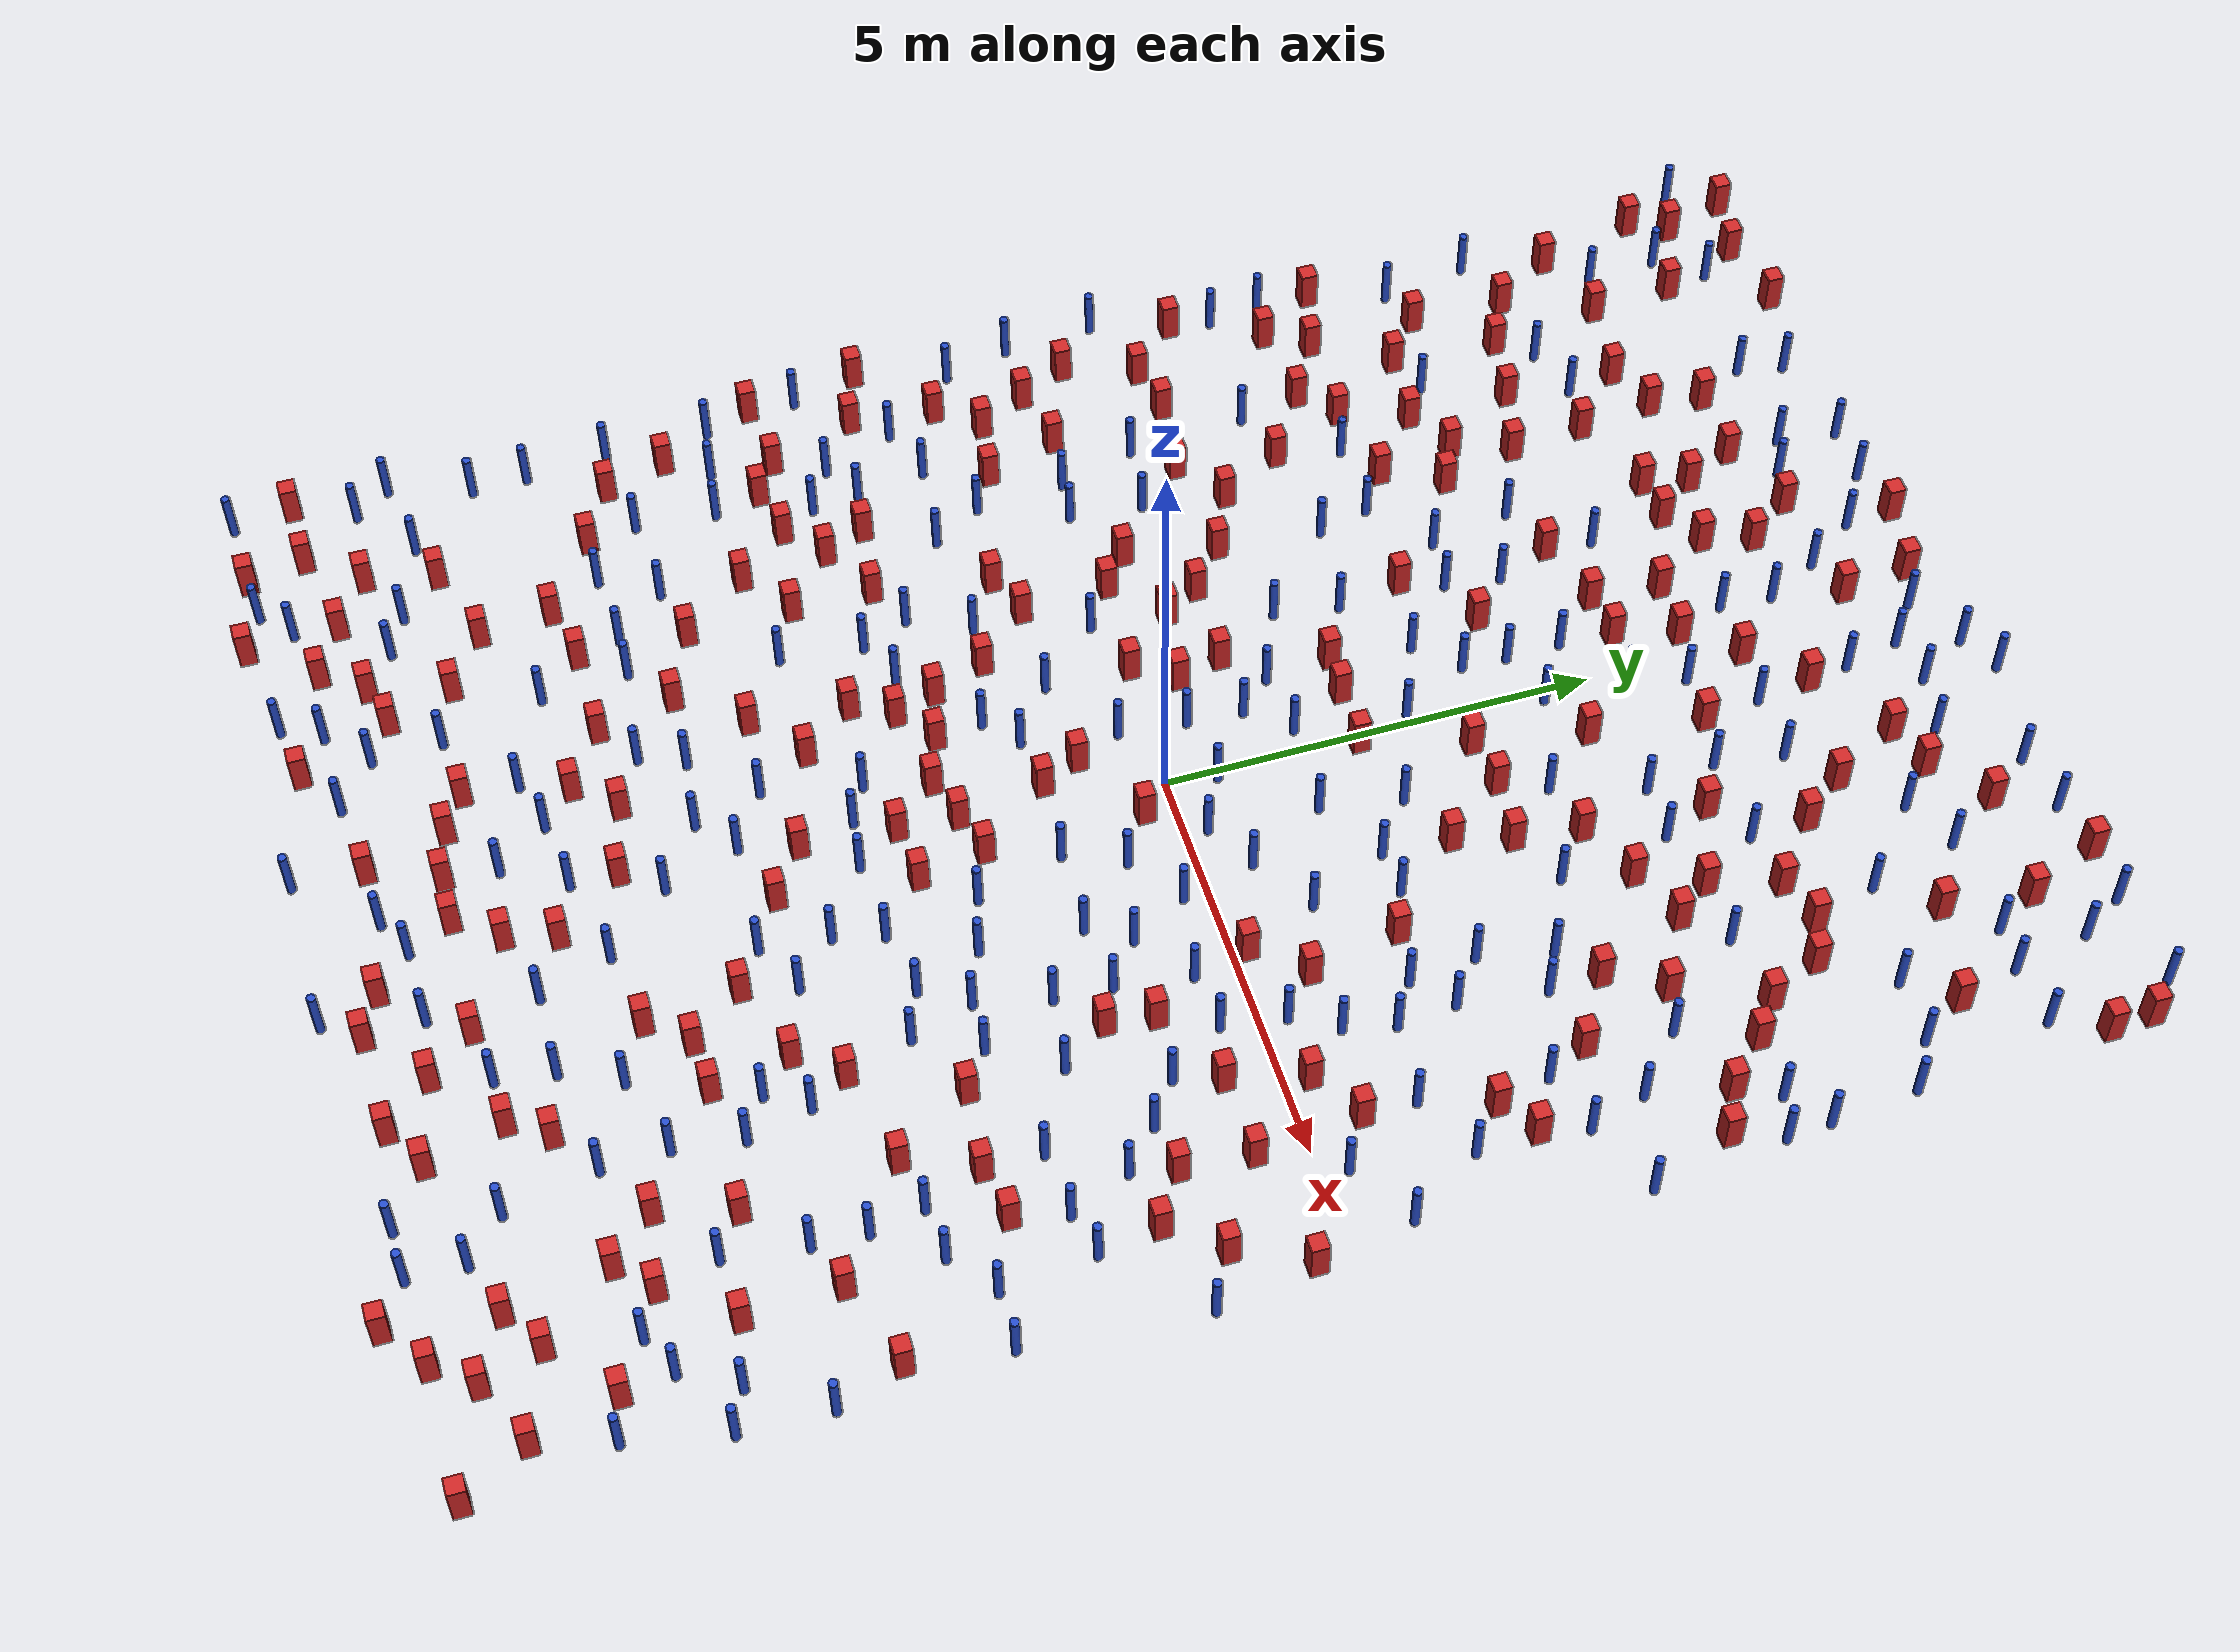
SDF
<sdf version="1.6">
  <model name="dense_23"><model name="square_post_obstacle0">
  <static>true</static>
  <pose frame="">-3.35205404195 -1.05310210833 1.91545236811e-07 -7.35059704564e-06 1.12565212e-07 2.39332434364e-05</pose>
  <link name="link">
    <pose frame="">0 0 0.25 0 -0 0</pose>
    <inertial>
      <mass>100</mass>
      <inertia>
        <ixx>0.166667</ixx>
        <ixy>0</ixy>
        <ixz>0</ixz>
        <iyy>0.166667</iyy>
        <iyz>0</iyz>
        <izz>0.166667</izz>
      </inertia>
    </inertial>
    <collision name="collision">
      <geometry>
        <box>
          <size>.2 .2 .5</size>
        </box>
      </geometry>
      <max_contacts>10</max_contacts>
      <surface>
        <contact>
          <ode/>
        </contact>
        <bounce/>
        <friction>
          <torsional>
            <ode/>
          </torsional>
          <ode/>
        </friction>
      </surface>
    </collision>
    <visual name="visual">
      <geometry>
        <box>
          <size>.2 .2 .5</size>
        </box>
      </geometry>
      <material>
        <script>
          <name>Gazebo/Red</name>
          <uri>file://media/materials/scripts/gazebo.material</uri>
        </script>
      </material>
    </visual>
    <self_collide>0</self_collide>
    <kinematic>0</kinematic>
  </link>
</model>
<model name="square_post_obstacle1">
  <static>true</static>
  <pose frame="">-2.80025574521 -0.854373793812 1.91545236811e-07 -7.35059704564e-06 1.12565212e-07 2.39332434364e-05</pose>
  <link name="link">
    <pose frame="">0 0 0.25 0 -0 0</pose>
    <inertial>
      <mass>100</mass>
      <inertia>
        <ixx>0.166667</ixx>
        <ixy>0</ixy>
        <ixz>0</ixz>
        <iyy>0.166667</iyy>
        <iyz>0</iyz>
        <izz>0.166667</izz>
      </inertia>
    </inertial>
    <collision name="collision">
      <geometry>
        <box>
          <size>.2 .2 .5</size>
        </box>
      </geometry>
      <max_contacts>10</max_contacts>
      <surface>
        <contact>
          <ode/>
        </contact>
        <bounce/>
        <friction>
          <torsional>
            <ode/>
          </torsional>
          <ode/>
        </friction>
      </surface>
    </collision>
    <visual name="visual">
      <geometry>
        <box>
          <size>.2 .2 .5</size>
        </box>
      </geometry>
      <material>
        <script>
          <name>Gazebo/Red</name>
          <uri>file://media/materials/scripts/gazebo.material</uri>
        </script>
      </material>
    </visual>
    <self_collide>0</self_collide>
    <kinematic>0</kinematic>
  </link>
</model>
<model name="pole_obstacle0">
  <static>true</static>
  <pose frame="">4.2485173204 -1.44879922275 7.38925637345e-09 -8.471706928e-08 1.24976765134e-08 -1.74513093015e-07</pose>
  <link name="link">
  <pose frame="">0 0 0.3 0 -0 0</pose>
    <inertial>
      <mass>1</mass>
      <inertia>
        <ixx>0.145833</ixx>
        <ixy>0</ixy>
        <ixz>0</ixz>
        <iyy>0.145833</iyy>
        <iyz>0</iyz>
        <izz>0.125</izz>
      </inertia>
    </inertial>
    <collision name="collision">
      <geometry>
        <cylinder>
          <radius>0.05</radius>
          <length>.6</length>
        </cylinder>
      </geometry>
      <max_contacts>10</max_contacts>
      <surface>
        <contact>
          <ode/>
        </contact>
        <bounce/>
        <friction>
          <torsional>
            <ode/>
          </torsional>
          <ode/>
        </friction>
      </surface>
    </collision>
    <visual name="visual">
      <geometry>
        <cylinder>
          <radius>0.05</radius>
          <length>.6</length>
        </cylinder>
      </geometry>
      <material>
        <script>
          <name>Gazebo/Blue</name>
          <uri>file://media/materials/scripts/gazebo.material</uri>
        </script>
      </material>
    </visual>
    <self_collide>0</self_collide>
    <kinematic>0</kinematic>
  </link>
</model>
<model name="square_post_obstacle2">
  <static>true</static>
  <pose frame="">2.74004452826 4.44997248497 1.91545236811e-07 -7.35059704564e-06 1.12565212e-07 2.39332434364e-05</pose>
  <link name="link">
    <pose frame="">0 0 0.25 0 -0 0</pose>
    <inertial>
      <mass>100</mass>
      <inertia>
        <ixx>0.166667</ixx>
        <ixy>0</ixy>
        <ixz>0</ixz>
        <iyy>0.166667</iyy>
        <iyz>0</iyz>
        <izz>0.166667</izz>
      </inertia>
    </inertial>
    <collision name="collision">
      <geometry>
        <box>
          <size>.2 .2 .5</size>
        </box>
      </geometry>
      <max_contacts>10</max_contacts>
      <surface>
        <contact>
          <ode/>
        </contact>
        <bounce/>
        <friction>
          <torsional>
            <ode/>
          </torsional>
          <ode/>
        </friction>
      </surface>
    </collision>
    <visual name="visual">
      <geometry>
        <box>
          <size>.2 .2 .5</size>
        </box>
      </geometry>
      <material>
        <script>
          <name>Gazebo/Red</name>
          <uri>file://media/materials/scripts/gazebo.material</uri>
        </script>
      </material>
    </visual>
    <self_collide>0</self_collide>
    <kinematic>0</kinematic>
  </link>
</model>
<model name="pole_obstacle1">
  <static>true</static>
  <pose frame="">3.07167220182 -7.02424409552 7.38925637345e-09 -8.47170692798e-08 1.24976765033e-08 -1.74513093019e-07</pose>
  <link name="link">
  <pose frame="">0 0 0.3 0 -0 0</pose>
    <inertial>
      <mass>1</mass>
      <inertia>
        <ixx>0.145833</ixx>
        <ixy>0</ixy>
        <ixz>0</ixz>
        <iyy>0.145833</iyy>
        <iyz>0</iyz>
        <izz>0.125</izz>
      </inertia>
    </inertial>
    <collision name="collision">
      <geometry>
        <cylinder>
          <radius>0.05</radius>
          <length>.6</length>
        </cylinder>
      </geometry>
      <max_contacts>10</max_contacts>
      <surface>
        <contact>
          <ode/>
        </contact>
        <bounce/>
        <friction>
          <torsional>
            <ode/>
          </torsional>
          <ode/>
        </friction>
      </surface>
    </collision>
    <visual name="visual">
      <geometry>
        <cylinder>
          <radius>0.05</radius>
          <length>.6</length>
        </cylinder>
      </geometry>
      <material>
        <script>
          <name>Gazebo/Blue</name>
          <uri>file://media/materials/scripts/gazebo.material</uri>
        </script>
      </material>
    </visual>
    <self_collide>0</self_collide>
    <kinematic>0</kinematic>
  </link>
</model>
<model name="square_post_obstacle3">
  <static>true</static>
  <pose frame="">5.5003414567 2.2988376357 1.91545236811e-07 -7.35059704564e-06 1.12565212e-07 2.39332434364e-05</pose>
  <link name="link">
    <pose frame="">0 0 0.25 0 -0 0</pose>
    <inertial>
      <mass>100</mass>
      <inertia>
        <ixx>0.166667</ixx>
        <ixy>0</ixy>
        <ixz>0</ixz>
        <iyy>0.166667</iyy>
        <iyz>0</iyz>
        <izz>0.166667</izz>
      </inertia>
    </inertial>
    <collision name="collision">
      <geometry>
        <box>
          <size>.2 .2 .5</size>
        </box>
      </geometry>
      <max_contacts>10</max_contacts>
      <surface>
        <contact>
          <ode/>
        </contact>
        <bounce/>
        <friction>
          <torsional>
            <ode/>
          </torsional>
          <ode/>
        </friction>
      </surface>
    </collision>
    <visual name="visual">
      <geometry>
        <box>
          <size>.2 .2 .5</size>
        </box>
      </geometry>
      <material>
        <script>
          <name>Gazebo/Red</name>
          <uri>file://media/materials/scripts/gazebo.material</uri>
        </script>
      </material>
    </visual>
    <self_collide>0</self_collide>
    <kinematic>0</kinematic>
  </link>
</model>
<model name="pole_obstacle2">
  <static>true</static>
  <pose frame="">-6.52942760812 -7.87029233997 7.38925637345e-09 -8.47170692796e-08 1.24976764786e-08 -1.74513093032e-07</pose>
  <link name="link">
  <pose frame="">0 0 0.3 0 -0 0</pose>
    <inertial>
      <mass>1</mass>
      <inertia>
        <ixx>0.145833</ixx>
        <ixy>0</ixy>
        <ixz>0</ixz>
        <iyy>0.145833</iyy>
        <iyz>0</iyz>
        <izz>0.125</izz>
      </inertia>
    </inertial>
    <collision name="collision">
      <geometry>
        <cylinder>
          <radius>0.05</radius>
          <length>.6</length>
        </cylinder>
      </geometry>
      <max_contacts>10</max_contacts>
      <surface>
        <contact>
          <ode/>
        </contact>
        <bounce/>
        <friction>
          <torsional>
            <ode/>
          </torsional>
          <ode/>
        </friction>
      </surface>
    </collision>
    <visual name="visual">
      <geometry>
        <cylinder>
          <radius>0.05</radius>
          <length>.6</length>
        </cylinder>
      </geometry>
      <material>
        <script>
          <name>Gazebo/Blue</name>
          <uri>file://media/materials/scripts/gazebo.material</uri>
        </script>
      </material>
    </visual>
    <self_collide>0</self_collide>
    <kinematic>0</kinematic>
  </link>
</model>
<model name="pole_obstacle3">
  <static>true</static>
  <pose frame="">6.49015581423 -1.49628110855 7.38925637345e-09 -8.471706928e-08 1.24976765134e-08 -1.74513093015e-07</pose>
  <link name="link">
  <pose frame="">0 0 0.3 0 -0 0</pose>
    <inertial>
      <mass>1</mass>
      <inertia>
        <ixx>0.145833</ixx>
        <ixy>0</ixy>
        <ixz>0</ixz>
        <iyy>0.145833</iyy>
        <iyz>0</iyz>
        <izz>0.125</izz>
      </inertia>
    </inertial>
    <collision name="collision">
      <geometry>
        <cylinder>
          <radius>0.05</radius>
          <length>.6</length>
        </cylinder>
      </geometry>
      <max_contacts>10</max_contacts>
      <surface>
        <contact>
          <ode/>
        </contact>
        <bounce/>
        <friction>
          <torsional>
            <ode/>
          </torsional>
          <ode/>
        </friction>
      </surface>
    </collision>
    <visual name="visual">
      <geometry>
        <cylinder>
          <radius>0.05</radius>
          <length>.6</length>
        </cylinder>
      </geometry>
      <material>
        <script>
          <name>Gazebo/Blue</name>
          <uri>file://media/materials/scripts/gazebo.material</uri>
        </script>
      </material>
    </visual>
    <self_collide>0</self_collide>
    <kinematic>0</kinematic>
  </link>
</model>
<model name="square_post_obstacle4">
  <static>true</static>
  <pose frame="">-1.02656893311 -7.87101364977 1.91545236811e-07 -7.35059704564e-06 1.12565212e-07 2.39332434364e-05</pose>
  <link name="link">
    <pose frame="">0 0 0.25 0 -0 0</pose>
    <inertial>
      <mass>100</mass>
      <inertia>
        <ixx>0.166667</ixx>
        <ixy>0</ixy>
        <ixz>0</ixz>
        <iyy>0.166667</iyy>
        <iyz>0</iyz>
        <izz>0.166667</izz>
      </inertia>
    </inertial>
    <collision name="collision">
      <geometry>
        <box>
          <size>.2 .2 .5</size>
        </box>
      </geometry>
      <max_contacts>10</max_contacts>
      <surface>
        <contact>
          <ode/>
        </contact>
        <bounce/>
        <friction>
          <torsional>
            <ode/>
          </torsional>
          <ode/>
        </friction>
      </surface>
    </collision>
    <visual name="visual">
      <geometry>
        <box>
          <size>.2 .2 .5</size>
        </box>
      </geometry>
      <material>
        <script>
          <name>Gazebo/Red</name>
          <uri>file://media/materials/scripts/gazebo.material</uri>
        </script>
      </material>
    </visual>
    <self_collide>0</self_collide>
    <kinematic>0</kinematic>
  </link>
</model>
<model name="square_post_obstacle5">
  <static>true</static>
  <pose frame="">2.00726199635 4.14036605938 1.91545236811e-07 -7.35059704564e-06 1.12565212e-07 2.39332434364e-05</pose>
  <link name="link">
    <pose frame="">0 0 0.25 0 -0 0</pose>
    <inertial>
      <mass>100</mass>
      <inertia>
        <ixx>0.166667</ixx>
        <ixy>0</ixy>
        <ixz>0</ixz>
        <iyy>0.166667</iyy>
        <iyz>0</iyz>
        <izz>0.166667</izz>
      </inertia>
    </inertial>
    <collision name="collision">
      <geometry>
        <box>
          <size>.2 .2 .5</size>
        </box>
      </geometry>
      <max_contacts>10</max_contacts>
      <surface>
        <contact>
          <ode/>
        </contact>
        <bounce/>
        <friction>
          <torsional>
            <ode/>
          </torsional>
          <ode/>
        </friction>
      </surface>
    </collision>
    <visual name="visual">
      <geometry>
        <box>
          <size>.2 .2 .5</size>
        </box>
      </geometry>
      <material>
        <script>
          <name>Gazebo/Red</name>
          <uri>file://media/materials/scripts/gazebo.material</uri>
        </script>
      </material>
    </visual>
    <self_collide>0</self_collide>
    <kinematic>0</kinematic>
  </link>
</model>
<model name="square_post_obstacle6">
  <static>true</static>
  <pose frame="">5.20519081044 -6.04144490822 1.91545236811e-07 -7.35059704564e-06 1.12565212e-07 2.39332434364e-05</pose>
  <link name="link">
    <pose frame="">0 0 0.25 0 -0 0</pose>
    <inertial>
      <mass>100</mass>
      <inertia>
        <ixx>0.166667</ixx>
        <ixy>0</ixy>
        <ixz>0</ixz>
        <iyy>0.166667</iyy>
        <iyz>0</iyz>
        <izz>0.166667</izz>
      </inertia>
    </inertial>
    <collision name="collision">
      <geometry>
        <box>
          <size>.2 .2 .5</size>
        </box>
      </geometry>
      <max_contacts>10</max_contacts>
      <surface>
        <contact>
          <ode/>
        </contact>
        <bounce/>
        <friction>
          <torsional>
            <ode/>
          </torsional>
          <ode/>
        </friction>
      </surface>
    </collision>
    <visual name="visual">
      <geometry>
        <box>
          <size>.2 .2 .5</size>
        </box>
      </geometry>
      <material>
        <script>
          <name>Gazebo/Red</name>
          <uri>file://media/materials/scripts/gazebo.material</uri>
        </script>
      </material>
    </visual>
    <self_collide>0</self_collide>
    <kinematic>0</kinematic>
  </link>
</model>
<model name="pole_obstacle4">
  <static>true</static>
  <pose frame="">-0.179069154487 -8.40646391588 7.38925637345e-09 -8.47170692796e-08 1.24976764775e-08 -1.74513093034e-07</pose>
  <link name="link">
  <pose frame="">0 0 0.3 0 -0 0</pose>
    <inertial>
      <mass>1</mass>
      <inertia>
        <ixx>0.145833</ixx>
        <ixy>0</ixy>
        <ixz>0</ixz>
        <iyy>0.145833</iyy>
        <iyz>0</iyz>
        <izz>0.125</izz>
      </inertia>
    </inertial>
    <collision name="collision">
      <geometry>
        <cylinder>
          <radius>0.05</radius>
          <length>.6</length>
        </cylinder>
      </geometry>
      <max_contacts>10</max_contacts>
      <surface>
        <contact>
          <ode/>
        </contact>
        <bounce/>
        <friction>
          <torsional>
            <ode/>
          </torsional>
          <ode/>
        </friction>
      </surface>
    </collision>
    <visual name="visual">
      <geometry>
        <cylinder>
          <radius>0.05</radius>
          <length>.6</length>
        </cylinder>
      </geometry>
      <material>
        <script>
          <name>Gazebo/Blue</name>
          <uri>file://media/materials/scripts/gazebo.material</uri>
        </script>
      </material>
    </visual>
    <self_collide>0</self_collide>
    <kinematic>0</kinematic>
  </link>
</model>
<model name="pole_obstacle5">
  <static>true</static>
  <pose frame="">3.86888885222 3.05011009654 7.38925637345e-09 -8.47170692798e-08 1.24976764939e-08 -1.74513093025e-07</pose>
  <link name="link">
  <pose frame="">0 0 0.3 0 -0 0</pose>
    <inertial>
      <mass>1</mass>
      <inertia>
        <ixx>0.145833</ixx>
        <ixy>0</ixy>
        <ixz>0</ixz>
        <iyy>0.145833</iyy>
        <iyz>0</iyz>
        <izz>0.125</izz>
      </inertia>
    </inertial>
    <collision name="collision">
      <geometry>
        <cylinder>
          <radius>0.05</radius>
          <length>.6</length>
        </cylinder>
      </geometry>
      <max_contacts>10</max_contacts>
      <surface>
        <contact>
          <ode/>
        </contact>
        <bounce/>
        <friction>
          <torsional>
            <ode/>
          </torsional>
          <ode/>
        </friction>
      </surface>
    </collision>
    <visual name="visual">
      <geometry>
        <cylinder>
          <radius>0.05</radius>
          <length>.6</length>
        </cylinder>
      </geometry>
      <material>
        <script>
          <name>Gazebo/Blue</name>
          <uri>file://media/materials/scripts/gazebo.material</uri>
        </script>
      </material>
    </visual>
    <self_collide>0</self_collide>
    <kinematic>0</kinematic>
  </link>
</model>
<model name="square_post_obstacle7">
  <static>true</static>
  <pose frame="">-3.60774097283 -3.35516538326 1.91545236811e-07 -7.35059704564e-06 1.12565212e-07 2.39332434364e-05</pose>
  <link name="link">
    <pose frame="">0 0 0.25 0 -0 0</pose>
    <inertial>
      <mass>100</mass>
      <inertia>
        <ixx>0.166667</ixx>
        <ixy>0</ixy>
        <ixz>0</ixz>
        <iyy>0.166667</iyy>
        <iyz>0</iyz>
        <izz>0.166667</izz>
      </inertia>
    </inertial>
    <collision name="collision">
      <geometry>
        <box>
          <size>.2 .2 .5</size>
        </box>
      </geometry>
      <max_contacts>10</max_contacts>
      <surface>
        <contact>
          <ode/>
        </contact>
        <bounce/>
        <friction>
          <torsional>
            <ode/>
          </torsional>
          <ode/>
        </friction>
      </surface>
    </collision>
    <visual name="visual">
      <geometry>
        <box>
          <size>.2 .2 .5</size>
        </box>
      </geometry>
      <material>
        <script>
          <name>Gazebo/Red</name>
          <uri>file://media/materials/scripts/gazebo.material</uri>
        </script>
      </material>
    </visual>
    <self_collide>0</self_collide>
    <kinematic>0</kinematic>
  </link>
</model>
<model name="square_post_obstacle8">
  <static>true</static>
  <pose frame="">-6.26026981273 -4.26427524342 1.91545236811e-07 -7.35059704564e-06 1.12565212e-07 2.39332434364e-05</pose>
  <link name="link">
    <pose frame="">0 0 0.25 0 -0 0</pose>
    <inertial>
      <mass>100</mass>
      <inertia>
        <ixx>0.166667</ixx>
        <ixy>0</ixy>
        <ixz>0</ixz>
        <iyy>0.166667</iyy>
        <iyz>0</iyz>
        <izz>0.166667</izz>
      </inertia>
    </inertial>
    <collision name="collision">
      <geometry>
        <box>
          <size>.2 .2 .5</size>
        </box>
      </geometry>
      <max_contacts>10</max_contacts>
      <surface>
        <contact>
          <ode/>
        </contact>
        <bounce/>
        <friction>
          <torsional>
            <ode/>
          </torsional>
          <ode/>
        </friction>
      </surface>
    </collision>
    <visual name="visual">
      <geometry>
        <box>
          <size>.2 .2 .5</size>
        </box>
      </geometry>
      <material>
        <script>
          <name>Gazebo/Red</name>
          <uri>file://media/materials/scripts/gazebo.material</uri>
        </script>
      </material>
    </visual>
    <self_collide>0</self_collide>
    <kinematic>0</kinematic>
  </link>
</model>
<model name="pole_obstacle6">
  <static>true</static>
  <pose frame="">-4.82827708982 -7.62652021731 7.38925637345e-09 -8.47170692796e-08 1.24976764786e-08 -1.74513093032e-07</pose>
  <link name="link">
  <pose frame="">0 0 0.3 0 -0 0</pose>
    <inertial>
      <mass>1</mass>
      <inertia>
        <ixx>0.145833</ixx>
        <ixy>0</ixy>
        <ixz>0</ixz>
        <iyy>0.145833</iyy>
        <iyz>0</iyz>
        <izz>0.125</izz>
      </inertia>
    </inertial>
    <collision name="collision">
      <geometry>
        <cylinder>
          <radius>0.05</radius>
          <length>.6</length>
        </cylinder>
      </geometry>
      <max_contacts>10</max_contacts>
      <surface>
        <contact>
          <ode/>
        </contact>
        <bounce/>
        <friction>
          <torsional>
            <ode/>
          </torsional>
          <ode/>
        </friction>
      </surface>
    </collision>
    <visual name="visual">
      <geometry>
        <cylinder>
          <radius>0.05</radius>
          <length>.6</length>
        </cylinder>
      </geometry>
      <material>
        <script>
          <name>Gazebo/Blue</name>
          <uri>file://media/materials/scripts/gazebo.material</uri>
        </script>
      </material>
    </visual>
    <self_collide>0</self_collide>
    <kinematic>0</kinematic>
  </link>
</model>
<model name="pole_obstacle7">
  <static>true</static>
  <pose frame="">3.3641014471 7.95612037145 7.38925637345e-09 -8.47170692799e-08 1.24976765031e-08 -1.7451309302e-07</pose>
  <link name="link">
  <pose frame="">0 0 0.3 0 -0 0</pose>
    <inertial>
      <mass>1</mass>
      <inertia>
        <ixx>0.145833</ixx>
        <ixy>0</ixy>
        <ixz>0</ixz>
        <iyy>0.145833</iyy>
        <iyz>0</iyz>
        <izz>0.125</izz>
      </inertia>
    </inertial>
    <collision name="collision">
      <geometry>
        <cylinder>
          <radius>0.05</radius>
          <length>.6</length>
        </cylinder>
      </geometry>
      <max_contacts>10</max_contacts>
      <surface>
        <contact>
          <ode/>
        </contact>
        <bounce/>
        <friction>
          <torsional>
            <ode/>
          </torsional>
          <ode/>
        </friction>
      </surface>
    </collision>
    <visual name="visual">
      <geometry>
        <cylinder>
          <radius>0.05</radius>
          <length>.6</length>
        </cylinder>
      </geometry>
      <material>
        <script>
          <name>Gazebo/Blue</name>
          <uri>file://media/materials/scripts/gazebo.material</uri>
        </script>
      </material>
    </visual>
    <self_collide>0</self_collide>
    <kinematic>0</kinematic>
  </link>
</model>
<model name="square_post_obstacle9">
  <static>true</static>
  <pose frame="">3.88361596768 6.09260042466 1.91545236811e-07 -7.35059704564e-06 1.12565212e-07 2.39332434364e-05</pose>
  <link name="link">
    <pose frame="">0 0 0.25 0 -0 0</pose>
    <inertial>
      <mass>100</mass>
      <inertia>
        <ixx>0.166667</ixx>
        <ixy>0</ixy>
        <ixz>0</ixz>
        <iyy>0.166667</iyy>
        <iyz>0</iyz>
        <izz>0.166667</izz>
      </inertia>
    </inertial>
    <collision name="collision">
      <geometry>
        <box>
          <size>.2 .2 .5</size>
        </box>
      </geometry>
      <max_contacts>10</max_contacts>
      <surface>
        <contact>
          <ode/>
        </contact>
        <bounce/>
        <friction>
          <torsional>
            <ode/>
          </torsional>
          <ode/>
        </friction>
      </surface>
    </collision>
    <visual name="visual">
      <geometry>
        <box>
          <size>.2 .2 .5</size>
        </box>
      </geometry>
      <material>
        <script>
          <name>Gazebo/Red</name>
          <uri>file://media/materials/scripts/gazebo.material</uri>
        </script>
      </material>
    </visual>
    <self_collide>0</self_collide>
    <kinematic>0</kinematic>
  </link>
</model>
<model name="square_post_obstacle10">
  <static>true</static>
  <pose frame="">-0.714707923323 -2.4765753038 1.91545236811e-07 -7.35059704564e-06 1.12565212e-07 2.39332434364e-05</pose>
  <link name="link">
    <pose frame="">0 0 0.25 0 -0 0</pose>
    <inertial>
      <mass>100</mass>
      <inertia>
        <ixx>0.166667</ixx>
        <ixy>0</ixy>
        <ixz>0</ixz>
        <iyy>0.166667</iyy>
        <iyz>0</iyz>
        <izz>0.166667</izz>
      </inertia>
    </inertial>
    <collision name="collision">
      <geometry>
        <box>
          <size>.2 .2 .5</size>
        </box>
      </geometry>
      <max_contacts>10</max_contacts>
      <surface>
        <contact>
          <ode/>
        </contact>
        <bounce/>
        <friction>
          <torsional>
            <ode/>
          </torsional>
          <ode/>
        </friction>
      </surface>
    </collision>
    <visual name="visual">
      <geometry>
        <box>
          <size>.2 .2 .5</size>
        </box>
      </geometry>
      <material>
        <script>
          <name>Gazebo/Red</name>
          <uri>file://media/materials/scripts/gazebo.material</uri>
        </script>
      </material>
    </visual>
    <self_collide>0</self_collide>
    <kinematic>0</kinematic>
  </link>
</model>
<model name="square_post_obstacle11">
  <static>true</static>
  <pose frame="">-1.5187978776 -3.70903876873 1.91545236811e-07 -7.35059704564e-06 1.12565212e-07 2.39332434364e-05</pose>
  <link name="link">
    <pose frame="">0 0 0.25 0 -0 0</pose>
    <inertial>
      <mass>100</mass>
      <inertia>
        <ixx>0.166667</ixx>
        <ixy>0</ixy>
        <ixz>0</ixz>
        <iyy>0.166667</iyy>
        <iyz>0</iyz>
        <izz>0.166667</izz>
      </inertia>
    </inertial>
    <collision name="collision">
      <geometry>
        <box>
          <size>.2 .2 .5</size>
        </box>
      </geometry>
      <max_contacts>10</max_contacts>
      <surface>
        <contact>
          <ode/>
        </contact>
        <bounce/>
        <friction>
          <torsional>
            <ode/>
          </torsional>
          <ode/>
        </friction>
      </surface>
    </collision>
    <visual name="visual">
      <geometry>
        <box>
          <size>.2 .2 .5</size>
        </box>
      </geometry>
      <material>
        <script>
          <name>Gazebo/Red</name>
          <uri>file://media/materials/scripts/gazebo.material</uri>
        </script>
      </material>
    </visual>
    <self_collide>0</self_collide>
    <kinematic>0</kinematic>
  </link>
</model>
<model name="square_post_obstacle12">
  <static>true</static>
  <pose frame="">-2.0900480813 -7.46458261331 1.91545236811e-07 -7.35059704564e-06 1.12565212e-07 2.39332434364e-05</pose>
  <link name="link">
    <pose frame="">0 0 0.25 0 -0 0</pose>
    <inertial>
      <mass>100</mass>
      <inertia>
        <ixx>0.166667</ixx>
        <ixy>0</ixy>
        <ixz>0</ixz>
        <iyy>0.166667</iyy>
        <iyz>0</iyz>
        <izz>0.166667</izz>
      </inertia>
    </inertial>
    <collision name="collision">
      <geometry>
        <box>
          <size>.2 .2 .5</size>
        </box>
      </geometry>
      <max_contacts>10</max_contacts>
      <surface>
        <contact>
          <ode/>
        </contact>
        <bounce/>
        <friction>
          <torsional>
            <ode/>
          </torsional>
          <ode/>
        </friction>
      </surface>
    </collision>
    <visual name="visual">
      <geometry>
        <box>
          <size>.2 .2 .5</size>
        </box>
      </geometry>
      <material>
        <script>
          <name>Gazebo/Red</name>
          <uri>file://media/materials/scripts/gazebo.material</uri>
        </script>
      </material>
    </visual>
    <self_collide>0</self_collide>
    <kinematic>0</kinematic>
  </link>
</model>
<model name="square_post_obstacle13">
  <static>true</static>
  <pose frame="">4.26121895151 8.46386247633 1.91545236811e-07 -7.35059704564e-06 1.12565212e-07 2.39332434364e-05</pose>
  <link name="link">
    <pose frame="">0 0 0.25 0 -0 0</pose>
    <inertial>
      <mass>100</mass>
      <inertia>
        <ixx>0.166667</ixx>
        <ixy>0</ixy>
        <ixz>0</ixz>
        <iyy>0.166667</iyy>
        <iyz>0</iyz>
        <izz>0.166667</izz>
      </inertia>
    </inertial>
    <collision name="collision">
      <geometry>
        <box>
          <size>.2 .2 .5</size>
        </box>
      </geometry>
      <max_contacts>10</max_contacts>
      <surface>
        <contact>
          <ode/>
        </contact>
        <bounce/>
        <friction>
          <torsional>
            <ode/>
          </torsional>
          <ode/>
        </friction>
      </surface>
    </collision>
    <visual name="visual">
      <geometry>
        <box>
          <size>.2 .2 .5</size>
        </box>
      </geometry>
      <material>
        <script>
          <name>Gazebo/Red</name>
          <uri>file://media/materials/scripts/gazebo.material</uri>
        </script>
      </material>
    </visual>
    <self_collide>0</self_collide>
    <kinematic>0</kinematic>
  </link>
</model>
<model name="pole_obstacle8">
  <static>true</static>
  <pose frame="">-3.82206462456 9.02512292885 7.38925637345e-09 -8.47170692799e-08 1.24976765012e-08 -1.74513093021e-07</pose>
  <link name="link">
  <pose frame="">0 0 0.3 0 -0 0</pose>
    <inertial>
      <mass>1</mass>
      <inertia>
        <ixx>0.145833</ixx>
        <ixy>0</ixy>
        <ixz>0</ixz>
        <iyy>0.145833</iyy>
        <iyz>0</iyz>
        <izz>0.125</izz>
      </inertia>
    </inertial>
    <collision name="collision">
      <geometry>
        <cylinder>
          <radius>0.05</radius>
          <length>.6</length>
        </cylinder>
      </geometry>
      <max_contacts>10</max_contacts>
      <surface>
        <contact>
          <ode/>
        </contact>
        <bounce/>
        <friction>
          <torsional>
            <ode/>
          </torsional>
          <ode/>
        </friction>
      </surface>
    </collision>
    <visual name="visual">
      <geometry>
        <cylinder>
          <radius>0.05</radius>
          <length>.6</length>
        </cylinder>
      </geometry>
      <material>
        <script>
          <name>Gazebo/Blue</name>
          <uri>file://media/materials/scripts/gazebo.material</uri>
        </script>
      </material>
    </visual>
    <self_collide>0</self_collide>
    <kinematic>0</kinematic>
  </link>
</model>
<model name="square_post_obstacle14">
  <static>true</static>
  <pose frame="">6.05690179406 9.00097728239 1.91545236811e-07 -7.35059704564e-06 1.12565212e-07 2.39332434364e-05</pose>
  <link name="link">
    <pose frame="">0 0 0.25 0 -0 0</pose>
    <inertial>
      <mass>100</mass>
      <inertia>
        <ixx>0.166667</ixx>
        <ixy>0</ixy>
        <ixz>0</ixz>
        <iyy>0.166667</iyy>
        <iyz>0</iyz>
        <izz>0.166667</izz>
      </inertia>
    </inertial>
    <collision name="collision">
      <geometry>
        <box>
          <size>.2 .2 .5</size>
        </box>
      </geometry>
      <max_contacts>10</max_contacts>
      <surface>
        <contact>
          <ode/>
        </contact>
        <bounce/>
        <friction>
          <torsional>
            <ode/>
          </torsional>
          <ode/>
        </friction>
      </surface>
    </collision>
    <visual name="visual">
      <geometry>
        <box>
          <size>.2 .2 .5</size>
        </box>
      </geometry>
      <material>
        <script>
          <name>Gazebo/Red</name>
          <uri>file://media/materials/scripts/gazebo.material</uri>
        </script>
      </material>
    </visual>
    <self_collide>0</self_collide>
    <kinematic>0</kinematic>
  </link>
</model>
<model name="square_post_obstacle15">
  <static>true</static>
  <pose frame="">-3.32703613505 -8.05833563639 1.91545236811e-07 -7.35059704564e-06 1.12565212e-07 2.39332434364e-05</pose>
  <link name="link">
    <pose frame="">0 0 0.25 0 -0 0</pose>
    <inertial>
      <mass>100</mass>
      <inertia>
        <ixx>0.166667</ixx>
        <ixy>0</ixy>
        <ixz>0</ixz>
        <iyy>0.166667</iyy>
        <iyz>0</iyz>
        <izz>0.166667</izz>
      </inertia>
    </inertial>
    <collision name="collision">
      <geometry>
        <box>
          <size>.2 .2 .5</size>
        </box>
      </geometry>
      <max_contacts>10</max_contacts>
      <surface>
        <contact>
          <ode/>
        </contact>
        <bounce/>
        <friction>
          <torsional>
            <ode/>
          </torsional>
          <ode/>
        </friction>
      </surface>
    </collision>
    <visual name="visual">
      <geometry>
        <box>
          <size>.2 .2 .5</size>
        </box>
      </geometry>
      <material>
        <script>
          <name>Gazebo/Red</name>
          <uri>file://media/materials/scripts/gazebo.material</uri>
        </script>
      </material>
    </visual>
    <self_collide>0</self_collide>
    <kinematic>0</kinematic>
  </link>
</model>
<model name="square_post_obstacle16">
  <static>true</static>
  <pose frame="">1.85319820563 -5.76374676269 1.91545236811e-07 -7.35059704564e-06 1.12565212e-07 2.39332434364e-05</pose>
  <link name="link">
    <pose frame="">0 0 0.25 0 -0 0</pose>
    <inertial>
      <mass>100</mass>
      <inertia>
        <ixx>0.166667</ixx>
        <ixy>0</ixy>
        <ixz>0</ixz>
        <iyy>0.166667</iyy>
        <iyz>0</iyz>
        <izz>0.166667</izz>
      </inertia>
    </inertial>
    <collision name="collision">
      <geometry>
        <box>
          <size>.2 .2 .5</size>
        </box>
      </geometry>
      <max_contacts>10</max_contacts>
      <surface>
        <contact>
          <ode/>
        </contact>
        <bounce/>
        <friction>
          <torsional>
            <ode/>
          </torsional>
          <ode/>
        </friction>
      </surface>
    </collision>
    <visual name="visual">
      <geometry>
        <box>
          <size>.2 .2 .5</size>
        </box>
      </geometry>
      <material>
        <script>
          <name>Gazebo/Red</name>
          <uri>file://media/materials/scripts/gazebo.material</uri>
        </script>
      </material>
    </visual>
    <self_collide>0</self_collide>
    <kinematic>0</kinematic>
  </link>
</model>
<model name="pole_obstacle9">
  <static>true</static>
  <pose frame="">-5.93752363122 -1.59175689322 7.38925637345e-09 -8.471706928e-08 1.24976765134e-08 -1.74513093015e-07</pose>
  <link name="link">
  <pose frame="">0 0 0.3 0 -0 0</pose>
    <inertial>
      <mass>1</mass>
      <inertia>
        <ixx>0.145833</ixx>
        <ixy>0</ixy>
        <ixz>0</ixz>
        <iyy>0.145833</iyy>
        <iyz>0</iyz>
        <izz>0.125</izz>
      </inertia>
    </inertial>
    <collision name="collision">
      <geometry>
        <cylinder>
          <radius>0.05</radius>
          <length>.6</length>
        </cylinder>
      </geometry>
      <max_contacts>10</max_contacts>
      <surface>
        <contact>
          <ode/>
        </contact>
        <bounce/>
        <friction>
          <torsional>
            <ode/>
          </torsional>
          <ode/>
        </friction>
      </surface>
    </collision>
    <visual name="visual">
      <geometry>
        <cylinder>
          <radius>0.05</radius>
          <length>.6</length>
        </cylinder>
      </geometry>
      <material>
        <script>
          <name>Gazebo/Blue</name>
          <uri>file://media/materials/scripts/gazebo.material</uri>
        </script>
      </material>
    </visual>
    <self_collide>0</self_collide>
    <kinematic>0</kinematic>
  </link>
</model>
<model name="square_post_obstacle17">
  <static>true</static>
  <pose frame="">3.32931835858 5.94401239555 1.91545236811e-07 -7.35059704564e-06 1.12565212e-07 2.39332434364e-05</pose>
  <link name="link">
    <pose frame="">0 0 0.25 0 -0 0</pose>
    <inertial>
      <mass>100</mass>
      <inertia>
        <ixx>0.166667</ixx>
        <ixy>0</ixy>
        <ixz>0</ixz>
        <iyy>0.166667</iyy>
        <iyz>0</iyz>
        <izz>0.166667</izz>
      </inertia>
    </inertial>
    <collision name="collision">
      <geometry>
        <box>
          <size>.2 .2 .5</size>
        </box>
      </geometry>
      <max_contacts>10</max_contacts>
      <surface>
        <contact>
          <ode/>
        </contact>
        <bounce/>
        <friction>
          <torsional>
            <ode/>
          </torsional>
          <ode/>
        </friction>
      </surface>
    </collision>
    <visual name="visual">
      <geometry>
        <box>
          <size>.2 .2 .5</size>
        </box>
      </geometry>
      <material>
        <script>
          <name>Gazebo/Red</name>
          <uri>file://media/materials/scripts/gazebo.material</uri>
        </script>
      </material>
    </visual>
    <self_collide>0</self_collide>
    <kinematic>0</kinematic>
  </link>
</model>
<model name="square_post_obstacle18">
  <static>true</static>
  <pose frame="">-2.19181532281 -1.48671952237 1.91545236811e-07 -7.35059704564e-06 1.12565212e-07 2.39332434364e-05</pose>
  <link name="link">
    <pose frame="">0 0 0.25 0 -0 0</pose>
    <inertial>
      <mass>100</mass>
      <inertia>
        <ixx>0.166667</ixx>
        <ixy>0</ixy>
        <ixz>0</ixz>
        <iyy>0.166667</iyy>
        <iyz>0</iyz>
        <izz>0.166667</izz>
      </inertia>
    </inertial>
    <collision name="collision">
      <geometry>
        <box>
          <size>.2 .2 .5</size>
        </box>
      </geometry>
      <max_contacts>10</max_contacts>
      <surface>
        <contact>
          <ode/>
        </contact>
        <bounce/>
        <friction>
          <torsional>
            <ode/>
          </torsional>
          <ode/>
        </friction>
      </surface>
    </collision>
    <visual name="visual">
      <geometry>
        <box>
          <size>.2 .2 .5</size>
        </box>
      </geometry>
      <material>
        <script>
          <name>Gazebo/Red</name>
          <uri>file://media/materials/scripts/gazebo.material</uri>
        </script>
      </material>
    </visual>
    <self_collide>0</self_collide>
    <kinematic>0</kinematic>
  </link>
</model>
<model name="pole_obstacle10">
  <static>true</static>
  <pose frame="">-6.55610675831 5.88170207349 7.38925637345e-09 -8.47170692796e-08 1.24976764786e-08 -1.74513093032e-07</pose>
  <link name="link">
  <pose frame="">0 0 0.3 0 -0 0</pose>
    <inertial>
      <mass>1</mass>
      <inertia>
        <ixx>0.145833</ixx>
        <ixy>0</ixy>
        <ixz>0</ixz>
        <iyy>0.145833</iyy>
        <iyz>0</iyz>
        <izz>0.125</izz>
      </inertia>
    </inertial>
    <collision name="collision">
      <geometry>
        <cylinder>
          <radius>0.05</radius>
          <length>.6</length>
        </cylinder>
      </geometry>
      <max_contacts>10</max_contacts>
      <surface>
        <contact>
          <ode/>
        </contact>
        <bounce/>
        <friction>
          <torsional>
            <ode/>
          </torsional>
          <ode/>
        </friction>
      </surface>
    </collision>
    <visual name="visual">
      <geometry>
        <cylinder>
          <radius>0.05</radius>
          <length>.6</length>
        </cylinder>
      </geometry>
      <material>
        <script>
          <name>Gazebo/Blue</name>
          <uri>file://media/materials/scripts/gazebo.material</uri>
        </script>
      </material>
    </visual>
    <self_collide>0</self_collide>
    <kinematic>0</kinematic>
  </link>
</model>
<model name="square_post_obstacle19">
  <static>true</static>
  <pose frame="">5.15073080693 -4.96994061939 1.91545236811e-07 -7.35059704564e-06 1.12565212e-07 2.39332434364e-05</pose>
  <link name="link">
    <pose frame="">0 0 0.25 0 -0 0</pose>
    <inertial>
      <mass>100</mass>
      <inertia>
        <ixx>0.166667</ixx>
        <ixy>0</ixy>
        <ixz>0</ixz>
        <iyy>0.166667</iyy>
        <iyz>0</iyz>
        <izz>0.166667</izz>
      </inertia>
    </inertial>
    <collision name="collision">
      <geometry>
        <box>
          <size>.2 .2 .5</size>
        </box>
      </geometry>
      <max_contacts>10</max_contacts>
      <surface>
        <contact>
          <ode/>
        </contact>
        <bounce/>
        <friction>
          <torsional>
            <ode/>
          </torsional>
          <ode/>
        </friction>
      </surface>
    </collision>
    <visual name="visual">
      <geometry>
        <box>
          <size>.2 .2 .5</size>
        </box>
      </geometry>
      <material>
        <script>
          <name>Gazebo/Red</name>
          <uri>file://media/materials/scripts/gazebo.material</uri>
        </script>
      </material>
    </visual>
    <self_collide>0</self_collide>
    <kinematic>0</kinematic>
  </link>
</model>
<model name="pole_obstacle11">
  <static>true</static>
  <pose frame="">3.23332634742 9.27613377009 7.38925637345e-09 -8.47170692793e-08 1.24976764408e-08 -1.74513093041e-07</pose>
  <link name="link">
  <pose frame="">0 0 0.3 0 -0 0</pose>
    <inertial>
      <mass>1</mass>
      <inertia>
        <ixx>0.145833</ixx>
        <ixy>0</ixy>
        <ixz>0</ixz>
        <iyy>0.145833</iyy>
        <iyz>0</iyz>
        <izz>0.125</izz>
      </inertia>
    </inertial>
    <collision name="collision">
      <geometry>
        <cylinder>
          <radius>0.05</radius>
          <length>.6</length>
        </cylinder>
      </geometry>
      <max_contacts>10</max_contacts>
      <surface>
        <contact>
          <ode/>
        </contact>
        <bounce/>
        <friction>
          <torsional>
            <ode/>
          </torsional>
          <ode/>
        </friction>
      </surface>
    </collision>
    <visual name="visual">
      <geometry>
        <cylinder>
          <radius>0.05</radius>
          <length>.6</length>
        </cylinder>
      </geometry>
      <material>
        <script>
          <name>Gazebo/Blue</name>
          <uri>file://media/materials/scripts/gazebo.material</uri>
        </script>
      </material>
    </visual>
    <self_collide>0</self_collide>
    <kinematic>0</kinematic>
  </link>
</model>
<model name="square_post_obstacle20">
  <static>true</static>
  <pose frame="">-2.53346879685 1.15611604299 1.91545236811e-07 -7.35059704564e-06 1.12565212e-07 2.39332434364e-05</pose>
  <link name="link">
    <pose frame="">0 0 0.25 0 -0 0</pose>
    <inertial>
      <mass>100</mass>
      <inertia>
        <ixx>0.166667</ixx>
        <ixy>0</ixy>
        <ixz>0</ixz>
        <iyy>0.166667</iyy>
        <iyz>0</iyz>
        <izz>0.166667</izz>
      </inertia>
    </inertial>
    <collision name="collision">
      <geometry>
        <box>
          <size>.2 .2 .5</size>
        </box>
      </geometry>
      <max_contacts>10</max_contacts>
      <surface>
        <contact>
          <ode/>
        </contact>
        <bounce/>
        <friction>
          <torsional>
            <ode/>
          </torsional>
          <ode/>
        </friction>
      </surface>
    </collision>
    <visual name="visual">
      <geometry>
        <box>
          <size>.2 .2 .5</size>
        </box>
      </geometry>
      <material>
        <script>
          <name>Gazebo/Red</name>
          <uri>file://media/materials/scripts/gazebo.material</uri>
        </script>
      </material>
    </visual>
    <self_collide>0</self_collide>
    <kinematic>0</kinematic>
  </link>
</model>
<model name="pole_obstacle12">
  <static>true</static>
  <pose frame="">-2.89692893605 -7.53343433619 7.38925637345e-09 -8.47170692798e-08 1.24976765033e-08 -1.74513093019e-07</pose>
  <link name="link">
  <pose frame="">0 0 0.3 0 -0 0</pose>
    <inertial>
      <mass>1</mass>
      <inertia>
        <ixx>0.145833</ixx>
        <ixy>0</ixy>
        <ixz>0</ixz>
        <iyy>0.145833</iyy>
        <iyz>0</iyz>
        <izz>0.125</izz>
      </inertia>
    </inertial>
    <collision name="collision">
      <geometry>
        <cylinder>
          <radius>0.05</radius>
          <length>.6</length>
        </cylinder>
      </geometry>
      <max_contacts>10</max_contacts>
      <surface>
        <contact>
          <ode/>
        </contact>
        <bounce/>
        <friction>
          <torsional>
            <ode/>
          </torsional>
          <ode/>
        </friction>
      </surface>
    </collision>
    <visual name="visual">
      <geometry>
        <cylinder>
          <radius>0.05</radius>
          <length>.6</length>
        </cylinder>
      </geometry>
      <material>
        <script>
          <name>Gazebo/Blue</name>
          <uri>file://media/materials/scripts/gazebo.material</uri>
        </script>
      </material>
    </visual>
    <self_collide>0</self_collide>
    <kinematic>0</kinematic>
  </link>
</model>
<model name="square_post_obstacle21">
  <static>true</static>
  <pose frame="">-4.3045964948 6.98042461301 1.91545236811e-07 -7.35059704564e-06 1.12565212e-07 2.39332434364e-05</pose>
  <link name="link">
    <pose frame="">0 0 0.25 0 -0 0</pose>
    <inertial>
      <mass>100</mass>
      <inertia>
        <ixx>0.166667</ixx>
        <ixy>0</ixy>
        <ixz>0</ixz>
        <iyy>0.166667</iyy>
        <iyz>0</iyz>
        <izz>0.166667</izz>
      </inertia>
    </inertial>
    <collision name="collision">
      <geometry>
        <box>
          <size>.2 .2 .5</size>
        </box>
      </geometry>
      <max_contacts>10</max_contacts>
      <surface>
        <contact>
          <ode/>
        </contact>
        <bounce/>
        <friction>
          <torsional>
            <ode/>
          </torsional>
          <ode/>
        </friction>
      </surface>
    </collision>
    <visual name="visual">
      <geometry>
        <box>
          <size>.2 .2 .5</size>
        </box>
      </geometry>
      <material>
        <script>
          <name>Gazebo/Red</name>
          <uri>file://media/materials/scripts/gazebo.material</uri>
        </script>
      </material>
    </visual>
    <self_collide>0</self_collide>
    <kinematic>0</kinematic>
  </link>
</model>
<model name="pole_obstacle13">
  <static>true</static>
  <pose frame="">3.05042973627 -6.27608102626 7.38925637345e-09 -8.47170692798e-08 1.24976765033e-08 -1.74513093019e-07</pose>
  <link name="link">
  <pose frame="">0 0 0.3 0 -0 0</pose>
    <inertial>
      <mass>1</mass>
      <inertia>
        <ixx>0.145833</ixx>
        <ixy>0</ixy>
        <ixz>0</ixz>
        <iyy>0.145833</iyy>
        <iyz>0</iyz>
        <izz>0.125</izz>
      </inertia>
    </inertial>
    <collision name="collision">
      <geometry>
        <cylinder>
          <radius>0.05</radius>
          <length>.6</length>
        </cylinder>
      </geometry>
      <max_contacts>10</max_contacts>
      <surface>
        <contact>
          <ode/>
        </contact>
        <bounce/>
        <friction>
          <torsional>
            <ode/>
          </torsional>
          <ode/>
        </friction>
      </surface>
    </collision>
    <visual name="visual">
      <geometry>
        <cylinder>
          <radius>0.05</radius>
          <length>.6</length>
        </cylinder>
      </geometry>
      <material>
        <script>
          <name>Gazebo/Blue</name>
          <uri>file://media/materials/scripts/gazebo.material</uri>
        </script>
      </material>
    </visual>
    <self_collide>0</self_collide>
    <kinematic>0</kinematic>
  </link>
</model>
<model name="square_post_obstacle22">
  <static>true</static>
  <pose frame="">1.0284544931 -7.94580521152 1.91545236811e-07 -7.35059704564e-06 1.12565212e-07 2.39332434364e-05</pose>
  <link name="link">
    <pose frame="">0 0 0.25 0 -0 0</pose>
    <inertial>
      <mass>100</mass>
      <inertia>
        <ixx>0.166667</ixx>
        <ixy>0</ixy>
        <ixz>0</ixz>
        <iyy>0.166667</iyy>
        <iyz>0</iyz>
        <izz>0.166667</izz>
      </inertia>
    </inertial>
    <collision name="collision">
      <geometry>
        <box>
          <size>.2 .2 .5</size>
        </box>
      </geometry>
      <max_contacts>10</max_contacts>
      <surface>
        <contact>
          <ode/>
        </contact>
        <bounce/>
        <friction>
          <torsional>
            <ode/>
          </torsional>
          <ode/>
        </friction>
      </surface>
    </collision>
    <visual name="visual">
      <geometry>
        <box>
          <size>.2 .2 .5</size>
        </box>
      </geometry>
      <material>
        <script>
          <name>Gazebo/Red</name>
          <uri>file://media/materials/scripts/gazebo.material</uri>
        </script>
      </material>
    </visual>
    <self_collide>0</self_collide>
    <kinematic>0</kinematic>
  </link>
</model>
<model name="pole_obstacle14">
  <static>true</static>
  <pose frame="">-0.487251782713 7.45424853015 7.38925637345e-09 -8.471706928e-08 1.24976765062e-08 -1.74513093016e-07</pose>
  <link name="link">
  <pose frame="">0 0 0.3 0 -0 0</pose>
    <inertial>
      <mass>1</mass>
      <inertia>
        <ixx>0.145833</ixx>
        <ixy>0</ixy>
        <ixz>0</ixz>
        <iyy>0.145833</iyy>
        <iyz>0</iyz>
        <izz>0.125</izz>
      </inertia>
    </inertial>
    <collision name="collision">
      <geometry>
        <cylinder>
          <radius>0.05</radius>
          <length>.6</length>
        </cylinder>
      </geometry>
      <max_contacts>10</max_contacts>
      <surface>
        <contact>
          <ode/>
        </contact>
        <bounce/>
        <friction>
          <torsional>
            <ode/>
          </torsional>
          <ode/>
        </friction>
      </surface>
    </collision>
    <visual name="visual">
      <geometry>
        <cylinder>
          <radius>0.05</radius>
          <length>.6</length>
        </cylinder>
      </geometry>
      <material>
        <script>
          <name>Gazebo/Blue</name>
          <uri>file://media/materials/scripts/gazebo.material</uri>
        </script>
      </material>
    </visual>
    <self_collide>0</self_collide>
    <kinematic>0</kinematic>
  </link>
</model>
<model name="pole_obstacle15">
  <static>true</static>
  <pose frame="">6.16743594063 6.26657277974 7.38925637345e-09 -8.47170692796e-08 1.24976764786e-08 -1.74513093032e-07</pose>
  <link name="link">
  <pose frame="">0 0 0.3 0 -0 0</pose>
    <inertial>
      <mass>1</mass>
      <inertia>
        <ixx>0.145833</ixx>
        <ixy>0</ixy>
        <ixz>0</ixz>
        <iyy>0.145833</iyy>
        <iyz>0</iyz>
        <izz>0.125</izz>
      </inertia>
    </inertial>
    <collision name="collision">
      <geometry>
        <cylinder>
          <radius>0.05</radius>
          <length>.6</length>
        </cylinder>
      </geometry>
      <max_contacts>10</max_contacts>
      <surface>
        <contact>
          <ode/>
        </contact>
        <bounce/>
        <friction>
          <torsional>
            <ode/>
          </torsional>
          <ode/>
        </friction>
      </surface>
    </collision>
    <visual name="visual">
      <geometry>
        <cylinder>
          <radius>0.05</radius>
          <length>.6</length>
        </cylinder>
      </geometry>
      <material>
        <script>
          <name>Gazebo/Blue</name>
          <uri>file://media/materials/scripts/gazebo.material</uri>
        </script>
      </material>
    </visual>
    <self_collide>0</self_collide>
    <kinematic>0</kinematic>
  </link>
</model>
<model name="pole_obstacle16">
  <static>true</static>
  <pose frame="">-1.39018965243 -1.717288133 7.38925637345e-09 -8.471706928e-08 1.24976765079e-08 -1.74513093017e-07</pose>
  <link name="link">
  <pose frame="">0 0 0.3 0 -0 0</pose>
    <inertial>
      <mass>1</mass>
      <inertia>
        <ixx>0.145833</ixx>
        <ixy>0</ixy>
        <ixz>0</ixz>
        <iyy>0.145833</iyy>
        <iyz>0</iyz>
        <izz>0.125</izz>
      </inertia>
    </inertial>
    <collision name="collision">
      <geometry>
        <cylinder>
          <radius>0.05</radius>
          <length>.6</length>
        </cylinder>
      </geometry>
      <max_contacts>10</max_contacts>
      <surface>
        <contact>
          <ode/>
        </contact>
        <bounce/>
        <friction>
          <torsional>
            <ode/>
          </torsional>
          <ode/>
        </friction>
      </surface>
    </collision>
    <visual name="visual">
      <geometry>
        <cylinder>
          <radius>0.05</radius>
          <length>.6</length>
        </cylinder>
      </geometry>
      <material>
        <script>
          <name>Gazebo/Blue</name>
          <uri>file://media/materials/scripts/gazebo.material</uri>
        </script>
      </material>
    </visual>
    <self_collide>0</self_collide>
    <kinematic>0</kinematic>
  </link>
</model>
<model name="square_post_obstacle23">
  <static>true</static>
  <pose frame="">6.29252648759 -0.376676278191 1.91545236811e-07 -7.35059704564e-06 1.12565212e-07 2.39332434364e-05</pose>
  <link name="link">
    <pose frame="">0 0 0.25 0 -0 0</pose>
    <inertial>
      <mass>100</mass>
      <inertia>
        <ixx>0.166667</ixx>
        <ixy>0</ixy>
        <ixz>0</ixz>
        <iyy>0.166667</iyy>
        <iyz>0</iyz>
        <izz>0.166667</izz>
      </inertia>
    </inertial>
    <collision name="collision">
      <geometry>
        <box>
          <size>.2 .2 .5</size>
        </box>
      </geometry>
      <max_contacts>10</max_contacts>
      <surface>
        <contact>
          <ode/>
        </contact>
        <bounce/>
        <friction>
          <torsional>
            <ode/>
          </torsional>
          <ode/>
        </friction>
      </surface>
    </collision>
    <visual name="visual">
      <geometry>
        <box>
          <size>.2 .2 .5</size>
        </box>
      </geometry>
      <material>
        <script>
          <name>Gazebo/Red</name>
          <uri>file://media/materials/scripts/gazebo.material</uri>
        </script>
      </material>
    </visual>
    <self_collide>0</self_collide>
    <kinematic>0</kinematic>
  </link>
</model>
<model name="pole_obstacle17">
  <static>true</static>
  <pose frame="">-4.93952085252 2.49353234793 7.38925637345e-09 -8.47170692798e-08 1.24976764937e-08 -1.74513093023e-07</pose>
  <link name="link">
  <pose frame="">0 0 0.3 0 -0 0</pose>
    <inertial>
      <mass>1</mass>
      <inertia>
        <ixx>0.145833</ixx>
        <ixy>0</ixy>
        <ixz>0</ixz>
        <iyy>0.145833</iyy>
        <iyz>0</iyz>
        <izz>0.125</izz>
      </inertia>
    </inertial>
    <collision name="collision">
      <geometry>
        <cylinder>
          <radius>0.05</radius>
          <length>.6</length>
        </cylinder>
      </geometry>
      <max_contacts>10</max_contacts>
      <surface>
        <contact>
          <ode/>
        </contact>
        <bounce/>
        <friction>
          <torsional>
            <ode/>
          </torsional>
          <ode/>
        </friction>
      </surface>
    </collision>
    <visual name="visual">
      <geometry>
        <cylinder>
          <radius>0.05</radius>
          <length>.6</length>
        </cylinder>
      </geometry>
      <material>
        <script>
          <name>Gazebo/Blue</name>
          <uri>file://media/materials/scripts/gazebo.material</uri>
        </script>
      </material>
    </visual>
    <self_collide>0</self_collide>
    <kinematic>0</kinematic>
  </link>
</model>
<model name="square_post_obstacle24">
  <static>true</static>
  <pose frame="">-1.34190381826 7.57631637367 1.91545236811e-07 -7.35059704564e-06 1.12565212e-07 2.39332434364e-05</pose>
  <link name="link">
    <pose frame="">0 0 0.25 0 -0 0</pose>
    <inertial>
      <mass>100</mass>
      <inertia>
        <ixx>0.166667</ixx>
        <ixy>0</ixy>
        <ixz>0</ixz>
        <iyy>0.166667</iyy>
        <iyz>0</iyz>
        <izz>0.166667</izz>
      </inertia>
    </inertial>
    <collision name="collision">
      <geometry>
        <box>
          <size>.2 .2 .5</size>
        </box>
      </geometry>
      <max_contacts>10</max_contacts>
      <surface>
        <contact>
          <ode/>
        </contact>
        <bounce/>
        <friction>
          <torsional>
            <ode/>
          </torsional>
          <ode/>
        </friction>
      </surface>
    </collision>
    <visual name="visual">
      <geometry>
        <box>
          <size>.2 .2 .5</size>
        </box>
      </geometry>
      <material>
        <script>
          <name>Gazebo/Red</name>
          <uri>file://media/materials/scripts/gazebo.material</uri>
        </script>
      </material>
    </visual>
    <self_collide>0</self_collide>
    <kinematic>0</kinematic>
  </link>
</model>
<model name="square_post_obstacle25">
  <static>true</static>
  <pose frame="">-5.35857846901 7.15570614176 1.91545236811e-07 -7.35059704564e-06 1.12565212e-07 2.39332434364e-05</pose>
  <link name="link">
    <pose frame="">0 0 0.25 0 -0 0</pose>
    <inertial>
      <mass>100</mass>
      <inertia>
        <ixx>0.166667</ixx>
        <ixy>0</ixy>
        <ixz>0</ixz>
        <iyy>0.166667</iyy>
        <iyz>0</iyz>
        <izz>0.166667</izz>
      </inertia>
    </inertial>
    <collision name="collision">
      <geometry>
        <box>
          <size>.2 .2 .5</size>
        </box>
      </geometry>
      <max_contacts>10</max_contacts>
      <surface>
        <contact>
          <ode/>
        </contact>
        <bounce/>
        <friction>
          <torsional>
            <ode/>
          </torsional>
          <ode/>
        </friction>
      </surface>
    </collision>
    <visual name="visual">
      <geometry>
        <box>
          <size>.2 .2 .5</size>
        </box>
      </geometry>
      <material>
        <script>
          <name>Gazebo/Red</name>
          <uri>file://media/materials/scripts/gazebo.material</uri>
        </script>
      </material>
    </visual>
    <self_collide>0</self_collide>
    <kinematic>0</kinematic>
  </link>
</model>
<model name="square_post_obstacle26">
  <static>true</static>
  <pose frame="">0.971629620544 6.01338458129 1.91545236811e-07 -7.35059704564e-06 1.12565212e-07 2.39332434364e-05</pose>
  <link name="link">
    <pose frame="">0 0 0.25 0 -0 0</pose>
    <inertial>
      <mass>100</mass>
      <inertia>
        <ixx>0.166667</ixx>
        <ixy>0</ixy>
        <ixz>0</ixz>
        <iyy>0.166667</iyy>
        <iyz>0</iyz>
        <izz>0.166667</izz>
      </inertia>
    </inertial>
    <collision name="collision">
      <geometry>
        <box>
          <size>.2 .2 .5</size>
        </box>
      </geometry>
      <max_contacts>10</max_contacts>
      <surface>
        <contact>
          <ode/>
        </contact>
        <bounce/>
        <friction>
          <torsional>
            <ode/>
          </torsional>
          <ode/>
        </friction>
      </surface>
    </collision>
    <visual name="visual">
      <geometry>
        <box>
          <size>.2 .2 .5</size>
        </box>
      </geometry>
      <material>
        <script>
          <name>Gazebo/Red</name>
          <uri>file://media/materials/scripts/gazebo.material</uri>
        </script>
      </material>
    </visual>
    <self_collide>0</self_collide>
    <kinematic>0</kinematic>
  </link>
</model>
<model name="square_post_obstacle27">
  <static>true</static>
  <pose frame="">-2.1458424664 -4.21667184286 1.91545236811e-07 -7.35059704564e-06 1.12565212e-07 2.39332434364e-05</pose>
  <link name="link">
    <pose frame="">0 0 0.25 0 -0 0</pose>
    <inertial>
      <mass>100</mass>
      <inertia>
        <ixx>0.166667</ixx>
        <ixy>0</ixy>
        <ixz>0</ixz>
        <iyy>0.166667</iyy>
        <iyz>0</iyz>
        <izz>0.166667</izz>
      </inertia>
    </inertial>
    <collision name="collision">
      <geometry>
        <box>
          <size>.2 .2 .5</size>
        </box>
      </geometry>
      <max_contacts>10</max_contacts>
      <surface>
        <contact>
          <ode/>
        </contact>
        <bounce/>
        <friction>
          <torsional>
            <ode/>
          </torsional>
          <ode/>
        </friction>
      </surface>
    </collision>
    <visual name="visual">
      <geometry>
        <box>
          <size>.2 .2 .5</size>
        </box>
      </geometry>
      <material>
        <script>
          <name>Gazebo/Red</name>
          <uri>file://media/materials/scripts/gazebo.material</uri>
        </script>
      </material>
    </visual>
    <self_collide>0</self_collide>
    <kinematic>0</kinematic>
  </link>
</model>
<model name="pole_obstacle18">
  <static>true</static>
  <pose frame="">-0.682456190744 1.12774905291 7.38925637345e-09 -8.47170692799e-08 1.24976765033e-08 -1.7451309302e-07</pose>
  <link name="link">
  <pose frame="">0 0 0.3 0 -0 0</pose>
    <inertial>
      <mass>1</mass>
      <inertia>
        <ixx>0.145833</ixx>
        <ixy>0</ixy>
        <ixz>0</ixz>
        <iyy>0.145833</iyy>
        <iyz>0</iyz>
        <izz>0.125</izz>
      </inertia>
    </inertial>
    <collision name="collision">
      <geometry>
        <cylinder>
          <radius>0.05</radius>
          <length>.6</length>
        </cylinder>
      </geometry>
      <max_contacts>10</max_contacts>
      <surface>
        <contact>
          <ode/>
        </contact>
        <bounce/>
        <friction>
          <torsional>
            <ode/>
          </torsional>
          <ode/>
        </friction>
      </surface>
    </collision>
    <visual name="visual">
      <geometry>
        <cylinder>
          <radius>0.05</radius>
          <length>.6</length>
        </cylinder>
      </geometry>
      <material>
        <script>
          <name>Gazebo/Blue</name>
          <uri>file://media/materials/scripts/gazebo.material</uri>
        </script>
      </material>
    </visual>
    <self_collide>0</self_collide>
    <kinematic>0</kinematic>
  </link>
</model>
<model name="square_post_obstacle28">
  <static>true</static>
  <pose frame="">-5.30732797405 -5.37208516619 1.91545236811e-07 -7.35059704564e-06 1.12565212e-07 2.39332434364e-05</pose>
  <link name="link">
    <pose frame="">0 0 0.25 0 -0 0</pose>
    <inertial>
      <mass>100</mass>
      <inertia>
        <ixx>0.166667</ixx>
        <ixy>0</ixy>
        <ixz>0</ixz>
        <iyy>0.166667</iyy>
        <iyz>0</iyz>
        <izz>0.166667</izz>
      </inertia>
    </inertial>
    <collision name="collision">
      <geometry>
        <box>
          <size>.2 .2 .5</size>
        </box>
      </geometry>
      <max_contacts>10</max_contacts>
      <surface>
        <contact>
          <ode/>
        </contact>
        <bounce/>
        <friction>
          <torsional>
            <ode/>
          </torsional>
          <ode/>
        </friction>
      </surface>
    </collision>
    <visual name="visual">
      <geometry>
        <box>
          <size>.2 .2 .5</size>
        </box>
      </geometry>
      <material>
        <script>
          <name>Gazebo/Red</name>
          <uri>file://media/materials/scripts/gazebo.material</uri>
        </script>
      </material>
    </visual>
    <self_collide>0</self_collide>
    <kinematic>0</kinematic>
  </link>
</model>
<model name="pole_obstacle19">
  <static>true</static>
  <pose frame="">3.6784043861 0.794483437749 7.38925637345e-09 -8.471706928e-08 1.24976765177e-08 -1.74513093012e-07</pose>
  <link name="link">
  <pose frame="">0 0 0.3 0 -0 0</pose>
    <inertial>
      <mass>1</mass>
      <inertia>
        <ixx>0.145833</ixx>
        <ixy>0</ixy>
        <ixz>0</ixz>
        <iyy>0.145833</iyy>
        <iyz>0</iyz>
        <izz>0.125</izz>
      </inertia>
    </inertial>
    <collision name="collision">
      <geometry>
        <cylinder>
          <radius>0.05</radius>
          <length>.6</length>
        </cylinder>
      </geometry>
      <max_contacts>10</max_contacts>
      <surface>
        <contact>
          <ode/>
        </contact>
        <bounce/>
        <friction>
          <torsional>
            <ode/>
          </torsional>
          <ode/>
        </friction>
      </surface>
    </collision>
    <visual name="visual">
      <geometry>
        <cylinder>
          <radius>0.05</radius>
          <length>.6</length>
        </cylinder>
      </geometry>
      <material>
        <script>
          <name>Gazebo/Blue</name>
          <uri>file://media/materials/scripts/gazebo.material</uri>
        </script>
      </material>
    </visual>
    <self_collide>0</self_collide>
    <kinematic>0</kinematic>
  </link>
</model>
<model name="square_post_obstacle29">
  <static>true</static>
  <pose frame="">-1.98612517827 6.69314189389 1.91545236811e-07 -7.35059704564e-06 1.12565212e-07 2.39332434364e-05</pose>
  <link name="link">
    <pose frame="">0 0 0.25 0 -0 0</pose>
    <inertial>
      <mass>100</mass>
      <inertia>
        <ixx>0.166667</ixx>
        <ixy>0</ixy>
        <ixz>0</ixz>
        <iyy>0.166667</iyy>
        <iyz>0</iyz>
        <izz>0.166667</izz>
      </inertia>
    </inertial>
    <collision name="collision">
      <geometry>
        <box>
          <size>.2 .2 .5</size>
        </box>
      </geometry>
      <max_contacts>10</max_contacts>
      <surface>
        <contact>
          <ode/>
        </contact>
        <bounce/>
        <friction>
          <torsional>
            <ode/>
          </torsional>
          <ode/>
        </friction>
      </surface>
    </collision>
    <visual name="visual">
      <geometry>
        <box>
          <size>.2 .2 .5</size>
        </box>
      </geometry>
      <material>
        <script>
          <name>Gazebo/Red</name>
          <uri>file://media/materials/scripts/gazebo.material</uri>
        </script>
      </material>
    </visual>
    <self_collide>0</self_collide>
    <kinematic>0</kinematic>
  </link>
</model>
<model name="square_post_obstacle30">
  <static>true</static>
  <pose frame="">2.54692806546 -7.40260620274 1.91545236811e-07 -7.35059704564e-06 1.12565212e-07 2.39332434364e-05</pose>
  <link name="link">
    <pose frame="">0 0 0.25 0 -0 0</pose>
    <inertial>
      <mass>100</mass>
      <inertia>
        <ixx>0.166667</ixx>
        <ixy>0</ixy>
        <ixz>0</ixz>
        <iyy>0.166667</iyy>
        <iyz>0</iyz>
        <izz>0.166667</izz>
      </inertia>
    </inertial>
    <collision name="collision">
      <geometry>
        <box>
          <size>.2 .2 .5</size>
        </box>
      </geometry>
      <max_contacts>10</max_contacts>
      <surface>
        <contact>
          <ode/>
        </contact>
        <bounce/>
        <friction>
          <torsional>
            <ode/>
          </torsional>
          <ode/>
        </friction>
      </surface>
    </collision>
    <visual name="visual">
      <geometry>
        <box>
          <size>.2 .2 .5</size>
        </box>
      </geometry>
      <material>
        <script>
          <name>Gazebo/Red</name>
          <uri>file://media/materials/scripts/gazebo.material</uri>
        </script>
      </material>
    </visual>
    <self_collide>0</self_collide>
    <kinematic>0</kinematic>
  </link>
</model>
<model name="pole_obstacle20">
  <static>true</static>
  <pose frame="">1.94381249306 -0.957695889717 7.38925637345e-09 -8.47170692798e-08 1.24976765028e-08 -1.74513093019e-07</pose>
  <link name="link">
  <pose frame="">0 0 0.3 0 -0 0</pose>
    <inertial>
      <mass>1</mass>
      <inertia>
        <ixx>0.145833</ixx>
        <ixy>0</ixy>
        <ixz>0</ixz>
        <iyy>0.145833</iyy>
        <iyz>0</iyz>
        <izz>0.125</izz>
      </inertia>
    </inertial>
    <collision name="collision">
      <geometry>
        <cylinder>
          <radius>0.05</radius>
          <length>.6</length>
        </cylinder>
      </geometry>
      <max_contacts>10</max_contacts>
      <surface>
        <contact>
          <ode/>
        </contact>
        <bounce/>
        <friction>
          <torsional>
            <ode/>
          </torsional>
          <ode/>
        </friction>
      </surface>
    </collision>
    <visual name="visual">
      <geometry>
        <cylinder>
          <radius>0.05</radius>
          <length>.6</length>
        </cylinder>
      </geometry>
      <material>
        <script>
          <name>Gazebo/Blue</name>
          <uri>file://media/materials/scripts/gazebo.material</uri>
        </script>
      </material>
    </visual>
    <self_collide>0</self_collide>
    <kinematic>0</kinematic>
  </link>
</model>
<model name="pole_obstacle21">
  <static>true</static>
  <pose frame="">0.16636004101 5.42641811792 7.38925637345e-09 -8.471706928e-08 1.24976765036e-08 -1.74513093019e-07</pose>
  <link name="link">
  <pose frame="">0 0 0.3 0 -0 0</pose>
    <inertial>
      <mass>1</mass>
      <inertia>
        <ixx>0.145833</ixx>
        <ixy>0</ixy>
        <ixz>0</ixz>
        <iyy>0.145833</iyy>
        <iyz>0</iyz>
        <izz>0.125</izz>
      </inertia>
    </inertial>
    <collision name="collision">
      <geometry>
        <cylinder>
          <radius>0.05</radius>
          <length>.6</length>
        </cylinder>
      </geometry>
      <max_contacts>10</max_contacts>
      <surface>
        <contact>
          <ode/>
        </contact>
        <bounce/>
        <friction>
          <torsional>
            <ode/>
          </torsional>
          <ode/>
        </friction>
      </surface>
    </collision>
    <visual name="visual">
      <geometry>
        <cylinder>
          <radius>0.05</radius>
          <length>.6</length>
        </cylinder>
      </geometry>
      <material>
        <script>
          <name>Gazebo/Blue</name>
          <uri>file://media/materials/scripts/gazebo.material</uri>
        </script>
      </material>
    </visual>
    <self_collide>0</self_collide>
    <kinematic>0</kinematic>
  </link>
</model>
<model name="square_post_obstacle31">
  <static>true</static>
  <pose frame="">-1.76271494415 -2.6173337315 1.91545236811e-07 -7.35059704564e-06 1.12565212e-07 2.39332434364e-05</pose>
  <link name="link">
    <pose frame="">0 0 0.25 0 -0 0</pose>
    <inertial>
      <mass>100</mass>
      <inertia>
        <ixx>0.166667</ixx>
        <ixy>0</ixy>
        <ixz>0</ixz>
        <iyy>0.166667</iyy>
        <iyz>0</iyz>
        <izz>0.166667</izz>
      </inertia>
    </inertial>
    <collision name="collision">
      <geometry>
        <box>
          <size>.2 .2 .5</size>
        </box>
      </geometry>
      <max_contacts>10</max_contacts>
      <surface>
        <contact>
          <ode/>
        </contact>
        <bounce/>
        <friction>
          <torsional>
            <ode/>
          </torsional>
          <ode/>
        </friction>
      </surface>
    </collision>
    <visual name="visual">
      <geometry>
        <box>
          <size>.2 .2 .5</size>
        </box>
      </geometry>
      <material>
        <script>
          <name>Gazebo/Red</name>
          <uri>file://media/materials/scripts/gazebo.material</uri>
        </script>
      </material>
    </visual>
    <self_collide>0</self_collide>
    <kinematic>0</kinematic>
  </link>
</model>
<model name="pole_obstacle22">
  <static>true</static>
  <pose frame="">-3.13177858768 3.44141593846 7.38925637345e-09 -8.47170692798e-08 1.24976764939e-08 -1.74513093025e-07</pose>
  <link name="link">
  <pose frame="">0 0 0.3 0 -0 0</pose>
    <inertial>
      <mass>1</mass>
      <inertia>
        <ixx>0.145833</ixx>
        <ixy>0</ixy>
        <ixz>0</ixz>
        <iyy>0.145833</iyy>
        <iyz>0</iyz>
        <izz>0.125</izz>
      </inertia>
    </inertial>
    <collision name="collision">
      <geometry>
        <cylinder>
          <radius>0.05</radius>
          <length>.6</length>
        </cylinder>
      </geometry>
      <max_contacts>10</max_contacts>
      <surface>
        <contact>
          <ode/>
        </contact>
        <bounce/>
        <friction>
          <torsional>
            <ode/>
          </torsional>
          <ode/>
        </friction>
      </surface>
    </collision>
    <visual name="visual">
      <geometry>
        <cylinder>
          <radius>0.05</radius>
          <length>.6</length>
        </cylinder>
      </geometry>
      <material>
        <script>
          <name>Gazebo/Blue</name>
          <uri>file://media/materials/scripts/gazebo.material</uri>
        </script>
      </material>
    </visual>
    <self_collide>0</self_collide>
    <kinematic>0</kinematic>
  </link>
</model>
<model name="pole_obstacle23">
  <static>true</static>
  <pose frame="">6.09118267993 0.743534009738 7.38925637345e-09 -8.47170692799e-08 1.24976765038e-08 -1.74513093018e-07</pose>
  <link name="link">
  <pose frame="">0 0 0.3 0 -0 0</pose>
    <inertial>
      <mass>1</mass>
      <inertia>
        <ixx>0.145833</ixx>
        <ixy>0</ixy>
        <ixz>0</ixz>
        <iyy>0.145833</iyy>
        <iyz>0</iyz>
        <izz>0.125</izz>
      </inertia>
    </inertial>
    <collision name="collision">
      <geometry>
        <cylinder>
          <radius>0.05</radius>
          <length>.6</length>
        </cylinder>
      </geometry>
      <max_contacts>10</max_contacts>
      <surface>
        <contact>
          <ode/>
        </contact>
        <bounce/>
        <friction>
          <torsional>
            <ode/>
          </torsional>
          <ode/>
        </friction>
      </surface>
    </collision>
    <visual name="visual">
      <geometry>
        <cylinder>
          <radius>0.05</radius>
          <length>.6</length>
        </cylinder>
      </geometry>
      <material>
        <script>
          <name>Gazebo/Blue</name>
          <uri>file://media/materials/scripts/gazebo.material</uri>
        </script>
      </material>
    </visual>
    <self_collide>0</self_collide>
    <kinematic>0</kinematic>
  </link>
</model>
<model name="pole_obstacle24">
  <static>true</static>
  <pose frame="">4.49639749609 -3.95909316292 7.38925637345e-09 -8.47170692799e-08 1.24976764984e-08 -1.7451309302e-07</pose>
  <link name="link">
  <pose frame="">0 0 0.3 0 -0 0</pose>
    <inertial>
      <mass>1</mass>
      <inertia>
        <ixx>0.145833</ixx>
        <ixy>0</ixy>
        <ixz>0</ixz>
        <iyy>0.145833</iyy>
        <iyz>0</iyz>
        <izz>0.125</izz>
      </inertia>
    </inertial>
    <collision name="collision">
      <geometry>
        <cylinder>
          <radius>0.05</radius>
          <length>.6</length>
        </cylinder>
      </geometry>
      <max_contacts>10</max_contacts>
      <surface>
        <contact>
          <ode/>
        </contact>
        <bounce/>
        <friction>
          <torsional>
            <ode/>
          </torsional>
          <ode/>
        </friction>
      </surface>
    </collision>
    <visual name="visual">
      <geometry>
        <cylinder>
          <radius>0.05</radius>
          <length>.6</length>
        </cylinder>
      </geometry>
      <material>
        <script>
          <name>Gazebo/Blue</name>
          <uri>file://media/materials/scripts/gazebo.material</uri>
        </script>
      </material>
    </visual>
    <self_collide>0</self_collide>
    <kinematic>0</kinematic>
  </link>
</model>
<model name="pole_obstacle25">
  <static>true</static>
  <pose frame="">-1.2587366664 8.73435117649 7.38925637345e-09 -8.47170692798e-08 1.24976764881e-08 -1.74513093027e-07</pose>
  <link name="link">
  <pose frame="">0 0 0.3 0 -0 0</pose>
    <inertial>
      <mass>1</mass>
      <inertia>
        <ixx>0.145833</ixx>
        <ixy>0</ixy>
        <ixz>0</ixz>
        <iyy>0.145833</iyy>
        <iyz>0</iyz>
        <izz>0.125</izz>
      </inertia>
    </inertial>
    <collision name="collision">
      <geometry>
        <cylinder>
          <radius>0.05</radius>
          <length>.6</length>
        </cylinder>
      </geometry>
      <max_contacts>10</max_contacts>
      <surface>
        <contact>
          <ode/>
        </contact>
        <bounce/>
        <friction>
          <torsional>
            <ode/>
          </torsional>
          <ode/>
        </friction>
      </surface>
    </collision>
    <visual name="visual">
      <geometry>
        <cylinder>
          <radius>0.05</radius>
          <length>.6</length>
        </cylinder>
      </geometry>
      <material>
        <script>
          <name>Gazebo/Blue</name>
          <uri>file://media/materials/scripts/gazebo.material</uri>
        </script>
      </material>
    </visual>
    <self_collide>0</self_collide>
    <kinematic>0</kinematic>
  </link>
</model>
<model name="pole_obstacle26">
  <static>true</static>
  <pose frame="">2.07741708046 1.02129432986 7.38925637345e-09 -8.47170692793e-08 1.2497676438e-08 -1.74513093043e-07</pose>
  <link name="link">
  <pose frame="">0 0 0.3 0 -0 0</pose>
    <inertial>
      <mass>1</mass>
      <inertia>
        <ixx>0.145833</ixx>
        <ixy>0</ixy>
        <ixz>0</ixz>
        <iyy>0.145833</iyy>
        <iyz>0</iyz>
        <izz>0.125</izz>
      </inertia>
    </inertial>
    <collision name="collision">
      <geometry>
        <cylinder>
          <radius>0.05</radius>
          <length>.6</length>
        </cylinder>
      </geometry>
      <max_contacts>10</max_contacts>
      <surface>
        <contact>
          <ode/>
        </contact>
        <bounce/>
        <friction>
          <torsional>
            <ode/>
          </torsional>
          <ode/>
        </friction>
      </surface>
    </collision>
    <visual name="visual">
      <geometry>
        <cylinder>
          <radius>0.05</radius>
          <length>.6</length>
        </cylinder>
      </geometry>
      <material>
        <script>
          <name>Gazebo/Blue</name>
          <uri>file://media/materials/scripts/gazebo.material</uri>
        </script>
      </material>
    </visual>
    <self_collide>0</self_collide>
    <kinematic>0</kinematic>
  </link>
</model>
<model name="pole_obstacle27">
  <static>true</static>
  <pose frame="">1.7917339287 -7.20234265877 7.38925637345e-09 -8.47170692799e-08 1.24976765033e-08 -1.74513093018e-07</pose>
  <link name="link">
  <pose frame="">0 0 0.3 0 -0 0</pose>
    <inertial>
      <mass>1</mass>
      <inertia>
        <ixx>0.145833</ixx>
        <ixy>0</ixy>
        <ixz>0</ixz>
        <iyy>0.145833</iyy>
        <iyz>0</iyz>
        <izz>0.125</izz>
      </inertia>
    </inertial>
    <collision name="collision">
      <geometry>
        <cylinder>
          <radius>0.05</radius>
          <length>.6</length>
        </cylinder>
      </geometry>
      <max_contacts>10</max_contacts>
      <surface>
        <contact>
          <ode/>
        </contact>
        <bounce/>
        <friction>
          <torsional>
            <ode/>
          </torsional>
          <ode/>
        </friction>
      </surface>
    </collision>
    <visual name="visual">
      <geometry>
        <cylinder>
          <radius>0.05</radius>
          <length>.6</length>
        </cylinder>
      </geometry>
      <material>
        <script>
          <name>Gazebo/Blue</name>
          <uri>file://media/materials/scripts/gazebo.material</uri>
        </script>
      </material>
    </visual>
    <self_collide>0</self_collide>
    <kinematic>0</kinematic>
  </link>
</model>
<model name="square_post_obstacle32">
  <static>true</static>
  <pose frame="">-5.28289414419 4.52706465179 1.91545236811e-07 -7.35059704564e-06 1.12565212e-07 2.39332434364e-05</pose>
  <link name="link">
    <pose frame="">0 0 0.25 0 -0 0</pose>
    <inertial>
      <mass>100</mass>
      <inertia>
        <ixx>0.166667</ixx>
        <ixy>0</ixy>
        <ixz>0</ixz>
        <iyy>0.166667</iyy>
        <iyz>0</iyz>
        <izz>0.166667</izz>
      </inertia>
    </inertial>
    <collision name="collision">
      <geometry>
        <box>
          <size>.2 .2 .5</size>
        </box>
      </geometry>
      <max_contacts>10</max_contacts>
      <surface>
        <contact>
          <ode/>
        </contact>
        <bounce/>
        <friction>
          <torsional>
            <ode/>
          </torsional>
          <ode/>
        </friction>
      </surface>
    </collision>
    <visual name="visual">
      <geometry>
        <box>
          <size>.2 .2 .5</size>
        </box>
      </geometry>
      <material>
        <script>
          <name>Gazebo/Red</name>
          <uri>file://media/materials/scripts/gazebo.material</uri>
        </script>
      </material>
    </visual>
    <self_collide>0</self_collide>
    <kinematic>0</kinematic>
  </link>
</model>
<model name="square_post_obstacle33">
  <static>true</static>
  <pose frame="">0.518776691572 3.40940659689 1.91545236811e-07 -7.35059704564e-06 1.12565212e-07 2.39332434364e-05</pose>
  <link name="link">
    <pose frame="">0 0 0.25 0 -0 0</pose>
    <inertial>
      <mass>100</mass>
      <inertia>
        <ixx>0.166667</ixx>
        <ixy>0</ixy>
        <ixz>0</ixz>
        <iyy>0.166667</iyy>
        <iyz>0</iyz>
        <izz>0.166667</izz>
      </inertia>
    </inertial>
    <collision name="collision">
      <geometry>
        <box>
          <size>.2 .2 .5</size>
        </box>
      </geometry>
      <max_contacts>10</max_contacts>
      <surface>
        <contact>
          <ode/>
        </contact>
        <bounce/>
        <friction>
          <torsional>
            <ode/>
          </torsional>
          <ode/>
        </friction>
      </surface>
    </collision>
    <visual name="visual">
      <geometry>
        <box>
          <size>.2 .2 .5</size>
        </box>
      </geometry>
      <material>
        <script>
          <name>Gazebo/Red</name>
          <uri>file://media/materials/scripts/gazebo.material</uri>
        </script>
      </material>
    </visual>
    <self_collide>0</self_collide>
    <kinematic>0</kinematic>
  </link>
</model>
<model name="pole_obstacle28">
  <static>true</static>
  <pose frame="">3.7545110055 -1.09945312192 7.38925637345e-09 -8.471706928e-08 1.24976765152e-08 -1.74513093012e-07</pose>
  <link name="link">
  <pose frame="">0 0 0.3 0 -0 0</pose>
    <inertial>
      <mass>1</mass>
      <inertia>
        <ixx>0.145833</ixx>
        <ixy>0</ixy>
        <ixz>0</ixz>
        <iyy>0.145833</iyy>
        <iyz>0</iyz>
        <izz>0.125</izz>
      </inertia>
    </inertial>
    <collision name="collision">
      <geometry>
        <cylinder>
          <radius>0.05</radius>
          <length>.6</length>
        </cylinder>
      </geometry>
      <max_contacts>10</max_contacts>
      <surface>
        <contact>
          <ode/>
        </contact>
        <bounce/>
        <friction>
          <torsional>
            <ode/>
          </torsional>
          <ode/>
        </friction>
      </surface>
    </collision>
    <visual name="visual">
      <geometry>
        <cylinder>
          <radius>0.05</radius>
          <length>.6</length>
        </cylinder>
      </geometry>
      <material>
        <script>
          <name>Gazebo/Blue</name>
          <uri>file://media/materials/scripts/gazebo.material</uri>
        </script>
      </material>
    </visual>
    <self_collide>0</self_collide>
    <kinematic>0</kinematic>
  </link>
</model>
<model name="pole_obstacle29">
  <static>true</static>
  <pose frame="">-4.21491245848 6.41125337489 7.38925637345e-09 -8.47170692796e-08 1.24976764786e-08 -1.74513093032e-07</pose>
  <link name="link">
  <pose frame="">0 0 0.3 0 -0 0</pose>
    <inertial>
      <mass>1</mass>
      <inertia>
        <ixx>0.145833</ixx>
        <ixy>0</ixy>
        <ixz>0</ixz>
        <iyy>0.145833</iyy>
        <iyz>0</iyz>
        <izz>0.125</izz>
      </inertia>
    </inertial>
    <collision name="collision">
      <geometry>
        <cylinder>
          <radius>0.05</radius>
          <length>.6</length>
        </cylinder>
      </geometry>
      <max_contacts>10</max_contacts>
      <surface>
        <contact>
          <ode/>
        </contact>
        <bounce/>
        <friction>
          <torsional>
            <ode/>
          </torsional>
          <ode/>
        </friction>
      </surface>
    </collision>
    <visual name="visual">
      <geometry>
        <cylinder>
          <radius>0.05</radius>
          <length>.6</length>
        </cylinder>
      </geometry>
      <material>
        <script>
          <name>Gazebo/Blue</name>
          <uri>file://media/materials/scripts/gazebo.material</uri>
        </script>
      </material>
    </visual>
    <self_collide>0</self_collide>
    <kinematic>0</kinematic>
  </link>
</model>
<model name="square_post_obstacle34">
  <static>true</static>
  <pose frame="">-6.63710180028 2.10896019173 1.91545236811e-07 -7.35059704564e-06 1.12565212e-07 2.39332434364e-05</pose>
  <link name="link">
    <pose frame="">0 0 0.25 0 -0 0</pose>
    <inertial>
      <mass>100</mass>
      <inertia>
        <ixx>0.166667</ixx>
        <ixy>0</ixy>
        <ixz>0</ixz>
        <iyy>0.166667</iyy>
        <iyz>0</iyz>
        <izz>0.166667</izz>
      </inertia>
    </inertial>
    <collision name="collision">
      <geometry>
        <box>
          <size>.2 .2 .5</size>
        </box>
      </geometry>
      <max_contacts>10</max_contacts>
      <surface>
        <contact>
          <ode/>
        </contact>
        <bounce/>
        <friction>
          <torsional>
            <ode/>
          </torsional>
          <ode/>
        </friction>
      </surface>
    </collision>
    <visual name="visual">
      <geometry>
        <box>
          <size>.2 .2 .5</size>
        </box>
      </geometry>
      <material>
        <script>
          <name>Gazebo/Red</name>
          <uri>file://media/materials/scripts/gazebo.material</uri>
        </script>
      </material>
    </visual>
    <self_collide>0</self_collide>
    <kinematic>0</kinematic>
  </link>
</model>
<model name="pole_obstacle30">
  <static>true</static>
  <pose frame="">3.82603627733 5.14343423166 7.38925637345e-09 -8.47170692798e-08 1.24976765033e-08 -1.74513093019e-07</pose>
  <link name="link">
  <pose frame="">0 0 0.3 0 -0 0</pose>
    <inertial>
      <mass>1</mass>
      <inertia>
        <ixx>0.145833</ixx>
        <ixy>0</ixy>
        <ixz>0</ixz>
        <iyy>0.145833</iyy>
        <iyz>0</iyz>
        <izz>0.125</izz>
      </inertia>
    </inertial>
    <collision name="collision">
      <geometry>
        <cylinder>
          <radius>0.05</radius>
          <length>.6</length>
        </cylinder>
      </geometry>
      <max_contacts>10</max_contacts>
      <surface>
        <contact>
          <ode/>
        </contact>
        <bounce/>
        <friction>
          <torsional>
            <ode/>
          </torsional>
          <ode/>
        </friction>
      </surface>
    </collision>
    <visual name="visual">
      <geometry>
        <cylinder>
          <radius>0.05</radius>
          <length>.6</length>
        </cylinder>
      </geometry>
      <material>
        <script>
          <name>Gazebo/Blue</name>
          <uri>file://media/materials/scripts/gazebo.material</uri>
        </script>
      </material>
    </visual>
    <self_collide>0</self_collide>
    <kinematic>0</kinematic>
  </link>
</model>
<model name="pole_obstacle31">
  <static>true</static>
  <pose frame="">1.10472437094 -3.48174567385 7.38925637345e-09 -8.47170692799e-08 1.24976765053e-08 -1.74513093017e-07</pose>
  <link name="link">
  <pose frame="">0 0 0.3 0 -0 0</pose>
    <inertial>
      <mass>1</mass>
      <inertia>
        <ixx>0.145833</ixx>
        <ixy>0</ixy>
        <ixz>0</ixz>
        <iyy>0.145833</iyy>
        <iyz>0</iyz>
        <izz>0.125</izz>
      </inertia>
    </inertial>
    <collision name="collision">
      <geometry>
        <cylinder>
          <radius>0.05</radius>
          <length>.6</length>
        </cylinder>
      </geometry>
      <max_contacts>10</max_contacts>
      <surface>
        <contact>
          <ode/>
        </contact>
        <bounce/>
        <friction>
          <torsional>
            <ode/>
          </torsional>
          <ode/>
        </friction>
      </surface>
    </collision>
    <visual name="visual">
      <geometry>
        <cylinder>
          <radius>0.05</radius>
          <length>.6</length>
        </cylinder>
      </geometry>
      <material>
        <script>
          <name>Gazebo/Blue</name>
          <uri>file://media/materials/scripts/gazebo.material</uri>
        </script>
      </material>
    </visual>
    <self_collide>0</self_collide>
    <kinematic>0</kinematic>
  </link>
</model>
<model name="pole_obstacle32">
  <static>true</static>
  <pose frame="">-0.123792153698 2.87314312874 7.38925637345e-09 -8.47170692799e-08 1.24976765077e-08 -1.74513093017e-07</pose>
  <link name="link">
  <pose frame="">0 0 0.3 0 -0 0</pose>
    <inertial>
      <mass>1</mass>
      <inertia>
        <ixx>0.145833</ixx>
        <ixy>0</ixy>
        <ixz>0</ixz>
        <iyy>0.145833</iyy>
        <iyz>0</iyz>
        <izz>0.125</izz>
      </inertia>
    </inertial>
    <collision name="collision">
      <geometry>
        <cylinder>
          <radius>0.05</radius>
          <length>.6</length>
        </cylinder>
      </geometry>
      <max_contacts>10</max_contacts>
      <surface>
        <contact>
          <ode/>
        </contact>
        <bounce/>
        <friction>
          <torsional>
            <ode/>
          </torsional>
          <ode/>
        </friction>
      </surface>
    </collision>
    <visual name="visual">
      <geometry>
        <cylinder>
          <radius>0.05</radius>
          <length>.6</length>
        </cylinder>
      </geometry>
      <material>
        <script>
          <name>Gazebo/Blue</name>
          <uri>file://media/materials/scripts/gazebo.material</uri>
        </script>
      </material>
    </visual>
    <self_collide>0</self_collide>
    <kinematic>0</kinematic>
  </link>
</model>
<model name="pole_obstacle33">
  <static>true</static>
  <pose frame="">3.16674399643 -5.49947386391 7.38925637345e-09 -8.47170692798e-08 1.24976765033e-08 -1.74513093019e-07</pose>
  <link name="link">
  <pose frame="">0 0 0.3 0 -0 0</pose>
    <inertial>
      <mass>1</mass>
      <inertia>
        <ixx>0.145833</ixx>
        <ixy>0</ixy>
        <ixz>0</ixz>
        <iyy>0.145833</iyy>
        <iyz>0</iyz>
        <izz>0.125</izz>
      </inertia>
    </inertial>
    <collision name="collision">
      <geometry>
        <cylinder>
          <radius>0.05</radius>
          <length>.6</length>
        </cylinder>
      </geometry>
      <max_contacts>10</max_contacts>
      <surface>
        <contact>
          <ode/>
        </contact>
        <bounce/>
        <friction>
          <torsional>
            <ode/>
          </torsional>
          <ode/>
        </friction>
      </surface>
    </collision>
    <visual name="visual">
      <geometry>
        <cylinder>
          <radius>0.05</radius>
          <length>.6</length>
        </cylinder>
      </geometry>
      <material>
        <script>
          <name>Gazebo/Blue</name>
          <uri>file://media/materials/scripts/gazebo.material</uri>
        </script>
      </material>
    </visual>
    <self_collide>0</self_collide>
    <kinematic>0</kinematic>
  </link>
</model>
<model name="square_post_obstacle35">
  <static>true</static>
  <pose frame="">-4.35611774781 4.4059108868 1.91545236811e-07 -7.35059704564e-06 1.12565212e-07 2.39332434364e-05</pose>
  <link name="link">
    <pose frame="">0 0 0.25 0 -0 0</pose>
    <inertial>
      <mass>100</mass>
      <inertia>
        <ixx>0.166667</ixx>
        <ixy>0</ixy>
        <ixz>0</ixz>
        <iyy>0.166667</iyy>
        <iyz>0</iyz>
        <izz>0.166667</izz>
      </inertia>
    </inertial>
    <collision name="collision">
      <geometry>
        <box>
          <size>.2 .2 .5</size>
        </box>
      </geometry>
      <max_contacts>10</max_contacts>
      <surface>
        <contact>
          <ode/>
        </contact>
        <bounce/>
        <friction>
          <torsional>
            <ode/>
          </torsional>
          <ode/>
        </friction>
      </surface>
    </collision>
    <visual name="visual">
      <geometry>
        <box>
          <size>.2 .2 .5</size>
        </box>
      </geometry>
      <material>
        <script>
          <name>Gazebo/Red</name>
          <uri>file://media/materials/scripts/gazebo.material</uri>
        </script>
      </material>
    </visual>
    <self_collide>0</self_collide>
    <kinematic>0</kinematic>
  </link>
</model>
<model name="pole_obstacle34">
  <static>true</static>
  <pose frame="">0.72934746978 -8.38764439104 7.38925637345e-09 -8.47170692797e-08 1.249767648e-08 -1.74513093032e-07</pose>
  <link name="link">
  <pose frame="">0 0 0.3 0 -0 0</pose>
    <inertial>
      <mass>1</mass>
      <inertia>
        <ixx>0.145833</ixx>
        <ixy>0</ixy>
        <ixz>0</ixz>
        <iyy>0.145833</iyy>
        <iyz>0</iyz>
        <izz>0.125</izz>
      </inertia>
    </inertial>
    <collision name="collision">
      <geometry>
        <cylinder>
          <radius>0.05</radius>
          <length>.6</length>
        </cylinder>
      </geometry>
      <max_contacts>10</max_contacts>
      <surface>
        <contact>
          <ode/>
        </contact>
        <bounce/>
        <friction>
          <torsional>
            <ode/>
          </torsional>
          <ode/>
        </friction>
      </surface>
    </collision>
    <visual name="visual">
      <geometry>
        <cylinder>
          <radius>0.05</radius>
          <length>.6</length>
        </cylinder>
      </geometry>
      <material>
        <script>
          <name>Gazebo/Blue</name>
          <uri>file://media/materials/scripts/gazebo.material</uri>
        </script>
      </material>
    </visual>
    <self_collide>0</self_collide>
    <kinematic>0</kinematic>
  </link>
</model>
<model name="pole_obstacle35">
  <static>true</static>
  <pose frame="">-1.00203987756 -1.37999559367 7.38925637345e-09 -8.47170692799e-08 1.24976765078e-08 -1.74513093016e-07</pose>
  <link name="link">
  <pose frame="">0 0 0.3 0 -0 0</pose>
    <inertial>
      <mass>1</mass>
      <inertia>
        <ixx>0.145833</ixx>
        <ixy>0</ixy>
        <ixz>0</ixz>
        <iyy>0.145833</iyy>
        <iyz>0</iyz>
        <izz>0.125</izz>
      </inertia>
    </inertial>
    <collision name="collision">
      <geometry>
        <cylinder>
          <radius>0.05</radius>
          <length>.6</length>
        </cylinder>
      </geometry>
      <max_contacts>10</max_contacts>
      <surface>
        <contact>
          <ode/>
        </contact>
        <bounce/>
        <friction>
          <torsional>
            <ode/>
          </torsional>
          <ode/>
        </friction>
      </surface>
    </collision>
    <visual name="visual">
      <geometry>
        <cylinder>
          <radius>0.05</radius>
          <length>.6</length>
        </cylinder>
      </geometry>
      <material>
        <script>
          <name>Gazebo/Blue</name>
          <uri>file://media/materials/scripts/gazebo.material</uri>
        </script>
      </material>
    </visual>
    <self_collide>0</self_collide>
    <kinematic>0</kinematic>
  </link>
</model>
<model name="pole_obstacle36">
  <static>true</static>
  <pose frame="">0.872948246072 -4.82727050828 7.38925637345e-09 -8.471706928e-08 1.24976765086e-08 -1.74513093015e-07</pose>
  <link name="link">
  <pose frame="">0 0 0.3 0 -0 0</pose>
    <inertial>
      <mass>1</mass>
      <inertia>
        <ixx>0.145833</ixx>
        <ixy>0</ixy>
        <ixz>0</ixz>
        <iyy>0.145833</iyy>
        <iyz>0</iyz>
        <izz>0.125</izz>
      </inertia>
    </inertial>
    <collision name="collision">
      <geometry>
        <cylinder>
          <radius>0.05</radius>
          <length>.6</length>
        </cylinder>
      </geometry>
      <max_contacts>10</max_contacts>
      <surface>
        <contact>
          <ode/>
        </contact>
        <bounce/>
        <friction>
          <torsional>
            <ode/>
          </torsional>
          <ode/>
        </friction>
      </surface>
    </collision>
    <visual name="visual">
      <geometry>
        <cylinder>
          <radius>0.05</radius>
          <length>.6</length>
        </cylinder>
      </geometry>
      <material>
        <script>
          <name>Gazebo/Blue</name>
          <uri>file://media/materials/scripts/gazebo.material</uri>
        </script>
      </material>
    </visual>
    <self_collide>0</self_collide>
    <kinematic>0</kinematic>
  </link>
</model>
<model name="square_post_obstacle36">
  <static>true</static>
  <pose frame="">4.23656312542 -3.28967679324 1.91545236811e-07 -7.35059704564e-06 1.12565212e-07 2.39332434364e-05</pose>
  <link name="link">
    <pose frame="">0 0 0.25 0 -0 0</pose>
    <inertial>
      <mass>100</mass>
      <inertia>
        <ixx>0.166667</ixx>
        <ixy>0</ixy>
        <ixz>0</ixz>
        <iyy>0.166667</iyy>
        <iyz>0</iyz>
        <izz>0.166667</izz>
      </inertia>
    </inertial>
    <collision name="collision">
      <geometry>
        <box>
          <size>.2 .2 .5</size>
        </box>
      </geometry>
      <max_contacts>10</max_contacts>
      <surface>
        <contact>
          <ode/>
        </contact>
        <bounce/>
        <friction>
          <torsional>
            <ode/>
          </torsional>
          <ode/>
        </friction>
      </surface>
    </collision>
    <visual name="visual">
      <geometry>
        <box>
          <size>.2 .2 .5</size>
        </box>
      </geometry>
      <material>
        <script>
          <name>Gazebo/Red</name>
          <uri>file://media/materials/scripts/gazebo.material</uri>
        </script>
      </material>
    </visual>
    <self_collide>0</self_collide>
    <kinematic>0</kinematic>
  </link>
</model>
<model name="square_post_obstacle37">
  <static>true</static>
  <pose frame="">4.7731513642 0.633581381684 1.91545236811e-07 -7.35059704564e-06 1.12565212e-07 2.39332434364e-05</pose>
  <link name="link">
    <pose frame="">0 0 0.25 0 -0 0</pose>
    <inertial>
      <mass>100</mass>
      <inertia>
        <ixx>0.166667</ixx>
        <ixy>0</ixy>
        <ixz>0</ixz>
        <iyy>0.166667</iyy>
        <iyz>0</iyz>
        <izz>0.166667</izz>
      </inertia>
    </inertial>
    <collision name="collision">
      <geometry>
        <box>
          <size>.2 .2 .5</size>
        </box>
      </geometry>
      <max_contacts>10</max_contacts>
      <surface>
        <contact>
          <ode/>
        </contact>
        <bounce/>
        <friction>
          <torsional>
            <ode/>
          </torsional>
          <ode/>
        </friction>
      </surface>
    </collision>
    <visual name="visual">
      <geometry>
        <box>
          <size>.2 .2 .5</size>
        </box>
      </geometry>
      <material>
        <script>
          <name>Gazebo/Red</name>
          <uri>file://media/materials/scripts/gazebo.material</uri>
        </script>
      </material>
    </visual>
    <self_collide>0</self_collide>
    <kinematic>0</kinematic>
  </link>
</model>
<model name="pole_obstacle37">
  <static>true</static>
  <pose frame="">-1.00970593131 3.24426024718 7.38925637345e-09 -8.47170692799e-08 1.24976765076e-08 -1.74513093016e-07</pose>
  <link name="link">
  <pose frame="">0 0 0.3 0 -0 0</pose>
    <inertial>
      <mass>1</mass>
      <inertia>
        <ixx>0.145833</ixx>
        <ixy>0</ixy>
        <ixz>0</ixz>
        <iyy>0.145833</iyy>
        <iyz>0</iyz>
        <izz>0.125</izz>
      </inertia>
    </inertial>
    <collision name="collision">
      <geometry>
        <cylinder>
          <radius>0.05</radius>
          <length>.6</length>
        </cylinder>
      </geometry>
      <max_contacts>10</max_contacts>
      <surface>
        <contact>
          <ode/>
        </contact>
        <bounce/>
        <friction>
          <torsional>
            <ode/>
          </torsional>
          <ode/>
        </friction>
      </surface>
    </collision>
    <visual name="visual">
      <geometry>
        <cylinder>
          <radius>0.05</radius>
          <length>.6</length>
        </cylinder>
      </geometry>
      <material>
        <script>
          <name>Gazebo/Blue</name>
          <uri>file://media/materials/scripts/gazebo.material</uri>
        </script>
      </material>
    </visual>
    <self_collide>0</self_collide>
    <kinematic>0</kinematic>
  </link>
</model>
<model name="pole_obstacle38">
  <static>true</static>
  <pose frame="">4.55738648577 7.95785600806 7.38925637345e-09 -8.47170692799e-08 1.24976765036e-08 -1.74513093018e-07</pose>
  <link name="link">
  <pose frame="">0 0 0.3 0 -0 0</pose>
    <inertial>
      <mass>1</mass>
      <inertia>
        <ixx>0.145833</ixx>
        <ixy>0</ixy>
        <ixz>0</ixz>
        <iyy>0.145833</iyy>
        <iyz>0</iyz>
        <izz>0.125</izz>
      </inertia>
    </inertial>
    <collision name="collision">
      <geometry>
        <cylinder>
          <radius>0.05</radius>
          <length>.6</length>
        </cylinder>
      </geometry>
      <max_contacts>10</max_contacts>
      <surface>
        <contact>
          <ode/>
        </contact>
        <bounce/>
        <friction>
          <torsional>
            <ode/>
          </torsional>
          <ode/>
        </friction>
      </surface>
    </collision>
    <visual name="visual">
      <geometry>
        <cylinder>
          <radius>0.05</radius>
          <length>.6</length>
        </cylinder>
      </geometry>
      <material>
        <script>
          <name>Gazebo/Blue</name>
          <uri>file://media/materials/scripts/gazebo.material</uri>
        </script>
      </material>
    </visual>
    <self_collide>0</self_collide>
    <kinematic>0</kinematic>
  </link>
</model>
<model name="square_post_obstacle38">
  <static>true</static>
  <pose frame="">-4.54529064855 -2.27787753896 1.91545236811e-07 -7.35059704564e-06 1.12565212e-07 2.39332434364e-05</pose>
  <link name="link">
    <pose frame="">0 0 0.25 0 -0 0</pose>
    <inertial>
      <mass>100</mass>
      <inertia>
        <ixx>0.166667</ixx>
        <ixy>0</ixy>
        <ixz>0</ixz>
        <iyy>0.166667</iyy>
        <iyz>0</iyz>
        <izz>0.166667</izz>
      </inertia>
    </inertial>
    <collision name="collision">
      <geometry>
        <box>
          <size>.2 .2 .5</size>
        </box>
      </geometry>
      <max_contacts>10</max_contacts>
      <surface>
        <contact>
          <ode/>
        </contact>
        <bounce/>
        <friction>
          <torsional>
            <ode/>
          </torsional>
          <ode/>
        </friction>
      </surface>
    </collision>
    <visual name="visual">
      <geometry>
        <box>
          <size>.2 .2 .5</size>
        </box>
      </geometry>
      <material>
        <script>
          <name>Gazebo/Red</name>
          <uri>file://media/materials/scripts/gazebo.material</uri>
        </script>
      </material>
    </visual>
    <self_collide>0</self_collide>
    <kinematic>0</kinematic>
  </link>
</model>
<model name="square_post_obstacle39">
  <static>true</static>
  <pose frame="">-6.24920300681 -1.99376732815 1.91545236811e-07 -7.35059704564e-06 1.12565212e-07 2.39332434364e-05</pose>
  <link name="link">
    <pose frame="">0 0 0.25 0 -0 0</pose>
    <inertial>
      <mass>100</mass>
      <inertia>
        <ixx>0.166667</ixx>
        <ixy>0</ixy>
        <ixz>0</ixz>
        <iyy>0.166667</iyy>
        <iyz>0</iyz>
        <izz>0.166667</izz>
      </inertia>
    </inertial>
    <collision name="collision">
      <geometry>
        <box>
          <size>.2 .2 .5</size>
        </box>
      </geometry>
      <max_contacts>10</max_contacts>
      <surface>
        <contact>
          <ode/>
        </contact>
        <bounce/>
        <friction>
          <torsional>
            <ode/>
          </torsional>
          <ode/>
        </friction>
      </surface>
    </collision>
    <visual name="visual">
      <geometry>
        <box>
          <size>.2 .2 .5</size>
        </box>
      </geometry>
      <material>
        <script>
          <name>Gazebo/Red</name>
          <uri>file://media/materials/scripts/gazebo.material</uri>
        </script>
      </material>
    </visual>
    <self_collide>0</self_collide>
    <kinematic>0</kinematic>
  </link>
</model>
<model name="pole_obstacle39">
  <static>true</static>
  <pose frame="">6.46729136939 3.20047677601 7.38925637345e-09 -8.47170692798e-08 1.24976764937e-08 -1.74513093023e-07</pose>
  <link name="link">
  <pose frame="">0 0 0.3 0 -0 0</pose>
    <inertial>
      <mass>1</mass>
      <inertia>
        <ixx>0.145833</ixx>
        <ixy>0</ixy>
        <ixz>0</ixz>
        <iyy>0.145833</iyy>
        <iyz>0</iyz>
        <izz>0.125</izz>
      </inertia>
    </inertial>
    <collision name="collision">
      <geometry>
        <cylinder>
          <radius>0.05</radius>
          <length>.6</length>
        </cylinder>
      </geometry>
      <max_contacts>10</max_contacts>
      <surface>
        <contact>
          <ode/>
        </contact>
        <bounce/>
        <friction>
          <torsional>
            <ode/>
          </torsional>
          <ode/>
        </friction>
      </surface>
    </collision>
    <visual name="visual">
      <geometry>
        <cylinder>
          <radius>0.05</radius>
          <length>.6</length>
        </cylinder>
      </geometry>
      <material>
        <script>
          <name>Gazebo/Blue</name>
          <uri>file://media/materials/scripts/gazebo.material</uri>
        </script>
      </material>
    </visual>
    <self_collide>0</self_collide>
    <kinematic>0</kinematic>
  </link>
</model>
<model name="pole_obstacle40">
  <static>true</static>
  <pose frame="">-4.89472344938 6.21809530151 7.38925637345e-09 -8.47170692796e-08 1.24976764786e-08 -1.74513093032e-07</pose>
  <link name="link">
  <pose frame="">0 0 0.3 0 -0 0</pose>
    <inertial>
      <mass>1</mass>
      <inertia>
        <ixx>0.145833</ixx>
        <ixy>0</ixy>
        <ixz>0</ixz>
        <iyy>0.145833</iyy>
        <iyz>0</iyz>
        <izz>0.125</izz>
      </inertia>
    </inertial>
    <collision name="collision">
      <geometry>
        <cylinder>
          <radius>0.05</radius>
          <length>.6</length>
        </cylinder>
      </geometry>
      <max_contacts>10</max_contacts>
      <surface>
        <contact>
          <ode/>
        </contact>
        <bounce/>
        <friction>
          <torsional>
            <ode/>
          </torsional>
          <ode/>
        </friction>
      </surface>
    </collision>
    <visual name="visual">
      <geometry>
        <cylinder>
          <radius>0.05</radius>
          <length>.6</length>
        </cylinder>
      </geometry>
      <material>
        <script>
          <name>Gazebo/Blue</name>
          <uri>file://media/materials/scripts/gazebo.material</uri>
        </script>
      </material>
    </visual>
    <self_collide>0</self_collide>
    <kinematic>0</kinematic>
  </link>
</model>
<model name="pole_obstacle41">
  <static>true</static>
  <pose frame="">-2.87050184182 -8.3369637446 7.38925637345e-09 -8.47170692793e-08 1.24976764408e-08 -1.74513093041e-07</pose>
  <link name="link">
  <pose frame="">0 0 0.3 0 -0 0</pose>
    <inertial>
      <mass>1</mass>
      <inertia>
        <ixx>0.145833</ixx>
        <ixy>0</ixy>
        <ixz>0</ixz>
        <iyy>0.145833</iyy>
        <iyz>0</iyz>
        <izz>0.125</izz>
      </inertia>
    </inertial>
    <collision name="collision">
      <geometry>
        <cylinder>
          <radius>0.05</radius>
          <length>.6</length>
        </cylinder>
      </geometry>
      <max_contacts>10</max_contacts>
      <surface>
        <contact>
          <ode/>
        </contact>
        <bounce/>
        <friction>
          <torsional>
            <ode/>
          </torsional>
          <ode/>
        </friction>
      </surface>
    </collision>
    <visual name="visual">
      <geometry>
        <cylinder>
          <radius>0.05</radius>
          <length>.6</length>
        </cylinder>
      </geometry>
      <material>
        <script>
          <name>Gazebo/Blue</name>
          <uri>file://media/materials/scripts/gazebo.material</uri>
        </script>
      </material>
    </visual>
    <self_collide>0</self_collide>
    <kinematic>0</kinematic>
  </link>
</model>
<model name="pole_obstacle42">
  <static>true</static>
  <pose frame="">5.59073341891 -6.79634661429 7.38925637345e-09 -8.47170692796e-08 1.24976764786e-08 -1.74513093032e-07</pose>
  <link name="link">
  <pose frame="">0 0 0.3 0 -0 0</pose>
    <inertial>
      <mass>1</mass>
      <inertia>
        <ixx>0.145833</ixx>
        <ixy>0</ixy>
        <ixz>0</ixz>
        <iyy>0.145833</iyy>
        <iyz>0</iyz>
        <izz>0.125</izz>
      </inertia>
    </inertial>
    <collision name="collision">
      <geometry>
        <cylinder>
          <radius>0.05</radius>
          <length>.6</length>
        </cylinder>
      </geometry>
      <max_contacts>10</max_contacts>
      <surface>
        <contact>
          <ode/>
        </contact>
        <bounce/>
        <friction>
          <torsional>
            <ode/>
          </torsional>
          <ode/>
        </friction>
      </surface>
    </collision>
    <visual name="visual">
      <geometry>
        <cylinder>
          <radius>0.05</radius>
          <length>.6</length>
        </cylinder>
      </geometry>
      <material>
        <script>
          <name>Gazebo/Blue</name>
          <uri>file://media/materials/scripts/gazebo.material</uri>
        </script>
      </material>
    </visual>
    <self_collide>0</self_collide>
    <kinematic>0</kinematic>
  </link>
</model>
<model name="pole_obstacle43">
  <static>true</static>
  <pose frame="">3.8166993312 1.36763252909 7.38925637345e-09 -8.471706928e-08 1.24976765152e-08 -1.74513093012e-07</pose>
  <link name="link">
  <pose frame="">0 0 0.3 0 -0 0</pose>
    <inertial>
      <mass>1</mass>
      <inertia>
        <ixx>0.145833</ixx>
        <ixy>0</ixy>
        <ixz>0</ixz>
        <iyy>0.145833</iyy>
        <iyz>0</iyz>
        <izz>0.125</izz>
      </inertia>
    </inertial>
    <collision name="collision">
      <geometry>
        <cylinder>
          <radius>0.05</radius>
          <length>.6</length>
        </cylinder>
      </geometry>
      <max_contacts>10</max_contacts>
      <surface>
        <contact>
          <ode/>
        </contact>
        <bounce/>
        <friction>
          <torsional>
            <ode/>
          </torsional>
          <ode/>
        </friction>
      </surface>
    </collision>
    <visual name="visual">
      <geometry>
        <cylinder>
          <radius>0.05</radius>
          <length>.6</length>
        </cylinder>
      </geometry>
      <material>
        <script>
          <name>Gazebo/Blue</name>
          <uri>file://media/materials/scripts/gazebo.material</uri>
        </script>
      </material>
    </visual>
    <self_collide>0</self_collide>
    <kinematic>0</kinematic>
  </link>
</model>
<model name="square_post_obstacle40">
  <static>true</static>
  <pose frame="">1.46371274313 -6.21064876037 1.91545236811e-07 -7.35059704564e-06 1.12565212e-07 2.39332434364e-05</pose>
  <link name="link">
    <pose frame="">0 0 0.25 0 -0 0</pose>
    <inertial>
      <mass>100</mass>
      <inertia>
        <ixx>0.166667</ixx>
        <ixy>0</ixy>
        <ixz>0</ixz>
        <iyy>0.166667</iyy>
        <iyz>0</iyz>
        <izz>0.166667</izz>
      </inertia>
    </inertial>
    <collision name="collision">
      <geometry>
        <box>
          <size>.2 .2 .5</size>
        </box>
      </geometry>
      <max_contacts>10</max_contacts>
      <surface>
        <contact>
          <ode/>
        </contact>
        <bounce/>
        <friction>
          <torsional>
            <ode/>
          </torsional>
          <ode/>
        </friction>
      </surface>
    </collision>
    <visual name="visual">
      <geometry>
        <box>
          <size>.2 .2 .5</size>
        </box>
      </geometry>
      <material>
        <script>
          <name>Gazebo/Red</name>
          <uri>file://media/materials/scripts/gazebo.material</uri>
        </script>
      </material>
    </visual>
    <self_collide>0</self_collide>
    <kinematic>0</kinematic>
  </link>
</model>
<model name="square_post_obstacle41">
  <static>true</static>
  <pose frame="">4.83829002284 -1.3746859069 1.91545236811e-07 -7.35059704564e-06 1.12565212e-07 2.39332434364e-05</pose>
  <link name="link">
    <pose frame="">0 0 0.25 0 -0 0</pose>
    <inertial>
      <mass>100</mass>
      <inertia>
        <ixx>0.166667</ixx>
        <ixy>0</ixy>
        <ixz>0</ixz>
        <iyy>0.166667</iyy>
        <iyz>0</iyz>
        <izz>0.166667</izz>
      </inertia>
    </inertial>
    <collision name="collision">
      <geometry>
        <box>
          <size>.2 .2 .5</size>
        </box>
      </geometry>
      <max_contacts>10</max_contacts>
      <surface>
        <contact>
          <ode/>
        </contact>
        <bounce/>
        <friction>
          <torsional>
            <ode/>
          </torsional>
          <ode/>
        </friction>
      </surface>
    </collision>
    <visual name="visual">
      <geometry>
        <box>
          <size>.2 .2 .5</size>
        </box>
      </geometry>
      <material>
        <script>
          <name>Gazebo/Red</name>
          <uri>file://media/materials/scripts/gazebo.material</uri>
        </script>
      </material>
    </visual>
    <self_collide>0</self_collide>
    <kinematic>0</kinematic>
  </link>
</model>
<model name="pole_obstacle44">
  <static>true</static>
  <pose frame="">-0.276311125176 1.59156813963 7.38925637345e-09 -8.471706928e-08 1.24976765077e-08 -1.74513093016e-07</pose>
  <link name="link">
  <pose frame="">0 0 0.3 0 -0 0</pose>
    <inertial>
      <mass>1</mass>
      <inertia>
        <ixx>0.145833</ixx>
        <ixy>0</ixy>
        <ixz>0</ixz>
        <iyy>0.145833</iyy>
        <iyz>0</iyz>
        <izz>0.125</izz>
      </inertia>
    </inertial>
    <collision name="collision">
      <geometry>
        <cylinder>
          <radius>0.05</radius>
          <length>.6</length>
        </cylinder>
      </geometry>
      <max_contacts>10</max_contacts>
      <surface>
        <contact>
          <ode/>
        </contact>
        <bounce/>
        <friction>
          <torsional>
            <ode/>
          </torsional>
          <ode/>
        </friction>
      </surface>
    </collision>
    <visual name="visual">
      <geometry>
        <cylinder>
          <radius>0.05</radius>
          <length>.6</length>
        </cylinder>
      </geometry>
      <material>
        <script>
          <name>Gazebo/Blue</name>
          <uri>file://media/materials/scripts/gazebo.material</uri>
        </script>
      </material>
    </visual>
    <self_collide>0</self_collide>
    <kinematic>0</kinematic>
  </link>
</model>
<model name="pole_obstacle45">
  <static>true</static>
  <pose frame="">2.73625837179 7.67666420585 7.38925637345e-09 -8.47170692798e-08 1.24976765033e-08 -1.74513093019e-07</pose>
  <link name="link">
  <pose frame="">0 0 0.3 0 -0 0</pose>
    <inertial>
      <mass>1</mass>
      <inertia>
        <ixx>0.145833</ixx>
        <ixy>0</ixy>
        <ixz>0</ixz>
        <iyy>0.145833</iyy>
        <iyz>0</iyz>
        <izz>0.125</izz>
      </inertia>
    </inertial>
    <collision name="collision">
      <geometry>
        <cylinder>
          <radius>0.05</radius>
          <length>.6</length>
        </cylinder>
      </geometry>
      <max_contacts>10</max_contacts>
      <surface>
        <contact>
          <ode/>
        </contact>
        <bounce/>
        <friction>
          <torsional>
            <ode/>
          </torsional>
          <ode/>
        </friction>
      </surface>
    </collision>
    <visual name="visual">
      <geometry>
        <cylinder>
          <radius>0.05</radius>
          <length>.6</length>
        </cylinder>
      </geometry>
      <material>
        <script>
          <name>Gazebo/Blue</name>
          <uri>file://media/materials/scripts/gazebo.material</uri>
        </script>
      </material>
    </visual>
    <self_collide>0</self_collide>
    <kinematic>0</kinematic>
  </link>
</model>
<model name="square_post_obstacle42">
  <static>true</static>
  <pose frame="">-1.8154099737 -6.29557564759 1.91545236811e-07 -7.35059704564e-06 1.12565212e-07 2.39332434364e-05</pose>
  <link name="link">
    <pose frame="">0 0 0.25 0 -0 0</pose>
    <inertial>
      <mass>100</mass>
      <inertia>
        <ixx>0.166667</ixx>
        <ixy>0</ixy>
        <ixz>0</ixz>
        <iyy>0.166667</iyy>
        <iyz>0</iyz>
        <izz>0.166667</izz>
      </inertia>
    </inertial>
    <collision name="collision">
      <geometry>
        <box>
          <size>.2 .2 .5</size>
        </box>
      </geometry>
      <max_contacts>10</max_contacts>
      <surface>
        <contact>
          <ode/>
        </contact>
        <bounce/>
        <friction>
          <torsional>
            <ode/>
          </torsional>
          <ode/>
        </friction>
      </surface>
    </collision>
    <visual name="visual">
      <geometry>
        <box>
          <size>.2 .2 .5</size>
        </box>
      </geometry>
      <material>
        <script>
          <name>Gazebo/Red</name>
          <uri>file://media/materials/scripts/gazebo.material</uri>
        </script>
      </material>
    </visual>
    <self_collide>0</self_collide>
    <kinematic>0</kinematic>
  </link>
</model>
<model name="square_post_obstacle43">
  <static>true</static>
  <pose frame="">4.4447152985 -8.29233198857 1.91545236811e-07 -7.35059704564e-06 1.12565212e-07 2.39332434364e-05</pose>
  <link name="link">
    <pose frame="">0 0 0.25 0 -0 0</pose>
    <inertial>
      <mass>100</mass>
      <inertia>
        <ixx>0.166667</ixx>
        <ixy>0</ixy>
        <ixz>0</ixz>
        <iyy>0.166667</iyy>
        <iyz>0</iyz>
        <izz>0.166667</izz>
      </inertia>
    </inertial>
    <collision name="collision">
      <geometry>
        <box>
          <size>.2 .2 .5</size>
        </box>
      </geometry>
      <max_contacts>10</max_contacts>
      <surface>
        <contact>
          <ode/>
        </contact>
        <bounce/>
        <friction>
          <torsional>
            <ode/>
          </torsional>
          <ode/>
        </friction>
      </surface>
    </collision>
    <visual name="visual">
      <geometry>
        <box>
          <size>.2 .2 .5</size>
        </box>
      </geometry>
      <material>
        <script>
          <name>Gazebo/Red</name>
          <uri>file://media/materials/scripts/gazebo.material</uri>
        </script>
      </material>
    </visual>
    <self_collide>0</self_collide>
    <kinematic>0</kinematic>
  </link>
</model>
<model name="square_post_obstacle44">
  <static>true</static>
  <pose frame="">4.17345446867 0.275110753027 1.91545236811e-07 -7.35059704564e-06 1.12565212e-07 2.39332434364e-05</pose>
  <link name="link">
    <pose frame="">0 0 0.25 0 -0 0</pose>
    <inertial>
      <mass>100</mass>
      <inertia>
        <ixx>0.166667</ixx>
        <ixy>0</ixy>
        <ixz>0</ixz>
        <iyy>0.166667</iyy>
        <iyz>0</iyz>
        <izz>0.166667</izz>
      </inertia>
    </inertial>
    <collision name="collision">
      <geometry>
        <box>
          <size>.2 .2 .5</size>
        </box>
      </geometry>
      <max_contacts>10</max_contacts>
      <surface>
        <contact>
          <ode/>
        </contact>
        <bounce/>
        <friction>
          <torsional>
            <ode/>
          </torsional>
          <ode/>
        </friction>
      </surface>
    </collision>
    <visual name="visual">
      <geometry>
        <box>
          <size>.2 .2 .5</size>
        </box>
      </geometry>
      <material>
        <script>
          <name>Gazebo/Red</name>
          <uri>file://media/materials/scripts/gazebo.material</uri>
        </script>
      </material>
    </visual>
    <self_collide>0</self_collide>
    <kinematic>0</kinematic>
  </link>
</model>
<model name="square_post_obstacle45">
  <static>true</static>
  <pose frame="">-5.71560937671 -0.508581135843 1.91545236811e-07 -7.35059704564e-06 1.12565212e-07 2.39332434364e-05</pose>
  <link name="link">
    <pose frame="">0 0 0.25 0 -0 0</pose>
    <inertial>
      <mass>100</mass>
      <inertia>
        <ixx>0.166667</ixx>
        <ixy>0</ixy>
        <ixz>0</ixz>
        <iyy>0.166667</iyy>
        <iyz>0</iyz>
        <izz>0.166667</izz>
      </inertia>
    </inertial>
    <collision name="collision">
      <geometry>
        <box>
          <size>.2 .2 .5</size>
        </box>
      </geometry>
      <max_contacts>10</max_contacts>
      <surface>
        <contact>
          <ode/>
        </contact>
        <bounce/>
        <friction>
          <torsional>
            <ode/>
          </torsional>
          <ode/>
        </friction>
      </surface>
    </collision>
    <visual name="visual">
      <geometry>
        <box>
          <size>.2 .2 .5</size>
        </box>
      </geometry>
      <material>
        <script>
          <name>Gazebo/Red</name>
          <uri>file://media/materials/scripts/gazebo.material</uri>
        </script>
      </material>
    </visual>
    <self_collide>0</self_collide>
    <kinematic>0</kinematic>
  </link>
</model>
<model name="square_post_obstacle46">
  <static>true</static>
  <pose frame="">-4.23407613577 2.68764004539 1.91545236811e-07 -7.35059704564e-06 1.12565212e-07 2.39332434364e-05</pose>
  <link name="link">
    <pose frame="">0 0 0.25 0 -0 0</pose>
    <inertial>
      <mass>100</mass>
      <inertia>
        <ixx>0.166667</ixx>
        <ixy>0</ixy>
        <ixz>0</ixz>
        <iyy>0.166667</iyy>
        <iyz>0</iyz>
        <izz>0.166667</izz>
      </inertia>
    </inertial>
    <collision name="collision">
      <geometry>
        <box>
          <size>.2 .2 .5</size>
        </box>
      </geometry>
      <max_contacts>10</max_contacts>
      <surface>
        <contact>
          <ode/>
        </contact>
        <bounce/>
        <friction>
          <torsional>
            <ode/>
          </torsional>
          <ode/>
        </friction>
      </surface>
    </collision>
    <visual name="visual">
      <geometry>
        <box>
          <size>.2 .2 .5</size>
        </box>
      </geometry>
      <material>
        <script>
          <name>Gazebo/Red</name>
          <uri>file://media/materials/scripts/gazebo.material</uri>
        </script>
      </material>
    </visual>
    <self_collide>0</self_collide>
    <kinematic>0</kinematic>
  </link>
</model>
<model name="square_post_obstacle47">
  <static>true</static>
  <pose frame="">-1.11881639431 2.29223987264 1.91545236811e-07 -7.35059704564e-06 1.12565212e-07 2.39332434364e-05</pose>
  <link name="link">
    <pose frame="">0 0 0.25 0 -0 0</pose>
    <inertial>
      <mass>100</mass>
      <inertia>
        <ixx>0.166667</ixx>
        <ixy>0</ixy>
        <ixz>0</ixz>
        <iyy>0.166667</iyy>
        <iyz>0</iyz>
        <izz>0.166667</izz>
      </inertia>
    </inertial>
    <collision name="collision">
      <geometry>
        <box>
          <size>.2 .2 .5</size>
        </box>
      </geometry>
      <max_contacts>10</max_contacts>
      <surface>
        <contact>
          <ode/>
        </contact>
        <bounce/>
        <friction>
          <torsional>
            <ode/>
          </torsional>
          <ode/>
        </friction>
      </surface>
    </collision>
    <visual name="visual">
      <geometry>
        <box>
          <size>.2 .2 .5</size>
        </box>
      </geometry>
      <material>
        <script>
          <name>Gazebo/Red</name>
          <uri>file://media/materials/scripts/gazebo.material</uri>
        </script>
      </material>
    </visual>
    <self_collide>0</self_collide>
    <kinematic>0</kinematic>
  </link>
</model>
<model name="square_post_obstacle48">
  <static>true</static>
  <pose frame="">-0.403407051033 9.08101264634 1.91545236811e-07 -7.35059704564e-06 1.12565212e-07 2.39332434364e-05</pose>
  <link name="link">
    <pose frame="">0 0 0.25 0 -0 0</pose>
    <inertial>
      <mass>100</mass>
      <inertia>
        <ixx>0.166667</ixx>
        <ixy>0</ixy>
        <ixz>0</ixz>
        <iyy>0.166667</iyy>
        <iyz>0</iyz>
        <izz>0.166667</izz>
      </inertia>
    </inertial>
    <collision name="collision">
      <geometry>
        <box>
          <size>.2 .2 .5</size>
        </box>
      </geometry>
      <max_contacts>10</max_contacts>
      <surface>
        <contact>
          <ode/>
        </contact>
        <bounce/>
        <friction>
          <torsional>
            <ode/>
          </torsional>
          <ode/>
        </friction>
      </surface>
    </collision>
    <visual name="visual">
      <geometry>
        <box>
          <size>.2 .2 .5</size>
        </box>
      </geometry>
      <material>
        <script>
          <name>Gazebo/Red</name>
          <uri>file://media/materials/scripts/gazebo.material</uri>
        </script>
      </material>
    </visual>
    <self_collide>0</self_collide>
    <kinematic>0</kinematic>
  </link>
</model>
<model name="pole_obstacle46">
  <static>true</static>
  <pose frame="">0.87285349104 6.71497521717 7.38925637345e-09 -8.471706928e-08 1.24976765086e-08 -1.74513093015e-07</pose>
  <link name="link">
  <pose frame="">0 0 0.3 0 -0 0</pose>
    <inertial>
      <mass>1</mass>
      <inertia>
        <ixx>0.145833</ixx>
        <ixy>0</ixy>
        <ixz>0</ixz>
        <iyy>0.145833</iyy>
        <iyz>0</iyz>
        <izz>0.125</izz>
      </inertia>
    </inertial>
    <collision name="collision">
      <geometry>
        <cylinder>
          <radius>0.05</radius>
          <length>.6</length>
        </cylinder>
      </geometry>
      <max_contacts>10</max_contacts>
      <surface>
        <contact>
          <ode/>
        </contact>
        <bounce/>
        <friction>
          <torsional>
            <ode/>
          </torsional>
          <ode/>
        </friction>
      </surface>
    </collision>
    <visual name="visual">
      <geometry>
        <cylinder>
          <radius>0.05</radius>
          <length>.6</length>
        </cylinder>
      </geometry>
      <material>
        <script>
          <name>Gazebo/Blue</name>
          <uri>file://media/materials/scripts/gazebo.material</uri>
        </script>
      </material>
    </visual>
    <self_collide>0</self_collide>
    <kinematic>0</kinematic>
  </link>
</model>
<model name="pole_obstacle47">
  <static>true</static>
  <pose frame="">2.63045900332 5.88145914707 7.38925637345e-09 -8.47170692798e-08 1.24976765033e-08 -1.74513093019e-07</pose>
  <link name="link">
  <pose frame="">0 0 0.3 0 -0 0</pose>
    <inertial>
      <mass>1</mass>
      <inertia>
        <ixx>0.145833</ixx>
        <ixy>0</ixy>
        <ixz>0</ixz>
        <iyy>0.145833</iyy>
        <iyz>0</iyz>
        <izz>0.125</izz>
      </inertia>
    </inertial>
    <collision name="collision">
      <geometry>
        <cylinder>
          <radius>0.05</radius>
          <length>.6</length>
        </cylinder>
      </geometry>
      <max_contacts>10</max_contacts>
      <surface>
        <contact>
          <ode/>
        </contact>
        <bounce/>
        <friction>
          <torsional>
            <ode/>
          </torsional>
          <ode/>
        </friction>
      </surface>
    </collision>
    <visual name="visual">
      <geometry>
        <cylinder>
          <radius>0.05</radius>
          <length>.6</length>
        </cylinder>
      </geometry>
      <material>
        <script>
          <name>Gazebo/Blue</name>
          <uri>file://media/materials/scripts/gazebo.material</uri>
        </script>
      </material>
    </visual>
    <self_collide>0</self_collide>
    <kinematic>0</kinematic>
  </link>
</model>
<model name="pole_obstacle48">
  <static>true</static>
  <pose frame="">-1.94210592833 1.9028186848 7.38925637345e-09 -8.471706928e-08 1.24976765079e-08 -1.74513093017e-07</pose>
  <link name="link">
  <pose frame="">0 0 0.3 0 -0 0</pose>
    <inertial>
      <mass>1</mass>
      <inertia>
        <ixx>0.145833</ixx>
        <ixy>0</ixy>
        <ixz>0</ixz>
        <iyy>0.145833</iyy>
        <iyz>0</iyz>
        <izz>0.125</izz>
      </inertia>
    </inertial>
    <collision name="collision">
      <geometry>
        <cylinder>
          <radius>0.05</radius>
          <length>.6</length>
        </cylinder>
      </geometry>
      <max_contacts>10</max_contacts>
      <surface>
        <contact>
          <ode/>
        </contact>
        <bounce/>
        <friction>
          <torsional>
            <ode/>
          </torsional>
          <ode/>
        </friction>
      </surface>
    </collision>
    <visual name="visual">
      <geometry>
        <cylinder>
          <radius>0.05</radius>
          <length>.6</length>
        </cylinder>
      </geometry>
      <material>
        <script>
          <name>Gazebo/Blue</name>
          <uri>file://media/materials/scripts/gazebo.material</uri>
        </script>
      </material>
    </visual>
    <self_collide>0</self_collide>
    <kinematic>0</kinematic>
  </link>
</model>
<model name="pole_obstacle49">
  <static>true</static>
  <pose frame="">-4.57506021505 0.155829615625 7.38925637345e-09 -8.47170692801e-08 1.24976765186e-08 -1.74513093012e-07</pose>
  <link name="link">
  <pose frame="">0 0 0.3 0 -0 0</pose>
    <inertial>
      <mass>1</mass>
      <inertia>
        <ixx>0.145833</ixx>
        <ixy>0</ixy>
        <ixz>0</ixz>
        <iyy>0.145833</iyy>
        <iyz>0</iyz>
        <izz>0.125</izz>
      </inertia>
    </inertial>
    <collision name="collision">
      <geometry>
        <cylinder>
          <radius>0.05</radius>
          <length>.6</length>
        </cylinder>
      </geometry>
      <max_contacts>10</max_contacts>
      <surface>
        <contact>
          <ode/>
        </contact>
        <bounce/>
        <friction>
          <torsional>
            <ode/>
          </torsional>
          <ode/>
        </friction>
      </surface>
    </collision>
    <visual name="visual">
      <geometry>
        <cylinder>
          <radius>0.05</radius>
          <length>.6</length>
        </cylinder>
      </geometry>
      <material>
        <script>
          <name>Gazebo/Blue</name>
          <uri>file://media/materials/scripts/gazebo.material</uri>
        </script>
      </material>
    </visual>
    <self_collide>0</self_collide>
    <kinematic>0</kinematic>
  </link>
</model>
<model name="pole_obstacle50">
  <static>true</static>
  <pose frame="">-0.202530588919 -5.60241062444 7.38925637345e-09 -8.47170692799e-08 1.2497676507e-08 -1.74513093018e-07</pose>
  <link name="link">
  <pose frame="">0 0 0.3 0 -0 0</pose>
    <inertial>
      <mass>1</mass>
      <inertia>
        <ixx>0.145833</ixx>
        <ixy>0</ixy>
        <ixz>0</ixz>
        <iyy>0.145833</iyy>
        <iyz>0</iyz>
        <izz>0.125</izz>
      </inertia>
    </inertial>
    <collision name="collision">
      <geometry>
        <cylinder>
          <radius>0.05</radius>
          <length>.6</length>
        </cylinder>
      </geometry>
      <max_contacts>10</max_contacts>
      <surface>
        <contact>
          <ode/>
        </contact>
        <bounce/>
        <friction>
          <torsional>
            <ode/>
          </torsional>
          <ode/>
        </friction>
      </surface>
    </collision>
    <visual name="visual">
      <geometry>
        <cylinder>
          <radius>0.05</radius>
          <length>.6</length>
        </cylinder>
      </geometry>
      <material>
        <script>
          <name>Gazebo/Blue</name>
          <uri>file://media/materials/scripts/gazebo.material</uri>
        </script>
      </material>
    </visual>
    <self_collide>0</self_collide>
    <kinematic>0</kinematic>
  </link>
</model>
<model name="square_post_obstacle49">
  <static>true</static>
  <pose frame="">6.09517958096 8.49704363982 1.91545236811e-07 -7.35059704564e-06 1.12565212e-07 2.39332434364e-05</pose>
  <link name="link">
    <pose frame="">0 0 0.25 0 -0 0</pose>
    <inertial>
      <mass>100</mass>
      <inertia>
        <ixx>0.166667</ixx>
        <ixy>0</ixy>
        <ixz>0</ixz>
        <iyy>0.166667</iyy>
        <iyz>0</iyz>
        <izz>0.166667</izz>
      </inertia>
    </inertial>
    <collision name="collision">
      <geometry>
        <box>
          <size>.2 .2 .5</size>
        </box>
      </geometry>
      <max_contacts>10</max_contacts>
      <surface>
        <contact>
          <ode/>
        </contact>
        <bounce/>
        <friction>
          <torsional>
            <ode/>
          </torsional>
          <ode/>
        </friction>
      </surface>
    </collision>
    <visual name="visual">
      <geometry>
        <box>
          <size>.2 .2 .5</size>
        </box>
      </geometry>
      <material>
        <script>
          <name>Gazebo/Red</name>
          <uri>file://media/materials/scripts/gazebo.material</uri>
        </script>
      </material>
    </visual>
    <self_collide>0</self_collide>
    <kinematic>0</kinematic>
  </link>
</model>
<model name="square_post_obstacle50">
  <static>true</static>
  <pose frame="">5.67406200529 -7.36464617674 1.91545236811e-07 -7.35059704564e-06 1.12565212e-07 2.39332434364e-05</pose>
  <link name="link">
    <pose frame="">0 0 0.25 0 -0 0</pose>
    <inertial>
      <mass>100</mass>
      <inertia>
        <ixx>0.166667</ixx>
        <ixy>0</ixy>
        <ixz>0</ixz>
        <iyy>0.166667</iyy>
        <iyz>0</iyz>
        <izz>0.166667</izz>
      </inertia>
    </inertial>
    <collision name="collision">
      <geometry>
        <box>
          <size>.2 .2 .5</size>
        </box>
      </geometry>
      <max_contacts>10</max_contacts>
      <surface>
        <contact>
          <ode/>
        </contact>
        <bounce/>
        <friction>
          <torsional>
            <ode/>
          </torsional>
          <ode/>
        </friction>
      </surface>
    </collision>
    <visual name="visual">
      <geometry>
        <box>
          <size>.2 .2 .5</size>
        </box>
      </geometry>
      <material>
        <script>
          <name>Gazebo/Red</name>
          <uri>file://media/materials/scripts/gazebo.material</uri>
        </script>
      </material>
    </visual>
    <self_collide>0</self_collide>
    <kinematic>0</kinematic>
  </link>
</model>
<model name="square_post_obstacle51">
  <static>true</static>
  <pose frame="">-5.49275502538 -7.95544034483 1.91545236811e-07 -7.35059704564e-06 1.12565212e-07 2.39332434364e-05</pose>
  <link name="link">
    <pose frame="">0 0 0.25 0 -0 0</pose>
    <inertial>
      <mass>100</mass>
      <inertia>
        <ixx>0.166667</ixx>
        <ixy>0</ixy>
        <ixz>0</ixz>
        <iyy>0.166667</iyy>
        <iyz>0</iyz>
        <izz>0.166667</izz>
      </inertia>
    </inertial>
    <collision name="collision">
      <geometry>
        <box>
          <size>.2 .2 .5</size>
        </box>
      </geometry>
      <max_contacts>10</max_contacts>
      <surface>
        <contact>
          <ode/>
        </contact>
        <bounce/>
        <friction>
          <torsional>
            <ode/>
          </torsional>
          <ode/>
        </friction>
      </surface>
    </collision>
    <visual name="visual">
      <geometry>
        <box>
          <size>.2 .2 .5</size>
        </box>
      </geometry>
      <material>
        <script>
          <name>Gazebo/Red</name>
          <uri>file://media/materials/scripts/gazebo.material</uri>
        </script>
      </material>
    </visual>
    <self_collide>0</self_collide>
    <kinematic>0</kinematic>
  </link>
</model>
<model name="square_post_obstacle52">
  <static>true</static>
  <pose frame="">2.72226242943 -4.33069814184 1.91545236811e-07 -7.35059704564e-06 1.12565212e-07 2.39332434364e-05</pose>
  <link name="link">
    <pose frame="">0 0 0.25 0 -0 0</pose>
    <inertial>
      <mass>100</mass>
      <inertia>
        <ixx>0.166667</ixx>
        <ixy>0</ixy>
        <ixz>0</ixz>
        <iyy>0.166667</iyy>
        <iyz>0</iyz>
        <izz>0.166667</izz>
      </inertia>
    </inertial>
    <collision name="collision">
      <geometry>
        <box>
          <size>.2 .2 .5</size>
        </box>
      </geometry>
      <max_contacts>10</max_contacts>
      <surface>
        <contact>
          <ode/>
        </contact>
        <bounce/>
        <friction>
          <torsional>
            <ode/>
          </torsional>
          <ode/>
        </friction>
      </surface>
    </collision>
    <visual name="visual">
      <geometry>
        <box>
          <size>.2 .2 .5</size>
        </box>
      </geometry>
      <material>
        <script>
          <name>Gazebo/Red</name>
          <uri>file://media/materials/scripts/gazebo.material</uri>
        </script>
      </material>
    </visual>
    <self_collide>0</self_collide>
    <kinematic>0</kinematic>
  </link>
</model>
<model name="square_post_obstacle53">
  <static>true</static>
  <pose frame="">3.884253437 9.35670407465 1.91545236811e-07 -7.35059704564e-06 1.12565212e-07 2.39332434364e-05</pose>
  <link name="link">
    <pose frame="">0 0 0.25 0 -0 0</pose>
    <inertial>
      <mass>100</mass>
      <inertia>
        <ixx>0.166667</ixx>
        <ixy>0</ixy>
        <ixz>0</ixz>
        <iyy>0.166667</iyy>
        <iyz>0</iyz>
        <izz>0.166667</izz>
      </inertia>
    </inertial>
    <collision name="collision">
      <geometry>
        <box>
          <size>.2 .2 .5</size>
        </box>
      </geometry>
      <max_contacts>10</max_contacts>
      <surface>
        <contact>
          <ode/>
        </contact>
        <bounce/>
        <friction>
          <torsional>
            <ode/>
          </torsional>
          <ode/>
        </friction>
      </surface>
    </collision>
    <visual name="visual">
      <geometry>
        <box>
          <size>.2 .2 .5</size>
        </box>
      </geometry>
      <material>
        <script>
          <name>Gazebo/Red</name>
          <uri>file://media/materials/scripts/gazebo.material</uri>
        </script>
      </material>
    </visual>
    <self_collide>0</self_collide>
    <kinematic>0</kinematic>
  </link>
</model>
<model name="pole_obstacle51">
  <static>true</static>
  <pose frame="">2.51520003732 9.1883960675 7.38925637345e-09 -8.47170692793e-08 1.24976764408e-08 -1.74513093041e-07</pose>
  <link name="link">
  <pose frame="">0 0 0.3 0 -0 0</pose>
    <inertial>
      <mass>1</mass>
      <inertia>
        <ixx>0.145833</ixx>
        <ixy>0</ixy>
        <ixz>0</ixz>
        <iyy>0.145833</iyy>
        <iyz>0</iyz>
        <izz>0.125</izz>
      </inertia>
    </inertial>
    <collision name="collision">
      <geometry>
        <cylinder>
          <radius>0.05</radius>
          <length>.6</length>
        </cylinder>
      </geometry>
      <max_contacts>10</max_contacts>
      <surface>
        <contact>
          <ode/>
        </contact>
        <bounce/>
        <friction>
          <torsional>
            <ode/>
          </torsional>
          <ode/>
        </friction>
      </surface>
    </collision>
    <visual name="visual">
      <geometry>
        <cylinder>
          <radius>0.05</radius>
          <length>.6</length>
        </cylinder>
      </geometry>
      <material>
        <script>
          <name>Gazebo/Blue</name>
          <uri>file://media/materials/scripts/gazebo.material</uri>
        </script>
      </material>
    </visual>
    <self_collide>0</self_collide>
    <kinematic>0</kinematic>
  </link>
</model>
<model name="square_post_obstacle54">
  <static>true</static>
  <pose frame="">5.2866457135 7.13535375058 1.91545236811e-07 -7.35059704564e-06 1.12565212e-07 2.39332434364e-05</pose>
  <link name="link">
    <pose frame="">0 0 0.25 0 -0 0</pose>
    <inertial>
      <mass>100</mass>
      <inertia>
        <ixx>0.166667</ixx>
        <ixy>0</ixy>
        <ixz>0</ixz>
        <iyy>0.166667</iyy>
        <iyz>0</iyz>
        <izz>0.166667</izz>
      </inertia>
    </inertial>
    <collision name="collision">
      <geometry>
        <box>
          <size>.2 .2 .5</size>
        </box>
      </geometry>
      <max_contacts>10</max_contacts>
      <surface>
        <contact>
          <ode/>
        </contact>
        <bounce/>
        <friction>
          <torsional>
            <ode/>
          </torsional>
          <ode/>
        </friction>
      </surface>
    </collision>
    <visual name="visual">
      <geometry>
        <box>
          <size>.2 .2 .5</size>
        </box>
      </geometry>
      <material>
        <script>
          <name>Gazebo/Red</name>
          <uri>file://media/materials/scripts/gazebo.material</uri>
        </script>
      </material>
    </visual>
    <self_collide>0</self_collide>
    <kinematic>0</kinematic>
  </link>
</model>
<model name="square_post_obstacle55">
  <static>true</static>
  <pose frame="">-3.24848464306 4.46436800017 1.91545236811e-07 -7.35059704564e-06 1.12565212e-07 2.39332434364e-05</pose>
  <link name="link">
    <pose frame="">0 0 0.25 0 -0 0</pose>
    <inertial>
      <mass>100</mass>
      <inertia>
        <ixx>0.166667</ixx>
        <ixy>0</ixy>
        <ixz>0</ixz>
        <iyy>0.166667</iyy>
        <iyz>0</iyz>
        <izz>0.166667</izz>
      </inertia>
    </inertial>
    <collision name="collision">
      <geometry>
        <box>
          <size>.2 .2 .5</size>
        </box>
      </geometry>
      <max_contacts>10</max_contacts>
      <surface>
        <contact>
          <ode/>
        </contact>
        <bounce/>
        <friction>
          <torsional>
            <ode/>
          </torsional>
          <ode/>
        </friction>
      </surface>
    </collision>
    <visual name="visual">
      <geometry>
        <box>
          <size>.2 .2 .5</size>
        </box>
      </geometry>
      <material>
        <script>
          <name>Gazebo/Red</name>
          <uri>file://media/materials/scripts/gazebo.material</uri>
        </script>
      </material>
    </visual>
    <self_collide>0</self_collide>
    <kinematic>0</kinematic>
  </link>
</model>
<model name="pole_obstacle52">
  <static>true</static>
  <pose frame="">-2.29312866113 -2.47645922917 7.38925637345e-09 -8.47170692798e-08 1.24976764939e-08 -1.74513093025e-07</pose>
  <link name="link">
  <pose frame="">0 0 0.3 0 -0 0</pose>
    <inertial>
      <mass>1</mass>
      <inertia>
        <ixx>0.145833</ixx>
        <ixy>0</ixy>
        <ixz>0</ixz>
        <iyy>0.145833</iyy>
        <iyz>0</iyz>
        <izz>0.125</izz>
      </inertia>
    </inertial>
    <collision name="collision">
      <geometry>
        <cylinder>
          <radius>0.05</radius>
          <length>.6</length>
        </cylinder>
      </geometry>
      <max_contacts>10</max_contacts>
      <surface>
        <contact>
          <ode/>
        </contact>
        <bounce/>
        <friction>
          <torsional>
            <ode/>
          </torsional>
          <ode/>
        </friction>
      </surface>
    </collision>
    <visual name="visual">
      <geometry>
        <cylinder>
          <radius>0.05</radius>
          <length>.6</length>
        </cylinder>
      </geometry>
      <material>
        <script>
          <name>Gazebo/Blue</name>
          <uri>file://media/materials/scripts/gazebo.material</uri>
        </script>
      </material>
    </visual>
    <self_collide>0</self_collide>
    <kinematic>0</kinematic>
  </link>
</model>
<model name="square_post_obstacle56">
  <static>true</static>
  <pose frame="">-4.35194648026 5.64008125414 1.91545236811e-07 -7.35059704564e-06 1.12565212e-07 2.39332434364e-05</pose>
  <link name="link">
    <pose frame="">0 0 0.25 0 -0 0</pose>
    <inertial>
      <mass>100</mass>
      <inertia>
        <ixx>0.166667</ixx>
        <ixy>0</ixy>
        <ixz>0</ixz>
        <iyy>0.166667</iyy>
        <iyz>0</iyz>
        <izz>0.166667</izz>
      </inertia>
    </inertial>
    <collision name="collision">
      <geometry>
        <box>
          <size>.2 .2 .5</size>
        </box>
      </geometry>
      <max_contacts>10</max_contacts>
      <surface>
        <contact>
          <ode/>
        </contact>
        <bounce/>
        <friction>
          <torsional>
            <ode/>
          </torsional>
          <ode/>
        </friction>
      </surface>
    </collision>
    <visual name="visual">
      <geometry>
        <box>
          <size>.2 .2 .5</size>
        </box>
      </geometry>
      <material>
        <script>
          <name>Gazebo/Red</name>
          <uri>file://media/materials/scripts/gazebo.material</uri>
        </script>
      </material>
    </visual>
    <self_collide>0</self_collide>
    <kinematic>0</kinematic>
  </link>
</model>
<model name="pole_obstacle53">
  <static>true</static>
  <pose frame="">-3.96909244433 0.953721149715 7.38925637345e-09 -8.471706928e-08 1.24976765118e-08 -1.74513093016e-07</pose>
  <link name="link">
  <pose frame="">0 0 0.3 0 -0 0</pose>
    <inertial>
      <mass>1</mass>
      <inertia>
        <ixx>0.145833</ixx>
        <ixy>0</ixy>
        <ixz>0</ixz>
        <iyy>0.145833</iyy>
        <iyz>0</iyz>
        <izz>0.125</izz>
      </inertia>
    </inertial>
    <collision name="collision">
      <geometry>
        <cylinder>
          <radius>0.05</radius>
          <length>.6</length>
        </cylinder>
      </geometry>
      <max_contacts>10</max_contacts>
      <surface>
        <contact>
          <ode/>
        </contact>
        <bounce/>
        <friction>
          <torsional>
            <ode/>
          </torsional>
          <ode/>
        </friction>
      </surface>
    </collision>
    <visual name="visual">
      <geometry>
        <cylinder>
          <radius>0.05</radius>
          <length>.6</length>
        </cylinder>
      </geometry>
      <material>
        <script>
          <name>Gazebo/Blue</name>
          <uri>file://media/materials/scripts/gazebo.material</uri>
        </script>
      </material>
    </visual>
    <self_collide>0</self_collide>
    <kinematic>0</kinematic>
  </link>
</model>
<model name="square_post_obstacle57">
  <static>true</static>
  <pose frame="">-5.44568561055 -3.30279436829 1.91545236811e-07 -7.35059704564e-06 1.12565212e-07 2.39332434364e-05</pose>
  <link name="link">
    <pose frame="">0 0 0.25 0 -0 0</pose>
    <inertial>
      <mass>100</mass>
      <inertia>
        <ixx>0.166667</ixx>
        <ixy>0</ixy>
        <ixz>0</ixz>
        <iyy>0.166667</iyy>
        <iyz>0</iyz>
        <izz>0.166667</izz>
      </inertia>
    </inertial>
    <collision name="collision">
      <geometry>
        <box>
          <size>.2 .2 .5</size>
        </box>
      </geometry>
      <max_contacts>10</max_contacts>
      <surface>
        <contact>
          <ode/>
        </contact>
        <bounce/>
        <friction>
          <torsional>
            <ode/>
          </torsional>
          <ode/>
        </friction>
      </surface>
    </collision>
    <visual name="visual">
      <geometry>
        <box>
          <size>.2 .2 .5</size>
        </box>
      </geometry>
      <material>
        <script>
          <name>Gazebo/Red</name>
          <uri>file://media/materials/scripts/gazebo.material</uri>
        </script>
      </material>
    </visual>
    <self_collide>0</self_collide>
    <kinematic>0</kinematic>
  </link>
</model>
<model name="pole_obstacle54">
  <static>true</static>
  <pose frame="">-2.30270155775 -8.77156859263 7.38925637345e-09 -8.47170692793e-08 1.24976764408e-08 -1.74513093041e-07</pose>
  <link name="link">
  <pose frame="">0 0 0.3 0 -0 0</pose>
    <inertial>
      <mass>1</mass>
      <inertia>
        <ixx>0.145833</ixx>
        <ixy>0</ixy>
        <ixz>0</ixz>
        <iyy>0.145833</iyy>
        <iyz>0</iyz>
        <izz>0.125</izz>
      </inertia>
    </inertial>
    <collision name="collision">
      <geometry>
        <cylinder>
          <radius>0.05</radius>
          <length>.6</length>
        </cylinder>
      </geometry>
      <max_contacts>10</max_contacts>
      <surface>
        <contact>
          <ode/>
        </contact>
        <bounce/>
        <friction>
          <torsional>
            <ode/>
          </torsional>
          <ode/>
        </friction>
      </surface>
    </collision>
    <visual name="visual">
      <geometry>
        <cylinder>
          <radius>0.05</radius>
          <length>.6</length>
        </cylinder>
      </geometry>
      <material>
        <script>
          <name>Gazebo/Blue</name>
          <uri>file://media/materials/scripts/gazebo.material</uri>
        </script>
      </material>
    </visual>
    <self_collide>0</self_collide>
    <kinematic>0</kinematic>
  </link>
</model>
<model name="pole_obstacle55">
  <static>true</static>
  <pose frame="">-5.24322393895 -1.367704212 7.38925637345e-09 -8.471706928e-08 1.24976765134e-08 -1.74513093015e-07</pose>
  <link name="link">
  <pose frame="">0 0 0.3 0 -0 0</pose>
    <inertial>
      <mass>1</mass>
      <inertia>
        <ixx>0.145833</ixx>
        <ixy>0</ixy>
        <ixz>0</ixz>
        <iyy>0.145833</iyy>
        <iyz>0</iyz>
        <izz>0.125</izz>
      </inertia>
    </inertial>
    <collision name="collision">
      <geometry>
        <cylinder>
          <radius>0.05</radius>
          <length>.6</length>
        </cylinder>
      </geometry>
      <max_contacts>10</max_contacts>
      <surface>
        <contact>
          <ode/>
        </contact>
        <bounce/>
        <friction>
          <torsional>
            <ode/>
          </torsional>
          <ode/>
        </friction>
      </surface>
    </collision>
    <visual name="visual">
      <geometry>
        <cylinder>
          <radius>0.05</radius>
          <length>.6</length>
        </cylinder>
      </geometry>
      <material>
        <script>
          <name>Gazebo/Blue</name>
          <uri>file://media/materials/scripts/gazebo.material</uri>
        </script>
      </material>
    </visual>
    <self_collide>0</self_collide>
    <kinematic>0</kinematic>
  </link>
</model>
<model name="square_post_obstacle58">
  <static>true</static>
  <pose frame="">-4.28442002633 -6.84324078274 1.91545236811e-07 -7.35059704564e-06 1.12565212e-07 2.39332434364e-05</pose>
  <link name="link">
    <pose frame="">0 0 0.25 0 -0 0</pose>
    <inertial>
      <mass>100</mass>
      <inertia>
        <ixx>0.166667</ixx>
        <ixy>0</ixy>
        <ixz>0</ixz>
        <iyy>0.166667</iyy>
        <iyz>0</iyz>
        <izz>0.166667</izz>
      </inertia>
    </inertial>
    <collision name="collision">
      <geometry>
        <box>
          <size>.2 .2 .5</size>
        </box>
      </geometry>
      <max_contacts>10</max_contacts>
      <surface>
        <contact>
          <ode/>
        </contact>
        <bounce/>
        <friction>
          <torsional>
            <ode/>
          </torsional>
          <ode/>
        </friction>
      </surface>
    </collision>
    <visual name="visual">
      <geometry>
        <box>
          <size>.2 .2 .5</size>
        </box>
      </geometry>
      <material>
        <script>
          <name>Gazebo/Red</name>
          <uri>file://media/materials/scripts/gazebo.material</uri>
        </script>
      </material>
    </visual>
    <self_collide>0</self_collide>
    <kinematic>0</kinematic>
  </link>
</model>
<model name="square_post_obstacle59">
  <static>true</static>
  <pose frame="">2.92344916716 0.698422995927 1.91545236811e-07 -7.35059704564e-06 1.12565212e-07 2.39332434364e-05</pose>
  <link name="link">
    <pose frame="">0 0 0.25 0 -0 0</pose>
    <inertial>
      <mass>100</mass>
      <inertia>
        <ixx>0.166667</ixx>
        <ixy>0</ixy>
        <ixz>0</ixz>
        <iyy>0.166667</iyy>
        <iyz>0</iyz>
        <izz>0.166667</izz>
      </inertia>
    </inertial>
    <collision name="collision">
      <geometry>
        <box>
          <size>.2 .2 .5</size>
        </box>
      </geometry>
      <max_contacts>10</max_contacts>
      <surface>
        <contact>
          <ode/>
        </contact>
        <bounce/>
        <friction>
          <torsional>
            <ode/>
          </torsional>
          <ode/>
        </friction>
      </surface>
    </collision>
    <visual name="visual">
      <geometry>
        <box>
          <size>.2 .2 .5</size>
        </box>
      </geometry>
      <material>
        <script>
          <name>Gazebo/Red</name>
          <uri>file://media/materials/scripts/gazebo.material</uri>
        </script>
      </material>
    </visual>
    <self_collide>0</self_collide>
    <kinematic>0</kinematic>
  </link>
</model>
<model name="square_post_obstacle60">
  <static>true</static>
  <pose frame="">5.10158949251 4.92341636179 1.91545236811e-07 -7.35059704564e-06 1.12565212e-07 2.39332434364e-05</pose>
  <link name="link">
    <pose frame="">0 0 0.25 0 -0 0</pose>
    <inertial>
      <mass>100</mass>
      <inertia>
        <ixx>0.166667</ixx>
        <ixy>0</ixy>
        <ixz>0</ixz>
        <iyy>0.166667</iyy>
        <iyz>0</iyz>
        <izz>0.166667</izz>
      </inertia>
    </inertial>
    <collision name="collision">
      <geometry>
        <box>
          <size>.2 .2 .5</size>
        </box>
      </geometry>
      <max_contacts>10</max_contacts>
      <surface>
        <contact>
          <ode/>
        </contact>
        <bounce/>
        <friction>
          <torsional>
            <ode/>
          </torsional>
          <ode/>
        </friction>
      </surface>
    </collision>
    <visual name="visual">
      <geometry>
        <box>
          <size>.2 .2 .5</size>
        </box>
      </geometry>
      <material>
        <script>
          <name>Gazebo/Red</name>
          <uri>file://media/materials/scripts/gazebo.material</uri>
        </script>
      </material>
    </visual>
    <self_collide>0</self_collide>
    <kinematic>0</kinematic>
  </link>
</model>
<model name="pole_obstacle56">
  <static>true</static>
  <pose frame="">0.149884830955 4.42055607667 7.38925637345e-09 -8.471706928e-08 1.24976765036e-08 -1.74513093019e-07</pose>
  <link name="link">
  <pose frame="">0 0 0.3 0 -0 0</pose>
    <inertial>
      <mass>1</mass>
      <inertia>
        <ixx>0.145833</ixx>
        <ixy>0</ixy>
        <ixz>0</ixz>
        <iyy>0.145833</iyy>
        <iyz>0</iyz>
        <izz>0.125</izz>
      </inertia>
    </inertial>
    <collision name="collision">
      <geometry>
        <cylinder>
          <radius>0.05</radius>
          <length>.6</length>
        </cylinder>
      </geometry>
      <max_contacts>10</max_contacts>
      <surface>
        <contact>
          <ode/>
        </contact>
        <bounce/>
        <friction>
          <torsional>
            <ode/>
          </torsional>
          <ode/>
        </friction>
      </surface>
    </collision>
    <visual name="visual">
      <geometry>
        <cylinder>
          <radius>0.05</radius>
          <length>.6</length>
        </cylinder>
      </geometry>
      <material>
        <script>
          <name>Gazebo/Blue</name>
          <uri>file://media/materials/scripts/gazebo.material</uri>
        </script>
      </material>
    </visual>
    <self_collide>0</self_collide>
    <kinematic>0</kinematic>
  </link>
</model>
<model name="pole_obstacle57">
  <static>true</static>
  <pose frame="">6.16708319687 -7.48787995456 7.38925637345e-09 -8.47170692796e-08 1.24976764786e-08 -1.74513093032e-07</pose>
  <link name="link">
  <pose frame="">0 0 0.3 0 -0 0</pose>
    <inertial>
      <mass>1</mass>
      <inertia>
        <ixx>0.145833</ixx>
        <ixy>0</ixy>
        <ixz>0</ixz>
        <iyy>0.145833</iyy>
        <iyz>0</iyz>
        <izz>0.125</izz>
      </inertia>
    </inertial>
    <collision name="collision">
      <geometry>
        <cylinder>
          <radius>0.05</radius>
          <length>.6</length>
        </cylinder>
      </geometry>
      <max_contacts>10</max_contacts>
      <surface>
        <contact>
          <ode/>
        </contact>
        <bounce/>
        <friction>
          <torsional>
            <ode/>
          </torsional>
          <ode/>
        </friction>
      </surface>
    </collision>
    <visual name="visual">
      <geometry>
        <cylinder>
          <radius>0.05</radius>
          <length>.6</length>
        </cylinder>
      </geometry>
      <material>
        <script>
          <name>Gazebo/Blue</name>
          <uri>file://media/materials/scripts/gazebo.material</uri>
        </script>
      </material>
    </visual>
    <self_collide>0</self_collide>
    <kinematic>0</kinematic>
  </link>
</model>
<model name="square_post_obstacle61">
  <static>true</static>
  <pose frame="">1.48745465127 -8.4871591218 1.91545236811e-07 -7.35059704564e-06 1.12565212e-07 2.39332434364e-05</pose>
  <link name="link">
    <pose frame="">0 0 0.25 0 -0 0</pose>
    <inertial>
      <mass>100</mass>
      <inertia>
        <ixx>0.166667</ixx>
        <ixy>0</ixy>
        <ixz>0</ixz>
        <iyy>0.166667</iyy>
        <iyz>0</iyz>
        <izz>0.166667</izz>
      </inertia>
    </inertial>
    <collision name="collision">
      <geometry>
        <box>
          <size>.2 .2 .5</size>
        </box>
      </geometry>
      <max_contacts>10</max_contacts>
      <surface>
        <contact>
          <ode/>
        </contact>
        <bounce/>
        <friction>
          <torsional>
            <ode/>
          </torsional>
          <ode/>
        </friction>
      </surface>
    </collision>
    <visual name="visual">
      <geometry>
        <box>
          <size>.2 .2 .5</size>
        </box>
      </geometry>
      <material>
        <script>
          <name>Gazebo/Red</name>
          <uri>file://media/materials/scripts/gazebo.material</uri>
        </script>
      </material>
    </visual>
    <self_collide>0</self_collide>
    <kinematic>0</kinematic>
  </link>
</model>
<model name="pole_obstacle58">
  <static>true</static>
  <pose frame="">4.89927558171 8.80947937194 7.38925637345e-09 -8.471706928e-08 1.24976765081e-08 -1.74513093015e-07</pose>
  <link name="link">
  <pose frame="">0 0 0.3 0 -0 0</pose>
    <inertial>
      <mass>1</mass>
      <inertia>
        <ixx>0.145833</ixx>
        <ixy>0</ixy>
        <ixz>0</ixz>
        <iyy>0.145833</iyy>
        <iyz>0</iyz>
        <izz>0.125</izz>
      </inertia>
    </inertial>
    <collision name="collision">
      <geometry>
        <cylinder>
          <radius>0.05</radius>
          <length>.6</length>
        </cylinder>
      </geometry>
      <max_contacts>10</max_contacts>
      <surface>
        <contact>
          <ode/>
        </contact>
        <bounce/>
        <friction>
          <torsional>
            <ode/>
          </torsional>
          <ode/>
        </friction>
      </surface>
    </collision>
    <visual name="visual">
      <geometry>
        <cylinder>
          <radius>0.05</radius>
          <length>.6</length>
        </cylinder>
      </geometry>
      <material>
        <script>
          <name>Gazebo/Blue</name>
          <uri>file://media/materials/scripts/gazebo.material</uri>
        </script>
      </material>
    </visual>
    <self_collide>0</self_collide>
    <kinematic>0</kinematic>
  </link>
</model>
<model name="pole_obstacle59">
  <static>true</static>
  <pose frame="">-0.558600514402 -6.58019926177 7.38925637345e-09 -8.471706928e-08 1.24976765086e-08 -1.74513093015e-07</pose>
  <link name="link">
  <pose frame="">0 0 0.3 0 -0 0</pose>
    <inertial>
      <mass>1</mass>
      <inertia>
        <ixx>0.145833</ixx>
        <ixy>0</ixy>
        <ixz>0</ixz>
        <iyy>0.145833</iyy>
        <iyz>0</iyz>
        <izz>0.125</izz>
      </inertia>
    </inertial>
    <collision name="collision">
      <geometry>
        <cylinder>
          <radius>0.05</radius>
          <length>.6</length>
        </cylinder>
      </geometry>
      <max_contacts>10</max_contacts>
      <surface>
        <contact>
          <ode/>
        </contact>
        <bounce/>
        <friction>
          <torsional>
            <ode/>
          </torsional>
          <ode/>
        </friction>
      </surface>
    </collision>
    <visual name="visual">
      <geometry>
        <cylinder>
          <radius>0.05</radius>
          <length>.6</length>
        </cylinder>
      </geometry>
      <material>
        <script>
          <name>Gazebo/Blue</name>
          <uri>file://media/materials/scripts/gazebo.material</uri>
        </script>
      </material>
    </visual>
    <self_collide>0</self_collide>
    <kinematic>0</kinematic>
  </link>
</model>
<model name="pole_obstacle60">
  <static>true</static>
  <pose frame="">2.22409564554 -2.83301889603 7.38925637345e-09 -8.47170692798e-08 1.24976764939e-08 -1.74513093025e-07</pose>
  <link name="link">
  <pose frame="">0 0 0.3 0 -0 0</pose>
    <inertial>
      <mass>1</mass>
      <inertia>
        <ixx>0.145833</ixx>
        <ixy>0</ixy>
        <ixz>0</ixz>
        <iyy>0.145833</iyy>
        <iyz>0</iyz>
        <izz>0.125</izz>
      </inertia>
    </inertial>
    <collision name="collision">
      <geometry>
        <cylinder>
          <radius>0.05</radius>
          <length>.6</length>
        </cylinder>
      </geometry>
      <max_contacts>10</max_contacts>
      <surface>
        <contact>
          <ode/>
        </contact>
        <bounce/>
        <friction>
          <torsional>
            <ode/>
          </torsional>
          <ode/>
        </friction>
      </surface>
    </collision>
    <visual name="visual">
      <geometry>
        <cylinder>
          <radius>0.05</radius>
          <length>.6</length>
        </cylinder>
      </geometry>
      <material>
        <script>
          <name>Gazebo/Blue</name>
          <uri>file://media/materials/scripts/gazebo.material</uri>
        </script>
      </material>
    </visual>
    <self_collide>0</self_collide>
    <kinematic>0</kinematic>
  </link>
</model>
<model name="square_post_obstacle62">
  <static>true</static>
  <pose frame="">2.12032532156 5.55878050166 1.91545236811e-07 -7.35059704564e-06 1.12565212e-07 2.39332434364e-05</pose>
  <link name="link">
    <pose frame="">0 0 0.25 0 -0 0</pose>
    <inertial>
      <mass>100</mass>
      <inertia>
        <ixx>0.166667</ixx>
        <ixy>0</ixy>
        <ixz>0</ixz>
        <iyy>0.166667</iyy>
        <iyz>0</iyz>
        <izz>0.166667</izz>
      </inertia>
    </inertial>
    <collision name="collision">
      <geometry>
        <box>
          <size>.2 .2 .5</size>
        </box>
      </geometry>
      <max_contacts>10</max_contacts>
      <surface>
        <contact>
          <ode/>
        </contact>
        <bounce/>
        <friction>
          <torsional>
            <ode/>
          </torsional>
          <ode/>
        </friction>
      </surface>
    </collision>
    <visual name="visual">
      <geometry>
        <box>
          <size>.2 .2 .5</size>
        </box>
      </geometry>
      <material>
        <script>
          <name>Gazebo/Red</name>
          <uri>file://media/materials/scripts/gazebo.material</uri>
        </script>
      </material>
    </visual>
    <self_collide>0</self_collide>
    <kinematic>0</kinematic>
  </link>
</model>
<model name="square_post_obstacle63">
  <static>true</static>
  <pose frame="">-3.68970607952 7.22125167198 1.91545236811e-07 -7.35059704564e-06 1.12565212e-07 2.39332434364e-05</pose>
  <link name="link">
    <pose frame="">0 0 0.25 0 -0 0</pose>
    <inertial>
      <mass>100</mass>
      <inertia>
        <ixx>0.166667</ixx>
        <ixy>0</ixy>
        <ixz>0</ixz>
        <iyy>0.166667</iyy>
        <iyz>0</iyz>
        <izz>0.166667</izz>
      </inertia>
    </inertial>
    <collision name="collision">
      <geometry>
        <box>
          <size>.2 .2 .5</size>
        </box>
      </geometry>
      <max_contacts>10</max_contacts>
      <surface>
        <contact>
          <ode/>
        </contact>
        <bounce/>
        <friction>
          <torsional>
            <ode/>
          </torsional>
          <ode/>
        </friction>
      </surface>
    </collision>
    <visual name="visual">
      <geometry>
        <box>
          <size>.2 .2 .5</size>
        </box>
      </geometry>
      <material>
        <script>
          <name>Gazebo/Red</name>
          <uri>file://media/materials/scripts/gazebo.material</uri>
        </script>
      </material>
    </visual>
    <self_collide>0</self_collide>
    <kinematic>0</kinematic>
  </link>
</model>
<model name="pole_obstacle61">
  <static>true</static>
  <pose frame="">5.63658487548 6.59278703696 7.38925637345e-09 -8.47170692796e-08 1.24976764786e-08 -1.74513093032e-07</pose>
  <link name="link">
  <pose frame="">0 0 0.3 0 -0 0</pose>
    <inertial>
      <mass>1</mass>
      <inertia>
        <ixx>0.145833</ixx>
        <ixy>0</ixy>
        <ixz>0</ixz>
        <iyy>0.145833</iyy>
        <iyz>0</iyz>
        <izz>0.125</izz>
      </inertia>
    </inertial>
    <collision name="collision">
      <geometry>
        <cylinder>
          <radius>0.05</radius>
          <length>.6</length>
        </cylinder>
      </geometry>
      <max_contacts>10</max_contacts>
      <surface>
        <contact>
          <ode/>
        </contact>
        <bounce/>
        <friction>
          <torsional>
            <ode/>
          </torsional>
          <ode/>
        </friction>
      </surface>
    </collision>
    <visual name="visual">
      <geometry>
        <cylinder>
          <radius>0.05</radius>
          <length>.6</length>
        </cylinder>
      </geometry>
      <material>
        <script>
          <name>Gazebo/Blue</name>
          <uri>file://media/materials/scripts/gazebo.material</uri>
        </script>
      </material>
    </visual>
    <self_collide>0</self_collide>
    <kinematic>0</kinematic>
  </link>
</model>
<model name="pole_obstacle62">
  <static>true</static>
  <pose frame="">4.58420811512 -5.17796546262 7.38925637345e-09 -8.47170692796e-08 1.24976764786e-08 -1.74513093032e-07</pose>
  <link name="link">
  <pose frame="">0 0 0.3 0 -0 0</pose>
    <inertial>
      <mass>1</mass>
      <inertia>
        <ixx>0.145833</ixx>
        <ixy>0</ixy>
        <ixz>0</ixz>
        <iyy>0.145833</iyy>
        <iyz>0</iyz>
        <izz>0.125</izz>
      </inertia>
    </inertial>
    <collision name="collision">
      <geometry>
        <cylinder>
          <radius>0.05</radius>
          <length>.6</length>
        </cylinder>
      </geometry>
      <max_contacts>10</max_contacts>
      <surface>
        <contact>
          <ode/>
        </contact>
        <bounce/>
        <friction>
          <torsional>
            <ode/>
          </torsional>
          <ode/>
        </friction>
      </surface>
    </collision>
    <visual name="visual">
      <geometry>
        <cylinder>
          <radius>0.05</radius>
          <length>.6</length>
        </cylinder>
      </geometry>
      <material>
        <script>
          <name>Gazebo/Blue</name>
          <uri>file://media/materials/scripts/gazebo.material</uri>
        </script>
      </material>
    </visual>
    <self_collide>0</self_collide>
    <kinematic>0</kinematic>
  </link>
</model>
<model name="square_post_obstacle64">
  <static>true</static>
  <pose frame="">-1.33243170603 0.567092527574 1.91545236811e-07 -7.35059704564e-06 1.12565212e-07 2.39332434364e-05</pose>
  <link name="link">
    <pose frame="">0 0 0.25 0 -0 0</pose>
    <inertial>
      <mass>100</mass>
      <inertia>
        <ixx>0.166667</ixx>
        <ixy>0</ixy>
        <ixz>0</ixz>
        <iyy>0.166667</iyy>
        <iyz>0</iyz>
        <izz>0.166667</izz>
      </inertia>
    </inertial>
    <collision name="collision">
      <geometry>
        <box>
          <size>.2 .2 .5</size>
        </box>
      </geometry>
      <max_contacts>10</max_contacts>
      <surface>
        <contact>
          <ode/>
        </contact>
        <bounce/>
        <friction>
          <torsional>
            <ode/>
          </torsional>
          <ode/>
        </friction>
      </surface>
    </collision>
    <visual name="visual">
      <geometry>
        <box>
          <size>.2 .2 .5</size>
        </box>
      </geometry>
      <material>
        <script>
          <name>Gazebo/Red</name>
          <uri>file://media/materials/scripts/gazebo.material</uri>
        </script>
      </material>
    </visual>
    <self_collide>0</self_collide>
    <kinematic>0</kinematic>
  </link>
</model>
<model name="square_post_obstacle65">
  <static>true</static>
  <pose frame="">2.93085732012 8.60398159734 1.91545236811e-07 -7.35059704564e-06 1.12565212e-07 2.39332434364e-05</pose>
  <link name="link">
    <pose frame="">0 0 0.25 0 -0 0</pose>
    <inertial>
      <mass>100</mass>
      <inertia>
        <ixx>0.166667</ixx>
        <ixy>0</ixy>
        <ixz>0</ixz>
        <iyy>0.166667</iyy>
        <iyz>0</iyz>
        <izz>0.166667</izz>
      </inertia>
    </inertial>
    <collision name="collision">
      <geometry>
        <box>
          <size>.2 .2 .5</size>
        </box>
      </geometry>
      <max_contacts>10</max_contacts>
      <surface>
        <contact>
          <ode/>
        </contact>
        <bounce/>
        <friction>
          <torsional>
            <ode/>
          </torsional>
          <ode/>
        </friction>
      </surface>
    </collision>
    <visual name="visual">
      <geometry>
        <box>
          <size>.2 .2 .5</size>
        </box>
      </geometry>
      <material>
        <script>
          <name>Gazebo/Red</name>
          <uri>file://media/materials/scripts/gazebo.material</uri>
        </script>
      </material>
    </visual>
    <self_collide>0</self_collide>
    <kinematic>0</kinematic>
  </link>
</model>
<model name="pole_obstacle63">
  <static>true</static>
  <pose frame="">3.32304238893 1.67327879285 7.38925637345e-09 -8.471706928e-08 1.24976765152e-08 -1.74513093012e-07</pose>
  <link name="link">
  <pose frame="">0 0 0.3 0 -0 0</pose>
    <inertial>
      <mass>1</mass>
      <inertia>
        <ixx>0.145833</ixx>
        <ixy>0</ixy>
        <ixz>0</ixz>
        <iyy>0.145833</iyy>
        <iyz>0</iyz>
        <izz>0.125</izz>
      </inertia>
    </inertial>
    <collision name="collision">
      <geometry>
        <cylinder>
          <radius>0.05</radius>
          <length>.6</length>
        </cylinder>
      </geometry>
      <max_contacts>10</max_contacts>
      <surface>
        <contact>
          <ode/>
        </contact>
        <bounce/>
        <friction>
          <torsional>
            <ode/>
          </torsional>
          <ode/>
        </friction>
      </surface>
    </collision>
    <visual name="visual">
      <geometry>
        <cylinder>
          <radius>0.05</radius>
          <length>.6</length>
        </cylinder>
      </geometry>
      <material>
        <script>
          <name>Gazebo/Blue</name>
          <uri>file://media/materials/scripts/gazebo.material</uri>
        </script>
      </material>
    </visual>
    <self_collide>0</self_collide>
    <kinematic>0</kinematic>
  </link>
</model>
<model name="square_post_obstacle66">
  <static>true</static>
  <pose frame="">-6.79276998924 -3.11589565613 1.91545236811e-07 -7.35059704564e-06 1.12565212e-07 2.39332434364e-05</pose>
  <link name="link">
    <pose frame="">0 0 0.25 0 -0 0</pose>
    <inertial>
      <mass>100</mass>
      <inertia>
        <ixx>0.166667</ixx>
        <ixy>0</ixy>
        <ixz>0</ixz>
        <iyy>0.166667</iyy>
        <iyz>0</iyz>
        <izz>0.166667</izz>
      </inertia>
    </inertial>
    <collision name="collision">
      <geometry>
        <box>
          <size>.2 .2 .5</size>
        </box>
      </geometry>
      <max_contacts>10</max_contacts>
      <surface>
        <contact>
          <ode/>
        </contact>
        <bounce/>
        <friction>
          <torsional>
            <ode/>
          </torsional>
          <ode/>
        </friction>
      </surface>
    </collision>
    <visual name="visual">
      <geometry>
        <box>
          <size>.2 .2 .5</size>
        </box>
      </geometry>
      <material>
        <script>
          <name>Gazebo/Red</name>
          <uri>file://media/materials/scripts/gazebo.material</uri>
        </script>
      </material>
    </visual>
    <self_collide>0</self_collide>
    <kinematic>0</kinematic>
  </link>
</model>
<model name="pole_obstacle64">
  <static>true</static>
  <pose frame="">0.12895167136 -3.51742941125 7.38925637345e-09 -8.47170692792e-08 1.24976764391e-08 -1.74513093041e-07</pose>
  <link name="link">
  <pose frame="">0 0 0.3 0 -0 0</pose>
    <inertial>
      <mass>1</mass>
      <inertia>
        <ixx>0.145833</ixx>
        <ixy>0</ixy>
        <ixz>0</ixz>
        <iyy>0.145833</iyy>
        <iyz>0</iyz>
        <izz>0.125</izz>
      </inertia>
    </inertial>
    <collision name="collision">
      <geometry>
        <cylinder>
          <radius>0.05</radius>
          <length>.6</length>
        </cylinder>
      </geometry>
      <max_contacts>10</max_contacts>
      <surface>
        <contact>
          <ode/>
        </contact>
        <bounce/>
        <friction>
          <torsional>
            <ode/>
          </torsional>
          <ode/>
        </friction>
      </surface>
    </collision>
    <visual name="visual">
      <geometry>
        <cylinder>
          <radius>0.05</radius>
          <length>.6</length>
        </cylinder>
      </geometry>
      <material>
        <script>
          <name>Gazebo/Blue</name>
          <uri>file://media/materials/scripts/gazebo.material</uri>
        </script>
      </material>
    </visual>
    <self_collide>0</self_collide>
    <kinematic>0</kinematic>
  </link>
</model>
<model name="square_post_obstacle67">
  <static>true</static>
  <pose frame="">6.16506351701 -4.63547756999 1.91545236811e-07 -7.35059704564e-06 1.12565212e-07 2.39332434364e-05</pose>
  <link name="link">
    <pose frame="">0 0 0.25 0 -0 0</pose>
    <inertial>
      <mass>100</mass>
      <inertia>
        <ixx>0.166667</ixx>
        <ixy>0</ixy>
        <ixz>0</ixz>
        <iyy>0.166667</iyy>
        <iyz>0</iyz>
        <izz>0.166667</izz>
      </inertia>
    </inertial>
    <collision name="collision">
      <geometry>
        <box>
          <size>.2 .2 .5</size>
        </box>
      </geometry>
      <max_contacts>10</max_contacts>
      <surface>
        <contact>
          <ode/>
        </contact>
        <bounce/>
        <friction>
          <torsional>
            <ode/>
          </torsional>
          <ode/>
        </friction>
      </surface>
    </collision>
    <visual name="visual">
      <geometry>
        <box>
          <size>.2 .2 .5</size>
        </box>
      </geometry>
      <material>
        <script>
          <name>Gazebo/Red</name>
          <uri>file://media/materials/scripts/gazebo.material</uri>
        </script>
      </material>
    </visual>
    <self_collide>0</self_collide>
    <kinematic>0</kinematic>
  </link>
</model>
<model name="pole_obstacle65">
  <static>true</static>
  <pose frame="">-5.82789331894 -7.30684911246 7.38925637345e-09 -8.47170692796e-08 1.24976764786e-08 -1.74513093032e-07</pose>
  <link name="link">
  <pose frame="">0 0 0.3 0 -0 0</pose>
    <inertial>
      <mass>1</mass>
      <inertia>
        <ixx>0.145833</ixx>
        <ixy>0</ixy>
        <ixz>0</ixz>
        <iyy>0.145833</iyy>
        <iyz>0</iyz>
        <izz>0.125</izz>
      </inertia>
    </inertial>
    <collision name="collision">
      <geometry>
        <cylinder>
          <radius>0.05</radius>
          <length>.6</length>
        </cylinder>
      </geometry>
      <max_contacts>10</max_contacts>
      <surface>
        <contact>
          <ode/>
        </contact>
        <bounce/>
        <friction>
          <torsional>
            <ode/>
          </torsional>
          <ode/>
        </friction>
      </surface>
    </collision>
    <visual name="visual">
      <geometry>
        <cylinder>
          <radius>0.05</radius>
          <length>.6</length>
        </cylinder>
      </geometry>
      <material>
        <script>
          <name>Gazebo/Blue</name>
          <uri>file://media/materials/scripts/gazebo.material</uri>
        </script>
      </material>
    </visual>
    <self_collide>0</self_collide>
    <kinematic>0</kinematic>
  </link>
</model>
<model name="square_post_obstacle68">
  <static>true</static>
  <pose frame="">-5.07818489901 3.2295067333 1.91545236811e-07 -7.35059704564e-06 1.12565212e-07 2.39332434364e-05</pose>
  <link name="link">
    <pose frame="">0 0 0.25 0 -0 0</pose>
    <inertial>
      <mass>100</mass>
      <inertia>
        <ixx>0.166667</ixx>
        <ixy>0</ixy>
        <ixz>0</ixz>
        <iyy>0.166667</iyy>
        <iyz>0</iyz>
        <izz>0.166667</izz>
      </inertia>
    </inertial>
    <collision name="collision">
      <geometry>
        <box>
          <size>.2 .2 .5</size>
        </box>
      </geometry>
      <max_contacts>10</max_contacts>
      <surface>
        <contact>
          <ode/>
        </contact>
        <bounce/>
        <friction>
          <torsional>
            <ode/>
          </torsional>
          <ode/>
        </friction>
      </surface>
    </collision>
    <visual name="visual">
      <geometry>
        <box>
          <size>.2 .2 .5</size>
        </box>
      </geometry>
      <material>
        <script>
          <name>Gazebo/Red</name>
          <uri>file://media/materials/scripts/gazebo.material</uri>
        </script>
      </material>
    </visual>
    <self_collide>0</self_collide>
    <kinematic>0</kinematic>
  </link>
</model>
<model name="pole_obstacle66">
  <static>true</static>
  <pose frame="">-3.35977750524 -8.78382965833 7.38925637345e-09 -8.47170692793e-08 1.24976764408e-08 -1.74513093041e-07</pose>
  <link name="link">
  <pose frame="">0 0 0.3 0 -0 0</pose>
    <inertial>
      <mass>1</mass>
      <inertia>
        <ixx>0.145833</ixx>
        <ixy>0</ixy>
        <ixz>0</ixz>
        <iyy>0.145833</iyy>
        <iyz>0</iyz>
        <izz>0.125</izz>
      </inertia>
    </inertial>
    <collision name="collision">
      <geometry>
        <cylinder>
          <radius>0.05</radius>
          <length>.6</length>
        </cylinder>
      </geometry>
      <max_contacts>10</max_contacts>
      <surface>
        <contact>
          <ode/>
        </contact>
        <bounce/>
        <friction>
          <torsional>
            <ode/>
          </torsional>
          <ode/>
        </friction>
      </surface>
    </collision>
    <visual name="visual">
      <geometry>
        <cylinder>
          <radius>0.05</radius>
          <length>.6</length>
        </cylinder>
      </geometry>
      <material>
        <script>
          <name>Gazebo/Blue</name>
          <uri>file://media/materials/scripts/gazebo.material</uri>
        </script>
      </material>
    </visual>
    <self_collide>0</self_collide>
    <kinematic>0</kinematic>
  </link>
</model>
<model name="square_post_obstacle69">
  <static>true</static>
  <pose frame="">-1.63783464503 0.0873400353033 1.91545236811e-07 -7.35059704564e-06 1.12565212e-07 2.39332434364e-05</pose>
  <link name="link">
    <pose frame="">0 0 0.25 0 -0 0</pose>
    <inertial>
      <mass>100</mass>
      <inertia>
        <ixx>0.166667</ixx>
        <ixy>0</ixy>
        <ixz>0</ixz>
        <iyy>0.166667</iyy>
        <iyz>0</iyz>
        <izz>0.166667</izz>
      </inertia>
    </inertial>
    <collision name="collision">
      <geometry>
        <box>
          <size>.2 .2 .5</size>
        </box>
      </geometry>
      <max_contacts>10</max_contacts>
      <surface>
        <contact>
          <ode/>
        </contact>
        <bounce/>
        <friction>
          <torsional>
            <ode/>
          </torsional>
          <ode/>
        </friction>
      </surface>
    </collision>
    <visual name="visual">
      <geometry>
        <box>
          <size>.2 .2 .5</size>
        </box>
      </geometry>
      <material>
        <script>
          <name>Gazebo/Red</name>
          <uri>file://media/materials/scripts/gazebo.material</uri>
        </script>
      </material>
    </visual>
    <self_collide>0</self_collide>
    <kinematic>0</kinematic>
  </link>
</model>
<model name="square_post_obstacle70">
  <static>true</static>
  <pose frame="">5.16973890118 -8.66780034604 1.91545236811e-07 -7.35059704564e-06 1.12565212e-07 2.39332434364e-05</pose>
  <link name="link">
    <pose frame="">0 0 0.25 0 -0 0</pose>
    <inertial>
      <mass>100</mass>
      <inertia>
        <ixx>0.166667</ixx>
        <ixy>0</ixy>
        <ixz>0</ixz>
        <iyy>0.166667</iyy>
        <iyz>0</iyz>
        <izz>0.166667</izz>
      </inertia>
    </inertial>
    <collision name="collision">
      <geometry>
        <box>
          <size>.2 .2 .5</size>
        </box>
      </geometry>
      <max_contacts>10</max_contacts>
      <surface>
        <contact>
          <ode/>
        </contact>
        <bounce/>
        <friction>
          <torsional>
            <ode/>
          </torsional>
          <ode/>
        </friction>
      </surface>
    </collision>
    <visual name="visual">
      <geometry>
        <box>
          <size>.2 .2 .5</size>
        </box>
      </geometry>
      <material>
        <script>
          <name>Gazebo/Red</name>
          <uri>file://media/materials/scripts/gazebo.material</uri>
        </script>
      </material>
    </visual>
    <self_collide>0</self_collide>
    <kinematic>0</kinematic>
  </link>
</model>
<model name="pole_obstacle67">
  <static>true</static>
  <pose frame="">-3.09479942852 -2.14637452894 7.38925637345e-09 -8.471706928e-08 1.24976765098e-08 -1.74513093016e-07</pose>
  <link name="link">
  <pose frame="">0 0 0.3 0 -0 0</pose>
    <inertial>
      <mass>1</mass>
      <inertia>
        <ixx>0.145833</ixx>
        <ixy>0</ixy>
        <ixz>0</ixz>
        <iyy>0.145833</iyy>
        <iyz>0</iyz>
        <izz>0.125</izz>
      </inertia>
    </inertial>
    <collision name="collision">
      <geometry>
        <cylinder>
          <radius>0.05</radius>
          <length>.6</length>
        </cylinder>
      </geometry>
      <max_contacts>10</max_contacts>
      <surface>
        <contact>
          <ode/>
        </contact>
        <bounce/>
        <friction>
          <torsional>
            <ode/>
          </torsional>
          <ode/>
        </friction>
      </surface>
    </collision>
    <visual name="visual">
      <geometry>
        <cylinder>
          <radius>0.05</radius>
          <length>.6</length>
        </cylinder>
      </geometry>
      <material>
        <script>
          <name>Gazebo/Blue</name>
          <uri>file://media/materials/scripts/gazebo.material</uri>
        </script>
      </material>
    </visual>
    <self_collide>0</self_collide>
    <kinematic>0</kinematic>
  </link>
</model>
<model name="square_post_obstacle71">
  <static>true</static>
  <pose frame="">1.34676959427 -5.13734319269 1.91545236811e-07 -7.35059704564e-06 1.12565212e-07 2.39332434364e-05</pose>
  <link name="link">
    <pose frame="">0 0 0.25 0 -0 0</pose>
    <inertial>
      <mass>100</mass>
      <inertia>
        <ixx>0.166667</ixx>
        <ixy>0</ixy>
        <ixz>0</ixz>
        <iyy>0.166667</iyy>
        <iyz>0</iyz>
        <izz>0.166667</izz>
      </inertia>
    </inertial>
    <collision name="collision">
      <geometry>
        <box>
          <size>.2 .2 .5</size>
        </box>
      </geometry>
      <max_contacts>10</max_contacts>
      <surface>
        <contact>
          <ode/>
        </contact>
        <bounce/>
        <friction>
          <torsional>
            <ode/>
          </torsional>
          <ode/>
        </friction>
      </surface>
    </collision>
    <visual name="visual">
      <geometry>
        <box>
          <size>.2 .2 .5</size>
        </box>
      </geometry>
      <material>
        <script>
          <name>Gazebo/Red</name>
          <uri>file://media/materials/scripts/gazebo.material</uri>
        </script>
      </material>
    </visual>
    <self_collide>0</self_collide>
    <kinematic>0</kinematic>
  </link>
</model>
<model name="pole_obstacle68">
  <static>true</static>
  <pose frame="">5.11422465955 -3.91232708425 7.38925637345e-09 -8.47170692798e-08 1.24976764937e-08 -1.74513093023e-07</pose>
  <link name="link">
  <pose frame="">0 0 0.3 0 -0 0</pose>
    <inertial>
      <mass>1</mass>
      <inertia>
        <ixx>0.145833</ixx>
        <ixy>0</ixy>
        <ixz>0</ixz>
        <iyy>0.145833</iyy>
        <iyz>0</iyz>
        <izz>0.125</izz>
      </inertia>
    </inertial>
    <collision name="collision">
      <geometry>
        <cylinder>
          <radius>0.05</radius>
          <length>.6</length>
        </cylinder>
      </geometry>
      <max_contacts>10</max_contacts>
      <surface>
        <contact>
          <ode/>
        </contact>
        <bounce/>
        <friction>
          <torsional>
            <ode/>
          </torsional>
          <ode/>
        </friction>
      </surface>
    </collision>
    <visual name="visual">
      <geometry>
        <cylinder>
          <radius>0.05</radius>
          <length>.6</length>
        </cylinder>
      </geometry>
      <material>
        <script>
          <name>Gazebo/Blue</name>
          <uri>file://media/materials/scripts/gazebo.material</uri>
        </script>
      </material>
    </visual>
    <self_collide>0</self_collide>
    <kinematic>0</kinematic>
  </link>
</model>
<model name="square_post_obstacle72">
  <static>true</static>
  <pose frame="">-4.92007702492 9.30849317937 1.91545236811e-07 -7.35059704564e-06 1.12565212e-07 2.39332434364e-05</pose>
  <link name="link">
    <pose frame="">0 0 0.25 0 -0 0</pose>
    <inertial>
      <mass>100</mass>
      <inertia>
        <ixx>0.166667</ixx>
        <ixy>0</ixy>
        <ixz>0</ixz>
        <iyy>0.166667</iyy>
        <iyz>0</iyz>
        <izz>0.166667</izz>
      </inertia>
    </inertial>
    <collision name="collision">
      <geometry>
        <box>
          <size>.2 .2 .5</size>
        </box>
      </geometry>
      <max_contacts>10</max_contacts>
      <surface>
        <contact>
          <ode/>
        </contact>
        <bounce/>
        <friction>
          <torsional>
            <ode/>
          </torsional>
          <ode/>
        </friction>
      </surface>
    </collision>
    <visual name="visual">
      <geometry>
        <box>
          <size>.2 .2 .5</size>
        </box>
      </geometry>
      <material>
        <script>
          <name>Gazebo/Red</name>
          <uri>file://media/materials/scripts/gazebo.material</uri>
        </script>
      </material>
    </visual>
    <self_collide>0</self_collide>
    <kinematic>0</kinematic>
  </link>
</model>
<model name="square_post_obstacle73">
  <static>true</static>
  <pose frame="">-6.97013407362 -1.77519401391 1.91545236811e-07 -7.35059704564e-06 1.12565212e-07 2.39332434364e-05</pose>
  <link name="link">
    <pose frame="">0 0 0.25 0 -0 0</pose>
    <inertial>
      <mass>100</mass>
      <inertia>
        <ixx>0.166667</ixx>
        <ixy>0</ixy>
        <ixz>0</ixz>
        <iyy>0.166667</iyy>
        <iyz>0</iyz>
        <izz>0.166667</izz>
      </inertia>
    </inertial>
    <collision name="collision">
      <geometry>
        <box>
          <size>.2 .2 .5</size>
        </box>
      </geometry>
      <max_contacts>10</max_contacts>
      <surface>
        <contact>
          <ode/>
        </contact>
        <bounce/>
        <friction>
          <torsional>
            <ode/>
          </torsional>
          <ode/>
        </friction>
      </surface>
    </collision>
    <visual name="visual">
      <geometry>
        <box>
          <size>.2 .2 .5</size>
        </box>
      </geometry>
      <material>
        <script>
          <name>Gazebo/Red</name>
          <uri>file://media/materials/scripts/gazebo.material</uri>
        </script>
      </material>
    </visual>
    <self_collide>0</self_collide>
    <kinematic>0</kinematic>
  </link>
</model>
<model name="square_post_obstacle74">
  <static>true</static>
  <pose frame="">-3.57919890928 6.30277527051 1.91545236811e-07 -7.35059704564e-06 1.12565212e-07 2.39332434364e-05</pose>
  <link name="link">
    <pose frame="">0 0 0.25 0 -0 0</pose>
    <inertial>
      <mass>100</mass>
      <inertia>
        <ixx>0.166667</ixx>
        <ixy>0</ixy>
        <ixz>0</ixz>
        <iyy>0.166667</iyy>
        <iyz>0</iyz>
        <izz>0.166667</izz>
      </inertia>
    </inertial>
    <collision name="collision">
      <geometry>
        <box>
          <size>.2 .2 .5</size>
        </box>
      </geometry>
      <max_contacts>10</max_contacts>
      <surface>
        <contact>
          <ode/>
        </contact>
        <bounce/>
        <friction>
          <torsional>
            <ode/>
          </torsional>
          <ode/>
        </friction>
      </surface>
    </collision>
    <visual name="visual">
      <geometry>
        <box>
          <size>.2 .2 .5</size>
        </box>
      </geometry>
      <material>
        <script>
          <name>Gazebo/Red</name>
          <uri>file://media/materials/scripts/gazebo.material</uri>
        </script>
      </material>
    </visual>
    <self_collide>0</self_collide>
    <kinematic>0</kinematic>
  </link>
</model>
<model name="square_post_obstacle75">
  <static>true</static>
  <pose frame="">-2.72322112015 -4.94691890824 1.91545236811e-07 -7.35059704564e-06 1.12565212e-07 2.39332434364e-05</pose>
  <link name="link">
    <pose frame="">0 0 0.25 0 -0 0</pose>
    <inertial>
      <mass>100</mass>
      <inertia>
        <ixx>0.166667</ixx>
        <ixy>0</ixy>
        <ixz>0</ixz>
        <iyy>0.166667</iyy>
        <iyz>0</iyz>
        <izz>0.166667</izz>
      </inertia>
    </inertial>
    <collision name="collision">
      <geometry>
        <box>
          <size>.2 .2 .5</size>
        </box>
      </geometry>
      <max_contacts>10</max_contacts>
      <surface>
        <contact>
          <ode/>
        </contact>
        <bounce/>
        <friction>
          <torsional>
            <ode/>
          </torsional>
          <ode/>
        </friction>
      </surface>
    </collision>
    <visual name="visual">
      <geometry>
        <box>
          <size>.2 .2 .5</size>
        </box>
      </geometry>
      <material>
        <script>
          <name>Gazebo/Red</name>
          <uri>file://media/materials/scripts/gazebo.material</uri>
        </script>
      </material>
    </visual>
    <self_collide>0</self_collide>
    <kinematic>0</kinematic>
  </link>
</model>
<model name="pole_obstacle69">
  <static>true</static>
  <pose frame="">-0.806349752582 -0.300620984767 7.38925637345e-09 -8.471706928e-08 1.24976765108e-08 -1.74513093015e-07</pose>
  <link name="link">
  <pose frame="">0 0 0.3 0 -0 0</pose>
    <inertial>
      <mass>1</mass>
      <inertia>
        <ixx>0.145833</ixx>
        <ixy>0</ixy>
        <ixz>0</ixz>
        <iyy>0.145833</iyy>
        <iyz>0</iyz>
        <izz>0.125</izz>
      </inertia>
    </inertial>
    <collision name="collision">
      <geometry>
        <cylinder>
          <radius>0.05</radius>
          <length>.6</length>
        </cylinder>
      </geometry>
      <max_contacts>10</max_contacts>
      <surface>
        <contact>
          <ode/>
        </contact>
        <bounce/>
        <friction>
          <torsional>
            <ode/>
          </torsional>
          <ode/>
        </friction>
      </surface>
    </collision>
    <visual name="visual">
      <geometry>
        <cylinder>
          <radius>0.05</radius>
          <length>.6</length>
        </cylinder>
      </geometry>
      <material>
        <script>
          <name>Gazebo/Blue</name>
          <uri>file://media/materials/scripts/gazebo.material</uri>
        </script>
      </material>
    </visual>
    <self_collide>0</self_collide>
    <kinematic>0</kinematic>
  </link>
</model>
<model name="pole_obstacle70">
  <static>true</static>
  <pose frame="">-5.40647166767 -4.79094509978 7.38925637345e-09 -8.47170692796e-08 1.24976764786e-08 -1.74513093032e-07</pose>
  <link name="link">
  <pose frame="">0 0 0.3 0 -0 0</pose>
    <inertial>
      <mass>1</mass>
      <inertia>
        <ixx>0.145833</ixx>
        <ixy>0</ixy>
        <ixz>0</ixz>
        <iyy>0.145833</iyy>
        <iyz>0</iyz>
        <izz>0.125</izz>
      </inertia>
    </inertial>
    <collision name="collision">
      <geometry>
        <cylinder>
          <radius>0.05</radius>
          <length>.6</length>
        </cylinder>
      </geometry>
      <max_contacts>10</max_contacts>
      <surface>
        <contact>
          <ode/>
        </contact>
        <bounce/>
        <friction>
          <torsional>
            <ode/>
          </torsional>
          <ode/>
        </friction>
      </surface>
    </collision>
    <visual name="visual">
      <geometry>
        <cylinder>
          <radius>0.05</radius>
          <length>.6</length>
        </cylinder>
      </geometry>
      <material>
        <script>
          <name>Gazebo/Blue</name>
          <uri>file://media/materials/scripts/gazebo.material</uri>
        </script>
      </material>
    </visual>
    <self_collide>0</self_collide>
    <kinematic>0</kinematic>
  </link>
</model>
<model name="pole_obstacle71">
  <static>true</static>
  <pose frame="">-4.34848106334 -7.85655685524 7.38925637345e-09 -8.47170692796e-08 1.24976764786e-08 -1.74513093032e-07</pose>
  <link name="link">
  <pose frame="">0 0 0.3 0 -0 0</pose>
    <inertial>
      <mass>1</mass>
      <inertia>
        <ixx>0.145833</ixx>
        <ixy>0</ixy>
        <ixz>0</ixz>
        <iyy>0.145833</iyy>
        <iyz>0</iyz>
        <izz>0.125</izz>
      </inertia>
    </inertial>
    <collision name="collision">
      <geometry>
        <cylinder>
          <radius>0.05</radius>
          <length>.6</length>
        </cylinder>
      </geometry>
      <max_contacts>10</max_contacts>
      <surface>
        <contact>
          <ode/>
        </contact>
        <bounce/>
        <friction>
          <torsional>
            <ode/>
          </torsional>
          <ode/>
        </friction>
      </surface>
    </collision>
    <visual name="visual">
      <geometry>
        <cylinder>
          <radius>0.05</radius>
          <length>.6</length>
        </cylinder>
      </geometry>
      <material>
        <script>
          <name>Gazebo/Blue</name>
          <uri>file://media/materials/scripts/gazebo.material</uri>
        </script>
      </material>
    </visual>
    <self_collide>0</self_collide>
    <kinematic>0</kinematic>
  </link>
</model>
<model name="square_post_obstacle76">
  <static>true</static>
  <pose frame="">-3.6413324319 -5.84310892848 1.91545236811e-07 -7.35059704564e-06 1.12565212e-07 2.39332434364e-05</pose>
  <link name="link">
    <pose frame="">0 0 0.25 0 -0 0</pose>
    <inertial>
      <mass>100</mass>
      <inertia>
        <ixx>0.166667</ixx>
        <ixy>0</ixy>
        <ixz>0</ixz>
        <iyy>0.166667</iyy>
        <iyz>0</iyz>
        <izz>0.166667</izz>
      </inertia>
    </inertial>
    <collision name="collision">
      <geometry>
        <box>
          <size>.2 .2 .5</size>
        </box>
      </geometry>
      <max_contacts>10</max_contacts>
      <surface>
        <contact>
          <ode/>
        </contact>
        <bounce/>
        <friction>
          <torsional>
            <ode/>
          </torsional>
          <ode/>
        </friction>
      </surface>
    </collision>
    <visual name="visual">
      <geometry>
        <box>
          <size>.2 .2 .5</size>
        </box>
      </geometry>
      <material>
        <script>
          <name>Gazebo/Red</name>
          <uri>file://media/materials/scripts/gazebo.material</uri>
        </script>
      </material>
    </visual>
    <self_collide>0</self_collide>
    <kinematic>0</kinematic>
  </link>
</model>
<model name="pole_obstacle72">
  <static>true</static>
  <pose frame="">-6.86662312315 0.108078304101 7.38925637345e-09 -8.47170692799e-08 1.24976765066e-08 -1.74513093016e-07</pose>
  <link name="link">
  <pose frame="">0 0 0.3 0 -0 0</pose>
    <inertial>
      <mass>1</mass>
      <inertia>
        <ixx>0.145833</ixx>
        <ixy>0</ixy>
        <ixz>0</ixz>
        <iyy>0.145833</iyy>
        <iyz>0</iyz>
        <izz>0.125</izz>
      </inertia>
    </inertial>
    <collision name="collision">
      <geometry>
        <cylinder>
          <radius>0.05</radius>
          <length>.6</length>
        </cylinder>
      </geometry>
      <max_contacts>10</max_contacts>
      <surface>
        <contact>
          <ode/>
        </contact>
        <bounce/>
        <friction>
          <torsional>
            <ode/>
          </torsional>
          <ode/>
        </friction>
      </surface>
    </collision>
    <visual name="visual">
      <geometry>
        <cylinder>
          <radius>0.05</radius>
          <length>.6</length>
        </cylinder>
      </geometry>
      <material>
        <script>
          <name>Gazebo/Blue</name>
          <uri>file://media/materials/scripts/gazebo.material</uri>
        </script>
      </material>
    </visual>
    <self_collide>0</self_collide>
    <kinematic>0</kinematic>
  </link>
</model>
<model name="pole_obstacle73">
  <static>true</static>
  <pose frame="">4.8732588762 6.64053298827 7.38925637345e-09 -8.47170692796e-08 1.24976764786e-08 -1.74513093032e-07</pose>
  <link name="link">
  <pose frame="">0 0 0.3 0 -0 0</pose>
    <inertial>
      <mass>1</mass>
      <inertia>
        <ixx>0.145833</ixx>
        <ixy>0</ixy>
        <ixz>0</ixz>
        <iyy>0.145833</iyy>
        <iyz>0</iyz>
        <izz>0.125</izz>
      </inertia>
    </inertial>
    <collision name="collision">
      <geometry>
        <cylinder>
          <radius>0.05</radius>
          <length>.6</length>
        </cylinder>
      </geometry>
      <max_contacts>10</max_contacts>
      <surface>
        <contact>
          <ode/>
        </contact>
        <bounce/>
        <friction>
          <torsional>
            <ode/>
          </torsional>
          <ode/>
        </friction>
      </surface>
    </collision>
    <visual name="visual">
      <geometry>
        <cylinder>
          <radius>0.05</radius>
          <length>.6</length>
        </cylinder>
      </geometry>
      <material>
        <script>
          <name>Gazebo/Blue</name>
          <uri>file://media/materials/scripts/gazebo.material</uri>
        </script>
      </material>
    </visual>
    <self_collide>0</self_collide>
    <kinematic>0</kinematic>
  </link>
</model>
<model name="pole_obstacle74">
  <static>true</static>
  <pose frame="">-1.05386114238 1.52309149041 7.38925637345e-09 -8.471706928e-08 1.24976765079e-08 -1.74513093017e-07</pose>
  <link name="link">
  <pose frame="">0 0 0.3 0 -0 0</pose>
    <inertial>
      <mass>1</mass>
      <inertia>
        <ixx>0.145833</ixx>
        <ixy>0</ixy>
        <ixz>0</ixz>
        <iyy>0.145833</iyy>
        <iyz>0</iyz>
        <izz>0.125</izz>
      </inertia>
    </inertial>
    <collision name="collision">
      <geometry>
        <cylinder>
          <radius>0.05</radius>
          <length>.6</length>
        </cylinder>
      </geometry>
      <max_contacts>10</max_contacts>
      <surface>
        <contact>
          <ode/>
        </contact>
        <bounce/>
        <friction>
          <torsional>
            <ode/>
          </torsional>
          <ode/>
        </friction>
      </surface>
    </collision>
    <visual name="visual">
      <geometry>
        <cylinder>
          <radius>0.05</radius>
          <length>.6</length>
        </cylinder>
      </geometry>
      <material>
        <script>
          <name>Gazebo/Blue</name>
          <uri>file://media/materials/scripts/gazebo.material</uri>
        </script>
      </material>
    </visual>
    <self_collide>0</self_collide>
    <kinematic>0</kinematic>
  </link>
</model>
<model name="pole_obstacle75">
  <static>true</static>
  <pose frame="">-6.37267081743 4.82648727636 7.38925637345e-09 -8.47170692796e-08 1.24976764786e-08 -1.74513093032e-07</pose>
  <link name="link">
  <pose frame="">0 0 0.3 0 -0 0</pose>
    <inertial>
      <mass>1</mass>
      <inertia>
        <ixx>0.145833</ixx>
        <ixy>0</ixy>
        <ixz>0</ixz>
        <iyy>0.145833</iyy>
        <iyz>0</iyz>
        <izz>0.125</izz>
      </inertia>
    </inertial>
    <collision name="collision">
      <geometry>
        <cylinder>
          <radius>0.05</radius>
          <length>.6</length>
        </cylinder>
      </geometry>
      <max_contacts>10</max_contacts>
      <surface>
        <contact>
          <ode/>
        </contact>
        <bounce/>
        <friction>
          <torsional>
            <ode/>
          </torsional>
          <ode/>
        </friction>
      </surface>
    </collision>
    <visual name="visual">
      <geometry>
        <cylinder>
          <radius>0.05</radius>
          <length>.6</length>
        </cylinder>
      </geometry>
      <material>
        <script>
          <name>Gazebo/Blue</name>
          <uri>file://media/materials/scripts/gazebo.material</uri>
        </script>
      </material>
    </visual>
    <self_collide>0</self_collide>
    <kinematic>0</kinematic>
  </link>
</model>
<model name="pole_obstacle76">
  <static>true</static>
  <pose frame="">6.31783616529 -3.52178806895 7.38925637345e-09 -8.47170692798e-08 1.24976764937e-08 -1.74513093023e-07</pose>
  <link name="link">
  <pose frame="">0 0 0.3 0 -0 0</pose>
    <inertial>
      <mass>1</mass>
      <inertia>
        <ixx>0.145833</ixx>
        <ixy>0</ixy>
        <ixz>0</ixz>
        <iyy>0.145833</iyy>
        <iyz>0</iyz>
        <izz>0.125</izz>
      </inertia>
    </inertial>
    <collision name="collision">
      <geometry>
        <cylinder>
          <radius>0.05</radius>
          <length>.6</length>
        </cylinder>
      </geometry>
      <max_contacts>10</max_contacts>
      <surface>
        <contact>
          <ode/>
        </contact>
        <bounce/>
        <friction>
          <torsional>
            <ode/>
          </torsional>
          <ode/>
        </friction>
      </surface>
    </collision>
    <visual name="visual">
      <geometry>
        <cylinder>
          <radius>0.05</radius>
          <length>.6</length>
        </cylinder>
      </geometry>
      <material>
        <script>
          <name>Gazebo/Blue</name>
          <uri>file://media/materials/scripts/gazebo.material</uri>
        </script>
      </material>
    </visual>
    <self_collide>0</self_collide>
    <kinematic>0</kinematic>
  </link>
</model>
<model name="pole_obstacle77">
  <static>true</static>
  <pose frame="">-2.74207842261 -1.44136198626 7.38925637345e-09 -8.471706928e-08 1.24976765152e-08 -1.74513093012e-07</pose>
  <link name="link">
  <pose frame="">0 0 0.3 0 -0 0</pose>
    <inertial>
      <mass>1</mass>
      <inertia>
        <ixx>0.145833</ixx>
        <ixy>0</ixy>
        <ixz>0</ixz>
        <iyy>0.145833</iyy>
        <iyz>0</iyz>
        <izz>0.125</izz>
      </inertia>
    </inertial>
    <collision name="collision">
      <geometry>
        <cylinder>
          <radius>0.05</radius>
          <length>.6</length>
        </cylinder>
      </geometry>
      <max_contacts>10</max_contacts>
      <surface>
        <contact>
          <ode/>
        </contact>
        <bounce/>
        <friction>
          <torsional>
            <ode/>
          </torsional>
          <ode/>
        </friction>
      </surface>
    </collision>
    <visual name="visual">
      <geometry>
        <cylinder>
          <radius>0.05</radius>
          <length>.6</length>
        </cylinder>
      </geometry>
      <material>
        <script>
          <name>Gazebo/Blue</name>
          <uri>file://media/materials/scripts/gazebo.material</uri>
        </script>
      </material>
    </visual>
    <self_collide>0</self_collide>
    <kinematic>0</kinematic>
  </link>
</model>
<model name="pole_obstacle78">
  <static>true</static>
  <pose frame="">3.78217881104 -8.51591306245 7.38925637345e-09 -8.47170692793e-08 1.24976764408e-08 -1.74513093041e-07</pose>
  <link name="link">
  <pose frame="">0 0 0.3 0 -0 0</pose>
    <inertial>
      <mass>1</mass>
      <inertia>
        <ixx>0.145833</ixx>
        <ixy>0</ixy>
        <ixz>0</ixz>
        <iyy>0.145833</iyy>
        <iyz>0</iyz>
        <izz>0.125</izz>
      </inertia>
    </inertial>
    <collision name="collision">
      <geometry>
        <cylinder>
          <radius>0.05</radius>
          <length>.6</length>
        </cylinder>
      </geometry>
      <max_contacts>10</max_contacts>
      <surface>
        <contact>
          <ode/>
        </contact>
        <bounce/>
        <friction>
          <torsional>
            <ode/>
          </torsional>
          <ode/>
        </friction>
      </surface>
    </collision>
    <visual name="visual">
      <geometry>
        <cylinder>
          <radius>0.05</radius>
          <length>.6</length>
        </cylinder>
      </geometry>
      <material>
        <script>
          <name>Gazebo/Blue</name>
          <uri>file://media/materials/scripts/gazebo.material</uri>
        </script>
      </material>
    </visual>
    <self_collide>0</self_collide>
    <kinematic>0</kinematic>
  </link>
</model>
<model name="square_post_obstacle77">
  <static>true</static>
  <pose frame="">4.94451475012 -7.9813809898 1.91545236811e-07 -7.35059704564e-06 1.12565212e-07 2.39332434364e-05</pose>
  <link name="link">
    <pose frame="">0 0 0.25 0 -0 0</pose>
    <inertial>
      <mass>100</mass>
      <inertia>
        <ixx>0.166667</ixx>
        <ixy>0</ixy>
        <ixz>0</ixz>
        <iyy>0.166667</iyy>
        <iyz>0</iyz>
        <izz>0.166667</izz>
      </inertia>
    </inertial>
    <collision name="collision">
      <geometry>
        <box>
          <size>.2 .2 .5</size>
        </box>
      </geometry>
      <max_contacts>10</max_contacts>
      <surface>
        <contact>
          <ode/>
        </contact>
        <bounce/>
        <friction>
          <torsional>
            <ode/>
          </torsional>
          <ode/>
        </friction>
      </surface>
    </collision>
    <visual name="visual">
      <geometry>
        <box>
          <size>.2 .2 .5</size>
        </box>
      </geometry>
      <material>
        <script>
          <name>Gazebo/Red</name>
          <uri>file://media/materials/scripts/gazebo.material</uri>
        </script>
      </material>
    </visual>
    <self_collide>0</self_collide>
    <kinematic>0</kinematic>
  </link>
</model>
<model name="pole_obstacle79">
  <static>true</static>
  <pose frame="">-0.530865533459 6.83654905438 7.38925637345e-09 -8.471706928e-08 1.24976765117e-08 -1.74513093013e-07</pose>
  <link name="link">
  <pose frame="">0 0 0.3 0 -0 0</pose>
    <inertial>
      <mass>1</mass>
      <inertia>
        <ixx>0.145833</ixx>
        <ixy>0</ixy>
        <ixz>0</ixz>
        <iyy>0.145833</iyy>
        <iyz>0</iyz>
        <izz>0.125</izz>
      </inertia>
    </inertial>
    <collision name="collision">
      <geometry>
        <cylinder>
          <radius>0.05</radius>
          <length>.6</length>
        </cylinder>
      </geometry>
      <max_contacts>10</max_contacts>
      <surface>
        <contact>
          <ode/>
        </contact>
        <bounce/>
        <friction>
          <torsional>
            <ode/>
          </torsional>
          <ode/>
        </friction>
      </surface>
    </collision>
    <visual name="visual">
      <geometry>
        <cylinder>
          <radius>0.05</radius>
          <length>.6</length>
        </cylinder>
      </geometry>
      <material>
        <script>
          <name>Gazebo/Blue</name>
          <uri>file://media/materials/scripts/gazebo.material</uri>
        </script>
      </material>
    </visual>
    <self_collide>0</self_collide>
    <kinematic>0</kinematic>
  </link>
</model>
<model name="square_post_obstacle78">
  <static>true</static>
  <pose frame="">2.43423445934 0.157234758328 1.91545236811e-07 -7.35059704564e-06 1.12565212e-07 2.39332434364e-05</pose>
  <link name="link">
    <pose frame="">0 0 0.25 0 -0 0</pose>
    <inertial>
      <mass>100</mass>
      <inertia>
        <ixx>0.166667</ixx>
        <ixy>0</ixy>
        <ixz>0</ixz>
        <iyy>0.166667</iyy>
        <iyz>0</iyz>
        <izz>0.166667</izz>
      </inertia>
    </inertial>
    <collision name="collision">
      <geometry>
        <box>
          <size>.2 .2 .5</size>
        </box>
      </geometry>
      <max_contacts>10</max_contacts>
      <surface>
        <contact>
          <ode/>
        </contact>
        <bounce/>
        <friction>
          <torsional>
            <ode/>
          </torsional>
          <ode/>
        </friction>
      </surface>
    </collision>
    <visual name="visual">
      <geometry>
        <box>
          <size>.2 .2 .5</size>
        </box>
      </geometry>
      <material>
        <script>
          <name>Gazebo/Red</name>
          <uri>file://media/materials/scripts/gazebo.material</uri>
        </script>
      </material>
    </visual>
    <self_collide>0</self_collide>
    <kinematic>0</kinematic>
  </link>
</model>
<model name="square_post_obstacle79">
  <static>true</static>
  <pose frame="">-6.13830337823 3.15770652629 1.91545236811e-07 -7.35059704564e-06 1.12565212e-07 2.39332434364e-05</pose>
  <link name="link">
    <pose frame="">0 0 0.25 0 -0 0</pose>
    <inertial>
      <mass>100</mass>
      <inertia>
        <ixx>0.166667</ixx>
        <ixy>0</ixy>
        <ixz>0</ixz>
        <iyy>0.166667</iyy>
        <iyz>0</iyz>
        <izz>0.166667</izz>
      </inertia>
    </inertial>
    <collision name="collision">
      <geometry>
        <box>
          <size>.2 .2 .5</size>
        </box>
      </geometry>
      <max_contacts>10</max_contacts>
      <surface>
        <contact>
          <ode/>
        </contact>
        <bounce/>
        <friction>
          <torsional>
            <ode/>
          </torsional>
          <ode/>
        </friction>
      </surface>
    </collision>
    <visual name="visual">
      <geometry>
        <box>
          <size>.2 .2 .5</size>
        </box>
      </geometry>
      <material>
        <script>
          <name>Gazebo/Red</name>
          <uri>file://media/materials/scripts/gazebo.material</uri>
        </script>
      </material>
    </visual>
    <self_collide>0</self_collide>
    <kinematic>0</kinematic>
  </link>
</model>
<model name="pole_obstacle80">
  <static>true</static>
  <pose frame="">-6.5350102175 -5.85643407897 7.38925637345e-09 -8.47170692796e-08 1.24976764786e-08 -1.74513093032e-07</pose>
  <link name="link">
  <pose frame="">0 0 0.3 0 -0 0</pose>
    <inertial>
      <mass>1</mass>
      <inertia>
        <ixx>0.145833</ixx>
        <ixy>0</ixy>
        <ixz>0</ixz>
        <iyy>0.145833</iyy>
        <iyz>0</iyz>
        <izz>0.125</izz>
      </inertia>
    </inertial>
    <collision name="collision">
      <geometry>
        <cylinder>
          <radius>0.05</radius>
          <length>.6</length>
        </cylinder>
      </geometry>
      <max_contacts>10</max_contacts>
      <surface>
        <contact>
          <ode/>
        </contact>
        <bounce/>
        <friction>
          <torsional>
            <ode/>
          </torsional>
          <ode/>
        </friction>
      </surface>
    </collision>
    <visual name="visual">
      <geometry>
        <cylinder>
          <radius>0.05</radius>
          <length>.6</length>
        </cylinder>
      </geometry>
      <material>
        <script>
          <name>Gazebo/Blue</name>
          <uri>file://media/materials/scripts/gazebo.material</uri>
        </script>
      </material>
    </visual>
    <self_collide>0</self_collide>
    <kinematic>0</kinematic>
  </link>
</model>
<model name="pole_obstacle81">
  <static>true</static>
  <pose frame="">-2.85286738278 -2.70254274022 7.38925637345e-09 -8.47170692798e-08 1.24976764939e-08 -1.74513093025e-07</pose>
  <link name="link">
  <pose frame="">0 0 0.3 0 -0 0</pose>
    <inertial>
      <mass>1</mass>
      <inertia>
        <ixx>0.145833</ixx>
        <ixy>0</ixy>
        <ixz>0</ixz>
        <iyy>0.145833</iyy>
        <iyz>0</iyz>
        <izz>0.125</izz>
      </inertia>
    </inertial>
    <collision name="collision">
      <geometry>
        <cylinder>
          <radius>0.05</radius>
          <length>.6</length>
        </cylinder>
      </geometry>
      <max_contacts>10</max_contacts>
      <surface>
        <contact>
          <ode/>
        </contact>
        <bounce/>
        <friction>
          <torsional>
            <ode/>
          </torsional>
          <ode/>
        </friction>
      </surface>
    </collision>
    <visual name="visual">
      <geometry>
        <cylinder>
          <radius>0.05</radius>
          <length>.6</length>
        </cylinder>
      </geometry>
      <material>
        <script>
          <name>Gazebo/Blue</name>
          <uri>file://media/materials/scripts/gazebo.material</uri>
        </script>
      </material>
    </visual>
    <self_collide>0</self_collide>
    <kinematic>0</kinematic>
  </link>
</model>
<model name="pole_obstacle82">
  <static>true</static>
  <pose frame="">3.29477183406 -8.0785001464 7.38925637345e-09 -8.47170692793e-08 1.24976764408e-08 -1.74513093041e-07</pose>
  <link name="link">
  <pose frame="">0 0 0.3 0 -0 0</pose>
    <inertial>
      <mass>1</mass>
      <inertia>
        <ixx>0.145833</ixx>
        <ixy>0</ixy>
        <ixz>0</ixz>
        <iyy>0.145833</iyy>
        <iyz>0</iyz>
        <izz>0.125</izz>
      </inertia>
    </inertial>
    <collision name="collision">
      <geometry>
        <cylinder>
          <radius>0.05</radius>
          <length>.6</length>
        </cylinder>
      </geometry>
      <max_contacts>10</max_contacts>
      <surface>
        <contact>
          <ode/>
        </contact>
        <bounce/>
        <friction>
          <torsional>
            <ode/>
          </torsional>
          <ode/>
        </friction>
      </surface>
    </collision>
    <visual name="visual">
      <geometry>
        <cylinder>
          <radius>0.05</radius>
          <length>.6</length>
        </cylinder>
      </geometry>
      <material>
        <script>
          <name>Gazebo/Blue</name>
          <uri>file://media/materials/scripts/gazebo.material</uri>
        </script>
      </material>
    </visual>
    <self_collide>0</self_collide>
    <kinematic>0</kinematic>
  </link>
</model>
<model name="pole_obstacle83">
  <static>true</static>
  <pose frame="">-0.554646805553 4.87033910405 7.38925637345e-09 -8.471706928e-08 1.24976765086e-08 -1.74513093015e-07</pose>
  <link name="link">
  <pose frame="">0 0 0.3 0 -0 0</pose>
    <inertial>
      <mass>1</mass>
      <inertia>
        <ixx>0.145833</ixx>
        <ixy>0</ixy>
        <ixz>0</ixz>
        <iyy>0.145833</iyy>
        <iyz>0</iyz>
        <izz>0.125</izz>
      </inertia>
    </inertial>
    <collision name="collision">
      <geometry>
        <cylinder>
          <radius>0.05</radius>
          <length>.6</length>
        </cylinder>
      </geometry>
      <max_contacts>10</max_contacts>
      <surface>
        <contact>
          <ode/>
        </contact>
        <bounce/>
        <friction>
          <torsional>
            <ode/>
          </torsional>
          <ode/>
        </friction>
      </surface>
    </collision>
    <visual name="visual">
      <geometry>
        <cylinder>
          <radius>0.05</radius>
          <length>.6</length>
        </cylinder>
      </geometry>
      <material>
        <script>
          <name>Gazebo/Blue</name>
          <uri>file://media/materials/scripts/gazebo.material</uri>
        </script>
      </material>
    </visual>
    <self_collide>0</self_collide>
    <kinematic>0</kinematic>
  </link>
</model>
<model name="pole_obstacle84">
  <static>true</static>
  <pose frame="">-3.1885739638 -6.35535181915 7.38925637345e-09 -8.47170692794e-08 1.24976764468e-08 -1.7451309304e-07</pose>
  <link name="link">
  <pose frame="">0 0 0.3 0 -0 0</pose>
    <inertial>
      <mass>1</mass>
      <inertia>
        <ixx>0.145833</ixx>
        <ixy>0</ixy>
        <ixz>0</ixz>
        <iyy>0.145833</iyy>
        <iyz>0</iyz>
        <izz>0.125</izz>
      </inertia>
    </inertial>
    <collision name="collision">
      <geometry>
        <cylinder>
          <radius>0.05</radius>
          <length>.6</length>
        </cylinder>
      </geometry>
      <max_contacts>10</max_contacts>
      <surface>
        <contact>
          <ode/>
        </contact>
        <bounce/>
        <friction>
          <torsional>
            <ode/>
          </torsional>
          <ode/>
        </friction>
      </surface>
    </collision>
    <visual name="visual">
      <geometry>
        <cylinder>
          <radius>0.05</radius>
          <length>.6</length>
        </cylinder>
      </geometry>
      <material>
        <script>
          <name>Gazebo/Blue</name>
          <uri>file://media/materials/scripts/gazebo.material</uri>
        </script>
      </material>
    </visual>
    <self_collide>0</self_collide>
    <kinematic>0</kinematic>
  </link>
</model>
<model name="pole_obstacle85">
  <static>true</static>
  <pose frame="">-0.471710706661 -3.43713797419 7.38925637345e-09 -8.471706928e-08 1.24976765163e-08 -1.74513093012e-07</pose>
  <link name="link">
  <pose frame="">0 0 0.3 0 -0 0</pose>
    <inertial>
      <mass>1</mass>
      <inertia>
        <ixx>0.145833</ixx>
        <ixy>0</ixy>
        <ixz>0</ixz>
        <iyy>0.145833</iyy>
        <iyz>0</iyz>
        <izz>0.125</izz>
      </inertia>
    </inertial>
    <collision name="collision">
      <geometry>
        <cylinder>
          <radius>0.05</radius>
          <length>.6</length>
        </cylinder>
      </geometry>
      <max_contacts>10</max_contacts>
      <surface>
        <contact>
          <ode/>
        </contact>
        <bounce/>
        <friction>
          <torsional>
            <ode/>
          </torsional>
          <ode/>
        </friction>
      </surface>
    </collision>
    <visual name="visual">
      <geometry>
        <cylinder>
          <radius>0.05</radius>
          <length>.6</length>
        </cylinder>
      </geometry>
      <material>
        <script>
          <name>Gazebo/Blue</name>
          <uri>file://media/materials/scripts/gazebo.material</uri>
        </script>
      </material>
    </visual>
    <self_collide>0</self_collide>
    <kinematic>0</kinematic>
  </link>
</model>
<model name="square_post_obstacle80">
  <static>true</static>
  <pose frame="">2.25746732367 -7.83495870771 1.91545236811e-07 -7.35059704564e-06 1.12565212e-07 2.39332434364e-05</pose>
  <link name="link">
    <pose frame="">0 0 0.25 0 -0 0</pose>
    <inertial>
      <mass>100</mass>
      <inertia>
        <ixx>0.166667</ixx>
        <ixy>0</ixy>
        <ixz>0</ixz>
        <iyy>0.166667</iyy>
        <iyz>0</iyz>
        <izz>0.166667</izz>
      </inertia>
    </inertial>
    <collision name="collision">
      <geometry>
        <box>
          <size>.2 .2 .5</size>
        </box>
      </geometry>
      <max_contacts>10</max_contacts>
      <surface>
        <contact>
          <ode/>
        </contact>
        <bounce/>
        <friction>
          <torsional>
            <ode/>
          </torsional>
          <ode/>
        </friction>
      </surface>
    </collision>
    <visual name="visual">
      <geometry>
        <box>
          <size>.2 .2 .5</size>
        </box>
      </geometry>
      <material>
        <script>
          <name>Gazebo/Red</name>
          <uri>file://media/materials/scripts/gazebo.material</uri>
        </script>
      </material>
    </visual>
    <self_collide>0</self_collide>
    <kinematic>0</kinematic>
  </link>
</model>
<model name="pole_obstacle86">
  <static>true</static>
  <pose frame="">-1.17666531663 -4.31988248369 7.38925637345e-09 -8.47170692799e-08 1.24976765033e-08 -1.74513093018e-07</pose>
  <link name="link">
  <pose frame="">0 0 0.3 0 -0 0</pose>
    <inertial>
      <mass>1</mass>
      <inertia>
        <ixx>0.145833</ixx>
        <ixy>0</ixy>
        <ixz>0</ixz>
        <iyy>0.145833</iyy>
        <iyz>0</iyz>
        <izz>0.125</izz>
      </inertia>
    </inertial>
    <collision name="collision">
      <geometry>
        <cylinder>
          <radius>0.05</radius>
          <length>.6</length>
        </cylinder>
      </geometry>
      <max_contacts>10</max_contacts>
      <surface>
        <contact>
          <ode/>
        </contact>
        <bounce/>
        <friction>
          <torsional>
            <ode/>
          </torsional>
          <ode/>
        </friction>
      </surface>
    </collision>
    <visual name="visual">
      <geometry>
        <cylinder>
          <radius>0.05</radius>
          <length>.6</length>
        </cylinder>
      </geometry>
      <material>
        <script>
          <name>Gazebo/Blue</name>
          <uri>file://media/materials/scripts/gazebo.material</uri>
        </script>
      </material>
    </visual>
    <self_collide>0</self_collide>
    <kinematic>0</kinematic>
  </link>
</model>
<model name="pole_obstacle87">
  <static>true</static>
  <pose frame="">4.45620937504 -6.08960041685 7.38925637345e-09 -8.47170692796e-08 1.24976764786e-08 -1.74513093032e-07</pose>
  <link name="link">
  <pose frame="">0 0 0.3 0 -0 0</pose>
    <inertial>
      <mass>1</mass>
      <inertia>
        <ixx>0.145833</ixx>
        <ixy>0</ixy>
        <ixz>0</ixz>
        <iyy>0.145833</iyy>
        <iyz>0</iyz>
        <izz>0.125</izz>
      </inertia>
    </inertial>
    <collision name="collision">
      <geometry>
        <cylinder>
          <radius>0.05</radius>
          <length>.6</length>
        </cylinder>
      </geometry>
      <max_contacts>10</max_contacts>
      <surface>
        <contact>
          <ode/>
        </contact>
        <bounce/>
        <friction>
          <torsional>
            <ode/>
          </torsional>
          <ode/>
        </friction>
      </surface>
    </collision>
    <visual name="visual">
      <geometry>
        <cylinder>
          <radius>0.05</radius>
          <length>.6</length>
        </cylinder>
      </geometry>
      <material>
        <script>
          <name>Gazebo/Blue</name>
          <uri>file://media/materials/scripts/gazebo.material</uri>
        </script>
      </material>
    </visual>
    <self_collide>0</self_collide>
    <kinematic>0</kinematic>
  </link>
</model>
<model name="square_post_obstacle81">
  <static>true</static>
  <pose frame="">-1.06439011656 5.43613494731 1.91545236811e-07 -7.35059704564e-06 1.12565212e-07 2.39332434364e-05</pose>
  <link name="link">
    <pose frame="">0 0 0.25 0 -0 0</pose>
    <inertial>
      <mass>100</mass>
      <inertia>
        <ixx>0.166667</ixx>
        <ixy>0</ixy>
        <ixz>0</ixz>
        <iyy>0.166667</iyy>
        <iyz>0</iyz>
        <izz>0.166667</izz>
      </inertia>
    </inertial>
    <collision name="collision">
      <geometry>
        <box>
          <size>.2 .2 .5</size>
        </box>
      </geometry>
      <max_contacts>10</max_contacts>
      <surface>
        <contact>
          <ode/>
        </contact>
        <bounce/>
        <friction>
          <torsional>
            <ode/>
          </torsional>
          <ode/>
        </friction>
      </surface>
    </collision>
    <visual name="visual">
      <geometry>
        <box>
          <size>.2 .2 .5</size>
        </box>
      </geometry>
      <material>
        <script>
          <name>Gazebo/Red</name>
          <uri>file://media/materials/scripts/gazebo.material</uri>
        </script>
      </material>
    </visual>
    <self_collide>0</self_collide>
    <kinematic>0</kinematic>
  </link>
</model>
<model name="pole_obstacle88">
  <static>true</static>
  <pose frame="">4.70499125762 -1.86015332015 7.38925637345e-09 -8.471706928e-08 1.24976765134e-08 -1.74513093015e-07</pose>
  <link name="link">
  <pose frame="">0 0 0.3 0 -0 0</pose>
    <inertial>
      <mass>1</mass>
      <inertia>
        <ixx>0.145833</ixx>
        <ixy>0</ixy>
        <ixz>0</ixz>
        <iyy>0.145833</iyy>
        <iyz>0</iyz>
        <izz>0.125</izz>
      </inertia>
    </inertial>
    <collision name="collision">
      <geometry>
        <cylinder>
          <radius>0.05</radius>
          <length>.6</length>
        </cylinder>
      </geometry>
      <max_contacts>10</max_contacts>
      <surface>
        <contact>
          <ode/>
        </contact>
        <bounce/>
        <friction>
          <torsional>
            <ode/>
          </torsional>
          <ode/>
        </friction>
      </surface>
    </collision>
    <visual name="visual">
      <geometry>
        <cylinder>
          <radius>0.05</radius>
          <length>.6</length>
        </cylinder>
      </geometry>
      <material>
        <script>
          <name>Gazebo/Blue</name>
          <uri>file://media/materials/scripts/gazebo.material</uri>
        </script>
      </material>
    </visual>
    <self_collide>0</self_collide>
    <kinematic>0</kinematic>
  </link>
</model>
<model name="pole_obstacle89">
  <static>true</static>
  <pose frame="">0.750712976867 9.25422018219 7.38925637345e-09 -8.47170692797e-08 1.249767648e-08 -1.74513093032e-07</pose>
  <link name="link">
  <pose frame="">0 0 0.3 0 -0 0</pose>
    <inertial>
      <mass>1</mass>
      <inertia>
        <ixx>0.145833</ixx>
        <ixy>0</ixy>
        <ixz>0</ixz>
        <iyy>0.145833</iyy>
        <iyz>0</iyz>
        <izz>0.125</izz>
      </inertia>
    </inertial>
    <collision name="collision">
      <geometry>
        <cylinder>
          <radius>0.05</radius>
          <length>.6</length>
        </cylinder>
      </geometry>
      <max_contacts>10</max_contacts>
      <surface>
        <contact>
          <ode/>
        </contact>
        <bounce/>
        <friction>
          <torsional>
            <ode/>
          </torsional>
          <ode/>
        </friction>
      </surface>
    </collision>
    <visual name="visual">
      <geometry>
        <cylinder>
          <radius>0.05</radius>
          <length>.6</length>
        </cylinder>
      </geometry>
      <material>
        <script>
          <name>Gazebo/Blue</name>
          <uri>file://media/materials/scripts/gazebo.material</uri>
        </script>
      </material>
    </visual>
    <self_collide>0</self_collide>
    <kinematic>0</kinematic>
  </link>
</model>
<model name="square_post_obstacle82">
  <static>true</static>
  <pose frame="">3.86842492531 3.62858413259 1.91545236811e-07 -7.35059704564e-06 1.12565212e-07 2.39332434364e-05</pose>
  <link name="link">
    <pose frame="">0 0 0.25 0 -0 0</pose>
    <inertial>
      <mass>100</mass>
      <inertia>
        <ixx>0.166667</ixx>
        <ixy>0</ixy>
        <ixz>0</ixz>
        <iyy>0.166667</iyy>
        <iyz>0</iyz>
        <izz>0.166667</izz>
      </inertia>
    </inertial>
    <collision name="collision">
      <geometry>
        <box>
          <size>.2 .2 .5</size>
        </box>
      </geometry>
      <max_contacts>10</max_contacts>
      <surface>
        <contact>
          <ode/>
        </contact>
        <bounce/>
        <friction>
          <torsional>
            <ode/>
          </torsional>
          <ode/>
        </friction>
      </surface>
    </collision>
    <visual name="visual">
      <geometry>
        <box>
          <size>.2 .2 .5</size>
        </box>
      </geometry>
      <material>
        <script>
          <name>Gazebo/Red</name>
          <uri>file://media/materials/scripts/gazebo.material</uri>
        </script>
      </material>
    </visual>
    <self_collide>0</self_collide>
    <kinematic>0</kinematic>
  </link>
</model>
<model name="pole_obstacle90">
  <static>true</static>
  <pose frame="">-3.59813900486 -9.23827847991 7.38925637345e-09 -8.47170692799e-08 1.24976765012e-08 -1.74513093021e-07</pose>
  <link name="link">
  <pose frame="">0 0 0.3 0 -0 0</pose>
    <inertial>
      <mass>1</mass>
      <inertia>
        <ixx>0.145833</ixx>
        <ixy>0</ixy>
        <ixz>0</ixz>
        <iyy>0.145833</iyy>
        <iyz>0</iyz>
        <izz>0.125</izz>
      </inertia>
    </inertial>
    <collision name="collision">
      <geometry>
        <cylinder>
          <radius>0.05</radius>
          <length>.6</length>
        </cylinder>
      </geometry>
      <max_contacts>10</max_contacts>
      <surface>
        <contact>
          <ode/>
        </contact>
        <bounce/>
        <friction>
          <torsional>
            <ode/>
          </torsional>
          <ode/>
        </friction>
      </surface>
    </collision>
    <visual name="visual">
      <geometry>
        <cylinder>
          <radius>0.05</radius>
          <length>.6</length>
        </cylinder>
      </geometry>
      <material>
        <script>
          <name>Gazebo/Blue</name>
          <uri>file://media/materials/scripts/gazebo.material</uri>
        </script>
      </material>
    </visual>
    <self_collide>0</self_collide>
    <kinematic>0</kinematic>
  </link>
</model>
<model name="pole_obstacle91">
  <static>true</static>
  <pose frame="">-5.32243948183 -3.85045962684 7.38925637345e-09 -8.47170692798e-08 1.24976764937e-08 -1.74513093023e-07</pose>
  <link name="link">
  <pose frame="">0 0 0.3 0 -0 0</pose>
    <inertial>
      <mass>1</mass>
      <inertia>
        <ixx>0.145833</ixx>
        <ixy>0</ixy>
        <ixz>0</ixz>
        <iyy>0.145833</iyy>
        <iyz>0</iyz>
        <izz>0.125</izz>
      </inertia>
    </inertial>
    <collision name="collision">
      <geometry>
        <cylinder>
          <radius>0.05</radius>
          <length>.6</length>
        </cylinder>
      </geometry>
      <max_contacts>10</max_contacts>
      <surface>
        <contact>
          <ode/>
        </contact>
        <bounce/>
        <friction>
          <torsional>
            <ode/>
          </torsional>
          <ode/>
        </friction>
      </surface>
    </collision>
    <visual name="visual">
      <geometry>
        <cylinder>
          <radius>0.05</radius>
          <length>.6</length>
        </cylinder>
      </geometry>
      <material>
        <script>
          <name>Gazebo/Blue</name>
          <uri>file://media/materials/scripts/gazebo.material</uri>
        </script>
      </material>
    </visual>
    <self_collide>0</self_collide>
    <kinematic>0</kinematic>
  </link>
</model>
<model name="pole_obstacle92">
  <static>true</static>
  <pose frame="">1.22454263796 9.4873742608 7.38925637345e-09 -8.47170692798e-08 1.24976764881e-08 -1.74513093027e-07</pose>
  <link name="link">
  <pose frame="">0 0 0.3 0 -0 0</pose>
    <inertial>
      <mass>1</mass>
      <inertia>
        <ixx>0.145833</ixx>
        <ixy>0</ixy>
        <ixz>0</ixz>
        <iyy>0.145833</iyy>
        <iyz>0</iyz>
        <izz>0.125</izz>
      </inertia>
    </inertial>
    <collision name="collision">
      <geometry>
        <cylinder>
          <radius>0.05</radius>
          <length>.6</length>
        </cylinder>
      </geometry>
      <max_contacts>10</max_contacts>
      <surface>
        <contact>
          <ode/>
        </contact>
        <bounce/>
        <friction>
          <torsional>
            <ode/>
          </torsional>
          <ode/>
        </friction>
      </surface>
    </collision>
    <visual name="visual">
      <geometry>
        <cylinder>
          <radius>0.05</radius>
          <length>.6</length>
        </cylinder>
      </geometry>
      <material>
        <script>
          <name>Gazebo/Blue</name>
          <uri>file://media/materials/scripts/gazebo.material</uri>
        </script>
      </material>
    </visual>
    <self_collide>0</self_collide>
    <kinematic>0</kinematic>
  </link>
</model>
<model name="pole_obstacle93">
  <static>true</static>
  <pose frame="">-4.14370102779 -1.4936705909 7.38925637345e-09 -8.471706928e-08 1.24976765134e-08 -1.74513093015e-07</pose>
  <link name="link">
  <pose frame="">0 0 0.3 0 -0 0</pose>
    <inertial>
      <mass>1</mass>
      <inertia>
        <ixx>0.145833</ixx>
        <ixy>0</ixy>
        <ixz>0</ixz>
        <iyy>0.145833</iyy>
        <iyz>0</iyz>
        <izz>0.125</izz>
      </inertia>
    </inertial>
    <collision name="collision">
      <geometry>
        <cylinder>
          <radius>0.05</radius>
          <length>.6</length>
        </cylinder>
      </geometry>
      <max_contacts>10</max_contacts>
      <surface>
        <contact>
          <ode/>
        </contact>
        <bounce/>
        <friction>
          <torsional>
            <ode/>
          </torsional>
          <ode/>
        </friction>
      </surface>
    </collision>
    <visual name="visual">
      <geometry>
        <cylinder>
          <radius>0.05</radius>
          <length>.6</length>
        </cylinder>
      </geometry>
      <material>
        <script>
          <name>Gazebo/Blue</name>
          <uri>file://media/materials/scripts/gazebo.material</uri>
        </script>
      </material>
    </visual>
    <self_collide>0</self_collide>
    <kinematic>0</kinematic>
  </link>
</model>
<model name="pole_obstacle94">
  <static>true</static>
  <pose frame="">-0.953558529923 -5.10209622008 7.38925637345e-09 -8.47170692799e-08 1.2497676509e-08 -1.74513093015e-07</pose>
  <link name="link">
  <pose frame="">0 0 0.3 0 -0 0</pose>
    <inertial>
      <mass>1</mass>
      <inertia>
        <ixx>0.145833</ixx>
        <ixy>0</ixy>
        <ixz>0</ixz>
        <iyy>0.145833</iyy>
        <iyz>0</iyz>
        <izz>0.125</izz>
      </inertia>
    </inertial>
    <collision name="collision">
      <geometry>
        <cylinder>
          <radius>0.05</radius>
          <length>.6</length>
        </cylinder>
      </geometry>
      <max_contacts>10</max_contacts>
      <surface>
        <contact>
          <ode/>
        </contact>
        <bounce/>
        <friction>
          <torsional>
            <ode/>
          </torsional>
          <ode/>
        </friction>
      </surface>
    </collision>
    <visual name="visual">
      <geometry>
        <cylinder>
          <radius>0.05</radius>
          <length>.6</length>
        </cylinder>
      </geometry>
      <material>
        <script>
          <name>Gazebo/Blue</name>
          <uri>file://media/materials/scripts/gazebo.material</uri>
        </script>
      </material>
    </visual>
    <self_collide>0</self_collide>
    <kinematic>0</kinematic>
  </link>
</model>
<model name="square_post_obstacle83">
  <static>true</static>
  <pose frame="">-5.234194075 0.23095895668 1.91545236811e-07 -7.35059704564e-06 1.12565212e-07 2.39332434364e-05</pose>
  <link name="link">
    <pose frame="">0 0 0.25 0 -0 0</pose>
    <inertial>
      <mass>100</mass>
      <inertia>
        <ixx>0.166667</ixx>
        <ixy>0</ixy>
        <ixz>0</ixz>
        <iyy>0.166667</iyy>
        <iyz>0</iyz>
        <izz>0.166667</izz>
      </inertia>
    </inertial>
    <collision name="collision">
      <geometry>
        <box>
          <size>.2 .2 .5</size>
        </box>
      </geometry>
      <max_contacts>10</max_contacts>
      <surface>
        <contact>
          <ode/>
        </contact>
        <bounce/>
        <friction>
          <torsional>
            <ode/>
          </torsional>
          <ode/>
        </friction>
      </surface>
    </collision>
    <visual name="visual">
      <geometry>
        <box>
          <size>.2 .2 .5</size>
        </box>
      </geometry>
      <material>
        <script>
          <name>Gazebo/Red</name>
          <uri>file://media/materials/scripts/gazebo.material</uri>
        </script>
      </material>
    </visual>
    <self_collide>0</self_collide>
    <kinematic>0</kinematic>
  </link>
</model>
<model name="pole_obstacle95">
  <static>true</static>
  <pose frame="">-4.79074152801 4.71663315275 7.38925637345e-09 -8.47170692796e-08 1.24976764786e-08 -1.74513093032e-07</pose>
  <link name="link">
  <pose frame="">0 0 0.3 0 -0 0</pose>
    <inertial>
      <mass>1</mass>
      <inertia>
        <ixx>0.145833</ixx>
        <ixy>0</ixy>
        <ixz>0</ixz>
        <iyy>0.145833</iyy>
        <iyz>0</iyz>
        <izz>0.125</izz>
      </inertia>
    </inertial>
    <collision name="collision">
      <geometry>
        <cylinder>
          <radius>0.05</radius>
          <length>.6</length>
        </cylinder>
      </geometry>
      <max_contacts>10</max_contacts>
      <surface>
        <contact>
          <ode/>
        </contact>
        <bounce/>
        <friction>
          <torsional>
            <ode/>
          </torsional>
          <ode/>
        </friction>
      </surface>
    </collision>
    <visual name="visual">
      <geometry>
        <cylinder>
          <radius>0.05</radius>
          <length>.6</length>
        </cylinder>
      </geometry>
      <material>
        <script>
          <name>Gazebo/Blue</name>
          <uri>file://media/materials/scripts/gazebo.material</uri>
        </script>
      </material>
    </visual>
    <self_collide>0</self_collide>
    <kinematic>0</kinematic>
  </link>
</model>
<model name="pole_obstacle96">
  <static>true</static>
  <pose frame="">-1.81101624796 -5.00029778088 7.38925637345e-09 -8.47170692799e-08 1.24976765033e-08 -1.74513093018e-07</pose>
  <link name="link">
  <pose frame="">0 0 0.3 0 -0 0</pose>
    <inertial>
      <mass>1</mass>
      <inertia>
        <ixx>0.145833</ixx>
        <ixy>0</ixy>
        <ixz>0</ixz>
        <iyy>0.145833</iyy>
        <iyz>0</iyz>
        <izz>0.125</izz>
      </inertia>
    </inertial>
    <collision name="collision">
      <geometry>
        <cylinder>
          <radius>0.05</radius>
          <length>.6</length>
        </cylinder>
      </geometry>
      <max_contacts>10</max_contacts>
      <surface>
        <contact>
          <ode/>
        </contact>
        <bounce/>
        <friction>
          <torsional>
            <ode/>
          </torsional>
          <ode/>
        </friction>
      </surface>
    </collision>
    <visual name="visual">
      <geometry>
        <cylinder>
          <radius>0.05</radius>
          <length>.6</length>
        </cylinder>
      </geometry>
      <material>
        <script>
          <name>Gazebo/Blue</name>
          <uri>file://media/materials/scripts/gazebo.material</uri>
        </script>
      </material>
    </visual>
    <self_collide>0</self_collide>
    <kinematic>0</kinematic>
  </link>
</model>
<model name="square_post_obstacle84">
  <static>true</static>
  <pose frame="">-1.93456623168 -2.12454926943 1.91545236811e-07 -7.35059704564e-06 1.12565212e-07 2.39332434364e-05</pose>
  <link name="link">
    <pose frame="">0 0 0.25 0 -0 0</pose>
    <inertial>
      <mass>100</mass>
      <inertia>
        <ixx>0.166667</ixx>
        <ixy>0</ixy>
        <ixz>0</ixz>
        <iyy>0.166667</iyy>
        <iyz>0</iyz>
        <izz>0.166667</izz>
      </inertia>
    </inertial>
    <collision name="collision">
      <geometry>
        <box>
          <size>.2 .2 .5</size>
        </box>
      </geometry>
      <max_contacts>10</max_contacts>
      <surface>
        <contact>
          <ode/>
        </contact>
        <bounce/>
        <friction>
          <torsional>
            <ode/>
          </torsional>
          <ode/>
        </friction>
      </surface>
    </collision>
    <visual name="visual">
      <geometry>
        <box>
          <size>.2 .2 .5</size>
        </box>
      </geometry>
      <material>
        <script>
          <name>Gazebo/Red</name>
          <uri>file://media/materials/scripts/gazebo.material</uri>
        </script>
      </material>
    </visual>
    <self_collide>0</self_collide>
    <kinematic>0</kinematic>
  </link>
</model>
<model name="square_post_obstacle85">
  <static>true</static>
  <pose frame="">-5.19582386874 5.80616912891 1.91545236811e-07 -7.35059704564e-06 1.12565212e-07 2.39332434364e-05</pose>
  <link name="link">
    <pose frame="">0 0 0.25 0 -0 0</pose>
    <inertial>
      <mass>100</mass>
      <inertia>
        <ixx>0.166667</ixx>
        <ixy>0</ixy>
        <ixz>0</ixz>
        <iyy>0.166667</iyy>
        <iyz>0</iyz>
        <izz>0.166667</izz>
      </inertia>
    </inertial>
    <collision name="collision">
      <geometry>
        <box>
          <size>.2 .2 .5</size>
        </box>
      </geometry>
      <max_contacts>10</max_contacts>
      <surface>
        <contact>
          <ode/>
        </contact>
        <bounce/>
        <friction>
          <torsional>
            <ode/>
          </torsional>
          <ode/>
        </friction>
      </surface>
    </collision>
    <visual name="visual">
      <geometry>
        <box>
          <size>.2 .2 .5</size>
        </box>
      </geometry>
      <material>
        <script>
          <name>Gazebo/Red</name>
          <uri>file://media/materials/scripts/gazebo.material</uri>
        </script>
      </material>
    </visual>
    <self_collide>0</self_collide>
    <kinematic>0</kinematic>
  </link>
</model>
<model name="square_post_obstacle86">
  <static>true</static>
  <pose frame="">1.72917947099 7.93961223936 1.91545236811e-07 -7.35059704564e-06 1.12565212e-07 2.39332434364e-05</pose>
  <link name="link">
    <pose frame="">0 0 0.25 0 -0 0</pose>
    <inertial>
      <mass>100</mass>
      <inertia>
        <ixx>0.166667</ixx>
        <ixy>0</ixy>
        <ixz>0</ixz>
        <iyy>0.166667</iyy>
        <iyz>0</iyz>
        <izz>0.166667</izz>
      </inertia>
    </inertial>
    <collision name="collision">
      <geometry>
        <box>
          <size>.2 .2 .5</size>
        </box>
      </geometry>
      <max_contacts>10</max_contacts>
      <surface>
        <contact>
          <ode/>
        </contact>
        <bounce/>
        <friction>
          <torsional>
            <ode/>
          </torsional>
          <ode/>
        </friction>
      </surface>
    </collision>
    <visual name="visual">
      <geometry>
        <box>
          <size>.2 .2 .5</size>
        </box>
      </geometry>
      <material>
        <script>
          <name>Gazebo/Red</name>
          <uri>file://media/materials/scripts/gazebo.material</uri>
        </script>
      </material>
    </visual>
    <self_collide>0</self_collide>
    <kinematic>0</kinematic>
  </link>
</model>
<model name="square_post_obstacle87">
  <static>true</static>
  <pose frame="">1.71121161349 2.73054634418 1.91545236811e-07 -7.35059704564e-06 1.12565212e-07 2.39332434364e-05</pose>
  <link name="link">
    <pose frame="">0 0 0.25 0 -0 0</pose>
    <inertial>
      <mass>100</mass>
      <inertia>
        <ixx>0.166667</ixx>
        <ixy>0</ixy>
        <ixz>0</ixz>
        <iyy>0.166667</iyy>
        <iyz>0</iyz>
        <izz>0.166667</izz>
      </inertia>
    </inertial>
    <collision name="collision">
      <geometry>
        <box>
          <size>.2 .2 .5</size>
        </box>
      </geometry>
      <max_contacts>10</max_contacts>
      <surface>
        <contact>
          <ode/>
        </contact>
        <bounce/>
        <friction>
          <torsional>
            <ode/>
          </torsional>
          <ode/>
        </friction>
      </surface>
    </collision>
    <visual name="visual">
      <geometry>
        <box>
          <size>.2 .2 .5</size>
        </box>
      </geometry>
      <material>
        <script>
          <name>Gazebo/Red</name>
          <uri>file://media/materials/scripts/gazebo.material</uri>
        </script>
      </material>
    </visual>
    <self_collide>0</self_collide>
    <kinematic>0</kinematic>
  </link>
</model>
<model name="pole_obstacle97">
  <static>true</static>
  <pose frame="">-6.5891352139 2.62853449622 7.38925637345e-09 -8.47170692798e-08 1.24976764937e-08 -1.74513093023e-07</pose>
  <link name="link">
  <pose frame="">0 0 0.3 0 -0 0</pose>
    <inertial>
      <mass>1</mass>
      <inertia>
        <ixx>0.145833</ixx>
        <ixy>0</ixy>
        <ixz>0</ixz>
        <iyy>0.145833</iyy>
        <iyz>0</iyz>
        <izz>0.125</izz>
      </inertia>
    </inertial>
    <collision name="collision">
      <geometry>
        <cylinder>
          <radius>0.05</radius>
          <length>.6</length>
        </cylinder>
      </geometry>
      <max_contacts>10</max_contacts>
      <surface>
        <contact>
          <ode/>
        </contact>
        <bounce/>
        <friction>
          <torsional>
            <ode/>
          </torsional>
          <ode/>
        </friction>
      </surface>
    </collision>
    <visual name="visual">
      <geometry>
        <cylinder>
          <radius>0.05</radius>
          <length>.6</length>
        </cylinder>
      </geometry>
      <material>
        <script>
          <name>Gazebo/Blue</name>
          <uri>file://media/materials/scripts/gazebo.material</uri>
        </script>
      </material>
    </visual>
    <self_collide>0</self_collide>
    <kinematic>0</kinematic>
  </link>
</model>
<model name="pole_obstacle98">
  <static>true</static>
  <pose frame="">4.23293428149 -2.61917193267 7.38925637345e-09 -8.47170692798e-08 1.24976764937e-08 -1.74513093023e-07</pose>
  <link name="link">
  <pose frame="">0 0 0.3 0 -0 0</pose>
    <inertial>
      <mass>1</mass>
      <inertia>
        <ixx>0.145833</ixx>
        <ixy>0</ixy>
        <ixz>0</ixz>
        <iyy>0.145833</iyy>
        <iyz>0</iyz>
        <izz>0.125</izz>
      </inertia>
    </inertial>
    <collision name="collision">
      <geometry>
        <cylinder>
          <radius>0.05</radius>
          <length>.6</length>
        </cylinder>
      </geometry>
      <max_contacts>10</max_contacts>
      <surface>
        <contact>
          <ode/>
        </contact>
        <bounce/>
        <friction>
          <torsional>
            <ode/>
          </torsional>
          <ode/>
        </friction>
      </surface>
    </collision>
    <visual name="visual">
      <geometry>
        <cylinder>
          <radius>0.05</radius>
          <length>.6</length>
        </cylinder>
      </geometry>
      <material>
        <script>
          <name>Gazebo/Blue</name>
          <uri>file://media/materials/scripts/gazebo.material</uri>
        </script>
      </material>
    </visual>
    <self_collide>0</self_collide>
    <kinematic>0</kinematic>
  </link>
</model>
<model name="pole_obstacle99">
  <static>true</static>
  <pose frame="">1.34469098253 4.01944229781 7.38925637345e-09 -8.47170692799e-08 1.24976765024e-08 -1.7451309302e-07</pose>
  <link name="link">
  <pose frame="">0 0 0.3 0 -0 0</pose>
    <inertial>
      <mass>1</mass>
      <inertia>
        <ixx>0.145833</ixx>
        <ixy>0</ixy>
        <ixz>0</ixz>
        <iyy>0.145833</iyy>
        <iyz>0</iyz>
        <izz>0.125</izz>
      </inertia>
    </inertial>
    <collision name="collision">
      <geometry>
        <cylinder>
          <radius>0.05</radius>
          <length>.6</length>
        </cylinder>
      </geometry>
      <max_contacts>10</max_contacts>
      <surface>
        <contact>
          <ode/>
        </contact>
        <bounce/>
        <friction>
          <torsional>
            <ode/>
          </torsional>
          <ode/>
        </friction>
      </surface>
    </collision>
    <visual name="visual">
      <geometry>
        <cylinder>
          <radius>0.05</radius>
          <length>.6</length>
        </cylinder>
      </geometry>
      <material>
        <script>
          <name>Gazebo/Blue</name>
          <uri>file://media/materials/scripts/gazebo.material</uri>
        </script>
      </material>
    </visual>
    <self_collide>0</self_collide>
    <kinematic>0</kinematic>
  </link>
</model>
<model name="pole_obstacle100">
  <static>true</static>
  <pose frame="">5.33045395886 0.305030611998 7.38925637345e-09 -8.47170692798e-08 1.24976765003e-08 -1.7451309302e-07</pose>
  <link name="link">
  <pose frame="">0 0 0.3 0 -0 0</pose>
    <inertial>
      <mass>1</mass>
      <inertia>
        <ixx>0.145833</ixx>
        <ixy>0</ixy>
        <ixz>0</ixz>
        <iyy>0.145833</iyy>
        <iyz>0</iyz>
        <izz>0.125</izz>
      </inertia>
    </inertial>
    <collision name="collision">
      <geometry>
        <cylinder>
          <radius>0.05</radius>
          <length>.6</length>
        </cylinder>
      </geometry>
      <max_contacts>10</max_contacts>
      <surface>
        <contact>
          <ode/>
        </contact>
        <bounce/>
        <friction>
          <torsional>
            <ode/>
          </torsional>
          <ode/>
        </friction>
      </surface>
    </collision>
    <visual name="visual">
      <geometry>
        <cylinder>
          <radius>0.05</radius>
          <length>.6</length>
        </cylinder>
      </geometry>
      <material>
        <script>
          <name>Gazebo/Blue</name>
          <uri>file://media/materials/scripts/gazebo.material</uri>
        </script>
      </material>
    </visual>
    <self_collide>0</self_collide>
    <kinematic>0</kinematic>
  </link>
</model>
<model name="square_post_obstacle88">
  <static>true</static>
  <pose frame="">-3.28575533224 0.50670256834 1.91545236811e-07 -7.35059704564e-06 1.12565212e-07 2.39332434364e-05</pose>
  <link name="link">
    <pose frame="">0 0 0.25 0 -0 0</pose>
    <inertial>
      <mass>100</mass>
      <inertia>
        <ixx>0.166667</ixx>
        <ixy>0</ixy>
        <ixz>0</ixz>
        <iyy>0.166667</iyy>
        <iyz>0</iyz>
        <izz>0.166667</izz>
      </inertia>
    </inertial>
    <collision name="collision">
      <geometry>
        <box>
          <size>.2 .2 .5</size>
        </box>
      </geometry>
      <max_contacts>10</max_contacts>
      <surface>
        <contact>
          <ode/>
        </contact>
        <bounce/>
        <friction>
          <torsional>
            <ode/>
          </torsional>
          <ode/>
        </friction>
      </surface>
    </collision>
    <visual name="visual">
      <geometry>
        <box>
          <size>.2 .2 .5</size>
        </box>
      </geometry>
      <material>
        <script>
          <name>Gazebo/Red</name>
          <uri>file://media/materials/scripts/gazebo.material</uri>
        </script>
      </material>
    </visual>
    <self_collide>0</self_collide>
    <kinematic>0</kinematic>
  </link>
</model>
<model name="pole_obstacle101">
  <static>true</static>
  <pose frame="">0.633856967507 -1.38560738114 7.38925637345e-09 -8.47170692799e-08 1.24976765033e-08 -1.7451309302e-07</pose>
  <link name="link">
  <pose frame="">0 0 0.3 0 -0 0</pose>
    <inertial>
      <mass>1</mass>
      <inertia>
        <ixx>0.145833</ixx>
        <ixy>0</ixy>
        <ixz>0</ixz>
        <iyy>0.145833</iyy>
        <iyz>0</iyz>
        <izz>0.125</izz>
      </inertia>
    </inertial>
    <collision name="collision">
      <geometry>
        <cylinder>
          <radius>0.05</radius>
          <length>.6</length>
        </cylinder>
      </geometry>
      <max_contacts>10</max_contacts>
      <surface>
        <contact>
          <ode/>
        </contact>
        <bounce/>
        <friction>
          <torsional>
            <ode/>
          </torsional>
          <ode/>
        </friction>
      </surface>
    </collision>
    <visual name="visual">
      <geometry>
        <cylinder>
          <radius>0.05</radius>
          <length>.6</length>
        </cylinder>
      </geometry>
      <material>
        <script>
          <name>Gazebo/Blue</name>
          <uri>file://media/materials/scripts/gazebo.material</uri>
        </script>
      </material>
    </visual>
    <self_collide>0</self_collide>
    <kinematic>0</kinematic>
  </link>
</model>
<model name="square_post_obstacle89">
  <static>true</static>
  <pose frame="">-4.6596145963 3.60649344818 1.91545236811e-07 -7.35059704564e-06 1.12565212e-07 2.39332434364e-05</pose>
  <link name="link">
    <pose frame="">0 0 0.25 0 -0 0</pose>
    <inertial>
      <mass>100</mass>
      <inertia>
        <ixx>0.166667</ixx>
        <ixy>0</ixy>
        <ixz>0</ixz>
        <iyy>0.166667</iyy>
        <iyz>0</iyz>
        <izz>0.166667</izz>
      </inertia>
    </inertial>
    <collision name="collision">
      <geometry>
        <box>
          <size>.2 .2 .5</size>
        </box>
      </geometry>
      <max_contacts>10</max_contacts>
      <surface>
        <contact>
          <ode/>
        </contact>
        <bounce/>
        <friction>
          <torsional>
            <ode/>
          </torsional>
          <ode/>
        </friction>
      </surface>
    </collision>
    <visual name="visual">
      <geometry>
        <box>
          <size>.2 .2 .5</size>
        </box>
      </geometry>
      <material>
        <script>
          <name>Gazebo/Red</name>
          <uri>file://media/materials/scripts/gazebo.material</uri>
        </script>
      </material>
    </visual>
    <self_collide>0</self_collide>
    <kinematic>0</kinematic>
  </link>
</model>
<model name="square_post_obstacle90">
  <static>true</static>
  <pose frame="">4.82314137201 -9.10501403395 1.91545236811e-07 -7.35059704564e-06 1.12565212e-07 2.39332434364e-05</pose>
  <link name="link">
    <pose frame="">0 0 0.25 0 -0 0</pose>
    <inertial>
      <mass>100</mass>
      <inertia>
        <ixx>0.166667</ixx>
        <ixy>0</ixy>
        <ixz>0</ixz>
        <iyy>0.166667</iyy>
        <iyz>0</iyz>
        <izz>0.166667</izz>
      </inertia>
    </inertial>
    <collision name="collision">
      <geometry>
        <box>
          <size>.2 .2 .5</size>
        </box>
      </geometry>
      <max_contacts>10</max_contacts>
      <surface>
        <contact>
          <ode/>
        </contact>
        <bounce/>
        <friction>
          <torsional>
            <ode/>
          </torsional>
          <ode/>
        </friction>
      </surface>
    </collision>
    <visual name="visual">
      <geometry>
        <box>
          <size>.2 .2 .5</size>
        </box>
      </geometry>
      <material>
        <script>
          <name>Gazebo/Red</name>
          <uri>file://media/materials/scripts/gazebo.material</uri>
        </script>
      </material>
    </visual>
    <self_collide>0</self_collide>
    <kinematic>0</kinematic>
  </link>
</model>
<model name="pole_obstacle102">
  <static>true</static>
  <pose frame="">2.34047417369 5.00897981258 7.38925637345e-09 -8.47170692798e-08 1.24976765033e-08 -1.74513093019e-07</pose>
  <link name="link">
  <pose frame="">0 0 0.3 0 -0 0</pose>
    <inertial>
      <mass>1</mass>
      <inertia>
        <ixx>0.145833</ixx>
        <ixy>0</ixy>
        <ixz>0</ixz>
        <iyy>0.145833</iyy>
        <iyz>0</iyz>
        <izz>0.125</izz>
      </inertia>
    </inertial>
    <collision name="collision">
      <geometry>
        <cylinder>
          <radius>0.05</radius>
          <length>.6</length>
        </cylinder>
      </geometry>
      <max_contacts>10</max_contacts>
      <surface>
        <contact>
          <ode/>
        </contact>
        <bounce/>
        <friction>
          <torsional>
            <ode/>
          </torsional>
          <ode/>
        </friction>
      </surface>
    </collision>
    <visual name="visual">
      <geometry>
        <cylinder>
          <radius>0.05</radius>
          <length>.6</length>
        </cylinder>
      </geometry>
      <material>
        <script>
          <name>Gazebo/Blue</name>
          <uri>file://media/materials/scripts/gazebo.material</uri>
        </script>
      </material>
    </visual>
    <self_collide>0</self_collide>
    <kinematic>0</kinematic>
  </link>
</model>
<model name="square_post_obstacle91">
  <static>true</static>
  <pose frame="">-4.31109401303 -2.77810709299 1.91545236811e-07 -7.35059704564e-06 1.12565212e-07 2.39332434364e-05</pose>
  <link name="link">
    <pose frame="">0 0 0.25 0 -0 0</pose>
    <inertial>
      <mass>100</mass>
      <inertia>
        <ixx>0.166667</ixx>
        <ixy>0</ixy>
        <ixz>0</ixz>
        <iyy>0.166667</iyy>
        <iyz>0</iyz>
        <izz>0.166667</izz>
      </inertia>
    </inertial>
    <collision name="collision">
      <geometry>
        <box>
          <size>.2 .2 .5</size>
        </box>
      </geometry>
      <max_contacts>10</max_contacts>
      <surface>
        <contact>
          <ode/>
        </contact>
        <bounce/>
        <friction>
          <torsional>
            <ode/>
          </torsional>
          <ode/>
        </friction>
      </surface>
    </collision>
    <visual name="visual">
      <geometry>
        <box>
          <size>.2 .2 .5</size>
        </box>
      </geometry>
      <material>
        <script>
          <name>Gazebo/Red</name>
          <uri>file://media/materials/scripts/gazebo.material</uri>
        </script>
      </material>
    </visual>
    <self_collide>0</self_collide>
    <kinematic>0</kinematic>
  </link>
</model>
<model name="pole_obstacle103">
  <static>true</static>
  <pose frame="">5.00692265733 -2.56688406407 7.38925637345e-09 -8.47170692798e-08 1.24976764937e-08 -1.74513093023e-07</pose>
  <link name="link">
  <pose frame="">0 0 0.3 0 -0 0</pose>
    <inertial>
      <mass>1</mass>
      <inertia>
        <ixx>0.145833</ixx>
        <ixy>0</ixy>
        <ixz>0</ixz>
        <iyy>0.145833</iyy>
        <iyz>0</iyz>
        <izz>0.125</izz>
      </inertia>
    </inertial>
    <collision name="collision">
      <geometry>
        <cylinder>
          <radius>0.05</radius>
          <length>.6</length>
        </cylinder>
      </geometry>
      <max_contacts>10</max_contacts>
      <surface>
        <contact>
          <ode/>
        </contact>
        <bounce/>
        <friction>
          <torsional>
            <ode/>
          </torsional>
          <ode/>
        </friction>
      </surface>
    </collision>
    <visual name="visual">
      <geometry>
        <cylinder>
          <radius>0.05</radius>
          <length>.6</length>
        </cylinder>
      </geometry>
      <material>
        <script>
          <name>Gazebo/Blue</name>
          <uri>file://media/materials/scripts/gazebo.material</uri>
        </script>
      </material>
    </visual>
    <self_collide>0</self_collide>
    <kinematic>0</kinematic>
  </link>
</model>
<model name="pole_obstacle104">
  <static>true</static>
  <pose frame="">-5.32611072504 -9.19990427921 7.38925637345e-09 -8.471706928e-08 1.24976765081e-08 -1.74513093015e-07</pose>
  <link name="link">
  <pose frame="">0 0 0.3 0 -0 0</pose>
    <inertial>
      <mass>1</mass>
      <inertia>
        <ixx>0.145833</ixx>
        <ixy>0</ixy>
        <ixz>0</ixz>
        <iyy>0.145833</iyy>
        <iyz>0</iyz>
        <izz>0.125</izz>
      </inertia>
    </inertial>
    <collision name="collision">
      <geometry>
        <cylinder>
          <radius>0.05</radius>
          <length>.6</length>
        </cylinder>
      </geometry>
      <max_contacts>10</max_contacts>
      <surface>
        <contact>
          <ode/>
        </contact>
        <bounce/>
        <friction>
          <torsional>
            <ode/>
          </torsional>
          <ode/>
        </friction>
      </surface>
    </collision>
    <visual name="visual">
      <geometry>
        <cylinder>
          <radius>0.05</radius>
          <length>.6</length>
        </cylinder>
      </geometry>
      <material>
        <script>
          <name>Gazebo/Blue</name>
          <uri>file://media/materials/scripts/gazebo.material</uri>
        </script>
      </material>
    </visual>
    <self_collide>0</self_collide>
    <kinematic>0</kinematic>
  </link>
</model>
<model name="square_post_obstacle92">
  <static>true</static>
  <pose frame="">-6.64341651959 3.89044273798 1.91545236811e-07 -7.35059704564e-06 1.12565212e-07 2.39332434364e-05</pose>
  <link name="link">
    <pose frame="">0 0 0.25 0 -0 0</pose>
    <inertial>
      <mass>100</mass>
      <inertia>
        <ixx>0.166667</ixx>
        <ixy>0</ixy>
        <ixz>0</ixz>
        <iyy>0.166667</iyy>
        <iyz>0</iyz>
        <izz>0.166667</izz>
      </inertia>
    </inertial>
    <collision name="collision">
      <geometry>
        <box>
          <size>.2 .2 .5</size>
        </box>
      </geometry>
      <max_contacts>10</max_contacts>
      <surface>
        <contact>
          <ode/>
        </contact>
        <bounce/>
        <friction>
          <torsional>
            <ode/>
          </torsional>
          <ode/>
        </friction>
      </surface>
    </collision>
    <visual name="visual">
      <geometry>
        <box>
          <size>.2 .2 .5</size>
        </box>
      </geometry>
      <material>
        <script>
          <name>Gazebo/Red</name>
          <uri>file://media/materials/scripts/gazebo.material</uri>
        </script>
      </material>
    </visual>
    <self_collide>0</self_collide>
    <kinematic>0</kinematic>
  </link>
</model>
<model name="square_post_obstacle93">
  <static>true</static>
  <pose frame="">6.3673652353 -9.0815596947 1.91545236811e-07 -7.35059704564e-06 1.12565212e-07 2.39332434364e-05</pose>
  <link name="link">
    <pose frame="">0 0 0.25 0 -0 0</pose>
    <inertial>
      <mass>100</mass>
      <inertia>
        <ixx>0.166667</ixx>
        <ixy>0</ixy>
        <ixz>0</ixz>
        <iyy>0.166667</iyy>
        <iyz>0</iyz>
        <izz>0.166667</izz>
      </inertia>
    </inertial>
    <collision name="collision">
      <geometry>
        <box>
          <size>.2 .2 .5</size>
        </box>
      </geometry>
      <max_contacts>10</max_contacts>
      <surface>
        <contact>
          <ode/>
        </contact>
        <bounce/>
        <friction>
          <torsional>
            <ode/>
          </torsional>
          <ode/>
        </friction>
      </surface>
    </collision>
    <visual name="visual">
      <geometry>
        <box>
          <size>.2 .2 .5</size>
        </box>
      </geometry>
      <material>
        <script>
          <name>Gazebo/Red</name>
          <uri>file://media/materials/scripts/gazebo.material</uri>
        </script>
      </material>
    </visual>
    <self_collide>0</self_collide>
    <kinematic>0</kinematic>
  </link>
</model>
<model name="pole_obstacle105">
  <static>true</static>
  <pose frame="">-6.65634264613 -0.685558111573 7.38925637345e-09 -8.47170692799e-08 1.24976765038e-08 -1.74513093018e-07</pose>
  <link name="link">
  <pose frame="">0 0 0.3 0 -0 0</pose>
    <inertial>
      <mass>1</mass>
      <inertia>
        <ixx>0.145833</ixx>
        <ixy>0</ixy>
        <ixz>0</ixz>
        <iyy>0.145833</iyy>
        <iyz>0</iyz>
        <izz>0.125</izz>
      </inertia>
    </inertial>
    <collision name="collision">
      <geometry>
        <cylinder>
          <radius>0.05</radius>
          <length>.6</length>
        </cylinder>
      </geometry>
      <max_contacts>10</max_contacts>
      <surface>
        <contact>
          <ode/>
        </contact>
        <bounce/>
        <friction>
          <torsional>
            <ode/>
          </torsional>
          <ode/>
        </friction>
      </surface>
    </collision>
    <visual name="visual">
      <geometry>
        <cylinder>
          <radius>0.05</radius>
          <length>.6</length>
        </cylinder>
      </geometry>
      <material>
        <script>
          <name>Gazebo/Blue</name>
          <uri>file://media/materials/scripts/gazebo.material</uri>
        </script>
      </material>
    </visual>
    <self_collide>0</self_collide>
    <kinematic>0</kinematic>
  </link>
</model>
<model name="pole_obstacle106">
  <static>true</static>
  <pose frame="">-5.96531714351 8.18852639938 7.38925637345e-09 -8.471706928e-08 1.24976765081e-08 -1.74513093015e-07</pose>
  <link name="link">
  <pose frame="">0 0 0.3 0 -0 0</pose>
    <inertial>
      <mass>1</mass>
      <inertia>
        <ixx>0.145833</ixx>
        <ixy>0</ixy>
        <ixz>0</ixz>
        <iyy>0.145833</iyy>
        <iyz>0</iyz>
        <izz>0.125</izz>
      </inertia>
    </inertial>
    <collision name="collision">
      <geometry>
        <cylinder>
          <radius>0.05</radius>
          <length>.6</length>
        </cylinder>
      </geometry>
      <max_contacts>10</max_contacts>
      <surface>
        <contact>
          <ode/>
        </contact>
        <bounce/>
        <friction>
          <torsional>
            <ode/>
          </torsional>
          <ode/>
        </friction>
      </surface>
    </collision>
    <visual name="visual">
      <geometry>
        <cylinder>
          <radius>0.05</radius>
          <length>.6</length>
        </cylinder>
      </geometry>
      <material>
        <script>
          <name>Gazebo/Blue</name>
          <uri>file://media/materials/scripts/gazebo.material</uri>
        </script>
      </material>
    </visual>
    <self_collide>0</self_collide>
    <kinematic>0</kinematic>
  </link>
</model>
<model name="square_post_obstacle94">
  <static>true</static>
  <pose frame="">-2.53074050167 6.66489583475 1.91545236811e-07 -7.35059704564e-06 1.12565212e-07 2.39332434364e-05</pose>
  <link name="link">
    <pose frame="">0 0 0.25 0 -0 0</pose>
    <inertial>
      <mass>100</mass>
      <inertia>
        <ixx>0.166667</ixx>
        <ixy>0</ixy>
        <ixz>0</ixz>
        <iyy>0.166667</iyy>
        <iyz>0</iyz>
        <izz>0.166667</izz>
      </inertia>
    </inertial>
    <collision name="collision">
      <geometry>
        <box>
          <size>.2 .2 .5</size>
        </box>
      </geometry>
      <max_contacts>10</max_contacts>
      <surface>
        <contact>
          <ode/>
        </contact>
        <bounce/>
        <friction>
          <torsional>
            <ode/>
          </torsional>
          <ode/>
        </friction>
      </surface>
    </collision>
    <visual name="visual">
      <geometry>
        <box>
          <size>.2 .2 .5</size>
        </box>
      </geometry>
      <material>
        <script>
          <name>Gazebo/Red</name>
          <uri>file://media/materials/scripts/gazebo.material</uri>
        </script>
      </material>
    </visual>
    <self_collide>0</self_collide>
    <kinematic>0</kinematic>
  </link>
</model>
<model name="pole_obstacle107">
  <static>true</static>
  <pose frame="">5.52683108441 1.61557675395 7.38925637345e-09 -8.471706928e-08 1.24976765134e-08 -1.74513093015e-07</pose>
  <link name="link">
  <pose frame="">0 0 0.3 0 -0 0</pose>
    <inertial>
      <mass>1</mass>
      <inertia>
        <ixx>0.145833</ixx>
        <ixy>0</ixy>
        <ixz>0</ixz>
        <iyy>0.145833</iyy>
        <iyz>0</iyz>
        <izz>0.125</izz>
      </inertia>
    </inertial>
    <collision name="collision">
      <geometry>
        <cylinder>
          <radius>0.05</radius>
          <length>.6</length>
        </cylinder>
      </geometry>
      <max_contacts>10</max_contacts>
      <surface>
        <contact>
          <ode/>
        </contact>
        <bounce/>
        <friction>
          <torsional>
            <ode/>
          </torsional>
          <ode/>
        </friction>
      </surface>
    </collision>
    <visual name="visual">
      <geometry>
        <cylinder>
          <radius>0.05</radius>
          <length>.6</length>
        </cylinder>
      </geometry>
      <material>
        <script>
          <name>Gazebo/Blue</name>
          <uri>file://media/materials/scripts/gazebo.material</uri>
        </script>
      </material>
    </visual>
    <self_collide>0</self_collide>
    <kinematic>0</kinematic>
  </link>
</model>
<model name="square_post_obstacle95">
  <static>true</static>
  <pose frame="">-0.280602323057 6.2162434328 1.91545236811e-07 -7.35059704564e-06 1.12565212e-07 2.39332434364e-05</pose>
  <link name="link">
    <pose frame="">0 0 0.25 0 -0 0</pose>
    <inertial>
      <mass>100</mass>
      <inertia>
        <ixx>0.166667</ixx>
        <ixy>0</ixy>
        <ixz>0</ixz>
        <iyy>0.166667</iyy>
        <iyz>0</iyz>
        <izz>0.166667</izz>
      </inertia>
    </inertial>
    <collision name="collision">
      <geometry>
        <box>
          <size>.2 .2 .5</size>
        </box>
      </geometry>
      <max_contacts>10</max_contacts>
      <surface>
        <contact>
          <ode/>
        </contact>
        <bounce/>
        <friction>
          <torsional>
            <ode/>
          </torsional>
          <ode/>
        </friction>
      </surface>
    </collision>
    <visual name="visual">
      <geometry>
        <box>
          <size>.2 .2 .5</size>
        </box>
      </geometry>
      <material>
        <script>
          <name>Gazebo/Red</name>
          <uri>file://media/materials/scripts/gazebo.material</uri>
        </script>
      </material>
    </visual>
    <self_collide>0</self_collide>
    <kinematic>0</kinematic>
  </link>
</model>
<model name="pole_obstacle108">
  <static>true</static>
  <pose frame="">-2.6296051062 9.19149806185 7.38925637345e-09 -8.47170692793e-08 1.24976764408e-08 -1.74513093041e-07</pose>
  <link name="link">
  <pose frame="">0 0 0.3 0 -0 0</pose>
    <inertial>
      <mass>1</mass>
      <inertia>
        <ixx>0.145833</ixx>
        <ixy>0</ixy>
        <ixz>0</ixz>
        <iyy>0.145833</iyy>
        <iyz>0</iyz>
        <izz>0.125</izz>
      </inertia>
    </inertial>
    <collision name="collision">
      <geometry>
        <cylinder>
          <radius>0.05</radius>
          <length>.6</length>
        </cylinder>
      </geometry>
      <max_contacts>10</max_contacts>
      <surface>
        <contact>
          <ode/>
        </contact>
        <bounce/>
        <friction>
          <torsional>
            <ode/>
          </torsional>
          <ode/>
        </friction>
      </surface>
    </collision>
    <visual name="visual">
      <geometry>
        <cylinder>
          <radius>0.05</radius>
          <length>.6</length>
        </cylinder>
      </geometry>
      <material>
        <script>
          <name>Gazebo/Blue</name>
          <uri>file://media/materials/scripts/gazebo.material</uri>
        </script>
      </material>
    </visual>
    <self_collide>0</self_collide>
    <kinematic>0</kinematic>
  </link>
</model>
<model name="square_post_obstacle96">
  <static>true</static>
  <pose frame="">-1.93669277925 3.42006364348 1.91545236811e-07 -7.35059704564e-06 1.12565212e-07 2.39332434364e-05</pose>
  <link name="link">
    <pose frame="">0 0 0.25 0 -0 0</pose>
    <inertial>
      <mass>100</mass>
      <inertia>
        <ixx>0.166667</ixx>
        <ixy>0</ixy>
        <ixz>0</ixz>
        <iyy>0.166667</iyy>
        <iyz>0</iyz>
        <izz>0.166667</izz>
      </inertia>
    </inertial>
    <collision name="collision">
      <geometry>
        <box>
          <size>.2 .2 .5</size>
        </box>
      </geometry>
      <max_contacts>10</max_contacts>
      <surface>
        <contact>
          <ode/>
        </contact>
        <bounce/>
        <friction>
          <torsional>
            <ode/>
          </torsional>
          <ode/>
        </friction>
      </surface>
    </collision>
    <visual name="visual">
      <geometry>
        <box>
          <size>.2 .2 .5</size>
        </box>
      </geometry>
      <material>
        <script>
          <name>Gazebo/Red</name>
          <uri>file://media/materials/scripts/gazebo.material</uri>
        </script>
      </material>
    </visual>
    <self_collide>0</self_collide>
    <kinematic>0</kinematic>
  </link>
</model>
<model name="pole_obstacle109">
  <static>true</static>
  <pose frame="">-2.5933989536 4.98916896431 7.38925637345e-09 -8.47170692798e-08 1.24976765033e-08 -1.74513093019e-07</pose>
  <link name="link">
  <pose frame="">0 0 0.3 0 -0 0</pose>
    <inertial>
      <mass>1</mass>
      <inertia>
        <ixx>0.145833</ixx>
        <ixy>0</ixy>
        <ixz>0</ixz>
        <iyy>0.145833</iyy>
        <iyz>0</iyz>
        <izz>0.125</izz>
      </inertia>
    </inertial>
    <collision name="collision">
      <geometry>
        <cylinder>
          <radius>0.05</radius>
          <length>.6</length>
        </cylinder>
      </geometry>
      <max_contacts>10</max_contacts>
      <surface>
        <contact>
          <ode/>
        </contact>
        <bounce/>
        <friction>
          <torsional>
            <ode/>
          </torsional>
          <ode/>
        </friction>
      </surface>
    </collision>
    <visual name="visual">
      <geometry>
        <cylinder>
          <radius>0.05</radius>
          <length>.6</length>
        </cylinder>
      </geometry>
      <material>
        <script>
          <name>Gazebo/Blue</name>
          <uri>file://media/materials/scripts/gazebo.material</uri>
        </script>
      </material>
    </visual>
    <self_collide>0</self_collide>
    <kinematic>0</kinematic>
  </link>
</model>
<model name="square_post_obstacle97">
  <static>true</static>
  <pose frame="">3.98963768774 -5.77004372097 1.91545236811e-07 -7.35059704564e-06 1.12565212e-07 2.39332434364e-05</pose>
  <link name="link">
    <pose frame="">0 0 0.25 0 -0 0</pose>
    <inertial>
      <mass>100</mass>
      <inertia>
        <ixx>0.166667</ixx>
        <ixy>0</ixy>
        <ixz>0</ixz>
        <iyy>0.166667</iyy>
        <iyz>0</iyz>
        <izz>0.166667</izz>
      </inertia>
    </inertial>
    <collision name="collision">
      <geometry>
        <box>
          <size>.2 .2 .5</size>
        </box>
      </geometry>
      <max_contacts>10</max_contacts>
      <surface>
        <contact>
          <ode/>
        </contact>
        <bounce/>
        <friction>
          <torsional>
            <ode/>
          </torsional>
          <ode/>
        </friction>
      </surface>
    </collision>
    <visual name="visual">
      <geometry>
        <box>
          <size>.2 .2 .5</size>
        </box>
      </geometry>
      <material>
        <script>
          <name>Gazebo/Red</name>
          <uri>file://media/materials/scripts/gazebo.material</uri>
        </script>
      </material>
    </visual>
    <self_collide>0</self_collide>
    <kinematic>0</kinematic>
  </link>
</model>
<model name="square_post_obstacle98">
  <static>true</static>
  <pose frame="">2.97786170531 -1.03406106497 1.91545236811e-07 -7.35059704564e-06 1.12565212e-07 2.39332434364e-05</pose>
  <link name="link">
    <pose frame="">0 0 0.25 0 -0 0</pose>
    <inertial>
      <mass>100</mass>
      <inertia>
        <ixx>0.166667</ixx>
        <ixy>0</ixy>
        <ixz>0</ixz>
        <iyy>0.166667</iyy>
        <iyz>0</iyz>
        <izz>0.166667</izz>
      </inertia>
    </inertial>
    <collision name="collision">
      <geometry>
        <box>
          <size>.2 .2 .5</size>
        </box>
      </geometry>
      <max_contacts>10</max_contacts>
      <surface>
        <contact>
          <ode/>
        </contact>
        <bounce/>
        <friction>
          <torsional>
            <ode/>
          </torsional>
          <ode/>
        </friction>
      </surface>
    </collision>
    <visual name="visual">
      <geometry>
        <box>
          <size>.2 .2 .5</size>
        </box>
      </geometry>
      <material>
        <script>
          <name>Gazebo/Red</name>
          <uri>file://media/materials/scripts/gazebo.material</uri>
        </script>
      </material>
    </visual>
    <self_collide>0</self_collide>
    <kinematic>0</kinematic>
  </link>
</model>
<model name="pole_obstacle110">
  <static>true</static>
  <pose frame="">-5.88621984248 7.31610643793 7.38925637345e-09 -8.47170692796e-08 1.24976764786e-08 -1.74513093032e-07</pose>
  <link name="link">
  <pose frame="">0 0 0.3 0 -0 0</pose>
    <inertial>
      <mass>1</mass>
      <inertia>
        <ixx>0.145833</ixx>
        <ixy>0</ixy>
        <ixz>0</ixz>
        <iyy>0.145833</iyy>
        <iyz>0</iyz>
        <izz>0.125</izz>
      </inertia>
    </inertial>
    <collision name="collision">
      <geometry>
        <cylinder>
          <radius>0.05</radius>
          <length>.6</length>
        </cylinder>
      </geometry>
      <max_contacts>10</max_contacts>
      <surface>
        <contact>
          <ode/>
        </contact>
        <bounce/>
        <friction>
          <torsional>
            <ode/>
          </torsional>
          <ode/>
        </friction>
      </surface>
    </collision>
    <visual name="visual">
      <geometry>
        <cylinder>
          <radius>0.05</radius>
          <length>.6</length>
        </cylinder>
      </geometry>
      <material>
        <script>
          <name>Gazebo/Blue</name>
          <uri>file://media/materials/scripts/gazebo.material</uri>
        </script>
      </material>
    </visual>
    <self_collide>0</self_collide>
    <kinematic>0</kinematic>
  </link>
</model>
<model name="pole_obstacle111">
  <static>true</static>
  <pose frame="">2.17846386794 1.98630014566 7.38925637345e-09 -8.47170692799e-08 1.24976764986e-08 -1.74513093023e-07</pose>
  <link name="link">
  <pose frame="">0 0 0.3 0 -0 0</pose>
    <inertial>
      <mass>1</mass>
      <inertia>
        <ixx>0.145833</ixx>
        <ixy>0</ixy>
        <ixz>0</ixz>
        <iyy>0.145833</iyy>
        <iyz>0</iyz>
        <izz>0.125</izz>
      </inertia>
    </inertial>
    <collision name="collision">
      <geometry>
        <cylinder>
          <radius>0.05</radius>
          <length>.6</length>
        </cylinder>
      </geometry>
      <max_contacts>10</max_contacts>
      <surface>
        <contact>
          <ode/>
        </contact>
        <bounce/>
        <friction>
          <torsional>
            <ode/>
          </torsional>
          <ode/>
        </friction>
      </surface>
    </collision>
    <visual name="visual">
      <geometry>
        <cylinder>
          <radius>0.05</radius>
          <length>.6</length>
        </cylinder>
      </geometry>
      <material>
        <script>
          <name>Gazebo/Blue</name>
          <uri>file://media/materials/scripts/gazebo.material</uri>
        </script>
      </material>
    </visual>
    <self_collide>0</self_collide>
    <kinematic>0</kinematic>
  </link>
</model>
<model name="pole_obstacle112">
  <static>true</static>
  <pose frame="">-1.68080177443 -0.89224614505 7.38925637345e-09 -8.47170692799e-08 1.24976765075e-08 -1.74513093017e-07</pose>
  <link name="link">
  <pose frame="">0 0 0.3 0 -0 0</pose>
    <inertial>
      <mass>1</mass>
      <inertia>
        <ixx>0.145833</ixx>
        <ixy>0</ixy>
        <ixz>0</ixz>
        <iyy>0.145833</iyy>
        <iyz>0</iyz>
        <izz>0.125</izz>
      </inertia>
    </inertial>
    <collision name="collision">
      <geometry>
        <cylinder>
          <radius>0.05</radius>
          <length>.6</length>
        </cylinder>
      </geometry>
      <max_contacts>10</max_contacts>
      <surface>
        <contact>
          <ode/>
        </contact>
        <bounce/>
        <friction>
          <torsional>
            <ode/>
          </torsional>
          <ode/>
        </friction>
      </surface>
    </collision>
    <visual name="visual">
      <geometry>
        <cylinder>
          <radius>0.05</radius>
          <length>.6</length>
        </cylinder>
      </geometry>
      <material>
        <script>
          <name>Gazebo/Blue</name>
          <uri>file://media/materials/scripts/gazebo.material</uri>
        </script>
      </material>
    </visual>
    <self_collide>0</self_collide>
    <kinematic>0</kinematic>
  </link>
</model>
<model name="square_post_obstacle99">
  <static>true</static>
  <pose frame="">5.89797995365 -1.1797076675 1.91545236811e-07 -7.35059704564e-06 1.12565212e-07 2.39332434364e-05</pose>
  <link name="link">
    <pose frame="">0 0 0.25 0 -0 0</pose>
    <inertial>
      <mass>100</mass>
      <inertia>
        <ixx>0.166667</ixx>
        <ixy>0</ixy>
        <ixz>0</ixz>
        <iyy>0.166667</iyy>
        <iyz>0</iyz>
        <izz>0.166667</izz>
      </inertia>
    </inertial>
    <collision name="collision">
      <geometry>
        <box>
          <size>.2 .2 .5</size>
        </box>
      </geometry>
      <max_contacts>10</max_contacts>
      <surface>
        <contact>
          <ode/>
        </contact>
        <bounce/>
        <friction>
          <torsional>
            <ode/>
          </torsional>
          <ode/>
        </friction>
      </surface>
    </collision>
    <visual name="visual">
      <geometry>
        <box>
          <size>.2 .2 .5</size>
        </box>
      </geometry>
      <material>
        <script>
          <name>Gazebo/Red</name>
          <uri>file://media/materials/scripts/gazebo.material</uri>
        </script>
      </material>
    </visual>
    <self_collide>0</self_collide>
    <kinematic>0</kinematic>
  </link>
</model>
<model name="pole_obstacle113">
  <static>true</static>
  <pose frame="">1.35722735015 0.572515356399 7.38925637345e-09 -8.47170692799e-08 1.24976765075e-08 -1.74513093017e-07</pose>
  <link name="link">
  <pose frame="">0 0 0.3 0 -0 0</pose>
    <inertial>
      <mass>1</mass>
      <inertia>
        <ixx>0.145833</ixx>
        <ixy>0</ixy>
        <ixz>0</ixz>
        <iyy>0.145833</iyy>
        <iyz>0</iyz>
        <izz>0.125</izz>
      </inertia>
    </inertial>
    <collision name="collision">
      <geometry>
        <cylinder>
          <radius>0.05</radius>
          <length>.6</length>
        </cylinder>
      </geometry>
      <max_contacts>10</max_contacts>
      <surface>
        <contact>
          <ode/>
        </contact>
        <bounce/>
        <friction>
          <torsional>
            <ode/>
          </torsional>
          <ode/>
        </friction>
      </surface>
    </collision>
    <visual name="visual">
      <geometry>
        <cylinder>
          <radius>0.05</radius>
          <length>.6</length>
        </cylinder>
      </geometry>
      <material>
        <script>
          <name>Gazebo/Blue</name>
          <uri>file://media/materials/scripts/gazebo.material</uri>
        </script>
      </material>
    </visual>
    <self_collide>0</self_collide>
    <kinematic>0</kinematic>
  </link>
</model>
<model name="square_post_obstacle100">
  <static>true</static>
  <pose frame="">-5.98387372745 -8.5668093741 1.91545236811e-07 -7.35059704564e-06 1.12565212e-07 2.39332434364e-05</pose>
  <link name="link">
    <pose frame="">0 0 0.25 0 -0 0</pose>
    <inertial>
      <mass>100</mass>
      <inertia>
        <ixx>0.166667</ixx>
        <ixy>0</ixy>
        <ixz>0</ixz>
        <iyy>0.166667</iyy>
        <iyz>0</iyz>
        <izz>0.166667</izz>
      </inertia>
    </inertial>
    <collision name="collision">
      <geometry>
        <box>
          <size>.2 .2 .5</size>
        </box>
      </geometry>
      <max_contacts>10</max_contacts>
      <surface>
        <contact>
          <ode/>
        </contact>
        <bounce/>
        <friction>
          <torsional>
            <ode/>
          </torsional>
          <ode/>
        </friction>
      </surface>
    </collision>
    <visual name="visual">
      <geometry>
        <box>
          <size>.2 .2 .5</size>
        </box>
      </geometry>
      <material>
        <script>
          <name>Gazebo/Red</name>
          <uri>file://media/materials/scripts/gazebo.material</uri>
        </script>
      </material>
    </visual>
    <self_collide>0</self_collide>
    <kinematic>0</kinematic>
  </link>
</model>
<model name="square_post_obstacle101">
  <static>true</static>
  <pose frame="">-0.174198176035 -2.32193776914 1.91545236811e-07 -7.35059704564e-06 1.12565212e-07 2.39332434364e-05</pose>
  <link name="link">
    <pose frame="">0 0 0.25 0 -0 0</pose>
    <inertial>
      <mass>100</mass>
      <inertia>
        <ixx>0.166667</ixx>
        <ixy>0</ixy>
        <ixz>0</ixz>
        <iyy>0.166667</iyy>
        <iyz>0</iyz>
        <izz>0.166667</izz>
      </inertia>
    </inertial>
    <collision name="collision">
      <geometry>
        <box>
          <size>.2 .2 .5</size>
        </box>
      </geometry>
      <max_contacts>10</max_contacts>
      <surface>
        <contact>
          <ode/>
        </contact>
        <bounce/>
        <friction>
          <torsional>
            <ode/>
          </torsional>
          <ode/>
        </friction>
      </surface>
    </collision>
    <visual name="visual">
      <geometry>
        <box>
          <size>.2 .2 .5</size>
        </box>
      </geometry>
      <material>
        <script>
          <name>Gazebo/Red</name>
          <uri>file://media/materials/scripts/gazebo.material</uri>
        </script>
      </material>
    </visual>
    <self_collide>0</self_collide>
    <kinematic>0</kinematic>
  </link>
</model>
<model name="pole_obstacle114">
  <static>true</static>
  <pose frame="">5.39027143031 3.52348049784 7.38925637345e-09 -8.47170692798e-08 1.24976764937e-08 -1.74513093023e-07</pose>
  <link name="link">
  <pose frame="">0 0 0.3 0 -0 0</pose>
    <inertial>
      <mass>1</mass>
      <inertia>
        <ixx>0.145833</ixx>
        <ixy>0</ixy>
        <ixz>0</ixz>
        <iyy>0.145833</iyy>
        <iyz>0</iyz>
        <izz>0.125</izz>
      </inertia>
    </inertial>
    <collision name="collision">
      <geometry>
        <cylinder>
          <radius>0.05</radius>
          <length>.6</length>
        </cylinder>
      </geometry>
      <max_contacts>10</max_contacts>
      <surface>
        <contact>
          <ode/>
        </contact>
        <bounce/>
        <friction>
          <torsional>
            <ode/>
          </torsional>
          <ode/>
        </friction>
      </surface>
    </collision>
    <visual name="visual">
      <geometry>
        <cylinder>
          <radius>0.05</radius>
          <length>.6</length>
        </cylinder>
      </geometry>
      <material>
        <script>
          <name>Gazebo/Blue</name>
          <uri>file://media/materials/scripts/gazebo.material</uri>
        </script>
      </material>
    </visual>
    <self_collide>0</self_collide>
    <kinematic>0</kinematic>
  </link>
</model>
<model name="pole_obstacle115">
  <static>true</static>
  <pose frame="">1.68137408483 6.68443940497 7.38925637345e-09 -8.47170692799e-08 1.24976765033e-08 -1.74513093018e-07</pose>
  <link name="link">
  <pose frame="">0 0 0.3 0 -0 0</pose>
    <inertial>
      <mass>1</mass>
      <inertia>
        <ixx>0.145833</ixx>
        <ixy>0</ixy>
        <ixz>0</ixz>
        <iyy>0.145833</iyy>
        <iyz>0</iyz>
        <izz>0.125</izz>
      </inertia>
    </inertial>
    <collision name="collision">
      <geometry>
        <cylinder>
          <radius>0.05</radius>
          <length>.6</length>
        </cylinder>
      </geometry>
      <max_contacts>10</max_contacts>
      <surface>
        <contact>
          <ode/>
        </contact>
        <bounce/>
        <friction>
          <torsional>
            <ode/>
          </torsional>
          <ode/>
        </friction>
      </surface>
    </collision>
    <visual name="visual">
      <geometry>
        <cylinder>
          <radius>0.05</radius>
          <length>.6</length>
        </cylinder>
      </geometry>
      <material>
        <script>
          <name>Gazebo/Blue</name>
          <uri>file://media/materials/scripts/gazebo.material</uri>
        </script>
      </material>
    </visual>
    <self_collide>0</self_collide>
    <kinematic>0</kinematic>
  </link>
</model>
<model name="square_post_obstacle102">
  <static>true</static>
  <pose frame="">-5.84608042099 -9.24158830159 1.91545236811e-07 -7.35059704564e-06 1.12565212e-07 2.39332434364e-05</pose>
  <link name="link">
    <pose frame="">0 0 0.25 0 -0 0</pose>
    <inertial>
      <mass>100</mass>
      <inertia>
        <ixx>0.166667</ixx>
        <ixy>0</ixy>
        <ixz>0</ixz>
        <iyy>0.166667</iyy>
        <iyz>0</iyz>
        <izz>0.166667</izz>
      </inertia>
    </inertial>
    <collision name="collision">
      <geometry>
        <box>
          <size>.2 .2 .5</size>
        </box>
      </geometry>
      <max_contacts>10</max_contacts>
      <surface>
        <contact>
          <ode/>
        </contact>
        <bounce/>
        <friction>
          <torsional>
            <ode/>
          </torsional>
          <ode/>
        </friction>
      </surface>
    </collision>
    <visual name="visual">
      <geometry>
        <box>
          <size>.2 .2 .5</size>
        </box>
      </geometry>
      <material>
        <script>
          <name>Gazebo/Red</name>
          <uri>file://media/materials/scripts/gazebo.material</uri>
        </script>
      </material>
    </visual>
    <self_collide>0</self_collide>
    <kinematic>0</kinematic>
  </link>
</model>
<model name="pole_obstacle116">
  <static>true</static>
  <pose frame="">-6.60998370963 -4.88880324449 7.38925637345e-09 -8.47170692796e-08 1.24976764786e-08 -1.74513093032e-07</pose>
  <link name="link">
  <pose frame="">0 0 0.3 0 -0 0</pose>
    <inertial>
      <mass>1</mass>
      <inertia>
        <ixx>0.145833</ixx>
        <ixy>0</ixy>
        <ixz>0</ixz>
        <iyy>0.145833</iyy>
        <iyz>0</iyz>
        <izz>0.125</izz>
      </inertia>
    </inertial>
    <collision name="collision">
      <geometry>
        <cylinder>
          <radius>0.05</radius>
          <length>.6</length>
        </cylinder>
      </geometry>
      <max_contacts>10</max_contacts>
      <surface>
        <contact>
          <ode/>
        </contact>
        <bounce/>
        <friction>
          <torsional>
            <ode/>
          </torsional>
          <ode/>
        </friction>
      </surface>
    </collision>
    <visual name="visual">
      <geometry>
        <cylinder>
          <radius>0.05</radius>
          <length>.6</length>
        </cylinder>
      </geometry>
      <material>
        <script>
          <name>Gazebo/Blue</name>
          <uri>file://media/materials/scripts/gazebo.material</uri>
        </script>
      </material>
    </visual>
    <self_collide>0</self_collide>
    <kinematic>0</kinematic>
  </link>
</model>
<model name="pole_obstacle117">
  <static>true</static>
  <pose frame="">-0.928038547865 -3.21100303753 7.38925637345e-09 -8.47170692799e-08 1.2497676509e-08 -1.74513093016e-07</pose>
  <link name="link">
  <pose frame="">0 0 0.3 0 -0 0</pose>
    <inertial>
      <mass>1</mass>
      <inertia>
        <ixx>0.145833</ixx>
        <ixy>0</ixy>
        <ixz>0</ixz>
        <iyy>0.145833</iyy>
        <iyz>0</iyz>
        <izz>0.125</izz>
      </inertia>
    </inertial>
    <collision name="collision">
      <geometry>
        <cylinder>
          <radius>0.05</radius>
          <length>.6</length>
        </cylinder>
      </geometry>
      <max_contacts>10</max_contacts>
      <surface>
        <contact>
          <ode/>
        </contact>
        <bounce/>
        <friction>
          <torsional>
            <ode/>
          </torsional>
          <ode/>
        </friction>
      </surface>
    </collision>
    <visual name="visual">
      <geometry>
        <cylinder>
          <radius>0.05</radius>
          <length>.6</length>
        </cylinder>
      </geometry>
      <material>
        <script>
          <name>Gazebo/Blue</name>
          <uri>file://media/materials/scripts/gazebo.material</uri>
        </script>
      </material>
    </visual>
    <self_collide>0</self_collide>
    <kinematic>0</kinematic>
  </link>
</model>
<model name="pole_obstacle118">
  <static>true</static>
  <pose frame="">6.408367629 -6.38468957832 7.38925637345e-09 -8.47170692796e-08 1.24976764786e-08 -1.74513093032e-07</pose>
  <link name="link">
  <pose frame="">0 0 0.3 0 -0 0</pose>
    <inertial>
      <mass>1</mass>
      <inertia>
        <ixx>0.145833</ixx>
        <ixy>0</ixy>
        <ixz>0</ixz>
        <iyy>0.145833</iyy>
        <iyz>0</iyz>
        <izz>0.125</izz>
      </inertia>
    </inertial>
    <collision name="collision">
      <geometry>
        <cylinder>
          <radius>0.05</radius>
          <length>.6</length>
        </cylinder>
      </geometry>
      <max_contacts>10</max_contacts>
      <surface>
        <contact>
          <ode/>
        </contact>
        <bounce/>
        <friction>
          <torsional>
            <ode/>
          </torsional>
          <ode/>
        </friction>
      </surface>
    </collision>
    <visual name="visual">
      <geometry>
        <cylinder>
          <radius>0.05</radius>
          <length>.6</length>
        </cylinder>
      </geometry>
      <material>
        <script>
          <name>Gazebo/Blue</name>
          <uri>file://media/materials/scripts/gazebo.material</uri>
        </script>
      </material>
    </visual>
    <self_collide>0</self_collide>
    <kinematic>0</kinematic>
  </link>
</model>
<model name="square_post_obstacle103">
  <static>true</static>
  <pose frame="">-3.49818858472 5.39473668093 1.91545236811e-07 -7.35059704564e-06 1.12565212e-07 2.39332434364e-05</pose>
  <link name="link">
    <pose frame="">0 0 0.25 0 -0 0</pose>
    <inertial>
      <mass>100</mass>
      <inertia>
        <ixx>0.166667</ixx>
        <ixy>0</ixy>
        <ixz>0</ixz>
        <iyy>0.166667</iyy>
        <iyz>0</iyz>
        <izz>0.166667</izz>
      </inertia>
    </inertial>
    <collision name="collision">
      <geometry>
        <box>
          <size>.2 .2 .5</size>
        </box>
      </geometry>
      <max_contacts>10</max_contacts>
      <surface>
        <contact>
          <ode/>
        </contact>
        <bounce/>
        <friction>
          <torsional>
            <ode/>
          </torsional>
          <ode/>
        </friction>
      </surface>
    </collision>
    <visual name="visual">
      <geometry>
        <box>
          <size>.2 .2 .5</size>
        </box>
      </geometry>
      <material>
        <script>
          <name>Gazebo/Red</name>
          <uri>file://media/materials/scripts/gazebo.material</uri>
        </script>
      </material>
    </visual>
    <self_collide>0</self_collide>
    <kinematic>0</kinematic>
  </link>
</model>
<model name="square_post_obstacle104">
  <static>true</static>
  <pose frame="">-4.22141495507 -3.79752678931 1.91545236811e-07 -7.35059704564e-06 1.12565212e-07 2.39332434364e-05</pose>
  <link name="link">
    <pose frame="">0 0 0.25 0 -0 0</pose>
    <inertial>
      <mass>100</mass>
      <inertia>
        <ixx>0.166667</ixx>
        <ixy>0</ixy>
        <ixz>0</ixz>
        <iyy>0.166667</iyy>
        <iyz>0</iyz>
        <izz>0.166667</izz>
      </inertia>
    </inertial>
    <collision name="collision">
      <geometry>
        <box>
          <size>.2 .2 .5</size>
        </box>
      </geometry>
      <max_contacts>10</max_contacts>
      <surface>
        <contact>
          <ode/>
        </contact>
        <bounce/>
        <friction>
          <torsional>
            <ode/>
          </torsional>
          <ode/>
        </friction>
      </surface>
    </collision>
    <visual name="visual">
      <geometry>
        <box>
          <size>.2 .2 .5</size>
        </box>
      </geometry>
      <material>
        <script>
          <name>Gazebo/Red</name>
          <uri>file://media/materials/scripts/gazebo.material</uri>
        </script>
      </material>
    </visual>
    <self_collide>0</self_collide>
    <kinematic>0</kinematic>
  </link>
</model>
<model name="square_post_obstacle105">
  <static>true</static>
  <pose frame="">-1.35549104408 -8.65738451665 1.91545236811e-07 -7.35059704564e-06 1.12565212e-07 2.39332434364e-05</pose>
  <link name="link">
    <pose frame="">0 0 0.25 0 -0 0</pose>
    <inertial>
      <mass>100</mass>
      <inertia>
        <ixx>0.166667</ixx>
        <ixy>0</ixy>
        <ixz>0</ixz>
        <iyy>0.166667</iyy>
        <iyz>0</iyz>
        <izz>0.166667</izz>
      </inertia>
    </inertial>
    <collision name="collision">
      <geometry>
        <box>
          <size>.2 .2 .5</size>
        </box>
      </geometry>
      <max_contacts>10</max_contacts>
      <surface>
        <contact>
          <ode/>
        </contact>
        <bounce/>
        <friction>
          <torsional>
            <ode/>
          </torsional>
          <ode/>
        </friction>
      </surface>
    </collision>
    <visual name="visual">
      <geometry>
        <box>
          <size>.2 .2 .5</size>
        </box>
      </geometry>
      <material>
        <script>
          <name>Gazebo/Red</name>
          <uri>file://media/materials/scripts/gazebo.material</uri>
        </script>
      </material>
    </visual>
    <self_collide>0</self_collide>
    <kinematic>0</kinematic>
  </link>
</model>
<model name="square_post_obstacle106">
  <static>true</static>
  <pose frame="">3.28186755728 -3.18035090145 1.91545236811e-07 -7.35059704564e-06 1.12565212e-07 2.39332434364e-05</pose>
  <link name="link">
    <pose frame="">0 0 0.25 0 -0 0</pose>
    <inertial>
      <mass>100</mass>
      <inertia>
        <ixx>0.166667</ixx>
        <ixy>0</ixy>
        <ixz>0</ixz>
        <iyy>0.166667</iyy>
        <iyz>0</iyz>
        <izz>0.166667</izz>
      </inertia>
    </inertial>
    <collision name="collision">
      <geometry>
        <box>
          <size>.2 .2 .5</size>
        </box>
      </geometry>
      <max_contacts>10</max_contacts>
      <surface>
        <contact>
          <ode/>
        </contact>
        <bounce/>
        <friction>
          <torsional>
            <ode/>
          </torsional>
          <ode/>
        </friction>
      </surface>
    </collision>
    <visual name="visual">
      <geometry>
        <box>
          <size>.2 .2 .5</size>
        </box>
      </geometry>
      <material>
        <script>
          <name>Gazebo/Red</name>
          <uri>file://media/materials/scripts/gazebo.material</uri>
        </script>
      </material>
    </visual>
    <self_collide>0</self_collide>
    <kinematic>0</kinematic>
  </link>
</model>
<model name="square_post_obstacle107">
  <static>true</static>
  <pose frame="">-2.27694664886 0.726159219525 1.91545236811e-07 -7.35059704564e-06 1.12565212e-07 2.39332434364e-05</pose>
  <link name="link">
    <pose frame="">0 0 0.25 0 -0 0</pose>
    <inertial>
      <mass>100</mass>
      <inertia>
        <ixx>0.166667</ixx>
        <ixy>0</ixy>
        <ixz>0</ixz>
        <iyy>0.166667</iyy>
        <iyz>0</iyz>
        <izz>0.166667</izz>
      </inertia>
    </inertial>
    <collision name="collision">
      <geometry>
        <box>
          <size>.2 .2 .5</size>
        </box>
      </geometry>
      <max_contacts>10</max_contacts>
      <surface>
        <contact>
          <ode/>
        </contact>
        <bounce/>
        <friction>
          <torsional>
            <ode/>
          </torsional>
          <ode/>
        </friction>
      </surface>
    </collision>
    <visual name="visual">
      <geometry>
        <box>
          <size>.2 .2 .5</size>
        </box>
      </geometry>
      <material>
        <script>
          <name>Gazebo/Red</name>
          <uri>file://media/materials/scripts/gazebo.material</uri>
        </script>
      </material>
    </visual>
    <self_collide>0</self_collide>
    <kinematic>0</kinematic>
  </link>
</model>
<model name="pole_obstacle119">
  <static>true</static>
  <pose frame="">2.42213751352 -2.00007163748 7.38925637345e-09 -8.471706928e-08 1.2497676511e-08 -1.74513093015e-07</pose>
  <link name="link">
  <pose frame="">0 0 0.3 0 -0 0</pose>
    <inertial>
      <mass>1</mass>
      <inertia>
        <ixx>0.145833</ixx>
        <ixy>0</ixy>
        <ixz>0</ixz>
        <iyy>0.145833</iyy>
        <iyz>0</iyz>
        <izz>0.125</izz>
      </inertia>
    </inertial>
    <collision name="collision">
      <geometry>
        <cylinder>
          <radius>0.05</radius>
          <length>.6</length>
        </cylinder>
      </geometry>
      <max_contacts>10</max_contacts>
      <surface>
        <contact>
          <ode/>
        </contact>
        <bounce/>
        <friction>
          <torsional>
            <ode/>
          </torsional>
          <ode/>
        </friction>
      </surface>
    </collision>
    <visual name="visual">
      <geometry>
        <cylinder>
          <radius>0.05</radius>
          <length>.6</length>
        </cylinder>
      </geometry>
      <material>
        <script>
          <name>Gazebo/Blue</name>
          <uri>file://media/materials/scripts/gazebo.material</uri>
        </script>
      </material>
    </visual>
    <self_collide>0</self_collide>
    <kinematic>0</kinematic>
  </link>
</model>
<model name="square_post_obstacle108">
  <static>true</static>
  <pose frame="">0.493751813654 -2.95245227172 1.91545236811e-07 -7.35059704564e-06 1.12565212e-07 2.39332434364e-05</pose>
  <link name="link">
    <pose frame="">0 0 0.25 0 -0 0</pose>
    <inertial>
      <mass>100</mass>
      <inertia>
        <ixx>0.166667</ixx>
        <ixy>0</ixy>
        <ixz>0</ixz>
        <iyy>0.166667</iyy>
        <iyz>0</iyz>
        <izz>0.166667</izz>
      </inertia>
    </inertial>
    <collision name="collision">
      <geometry>
        <box>
          <size>.2 .2 .5</size>
        </box>
      </geometry>
      <max_contacts>10</max_contacts>
      <surface>
        <contact>
          <ode/>
        </contact>
        <bounce/>
        <friction>
          <torsional>
            <ode/>
          </torsional>
          <ode/>
        </friction>
      </surface>
    </collision>
    <visual name="visual">
      <geometry>
        <box>
          <size>.2 .2 .5</size>
        </box>
      </geometry>
      <material>
        <script>
          <name>Gazebo/Red</name>
          <uri>file://media/materials/scripts/gazebo.material</uri>
        </script>
      </material>
    </visual>
    <self_collide>0</self_collide>
    <kinematic>0</kinematic>
  </link>
</model>
<model name="square_post_obstacle109">
  <static>true</static>
  <pose frame="">-1.76757691139 8.14035792633 1.91545236811e-07 -7.35059704564e-06 1.12565212e-07 2.39332434364e-05</pose>
  <link name="link">
    <pose frame="">0 0 0.25 0 -0 0</pose>
    <inertial>
      <mass>100</mass>
      <inertia>
        <ixx>0.166667</ixx>
        <ixy>0</ixy>
        <ixz>0</ixz>
        <iyy>0.166667</iyy>
        <iyz>0</iyz>
        <izz>0.166667</izz>
      </inertia>
    </inertial>
    <collision name="collision">
      <geometry>
        <box>
          <size>.2 .2 .5</size>
        </box>
      </geometry>
      <max_contacts>10</max_contacts>
      <surface>
        <contact>
          <ode/>
        </contact>
        <bounce/>
        <friction>
          <torsional>
            <ode/>
          </torsional>
          <ode/>
        </friction>
      </surface>
    </collision>
    <visual name="visual">
      <geometry>
        <box>
          <size>.2 .2 .5</size>
        </box>
      </geometry>
      <material>
        <script>
          <name>Gazebo/Red</name>
          <uri>file://media/materials/scripts/gazebo.material</uri>
        </script>
      </material>
    </visual>
    <self_collide>0</self_collide>
    <kinematic>0</kinematic>
  </link>
</model>
<model name="square_post_obstacle110">
  <static>true</static>
  <pose frame="">-6.02982185728 0.0766127997734 1.91545236811e-07 -7.35059704564e-06 1.12565212e-07 2.39332434364e-05</pose>
  <link name="link">
    <pose frame="">0 0 0.25 0 -0 0</pose>
    <inertial>
      <mass>100</mass>
      <inertia>
        <ixx>0.166667</ixx>
        <ixy>0</ixy>
        <ixz>0</ixz>
        <iyy>0.166667</iyy>
        <iyz>0</iyz>
        <izz>0.166667</izz>
      </inertia>
    </inertial>
    <collision name="collision">
      <geometry>
        <box>
          <size>.2 .2 .5</size>
        </box>
      </geometry>
      <max_contacts>10</max_contacts>
      <surface>
        <contact>
          <ode/>
        </contact>
        <bounce/>
        <friction>
          <torsional>
            <ode/>
          </torsional>
          <ode/>
        </friction>
      </surface>
    </collision>
    <visual name="visual">
      <geometry>
        <box>
          <size>.2 .2 .5</size>
        </box>
      </geometry>
      <material>
        <script>
          <name>Gazebo/Red</name>
          <uri>file://media/materials/scripts/gazebo.material</uri>
        </script>
      </material>
    </visual>
    <self_collide>0</self_collide>
    <kinematic>0</kinematic>
  </link>
</model>
<model name="square_post_obstacle111">
  <static>true</static>
  <pose frame="">-6.63623175859 8.10664112777 1.91545236811e-07 -7.35059704564e-06 1.12565212e-07 2.39332434364e-05</pose>
  <link name="link">
    <pose frame="">0 0 0.25 0 -0 0</pose>
    <inertial>
      <mass>100</mass>
      <inertia>
        <ixx>0.166667</ixx>
        <ixy>0</ixy>
        <ixz>0</ixz>
        <iyy>0.166667</iyy>
        <iyz>0</iyz>
        <izz>0.166667</izz>
      </inertia>
    </inertial>
    <collision name="collision">
      <geometry>
        <box>
          <size>.2 .2 .5</size>
        </box>
      </geometry>
      <max_contacts>10</max_contacts>
      <surface>
        <contact>
          <ode/>
        </contact>
        <bounce/>
        <friction>
          <torsional>
            <ode/>
          </torsional>
          <ode/>
        </friction>
      </surface>
    </collision>
    <visual name="visual">
      <geometry>
        <box>
          <size>.2 .2 .5</size>
        </box>
      </geometry>
      <material>
        <script>
          <name>Gazebo/Red</name>
          <uri>file://media/materials/scripts/gazebo.material</uri>
        </script>
      </material>
    </visual>
    <self_collide>0</self_collide>
    <kinematic>0</kinematic>
  </link>
</model>
<model name="pole_obstacle120">
  <static>true</static>
  <pose frame="">4.74124433946 4.11118361531 7.38925637345e-09 -8.47170692796e-08 1.24976764786e-08 -1.74513093032e-07</pose>
  <link name="link">
  <pose frame="">0 0 0.3 0 -0 0</pose>
    <inertial>
      <mass>1</mass>
      <inertia>
        <ixx>0.145833</ixx>
        <ixy>0</ixy>
        <ixz>0</ixz>
        <iyy>0.145833</iyy>
        <iyz>0</iyz>
        <izz>0.125</izz>
      </inertia>
    </inertial>
    <collision name="collision">
      <geometry>
        <cylinder>
          <radius>0.05</radius>
          <length>.6</length>
        </cylinder>
      </geometry>
      <max_contacts>10</max_contacts>
      <surface>
        <contact>
          <ode/>
        </contact>
        <bounce/>
        <friction>
          <torsional>
            <ode/>
          </torsional>
          <ode/>
        </friction>
      </surface>
    </collision>
    <visual name="visual">
      <geometry>
        <cylinder>
          <radius>0.05</radius>
          <length>.6</length>
        </cylinder>
      </geometry>
      <material>
        <script>
          <name>Gazebo/Blue</name>
          <uri>file://media/materials/scripts/gazebo.material</uri>
        </script>
      </material>
    </visual>
    <self_collide>0</self_collide>
    <kinematic>0</kinematic>
  </link>
</model>
<model name="square_post_obstacle112">
  <static>true</static>
  <pose frame="">4.8968400822 -0.569253807954 1.91545236811e-07 -7.35059704564e-06 1.12565212e-07 2.39332434364e-05</pose>
  <link name="link">
    <pose frame="">0 0 0.25 0 -0 0</pose>
    <inertial>
      <mass>100</mass>
      <inertia>
        <ixx>0.166667</ixx>
        <ixy>0</ixy>
        <ixz>0</ixz>
        <iyy>0.166667</iyy>
        <iyz>0</iyz>
        <izz>0.166667</izz>
      </inertia>
    </inertial>
    <collision name="collision">
      <geometry>
        <box>
          <size>.2 .2 .5</size>
        </box>
      </geometry>
      <max_contacts>10</max_contacts>
      <surface>
        <contact>
          <ode/>
        </contact>
        <bounce/>
        <friction>
          <torsional>
            <ode/>
          </torsional>
          <ode/>
        </friction>
      </surface>
    </collision>
    <visual name="visual">
      <geometry>
        <box>
          <size>.2 .2 .5</size>
        </box>
      </geometry>
      <material>
        <script>
          <name>Gazebo/Red</name>
          <uri>file://media/materials/scripts/gazebo.material</uri>
        </script>
      </material>
    </visual>
    <self_collide>0</self_collide>
    <kinematic>0</kinematic>
  </link>
</model>
<model name="pole_obstacle121">
  <static>true</static>
  <pose frame="">0.50471819085 -6.35527948346 7.38925637345e-09 -8.47170692799e-08 1.24976765073e-08 -1.74513093015e-07</pose>
  <link name="link">
  <pose frame="">0 0 0.3 0 -0 0</pose>
    <inertial>
      <mass>1</mass>
      <inertia>
        <ixx>0.145833</ixx>
        <ixy>0</ixy>
        <ixz>0</ixz>
        <iyy>0.145833</iyy>
        <iyz>0</iyz>
        <izz>0.125</izz>
      </inertia>
    </inertial>
    <collision name="collision">
      <geometry>
        <cylinder>
          <radius>0.05</radius>
          <length>.6</length>
        </cylinder>
      </geometry>
      <max_contacts>10</max_contacts>
      <surface>
        <contact>
          <ode/>
        </contact>
        <bounce/>
        <friction>
          <torsional>
            <ode/>
          </torsional>
          <ode/>
        </friction>
      </surface>
    </collision>
    <visual name="visual">
      <geometry>
        <cylinder>
          <radius>0.05</radius>
          <length>.6</length>
        </cylinder>
      </geometry>
      <material>
        <script>
          <name>Gazebo/Blue</name>
          <uri>file://media/materials/scripts/gazebo.material</uri>
        </script>
      </material>
    </visual>
    <self_collide>0</self_collide>
    <kinematic>0</kinematic>
  </link>
</model>
<model name="pole_obstacle122">
  <static>true</static>
  <pose frame="">2.58184771099 -0.482952044775 7.38925637345e-09 -8.471706928e-08 1.2497676509e-08 -1.74513093016e-07</pose>
  <link name="link">
  <pose frame="">0 0 0.3 0 -0 0</pose>
    <inertial>
      <mass>1</mass>
      <inertia>
        <ixx>0.145833</ixx>
        <ixy>0</ixy>
        <ixz>0</ixz>
        <iyy>0.145833</iyy>
        <iyz>0</iyz>
        <izz>0.125</izz>
      </inertia>
    </inertial>
    <collision name="collision">
      <geometry>
        <cylinder>
          <radius>0.05</radius>
          <length>.6</length>
        </cylinder>
      </geometry>
      <max_contacts>10</max_contacts>
      <surface>
        <contact>
          <ode/>
        </contact>
        <bounce/>
        <friction>
          <torsional>
            <ode/>
          </torsional>
          <ode/>
        </friction>
      </surface>
    </collision>
    <visual name="visual">
      <geometry>
        <cylinder>
          <radius>0.05</radius>
          <length>.6</length>
        </cylinder>
      </geometry>
      <material>
        <script>
          <name>Gazebo/Blue</name>
          <uri>file://media/materials/scripts/gazebo.material</uri>
        </script>
      </material>
    </visual>
    <self_collide>0</self_collide>
    <kinematic>0</kinematic>
  </link>
</model>
<model name="pole_obstacle123">
  <static>true</static>
  <pose frame="">-2.40675325207 4.01307784485 7.38925637345e-09 -8.47170692799e-08 1.24976765036e-08 -1.74513093019e-07</pose>
  <link name="link">
  <pose frame="">0 0 0.3 0 -0 0</pose>
    <inertial>
      <mass>1</mass>
      <inertia>
        <ixx>0.145833</ixx>
        <ixy>0</ixy>
        <ixz>0</ixz>
        <iyy>0.145833</iyy>
        <iyz>0</iyz>
        <izz>0.125</izz>
      </inertia>
    </inertial>
    <collision name="collision">
      <geometry>
        <cylinder>
          <radius>0.05</radius>
          <length>.6</length>
        </cylinder>
      </geometry>
      <max_contacts>10</max_contacts>
      <surface>
        <contact>
          <ode/>
        </contact>
        <bounce/>
        <friction>
          <torsional>
            <ode/>
          </torsional>
          <ode/>
        </friction>
      </surface>
    </collision>
    <visual name="visual">
      <geometry>
        <cylinder>
          <radius>0.05</radius>
          <length>.6</length>
        </cylinder>
      </geometry>
      <material>
        <script>
          <name>Gazebo/Blue</name>
          <uri>file://media/materials/scripts/gazebo.material</uri>
        </script>
      </material>
    </visual>
    <self_collide>0</self_collide>
    <kinematic>0</kinematic>
  </link>
</model>
<model name="pole_obstacle124">
  <static>true</static>
  <pose frame="">1.67587254096 5.04920411947 7.38925637345e-09 -8.47170692799e-08 1.24976765033e-08 -1.74513093018e-07</pose>
  <link name="link">
  <pose frame="">0 0 0.3 0 -0 0</pose>
    <inertial>
      <mass>1</mass>
      <inertia>
        <ixx>0.145833</ixx>
        <ixy>0</ixy>
        <ixz>0</ixz>
        <iyy>0.145833</iyy>
        <iyz>0</iyz>
        <izz>0.125</izz>
      </inertia>
    </inertial>
    <collision name="collision">
      <geometry>
        <cylinder>
          <radius>0.05</radius>
          <length>.6</length>
        </cylinder>
      </geometry>
      <max_contacts>10</max_contacts>
      <surface>
        <contact>
          <ode/>
        </contact>
        <bounce/>
        <friction>
          <torsional>
            <ode/>
          </torsional>
          <ode/>
        </friction>
      </surface>
    </collision>
    <visual name="visual">
      <geometry>
        <cylinder>
          <radius>0.05</radius>
          <length>.6</length>
        </cylinder>
      </geometry>
      <material>
        <script>
          <name>Gazebo/Blue</name>
          <uri>file://media/materials/scripts/gazebo.material</uri>
        </script>
      </material>
    </visual>
    <self_collide>0</self_collide>
    <kinematic>0</kinematic>
  </link>
</model>
<model name="pole_obstacle125">
  <static>true</static>
  <pose frame="">6.27855258848 5.24458494687 7.38925637345e-09 -8.47170692796e-08 1.24976764786e-08 -1.74513093032e-07</pose>
  <link name="link">
  <pose frame="">0 0 0.3 0 -0 0</pose>
    <inertial>
      <mass>1</mass>
      <inertia>
        <ixx>0.145833</ixx>
        <ixy>0</ixy>
        <ixz>0</ixz>
        <iyy>0.145833</iyy>
        <iyz>0</iyz>
        <izz>0.125</izz>
      </inertia>
    </inertial>
    <collision name="collision">
      <geometry>
        <cylinder>
          <radius>0.05</radius>
          <length>.6</length>
        </cylinder>
      </geometry>
      <max_contacts>10</max_contacts>
      <surface>
        <contact>
          <ode/>
        </contact>
        <bounce/>
        <friction>
          <torsional>
            <ode/>
          </torsional>
          <ode/>
        </friction>
      </surface>
    </collision>
    <visual name="visual">
      <geometry>
        <cylinder>
          <radius>0.05</radius>
          <length>.6</length>
        </cylinder>
      </geometry>
      <material>
        <script>
          <name>Gazebo/Blue</name>
          <uri>file://media/materials/scripts/gazebo.material</uri>
        </script>
      </material>
    </visual>
    <self_collide>0</self_collide>
    <kinematic>0</kinematic>
  </link>
</model>
<model name="pole_obstacle126">
  <static>true</static>
  <pose frame="">-4.94934094296 -8.86743745569 7.38925637345e-09 -8.471706928e-08 1.24976765081e-08 -1.74513093015e-07</pose>
  <link name="link">
  <pose frame="">0 0 0.3 0 -0 0</pose>
    <inertial>
      <mass>1</mass>
      <inertia>
        <ixx>0.145833</ixx>
        <ixy>0</ixy>
        <ixz>0</ixz>
        <iyy>0.145833</iyy>
        <iyz>0</iyz>
        <izz>0.125</izz>
      </inertia>
    </inertial>
    <collision name="collision">
      <geometry>
        <cylinder>
          <radius>0.05</radius>
          <length>.6</length>
        </cylinder>
      </geometry>
      <max_contacts>10</max_contacts>
      <surface>
        <contact>
          <ode/>
        </contact>
        <bounce/>
        <friction>
          <torsional>
            <ode/>
          </torsional>
          <ode/>
        </friction>
      </surface>
    </collision>
    <visual name="visual">
      <geometry>
        <cylinder>
          <radius>0.05</radius>
          <length>.6</length>
        </cylinder>
      </geometry>
      <material>
        <script>
          <name>Gazebo/Blue</name>
          <uri>file://media/materials/scripts/gazebo.material</uri>
        </script>
      </material>
    </visual>
    <self_collide>0</self_collide>
    <kinematic>0</kinematic>
  </link>
</model>
<model name="pole_obstacle127">
  <static>true</static>
  <pose frame="">-1.42334205205 -9.46457747041 7.38925637345e-09 -8.47170692798e-08 1.24976764881e-08 -1.74513093027e-07</pose>
  <link name="link">
  <pose frame="">0 0 0.3 0 -0 0</pose>
    <inertial>
      <mass>1</mass>
      <inertia>
        <ixx>0.145833</ixx>
        <ixy>0</ixy>
        <ixz>0</ixz>
        <iyy>0.145833</iyy>
        <iyz>0</iyz>
        <izz>0.125</izz>
      </inertia>
    </inertial>
    <collision name="collision">
      <geometry>
        <cylinder>
          <radius>0.05</radius>
          <length>.6</length>
        </cylinder>
      </geometry>
      <max_contacts>10</max_contacts>
      <surface>
        <contact>
          <ode/>
        </contact>
        <bounce/>
        <friction>
          <torsional>
            <ode/>
          </torsional>
          <ode/>
        </friction>
      </surface>
    </collision>
    <visual name="visual">
      <geometry>
        <cylinder>
          <radius>0.05</radius>
          <length>.6</length>
        </cylinder>
      </geometry>
      <material>
        <script>
          <name>Gazebo/Blue</name>
          <uri>file://media/materials/scripts/gazebo.material</uri>
        </script>
      </material>
    </visual>
    <self_collide>0</self_collide>
    <kinematic>0</kinematic>
  </link>
</model>
<model name="square_post_obstacle113">
  <static>true</static>
  <pose frame="">2.51793605629 -8.73282725435 1.91545236811e-07 -7.35059704564e-06 1.12565212e-07 2.39332434364e-05</pose>
  <link name="link">
    <pose frame="">0 0 0.25 0 -0 0</pose>
    <inertial>
      <mass>100</mass>
      <inertia>
        <ixx>0.166667</ixx>
        <ixy>0</ixy>
        <ixz>0</ixz>
        <iyy>0.166667</iyy>
        <iyz>0</iyz>
        <izz>0.166667</izz>
      </inertia>
    </inertial>
    <collision name="collision">
      <geometry>
        <box>
          <size>.2 .2 .5</size>
        </box>
      </geometry>
      <max_contacts>10</max_contacts>
      <surface>
        <contact>
          <ode/>
        </contact>
        <bounce/>
        <friction>
          <torsional>
            <ode/>
          </torsional>
          <ode/>
        </friction>
      </surface>
    </collision>
    <visual name="visual">
      <geometry>
        <box>
          <size>.2 .2 .5</size>
        </box>
      </geometry>
      <material>
        <script>
          <name>Gazebo/Red</name>
          <uri>file://media/materials/scripts/gazebo.material</uri>
        </script>
      </material>
    </visual>
    <self_collide>0</self_collide>
    <kinematic>0</kinematic>
  </link>
</model>
<model name="pole_obstacle128">
  <static>true</static>
  <pose frame="">0.713033270021 7.86758338504 7.38925637345e-09 -8.471706928e-08 1.24976765086e-08 -1.74513093015e-07</pose>
  <link name="link">
  <pose frame="">0 0 0.3 0 -0 0</pose>
    <inertial>
      <mass>1</mass>
      <inertia>
        <ixx>0.145833</ixx>
        <ixy>0</ixy>
        <ixz>0</ixz>
        <iyy>0.145833</iyy>
        <iyz>0</iyz>
        <izz>0.125</izz>
      </inertia>
    </inertial>
    <collision name="collision">
      <geometry>
        <cylinder>
          <radius>0.05</radius>
          <length>.6</length>
        </cylinder>
      </geometry>
      <max_contacts>10</max_contacts>
      <surface>
        <contact>
          <ode/>
        </contact>
        <bounce/>
        <friction>
          <torsional>
            <ode/>
          </torsional>
          <ode/>
        </friction>
      </surface>
    </collision>
    <visual name="visual">
      <geometry>
        <cylinder>
          <radius>0.05</radius>
          <length>.6</length>
        </cylinder>
      </geometry>
      <material>
        <script>
          <name>Gazebo/Blue</name>
          <uri>file://media/materials/scripts/gazebo.material</uri>
        </script>
      </material>
    </visual>
    <self_collide>0</self_collide>
    <kinematic>0</kinematic>
  </link>
</model>
<model name="pole_obstacle129">
  <static>true</static>
  <pose frame="">-3.26753161173 -5.34927331088 7.38925637345e-09 -8.47170692798e-08 1.24976765033e-08 -1.74513093019e-07</pose>
  <link name="link">
  <pose frame="">0 0 0.3 0 -0 0</pose>
    <inertial>
      <mass>1</mass>
      <inertia>
        <ixx>0.145833</ixx>
        <ixy>0</ixy>
        <ixz>0</ixz>
        <iyy>0.145833</iyy>
        <iyz>0</iyz>
        <izz>0.125</izz>
      </inertia>
    </inertial>
    <collision name="collision">
      <geometry>
        <cylinder>
          <radius>0.05</radius>
          <length>.6</length>
        </cylinder>
      </geometry>
      <max_contacts>10</max_contacts>
      <surface>
        <contact>
          <ode/>
        </contact>
        <bounce/>
        <friction>
          <torsional>
            <ode/>
          </torsional>
          <ode/>
        </friction>
      </surface>
    </collision>
    <visual name="visual">
      <geometry>
        <cylinder>
          <radius>0.05</radius>
          <length>.6</length>
        </cylinder>
      </geometry>
      <material>
        <script>
          <name>Gazebo/Blue</name>
          <uri>file://media/materials/scripts/gazebo.material</uri>
        </script>
      </material>
    </visual>
    <self_collide>0</self_collide>
    <kinematic>0</kinematic>
  </link>
</model>
<model name="square_post_obstacle114">
  <static>true</static>
  <pose frame="">-6.04269636869 -4.99461989997 1.91545236811e-07 -7.35059704564e-06 1.12565212e-07 2.39332434364e-05</pose>
  <link name="link">
    <pose frame="">0 0 0.25 0 -0 0</pose>
    <inertial>
      <mass>100</mass>
      <inertia>
        <ixx>0.166667</ixx>
        <ixy>0</ixy>
        <ixz>0</ixz>
        <iyy>0.166667</iyy>
        <iyz>0</iyz>
        <izz>0.166667</izz>
      </inertia>
    </inertial>
    <collision name="collision">
      <geometry>
        <box>
          <size>.2 .2 .5</size>
        </box>
      </geometry>
      <max_contacts>10</max_contacts>
      <surface>
        <contact>
          <ode/>
        </contact>
        <bounce/>
        <friction>
          <torsional>
            <ode/>
          </torsional>
          <ode/>
        </friction>
      </surface>
    </collision>
    <visual name="visual">
      <geometry>
        <box>
          <size>.2 .2 .5</size>
        </box>
      </geometry>
      <material>
        <script>
          <name>Gazebo/Red</name>
          <uri>file://media/materials/scripts/gazebo.material</uri>
        </script>
      </material>
    </visual>
    <self_collide>0</self_collide>
    <kinematic>0</kinematic>
  </link>
</model>
<model name="pole_obstacle130">
  <static>true</static>
  <pose frame="">2.53861991023 3.70097407299 7.38925637345e-09 -8.47170692798e-08 1.24976764939e-08 -1.74513093025e-07</pose>
  <link name="link">
  <pose frame="">0 0 0.3 0 -0 0</pose>
    <inertial>
      <mass>1</mass>
      <inertia>
        <ixx>0.145833</ixx>
        <ixy>0</ixy>
        <ixz>0</ixz>
        <iyy>0.145833</iyy>
        <iyz>0</iyz>
        <izz>0.125</izz>
      </inertia>
    </inertial>
    <collision name="collision">
      <geometry>
        <cylinder>
          <radius>0.05</radius>
          <length>.6</length>
        </cylinder>
      </geometry>
      <max_contacts>10</max_contacts>
      <surface>
        <contact>
          <ode/>
        </contact>
        <bounce/>
        <friction>
          <torsional>
            <ode/>
          </torsional>
          <ode/>
        </friction>
      </surface>
    </collision>
    <visual name="visual">
      <geometry>
        <cylinder>
          <radius>0.05</radius>
          <length>.6</length>
        </cylinder>
      </geometry>
      <material>
        <script>
          <name>Gazebo/Blue</name>
          <uri>file://media/materials/scripts/gazebo.material</uri>
        </script>
      </material>
    </visual>
    <self_collide>0</self_collide>
    <kinematic>0</kinematic>
  </link>
</model>
<model name="pole_obstacle131">
  <static>true</static>
  <pose frame="">1.0141806648 2.43565714776 7.38925637345e-09 -8.471706928e-08 1.2497676505e-08 -1.74513093017e-07</pose>
  <link name="link">
  <pose frame="">0 0 0.3 0 -0 0</pose>
    <inertial>
      <mass>1</mass>
      <inertia>
        <ixx>0.145833</ixx>
        <ixy>0</ixy>
        <ixz>0</ixz>
        <iyy>0.145833</iyy>
        <iyz>0</iyz>
        <izz>0.125</izz>
      </inertia>
    </inertial>
    <collision name="collision">
      <geometry>
        <cylinder>
          <radius>0.05</radius>
          <length>.6</length>
        </cylinder>
      </geometry>
      <max_contacts>10</max_contacts>
      <surface>
        <contact>
          <ode/>
        </contact>
        <bounce/>
        <friction>
          <torsional>
            <ode/>
          </torsional>
          <ode/>
        </friction>
      </surface>
    </collision>
    <visual name="visual">
      <geometry>
        <cylinder>
          <radius>0.05</radius>
          <length>.6</length>
        </cylinder>
      </geometry>
      <material>
        <script>
          <name>Gazebo/Blue</name>
          <uri>file://media/materials/scripts/gazebo.material</uri>
        </script>
      </material>
    </visual>
    <self_collide>0</self_collide>
    <kinematic>0</kinematic>
  </link>
</model>
<model name="pole_obstacle132">
  <static>true</static>
  <pose frame="">0.0785864944392 8.91196981542 7.38925637345e-09 -8.47170692797e-08 1.24976764742e-08 -1.74513093035e-07</pose>
  <link name="link">
  <pose frame="">0 0 0.3 0 -0 0</pose>
    <inertial>
      <mass>1</mass>
      <inertia>
        <ixx>0.145833</ixx>
        <ixy>0</ixy>
        <ixz>0</ixz>
        <iyy>0.145833</iyy>
        <iyz>0</iyz>
        <izz>0.125</izz>
      </inertia>
    </inertial>
    <collision name="collision">
      <geometry>
        <cylinder>
          <radius>0.05</radius>
          <length>.6</length>
        </cylinder>
      </geometry>
      <max_contacts>10</max_contacts>
      <surface>
        <contact>
          <ode/>
        </contact>
        <bounce/>
        <friction>
          <torsional>
            <ode/>
          </torsional>
          <ode/>
        </friction>
      </surface>
    </collision>
    <visual name="visual">
      <geometry>
        <cylinder>
          <radius>0.05</radius>
          <length>.6</length>
        </cylinder>
      </geometry>
      <material>
        <script>
          <name>Gazebo/Blue</name>
          <uri>file://media/materials/scripts/gazebo.material</uri>
        </script>
      </material>
    </visual>
    <self_collide>0</self_collide>
    <kinematic>0</kinematic>
  </link>
</model>
<model name="pole_obstacle133">
  <static>true</static>
  <pose frame="">-6.95051044414 8.76397631887 7.38925637345e-09 -8.471706928e-08 1.24976765081e-08 -1.74513093015e-07</pose>
  <link name="link">
  <pose frame="">0 0 0.3 0 -0 0</pose>
    <inertial>
      <mass>1</mass>
      <inertia>
        <ixx>0.145833</ixx>
        <ixy>0</ixy>
        <ixz>0</ixz>
        <iyy>0.145833</iyy>
        <iyz>0</iyz>
        <izz>0.125</izz>
      </inertia>
    </inertial>
    <collision name="collision">
      <geometry>
        <cylinder>
          <radius>0.05</radius>
          <length>.6</length>
        </cylinder>
      </geometry>
      <max_contacts>10</max_contacts>
      <surface>
        <contact>
          <ode/>
        </contact>
        <bounce/>
        <friction>
          <torsional>
            <ode/>
          </torsional>
          <ode/>
        </friction>
      </surface>
    </collision>
    <visual name="visual">
      <geometry>
        <cylinder>
          <radius>0.05</radius>
          <length>.6</length>
        </cylinder>
      </geometry>
      <material>
        <script>
          <name>Gazebo/Blue</name>
          <uri>file://media/materials/scripts/gazebo.material</uri>
        </script>
      </material>
    </visual>
    <self_collide>0</self_collide>
    <kinematic>0</kinematic>
  </link>
</model>
<model name="square_post_obstacle115">
  <static>true</static>
  <pose frame="">-4.78411493183 -3.17529221268 1.91545236811e-07 -7.35059704564e-06 1.12565212e-07 2.39332434364e-05</pose>
  <link name="link">
    <pose frame="">0 0 0.25 0 -0 0</pose>
    <inertial>
      <mass>100</mass>
      <inertia>
        <ixx>0.166667</ixx>
        <ixy>0</ixy>
        <ixz>0</ixz>
        <iyy>0.166667</iyy>
        <iyz>0</iyz>
        <izz>0.166667</izz>
      </inertia>
    </inertial>
    <collision name="collision">
      <geometry>
        <box>
          <size>.2 .2 .5</size>
        </box>
      </geometry>
      <max_contacts>10</max_contacts>
      <surface>
        <contact>
          <ode/>
        </contact>
        <bounce/>
        <friction>
          <torsional>
            <ode/>
          </torsional>
          <ode/>
        </friction>
      </surface>
    </collision>
    <visual name="visual">
      <geometry>
        <box>
          <size>.2 .2 .5</size>
        </box>
      </geometry>
      <material>
        <script>
          <name>Gazebo/Red</name>
          <uri>file://media/materials/scripts/gazebo.material</uri>
        </script>
      </material>
    </visual>
    <self_collide>0</self_collide>
    <kinematic>0</kinematic>
  </link>
</model>
<model name="pole_obstacle134">
  <static>true</static>
  <pose frame="">1.64461508249 -1.42850572355 7.38925637345e-09 -8.471706928e-08 1.24976765079e-08 -1.74513093017e-07</pose>
  <link name="link">
  <pose frame="">0 0 0.3 0 -0 0</pose>
    <inertial>
      <mass>1</mass>
      <inertia>
        <ixx>0.145833</ixx>
        <ixy>0</ixy>
        <ixz>0</ixz>
        <iyy>0.145833</iyy>
        <iyz>0</iyz>
        <izz>0.125</izz>
      </inertia>
    </inertial>
    <collision name="collision">
      <geometry>
        <cylinder>
          <radius>0.05</radius>
          <length>.6</length>
        </cylinder>
      </geometry>
      <max_contacts>10</max_contacts>
      <surface>
        <contact>
          <ode/>
        </contact>
        <bounce/>
        <friction>
          <torsional>
            <ode/>
          </torsional>
          <ode/>
        </friction>
      </surface>
    </collision>
    <visual name="visual">
      <geometry>
        <cylinder>
          <radius>0.05</radius>
          <length>.6</length>
        </cylinder>
      </geometry>
      <material>
        <script>
          <name>Gazebo/Blue</name>
          <uri>file://media/materials/scripts/gazebo.material</uri>
        </script>
      </material>
    </visual>
    <self_collide>0</self_collide>
    <kinematic>0</kinematic>
  </link>
</model>
<model name="pole_obstacle135">
  <static>true</static>
  <pose frame="">2.46822686364 -3.5647518971 7.38925637345e-09 -8.47170692798e-08 1.24976764939e-08 -1.74513093025e-07</pose>
  <link name="link">
  <pose frame="">0 0 0.3 0 -0 0</pose>
    <inertial>
      <mass>1</mass>
      <inertia>
        <ixx>0.145833</ixx>
        <ixy>0</ixy>
        <ixz>0</ixz>
        <iyy>0.145833</iyy>
        <iyz>0</iyz>
        <izz>0.125</izz>
      </inertia>
    </inertial>
    <collision name="collision">
      <geometry>
        <cylinder>
          <radius>0.05</radius>
          <length>.6</length>
        </cylinder>
      </geometry>
      <max_contacts>10</max_contacts>
      <surface>
        <contact>
          <ode/>
        </contact>
        <bounce/>
        <friction>
          <torsional>
            <ode/>
          </torsional>
          <ode/>
        </friction>
      </surface>
    </collision>
    <visual name="visual">
      <geometry>
        <cylinder>
          <radius>0.05</radius>
          <length>.6</length>
        </cylinder>
      </geometry>
      <material>
        <script>
          <name>Gazebo/Blue</name>
          <uri>file://media/materials/scripts/gazebo.material</uri>
        </script>
      </material>
    </visual>
    <self_collide>0</self_collide>
    <kinematic>0</kinematic>
  </link>
</model>
<model name="square_post_obstacle116">
  <static>true</static>
  <pose frame="">-3.06409306918 1.58717351785 1.91545236811e-07 -7.35059704564e-06 1.12565212e-07 2.39332434364e-05</pose>
  <link name="link">
    <pose frame="">0 0 0.25 0 -0 0</pose>
    <inertial>
      <mass>100</mass>
      <inertia>
        <ixx>0.166667</ixx>
        <ixy>0</ixy>
        <ixz>0</ixz>
        <iyy>0.166667</iyy>
        <iyz>0</iyz>
        <izz>0.166667</izz>
      </inertia>
    </inertial>
    <collision name="collision">
      <geometry>
        <box>
          <size>.2 .2 .5</size>
        </box>
      </geometry>
      <max_contacts>10</max_contacts>
      <surface>
        <contact>
          <ode/>
        </contact>
        <bounce/>
        <friction>
          <torsional>
            <ode/>
          </torsional>
          <ode/>
        </friction>
      </surface>
    </collision>
    <visual name="visual">
      <geometry>
        <box>
          <size>.2 .2 .5</size>
        </box>
      </geometry>
      <material>
        <script>
          <name>Gazebo/Red</name>
          <uri>file://media/materials/scripts/gazebo.material</uri>
        </script>
      </material>
    </visual>
    <self_collide>0</self_collide>
    <kinematic>0</kinematic>
  </link>
</model>
<model name="square_post_obstacle117">
  <static>true</static>
  <pose frame="">0.355024517556 -2.17441714093 1.91545236811e-07 -7.35059704564e-06 1.12565212e-07 2.39332434364e-05</pose>
  <link name="link">
    <pose frame="">0 0 0.25 0 -0 0</pose>
    <inertial>
      <mass>100</mass>
      <inertia>
        <ixx>0.166667</ixx>
        <ixy>0</ixy>
        <ixz>0</ixz>
        <iyy>0.166667</iyy>
        <iyz>0</iyz>
        <izz>0.166667</izz>
      </inertia>
    </inertial>
    <collision name="collision">
      <geometry>
        <box>
          <size>.2 .2 .5</size>
        </box>
      </geometry>
      <max_contacts>10</max_contacts>
      <surface>
        <contact>
          <ode/>
        </contact>
        <bounce/>
        <friction>
          <torsional>
            <ode/>
          </torsional>
          <ode/>
        </friction>
      </surface>
    </collision>
    <visual name="visual">
      <geometry>
        <box>
          <size>.2 .2 .5</size>
        </box>
      </geometry>
      <material>
        <script>
          <name>Gazebo/Red</name>
          <uri>file://media/materials/scripts/gazebo.material</uri>
        </script>
      </material>
    </visual>
    <self_collide>0</self_collide>
    <kinematic>0</kinematic>
  </link>
</model>
<model name="pole_obstacle136">
  <static>true</static>
  <pose frame="">5.69758599064 9.36986856198 7.38925637345e-09 -8.471706928e-08 1.24976765081e-08 -1.74513093015e-07</pose>
  <link name="link">
  <pose frame="">0 0 0.3 0 -0 0</pose>
    <inertial>
      <mass>1</mass>
      <inertia>
        <ixx>0.145833</ixx>
        <ixy>0</ixy>
        <ixz>0</ixz>
        <iyy>0.145833</iyy>
        <iyz>0</iyz>
        <izz>0.125</izz>
      </inertia>
    </inertial>
    <collision name="collision">
      <geometry>
        <cylinder>
          <radius>0.05</radius>
          <length>.6</length>
        </cylinder>
      </geometry>
      <max_contacts>10</max_contacts>
      <surface>
        <contact>
          <ode/>
        </contact>
        <bounce/>
        <friction>
          <torsional>
            <ode/>
          </torsional>
          <ode/>
        </friction>
      </surface>
    </collision>
    <visual name="visual">
      <geometry>
        <cylinder>
          <radius>0.05</radius>
          <length>.6</length>
        </cylinder>
      </geometry>
      <material>
        <script>
          <name>Gazebo/Blue</name>
          <uri>file://media/materials/scripts/gazebo.material</uri>
        </script>
      </material>
    </visual>
    <self_collide>0</self_collide>
    <kinematic>0</kinematic>
  </link>
</model>
<model name="square_post_obstacle118">
  <static>true</static>
  <pose frame="">-0.301798432629 -4.09019549891 1.91545236811e-07 -7.35059704564e-06 1.12565212e-07 2.39332434364e-05</pose>
  <link name="link">
    <pose frame="">0 0 0.25 0 -0 0</pose>
    <inertial>
      <mass>100</mass>
      <inertia>
        <ixx>0.166667</ixx>
        <ixy>0</ixy>
        <ixz>0</ixz>
        <iyy>0.166667</iyy>
        <iyz>0</iyz>
        <izz>0.166667</izz>
      </inertia>
    </inertial>
    <collision name="collision">
      <geometry>
        <box>
          <size>.2 .2 .5</size>
        </box>
      </geometry>
      <max_contacts>10</max_contacts>
      <surface>
        <contact>
          <ode/>
        </contact>
        <bounce/>
        <friction>
          <torsional>
            <ode/>
          </torsional>
          <ode/>
        </friction>
      </surface>
    </collision>
    <visual name="visual">
      <geometry>
        <box>
          <size>.2 .2 .5</size>
        </box>
      </geometry>
      <material>
        <script>
          <name>Gazebo/Red</name>
          <uri>file://media/materials/scripts/gazebo.material</uri>
        </script>
      </material>
    </visual>
    <self_collide>0</self_collide>
    <kinematic>0</kinematic>
  </link>
</model>
<model name="pole_obstacle137">
  <static>true</static>
  <pose frame="">-0.567891860799 3.69767522945 7.38925637345e-09 -8.47170692799e-08 1.2497676509e-08 -1.74513093016e-07</pose>
  <link name="link">
  <pose frame="">0 0 0.3 0 -0 0</pose>
    <inertial>
      <mass>1</mass>
      <inertia>
        <ixx>0.145833</ixx>
        <ixy>0</ixy>
        <ixz>0</ixz>
        <iyy>0.145833</iyy>
        <iyz>0</iyz>
        <izz>0.125</izz>
      </inertia>
    </inertial>
    <collision name="collision">
      <geometry>
        <cylinder>
          <radius>0.05</radius>
          <length>.6</length>
        </cylinder>
      </geometry>
      <max_contacts>10</max_contacts>
      <surface>
        <contact>
          <ode/>
        </contact>
        <bounce/>
        <friction>
          <torsional>
            <ode/>
          </torsional>
          <ode/>
        </friction>
      </surface>
    </collision>
    <visual name="visual">
      <geometry>
        <cylinder>
          <radius>0.05</radius>
          <length>.6</length>
        </cylinder>
      </geometry>
      <material>
        <script>
          <name>Gazebo/Blue</name>
          <uri>file://media/materials/scripts/gazebo.material</uri>
        </script>
      </material>
    </visual>
    <self_collide>0</self_collide>
    <kinematic>0</kinematic>
  </link>
</model>
<model name="pole_obstacle138">
  <static>true</static>
  <pose frame="">-1.93087196424 9.16514735695 7.38925637345e-09 -8.47170692798e-08 1.24976764881e-08 -1.74513093027e-07</pose>
  <link name="link">
  <pose frame="">0 0 0.3 0 -0 0</pose>
    <inertial>
      <mass>1</mass>
      <inertia>
        <ixx>0.145833</ixx>
        <ixy>0</ixy>
        <ixz>0</ixz>
        <iyy>0.145833</iyy>
        <iyz>0</iyz>
        <izz>0.125</izz>
      </inertia>
    </inertial>
    <collision name="collision">
      <geometry>
        <cylinder>
          <radius>0.05</radius>
          <length>.6</length>
        </cylinder>
      </geometry>
      <max_contacts>10</max_contacts>
      <surface>
        <contact>
          <ode/>
        </contact>
        <bounce/>
        <friction>
          <torsional>
            <ode/>
          </torsional>
          <ode/>
        </friction>
      </surface>
    </collision>
    <visual name="visual">
      <geometry>
        <cylinder>
          <radius>0.05</radius>
          <length>.6</length>
        </cylinder>
      </geometry>
      <material>
        <script>
          <name>Gazebo/Blue</name>
          <uri>file://media/materials/scripts/gazebo.material</uri>
        </script>
      </material>
    </visual>
    <self_collide>0</self_collide>
    <kinematic>0</kinematic>
  </link>
</model>
<model name="square_post_obstacle119">
  <static>true</static>
  <pose frame="">-4.8092906833 -9.41654826754 1.91545236811e-07 -7.35059704564e-06 1.12565212e-07 2.39332434364e-05</pose>
  <link name="link">
    <pose frame="">0 0 0.25 0 -0 0</pose>
    <inertial>
      <mass>100</mass>
      <inertia>
        <ixx>0.166667</ixx>
        <ixy>0</ixy>
        <ixz>0</ixz>
        <iyy>0.166667</iyy>
        <iyz>0</iyz>
        <izz>0.166667</izz>
      </inertia>
    </inertial>
    <collision name="collision">
      <geometry>
        <box>
          <size>.2 .2 .5</size>
        </box>
      </geometry>
      <max_contacts>10</max_contacts>
      <surface>
        <contact>
          <ode/>
        </contact>
        <bounce/>
        <friction>
          <torsional>
            <ode/>
          </torsional>
          <ode/>
        </friction>
      </surface>
    </collision>
    <visual name="visual">
      <geometry>
        <box>
          <size>.2 .2 .5</size>
        </box>
      </geometry>
      <material>
        <script>
          <name>Gazebo/Red</name>
          <uri>file://media/materials/scripts/gazebo.material</uri>
        </script>
      </material>
    </visual>
    <self_collide>0</self_collide>
    <kinematic>0</kinematic>
  </link>
</model>
<model name="square_post_obstacle120">
  <static>true</static>
  <pose frame="">-2.0200210012 -3.08688402136 1.91545236811e-07 -7.35059704564e-06 1.12565212e-07 2.39332434364e-05</pose>
  <link name="link">
    <pose frame="">0 0 0.25 0 -0 0</pose>
    <inertial>
      <mass>100</mass>
      <inertia>
        <ixx>0.166667</ixx>
        <ixy>0</ixy>
        <ixz>0</ixz>
        <iyy>0.166667</iyy>
        <iyz>0</iyz>
        <izz>0.166667</izz>
      </inertia>
    </inertial>
    <collision name="collision">
      <geometry>
        <box>
          <size>.2 .2 .5</size>
        </box>
      </geometry>
      <max_contacts>10</max_contacts>
      <surface>
        <contact>
          <ode/>
        </contact>
        <bounce/>
        <friction>
          <torsional>
            <ode/>
          </torsional>
          <ode/>
        </friction>
      </surface>
    </collision>
    <visual name="visual">
      <geometry>
        <box>
          <size>.2 .2 .5</size>
        </box>
      </geometry>
      <material>
        <script>
          <name>Gazebo/Red</name>
          <uri>file://media/materials/scripts/gazebo.material</uri>
        </script>
      </material>
    </visual>
    <self_collide>0</self_collide>
    <kinematic>0</kinematic>
  </link>
</model>
<model name="square_post_obstacle121">
  <static>true</static>
  <pose frame="">-3.59764686636 -7.29087762361 1.91545236811e-07 -7.35059704564e-06 1.12565212e-07 2.39332434364e-05</pose>
  <link name="link">
    <pose frame="">0 0 0.25 0 -0 0</pose>
    <inertial>
      <mass>100</mass>
      <inertia>
        <ixx>0.166667</ixx>
        <ixy>0</ixy>
        <ixz>0</ixz>
        <iyy>0.166667</iyy>
        <iyz>0</iyz>
        <izz>0.166667</izz>
      </inertia>
    </inertial>
    <collision name="collision">
      <geometry>
        <box>
          <size>.2 .2 .5</size>
        </box>
      </geometry>
      <max_contacts>10</max_contacts>
      <surface>
        <contact>
          <ode/>
        </contact>
        <bounce/>
        <friction>
          <torsional>
            <ode/>
          </torsional>
          <ode/>
        </friction>
      </surface>
    </collision>
    <visual name="visual">
      <geometry>
        <box>
          <size>.2 .2 .5</size>
        </box>
      </geometry>
      <material>
        <script>
          <name>Gazebo/Red</name>
          <uri>file://media/materials/scripts/gazebo.material</uri>
        </script>
      </material>
    </visual>
    <self_collide>0</self_collide>
    <kinematic>0</kinematic>
  </link>
</model>
<model name="square_post_obstacle122">
  <static>true</static>
  <pose frame="">-6.39860686602 8.5599530788 1.91545236811e-07 -7.35059704564e-06 1.12565212e-07 2.39332434364e-05</pose>
  <link name="link">
    <pose frame="">0 0 0.25 0 -0 0</pose>
    <inertial>
      <mass>100</mass>
      <inertia>
        <ixx>0.166667</ixx>
        <ixy>0</ixy>
        <ixz>0</ixz>
        <iyy>0.166667</iyy>
        <iyz>0</iyz>
        <izz>0.166667</izz>
      </inertia>
    </inertial>
    <collision name="collision">
      <geometry>
        <box>
          <size>.2 .2 .5</size>
        </box>
      </geometry>
      <max_contacts>10</max_contacts>
      <surface>
        <contact>
          <ode/>
        </contact>
        <bounce/>
        <friction>
          <torsional>
            <ode/>
          </torsional>
          <ode/>
        </friction>
      </surface>
    </collision>
    <visual name="visual">
      <geometry>
        <box>
          <size>.2 .2 .5</size>
        </box>
      </geometry>
      <material>
        <script>
          <name>Gazebo/Red</name>
          <uri>file://media/materials/scripts/gazebo.material</uri>
        </script>
      </material>
    </visual>
    <self_collide>0</self_collide>
    <kinematic>0</kinematic>
  </link>
</model>
<model name="pole_obstacle139">
  <static>true</static>
  <pose frame="">0.934466536211 -2.408170549 7.38925637345e-09 -8.47170692799e-08 1.2497676509e-08 -1.74513093016e-07</pose>
  <link name="link">
  <pose frame="">0 0 0.3 0 -0 0</pose>
    <inertial>
      <mass>1</mass>
      <inertia>
        <ixx>0.145833</ixx>
        <ixy>0</ixy>
        <ixz>0</ixz>
        <iyy>0.145833</iyy>
        <iyz>0</iyz>
        <izz>0.125</izz>
      </inertia>
    </inertial>
    <collision name="collision">
      <geometry>
        <cylinder>
          <radius>0.05</radius>
          <length>.6</length>
        </cylinder>
      </geometry>
      <max_contacts>10</max_contacts>
      <surface>
        <contact>
          <ode/>
        </contact>
        <bounce/>
        <friction>
          <torsional>
            <ode/>
          </torsional>
          <ode/>
        </friction>
      </surface>
    </collision>
    <visual name="visual">
      <geometry>
        <cylinder>
          <radius>0.05</radius>
          <length>.6</length>
        </cylinder>
      </geometry>
      <material>
        <script>
          <name>Gazebo/Blue</name>
          <uri>file://media/materials/scripts/gazebo.material</uri>
        </script>
      </material>
    </visual>
    <self_collide>0</self_collide>
    <kinematic>0</kinematic>
  </link>
</model>
<model name="square_post_obstacle123">
  <static>true</static>
  <pose frame="">-3.74651887932 4.70047802236 1.91545236811e-07 -7.35059704564e-06 1.12565212e-07 2.39332434364e-05</pose>
  <link name="link">
    <pose frame="">0 0 0.25 0 -0 0</pose>
    <inertial>
      <mass>100</mass>
      <inertia>
        <ixx>0.166667</ixx>
        <ixy>0</ixy>
        <ixz>0</ixz>
        <iyy>0.166667</iyy>
        <iyz>0</iyz>
        <izz>0.166667</izz>
      </inertia>
    </inertial>
    <collision name="collision">
      <geometry>
        <box>
          <size>.2 .2 .5</size>
        </box>
      </geometry>
      <max_contacts>10</max_contacts>
      <surface>
        <contact>
          <ode/>
        </contact>
        <bounce/>
        <friction>
          <torsional>
            <ode/>
          </torsional>
          <ode/>
        </friction>
      </surface>
    </collision>
    <visual name="visual">
      <geometry>
        <box>
          <size>.2 .2 .5</size>
        </box>
      </geometry>
      <material>
        <script>
          <name>Gazebo/Red</name>
          <uri>file://media/materials/scripts/gazebo.material</uri>
        </script>
      </material>
    </visual>
    <self_collide>0</self_collide>
    <kinematic>0</kinematic>
  </link>
</model>
<model name="square_post_obstacle124">
  <static>true</static>
  <pose frame="">1.99035214186 -9.02303512465 1.91545236811e-07 -7.35059704564e-06 1.12565212e-07 2.39332434364e-05</pose>
  <link name="link">
    <pose frame="">0 0 0.25 0 -0 0</pose>
    <inertial>
      <mass>100</mass>
      <inertia>
        <ixx>0.166667</ixx>
        <ixy>0</ixy>
        <ixz>0</ixz>
        <iyy>0.166667</iyy>
        <iyz>0</iyz>
        <izz>0.166667</izz>
      </inertia>
    </inertial>
    <collision name="collision">
      <geometry>
        <box>
          <size>.2 .2 .5</size>
        </box>
      </geometry>
      <max_contacts>10</max_contacts>
      <surface>
        <contact>
          <ode/>
        </contact>
        <bounce/>
        <friction>
          <torsional>
            <ode/>
          </torsional>
          <ode/>
        </friction>
      </surface>
    </collision>
    <visual name="visual">
      <geometry>
        <box>
          <size>.2 .2 .5</size>
        </box>
      </geometry>
      <material>
        <script>
          <name>Gazebo/Red</name>
          <uri>file://media/materials/scripts/gazebo.material</uri>
        </script>
      </material>
    </visual>
    <self_collide>0</self_collide>
    <kinematic>0</kinematic>
  </link>
</model>
<model name="square_post_obstacle125">
  <static>true</static>
  <pose frame="">4.86556133354 -3.18185350641 1.91545236811e-07 -7.35059704564e-06 1.12565212e-07 2.39332434364e-05</pose>
  <link name="link">
    <pose frame="">0 0 0.25 0 -0 0</pose>
    <inertial>
      <mass>100</mass>
      <inertia>
        <ixx>0.166667</ixx>
        <ixy>0</ixy>
        <ixz>0</ixz>
        <iyy>0.166667</iyy>
        <iyz>0</iyz>
        <izz>0.166667</izz>
      </inertia>
    </inertial>
    <collision name="collision">
      <geometry>
        <box>
          <size>.2 .2 .5</size>
        </box>
      </geometry>
      <max_contacts>10</max_contacts>
      <surface>
        <contact>
          <ode/>
        </contact>
        <bounce/>
        <friction>
          <torsional>
            <ode/>
          </torsional>
          <ode/>
        </friction>
      </surface>
    </collision>
    <visual name="visual">
      <geometry>
        <box>
          <size>.2 .2 .5</size>
        </box>
      </geometry>
      <material>
        <script>
          <name>Gazebo/Red</name>
          <uri>file://media/materials/scripts/gazebo.material</uri>
        </script>
      </material>
    </visual>
    <self_collide>0</self_collide>
    <kinematic>0</kinematic>
  </link>
</model>
<model name="pole_obstacle140">
  <static>true</static>
  <pose frame="">2.81579200064 -2.86235458398 7.38925637345e-09 -8.47170692798e-08 1.24976764939e-08 -1.74513093025e-07</pose>
  <link name="link">
  <pose frame="">0 0 0.3 0 -0 0</pose>
    <inertial>
      <mass>1</mass>
      <inertia>
        <ixx>0.145833</ixx>
        <ixy>0</ixy>
        <ixz>0</ixz>
        <iyy>0.145833</iyy>
        <iyz>0</iyz>
        <izz>0.125</izz>
      </inertia>
    </inertial>
    <collision name="collision">
      <geometry>
        <cylinder>
          <radius>0.05</radius>
          <length>.6</length>
        </cylinder>
      </geometry>
      <max_contacts>10</max_contacts>
      <surface>
        <contact>
          <ode/>
        </contact>
        <bounce/>
        <friction>
          <torsional>
            <ode/>
          </torsional>
          <ode/>
        </friction>
      </surface>
    </collision>
    <visual name="visual">
      <geometry>
        <cylinder>
          <radius>0.05</radius>
          <length>.6</length>
        </cylinder>
      </geometry>
      <material>
        <script>
          <name>Gazebo/Blue</name>
          <uri>file://media/materials/scripts/gazebo.material</uri>
        </script>
      </material>
    </visual>
    <self_collide>0</self_collide>
    <kinematic>0</kinematic>
  </link>
</model>
<model name="pole_obstacle141">
  <static>true</static>
  <pose frame="">-6.78424789257 -2.55173626037 7.38925637345e-09 -8.47170692798e-08 1.24976764937e-08 -1.74513093023e-07</pose>
  <link name="link">
  <pose frame="">0 0 0.3 0 -0 0</pose>
    <inertial>
      <mass>1</mass>
      <inertia>
        <ixx>0.145833</ixx>
        <ixy>0</ixy>
        <ixz>0</ixz>
        <iyy>0.145833</iyy>
        <iyz>0</iyz>
        <izz>0.125</izz>
      </inertia>
    </inertial>
    <collision name="collision">
      <geometry>
        <cylinder>
          <radius>0.05</radius>
          <length>.6</length>
        </cylinder>
      </geometry>
      <max_contacts>10</max_contacts>
      <surface>
        <contact>
          <ode/>
        </contact>
        <bounce/>
        <friction>
          <torsional>
            <ode/>
          </torsional>
          <ode/>
        </friction>
      </surface>
    </collision>
    <visual name="visual">
      <geometry>
        <cylinder>
          <radius>0.05</radius>
          <length>.6</length>
        </cylinder>
      </geometry>
      <material>
        <script>
          <name>Gazebo/Blue</name>
          <uri>file://media/materials/scripts/gazebo.material</uri>
        </script>
      </material>
    </visual>
    <self_collide>0</self_collide>
    <kinematic>0</kinematic>
  </link>
</model>
<model name="square_post_obstacle126">
  <static>true</static>
  <pose frame="">1.90401485807 3.37776465981 1.91545236811e-07 -7.35059704564e-06 1.12565212e-07 2.39332434364e-05</pose>
  <link name="link">
    <pose frame="">0 0 0.25 0 -0 0</pose>
    <inertial>
      <mass>100</mass>
      <inertia>
        <ixx>0.166667</ixx>
        <ixy>0</ixy>
        <ixz>0</ixz>
        <iyy>0.166667</iyy>
        <iyz>0</iyz>
        <izz>0.166667</izz>
      </inertia>
    </inertial>
    <collision name="collision">
      <geometry>
        <box>
          <size>.2 .2 .5</size>
        </box>
      </geometry>
      <max_contacts>10</max_contacts>
      <surface>
        <contact>
          <ode/>
        </contact>
        <bounce/>
        <friction>
          <torsional>
            <ode/>
          </torsional>
          <ode/>
        </friction>
      </surface>
    </collision>
    <visual name="visual">
      <geometry>
        <box>
          <size>.2 .2 .5</size>
        </box>
      </geometry>
      <material>
        <script>
          <name>Gazebo/Red</name>
          <uri>file://media/materials/scripts/gazebo.material</uri>
        </script>
      </material>
    </visual>
    <self_collide>0</self_collide>
    <kinematic>0</kinematic>
  </link>
</model>
<model name="square_post_obstacle127">
  <static>true</static>
  <pose frame="">-6.63089012068 9.32858692312 1.91545236811e-07 -7.35059704564e-06 1.12565212e-07 2.39332434364e-05</pose>
  <link name="link">
    <pose frame="">0 0 0.25 0 -0 0</pose>
    <inertial>
      <mass>100</mass>
      <inertia>
        <ixx>0.166667</ixx>
        <ixy>0</ixy>
        <ixz>0</ixz>
        <iyy>0.166667</iyy>
        <iyz>0</iyz>
        <izz>0.166667</izz>
      </inertia>
    </inertial>
    <collision name="collision">
      <geometry>
        <box>
          <size>.2 .2 .5</size>
        </box>
      </geometry>
      <max_contacts>10</max_contacts>
      <surface>
        <contact>
          <ode/>
        </contact>
        <bounce/>
        <friction>
          <torsional>
            <ode/>
          </torsional>
          <ode/>
        </friction>
      </surface>
    </collision>
    <visual name="visual">
      <geometry>
        <box>
          <size>.2 .2 .5</size>
        </box>
      </geometry>
      <material>
        <script>
          <name>Gazebo/Red</name>
          <uri>file://media/materials/scripts/gazebo.material</uri>
        </script>
      </material>
    </visual>
    <self_collide>0</self_collide>
    <kinematic>0</kinematic>
  </link>
</model>
<model name="square_post_obstacle128">
  <static>true</static>
  <pose frame="">-0.298340017352 8.25667696657 1.91545236811e-07 -7.35059704564e-06 1.12565212e-07 2.39332434364e-05</pose>
  <link name="link">
    <pose frame="">0 0 0.25 0 -0 0</pose>
    <inertial>
      <mass>100</mass>
      <inertia>
        <ixx>0.166667</ixx>
        <ixy>0</ixy>
        <ixz>0</ixz>
        <iyy>0.166667</iyy>
        <iyz>0</iyz>
        <izz>0.166667</izz>
      </inertia>
    </inertial>
    <collision name="collision">
      <geometry>
        <box>
          <size>.2 .2 .5</size>
        </box>
      </geometry>
      <max_contacts>10</max_contacts>
      <surface>
        <contact>
          <ode/>
        </contact>
        <bounce/>
        <friction>
          <torsional>
            <ode/>
          </torsional>
          <ode/>
        </friction>
      </surface>
    </collision>
    <visual name="visual">
      <geometry>
        <box>
          <size>.2 .2 .5</size>
        </box>
      </geometry>
      <material>
        <script>
          <name>Gazebo/Red</name>
          <uri>file://media/materials/scripts/gazebo.material</uri>
        </script>
      </material>
    </visual>
    <self_collide>0</self_collide>
    <kinematic>0</kinematic>
  </link>
</model>
<model name="square_post_obstacle129">
  <static>true</static>
  <pose frame="">-1.40595606261 -5.83964326489 1.91545236811e-07 -7.35059704564e-06 1.12565212e-07 2.39332434364e-05</pose>
  <link name="link">
    <pose frame="">0 0 0.25 0 -0 0</pose>
    <inertial>
      <mass>100</mass>
      <inertia>
        <ixx>0.166667</ixx>
        <ixy>0</ixy>
        <ixz>0</ixz>
        <iyy>0.166667</iyy>
        <iyz>0</iyz>
        <izz>0.166667</izz>
      </inertia>
    </inertial>
    <collision name="collision">
      <geometry>
        <box>
          <size>.2 .2 .5</size>
        </box>
      </geometry>
      <max_contacts>10</max_contacts>
      <surface>
        <contact>
          <ode/>
        </contact>
        <bounce/>
        <friction>
          <torsional>
            <ode/>
          </torsional>
          <ode/>
        </friction>
      </surface>
    </collision>
    <visual name="visual">
      <geometry>
        <box>
          <size>.2 .2 .5</size>
        </box>
      </geometry>
      <material>
        <script>
          <name>Gazebo/Red</name>
          <uri>file://media/materials/scripts/gazebo.material</uri>
        </script>
      </material>
    </visual>
    <self_collide>0</self_collide>
    <kinematic>0</kinematic>
  </link>
</model>
<model name="pole_obstacle142">
  <static>true</static>
  <pose frame="">-4.05862974588 0.0992475460232 7.38925637345e-09 -8.47170692799e-08 1.24976765066e-08 -1.74513093016e-07</pose>
  <link name="link">
  <pose frame="">0 0 0.3 0 -0 0</pose>
    <inertial>
      <mass>1</mass>
      <inertia>
        <ixx>0.145833</ixx>
        <ixy>0</ixy>
        <ixz>0</ixz>
        <iyy>0.145833</iyy>
        <iyz>0</iyz>
        <izz>0.125</izz>
      </inertia>
    </inertial>
    <collision name="collision">
      <geometry>
        <cylinder>
          <radius>0.05</radius>
          <length>.6</length>
        </cylinder>
      </geometry>
      <max_contacts>10</max_contacts>
      <surface>
        <contact>
          <ode/>
        </contact>
        <bounce/>
        <friction>
          <torsional>
            <ode/>
          </torsional>
          <ode/>
        </friction>
      </surface>
    </collision>
    <visual name="visual">
      <geometry>
        <cylinder>
          <radius>0.05</radius>
          <length>.6</length>
        </cylinder>
      </geometry>
      <material>
        <script>
          <name>Gazebo/Blue</name>
          <uri>file://media/materials/scripts/gazebo.material</uri>
        </script>
      </material>
    </visual>
    <self_collide>0</self_collide>
    <kinematic>0</kinematic>
  </link>
</model>
<model name="square_post_obstacle130">
  <static>true</static>
  <pose frame="">6.11264661224 4.1706509674 1.91545236811e-07 -7.35059704564e-06 1.12565212e-07 2.39332434364e-05</pose>
  <link name="link">
    <pose frame="">0 0 0.25 0 -0 0</pose>
    <inertial>
      <mass>100</mass>
      <inertia>
        <ixx>0.166667</ixx>
        <ixy>0</ixy>
        <ixz>0</ixz>
        <iyy>0.166667</iyy>
        <iyz>0</iyz>
        <izz>0.166667</izz>
      </inertia>
    </inertial>
    <collision name="collision">
      <geometry>
        <box>
          <size>.2 .2 .5</size>
        </box>
      </geometry>
      <max_contacts>10</max_contacts>
      <surface>
        <contact>
          <ode/>
        </contact>
        <bounce/>
        <friction>
          <torsional>
            <ode/>
          </torsional>
          <ode/>
        </friction>
      </surface>
    </collision>
    <visual name="visual">
      <geometry>
        <box>
          <size>.2 .2 .5</size>
        </box>
      </geometry>
      <material>
        <script>
          <name>Gazebo/Red</name>
          <uri>file://media/materials/scripts/gazebo.material</uri>
        </script>
      </material>
    </visual>
    <self_collide>0</self_collide>
    <kinematic>0</kinematic>
  </link>
</model>
<model name="square_post_obstacle131">
  <static>true</static>
  <pose frame="">-2.52613661955 -5.84702625969 1.91545236811e-07 -7.35059704564e-06 1.12565212e-07 2.39332434364e-05</pose>
  <link name="link">
    <pose frame="">0 0 0.25 0 -0 0</pose>
    <inertial>
      <mass>100</mass>
      <inertia>
        <ixx>0.166667</ixx>
        <ixy>0</ixy>
        <ixz>0</ixz>
        <iyy>0.166667</iyy>
        <iyz>0</iyz>
        <izz>0.166667</izz>
      </inertia>
    </inertial>
    <collision name="collision">
      <geometry>
        <box>
          <size>.2 .2 .5</size>
        </box>
      </geometry>
      <max_contacts>10</max_contacts>
      <surface>
        <contact>
          <ode/>
        </contact>
        <bounce/>
        <friction>
          <torsional>
            <ode/>
          </torsional>
          <ode/>
        </friction>
      </surface>
    </collision>
    <visual name="visual">
      <geometry>
        <box>
          <size>.2 .2 .5</size>
        </box>
      </geometry>
      <material>
        <script>
          <name>Gazebo/Red</name>
          <uri>file://media/materials/scripts/gazebo.material</uri>
        </script>
      </material>
    </visual>
    <self_collide>0</self_collide>
    <kinematic>0</kinematic>
  </link>
</model>
<model name="square_post_obstacle132">
  <static>true</static>
  <pose frame="">-1.29247726167 9.2924669874 1.91545236811e-07 -7.35059704564e-06 1.12565212e-07 2.39332434364e-05</pose>
  <link name="link">
    <pose frame="">0 0 0.25 0 -0 0</pose>
    <inertial>
      <mass>100</mass>
      <inertia>
        <ixx>0.166667</ixx>
        <ixy>0</ixy>
        <ixz>0</ixz>
        <iyy>0.166667</iyy>
        <iyz>0</iyz>
        <izz>0.166667</izz>
      </inertia>
    </inertial>
    <collision name="collision">
      <geometry>
        <box>
          <size>.2 .2 .5</size>
        </box>
      </geometry>
      <max_contacts>10</max_contacts>
      <surface>
        <contact>
          <ode/>
        </contact>
        <bounce/>
        <friction>
          <torsional>
            <ode/>
          </torsional>
          <ode/>
        </friction>
      </surface>
    </collision>
    <visual name="visual">
      <geometry>
        <box>
          <size>.2 .2 .5</size>
        </box>
      </geometry>
      <material>
        <script>
          <name>Gazebo/Red</name>
          <uri>file://media/materials/scripts/gazebo.material</uri>
        </script>
      </material>
    </visual>
    <self_collide>0</self_collide>
    <kinematic>0</kinematic>
  </link>
</model>
<model name="pole_obstacle143">
  <static>true</static>
  <pose frame="">-4.83732899535 1.0761681224 7.38925637345e-09 -8.471706928e-08 1.24976765134e-08 -1.74513093015e-07</pose>
  <link name="link">
  <pose frame="">0 0 0.3 0 -0 0</pose>
    <inertial>
      <mass>1</mass>
      <inertia>
        <ixx>0.145833</ixx>
        <ixy>0</ixy>
        <ixz>0</ixz>
        <iyy>0.145833</iyy>
        <iyz>0</iyz>
        <izz>0.125</izz>
      </inertia>
    </inertial>
    <collision name="collision">
      <geometry>
        <cylinder>
          <radius>0.05</radius>
          <length>.6</length>
        </cylinder>
      </geometry>
      <max_contacts>10</max_contacts>
      <surface>
        <contact>
          <ode/>
        </contact>
        <bounce/>
        <friction>
          <torsional>
            <ode/>
          </torsional>
          <ode/>
        </friction>
      </surface>
    </collision>
    <visual name="visual">
      <geometry>
        <cylinder>
          <radius>0.05</radius>
          <length>.6</length>
        </cylinder>
      </geometry>
      <material>
        <script>
          <name>Gazebo/Blue</name>
          <uri>file://media/materials/scripts/gazebo.material</uri>
        </script>
      </material>
    </visual>
    <self_collide>0</self_collide>
    <kinematic>0</kinematic>
  </link>
</model>
<model name="square_post_obstacle133">
  <static>true</static>
  <pose frame="">-2.69456108766 7.81204493432 1.91545236811e-07 -7.35059704564e-06 1.12565212e-07 2.39332434364e-05</pose>
  <link name="link">
    <pose frame="">0 0 0.25 0 -0 0</pose>
    <inertial>
      <mass>100</mass>
      <inertia>
        <ixx>0.166667</ixx>
        <ixy>0</ixy>
        <ixz>0</ixz>
        <iyy>0.166667</iyy>
        <iyz>0</iyz>
        <izz>0.166667</izz>
      </inertia>
    </inertial>
    <collision name="collision">
      <geometry>
        <box>
          <size>.2 .2 .5</size>
        </box>
      </geometry>
      <max_contacts>10</max_contacts>
      <surface>
        <contact>
          <ode/>
        </contact>
        <bounce/>
        <friction>
          <torsional>
            <ode/>
          </torsional>
          <ode/>
        </friction>
      </surface>
    </collision>
    <visual name="visual">
      <geometry>
        <box>
          <size>.2 .2 .5</size>
        </box>
      </geometry>
      <material>
        <script>
          <name>Gazebo/Red</name>
          <uri>file://media/materials/scripts/gazebo.material</uri>
        </script>
      </material>
    </visual>
    <self_collide>0</self_collide>
    <kinematic>0</kinematic>
  </link>
</model>
<model name="pole_obstacle144">
  <static>true</static>
  <pose frame="">-4.10587449074 3.46260440766 7.38925637345e-09 -8.47170692798e-08 1.24976764937e-08 -1.74513093023e-07</pose>
  <link name="link">
  <pose frame="">0 0 0.3 0 -0 0</pose>
    <inertial>
      <mass>1</mass>
      <inertia>
        <ixx>0.145833</ixx>
        <ixy>0</ixy>
        <ixz>0</ixz>
        <iyy>0.145833</iyy>
        <iyz>0</iyz>
        <izz>0.125</izz>
      </inertia>
    </inertial>
    <collision name="collision">
      <geometry>
        <cylinder>
          <radius>0.05</radius>
          <length>.6</length>
        </cylinder>
      </geometry>
      <max_contacts>10</max_contacts>
      <surface>
        <contact>
          <ode/>
        </contact>
        <bounce/>
        <friction>
          <torsional>
            <ode/>
          </torsional>
          <ode/>
        </friction>
      </surface>
    </collision>
    <visual name="visual">
      <geometry>
        <cylinder>
          <radius>0.05</radius>
          <length>.6</length>
        </cylinder>
      </geometry>
      <material>
        <script>
          <name>Gazebo/Blue</name>
          <uri>file://media/materials/scripts/gazebo.material</uri>
        </script>
      </material>
    </visual>
    <self_collide>0</self_collide>
    <kinematic>0</kinematic>
  </link>
</model>
<model name="square_post_obstacle134">
  <static>true</static>
  <pose frame="">-1.1579842243 4.09452147222 1.91545236811e-07 -7.35059704564e-06 1.12565212e-07 2.39332434364e-05</pose>
  <link name="link">
    <pose frame="">0 0 0.25 0 -0 0</pose>
    <inertial>
      <mass>100</mass>
      <inertia>
        <ixx>0.166667</ixx>
        <ixy>0</ixy>
        <ixz>0</ixz>
        <iyy>0.166667</iyy>
        <iyz>0</iyz>
        <izz>0.166667</izz>
      </inertia>
    </inertial>
    <collision name="collision">
      <geometry>
        <box>
          <size>.2 .2 .5</size>
        </box>
      </geometry>
      <max_contacts>10</max_contacts>
      <surface>
        <contact>
          <ode/>
        </contact>
        <bounce/>
        <friction>
          <torsional>
            <ode/>
          </torsional>
          <ode/>
        </friction>
      </surface>
    </collision>
    <visual name="visual">
      <geometry>
        <box>
          <size>.2 .2 .5</size>
        </box>
      </geometry>
      <material>
        <script>
          <name>Gazebo/Red</name>
          <uri>file://media/materials/scripts/gazebo.material</uri>
        </script>
      </material>
    </visual>
    <self_collide>0</self_collide>
    <kinematic>0</kinematic>
  </link>
</model>
<model name="square_post_obstacle135">
  <static>true</static>
  <pose frame="">-1.92093611543 5.21443011539 1.91545236811e-07 -7.35059704564e-06 1.12565212e-07 2.39332434364e-05</pose>
  <link name="link">
    <pose frame="">0 0 0.25 0 -0 0</pose>
    <inertial>
      <mass>100</mass>
      <inertia>
        <ixx>0.166667</ixx>
        <ixy>0</ixy>
        <ixz>0</ixz>
        <iyy>0.166667</iyy>
        <iyz>0</iyz>
        <izz>0.166667</izz>
      </inertia>
    </inertial>
    <collision name="collision">
      <geometry>
        <box>
          <size>.2 .2 .5</size>
        </box>
      </geometry>
      <max_contacts>10</max_contacts>
      <surface>
        <contact>
          <ode/>
        </contact>
        <bounce/>
        <friction>
          <torsional>
            <ode/>
          </torsional>
          <ode/>
        </friction>
      </surface>
    </collision>
    <visual name="visual">
      <geometry>
        <box>
          <size>.2 .2 .5</size>
        </box>
      </geometry>
      <material>
        <script>
          <name>Gazebo/Red</name>
          <uri>file://media/materials/scripts/gazebo.material</uri>
        </script>
      </material>
    </visual>
    <self_collide>0</self_collide>
    <kinematic>0</kinematic>
  </link>
</model>
<model name="pole_obstacle145">
  <static>true</static>
  <pose frame="">0.764921902505 0.250699216791 7.38925637345e-09 -8.471706928e-08 1.24976765127e-08 -1.74513093013e-07</pose>
  <link name="link">
  <pose frame="">0 0 0.3 0 -0 0</pose>
    <inertial>
      <mass>1</mass>
      <inertia>
        <ixx>0.145833</ixx>
        <ixy>0</ixy>
        <ixz>0</ixz>
        <iyy>0.145833</iyy>
        <iyz>0</iyz>
        <izz>0.125</izz>
      </inertia>
    </inertial>
    <collision name="collision">
      <geometry>
        <cylinder>
          <radius>0.05</radius>
          <length>.6</length>
        </cylinder>
      </geometry>
      <max_contacts>10</max_contacts>
      <surface>
        <contact>
          <ode/>
        </contact>
        <bounce/>
        <friction>
          <torsional>
            <ode/>
          </torsional>
          <ode/>
        </friction>
      </surface>
    </collision>
    <visual name="visual">
      <geometry>
        <cylinder>
          <radius>0.05</radius>
          <length>.6</length>
        </cylinder>
      </geometry>
      <material>
        <script>
          <name>Gazebo/Blue</name>
          <uri>file://media/materials/scripts/gazebo.material</uri>
        </script>
      </material>
    </visual>
    <self_collide>0</self_collide>
    <kinematic>0</kinematic>
  </link>
</model>
<model name="square_post_obstacle136">
  <static>true</static>
  <pose frame="">-2.41521971062 7.2089477699 1.91545236811e-07 -7.35059704564e-06 1.12565212e-07 2.39332434364e-05</pose>
  <link name="link">
    <pose frame="">0 0 0.25 0 -0 0</pose>
    <inertial>
      <mass>100</mass>
      <inertia>
        <ixx>0.166667</ixx>
        <ixy>0</ixy>
        <ixz>0</ixz>
        <iyy>0.166667</iyy>
        <iyz>0</iyz>
        <izz>0.166667</izz>
      </inertia>
    </inertial>
    <collision name="collision">
      <geometry>
        <box>
          <size>.2 .2 .5</size>
        </box>
      </geometry>
      <max_contacts>10</max_contacts>
      <surface>
        <contact>
          <ode/>
        </contact>
        <bounce/>
        <friction>
          <torsional>
            <ode/>
          </torsional>
          <ode/>
        </friction>
      </surface>
    </collision>
    <visual name="visual">
      <geometry>
        <box>
          <size>.2 .2 .5</size>
        </box>
      </geometry>
      <material>
        <script>
          <name>Gazebo/Red</name>
          <uri>file://media/materials/scripts/gazebo.material</uri>
        </script>
      </material>
    </visual>
    <self_collide>0</self_collide>
    <kinematic>0</kinematic>
  </link>
</model>
<model name="pole_obstacle146">
  <static>true</static>
  <pose frame="">4.61424388317 -4.57066686323 7.38925637345e-09 -8.47170692796e-08 1.24976764786e-08 -1.74513093032e-07</pose>
  <link name="link">
  <pose frame="">0 0 0.3 0 -0 0</pose>
    <inertial>
      <mass>1</mass>
      <inertia>
        <ixx>0.145833</ixx>
        <ixy>0</ixy>
        <ixz>0</ixz>
        <iyy>0.145833</iyy>
        <iyz>0</iyz>
        <izz>0.125</izz>
      </inertia>
    </inertial>
    <collision name="collision">
      <geometry>
        <cylinder>
          <radius>0.05</radius>
          <length>.6</length>
        </cylinder>
      </geometry>
      <max_contacts>10</max_contacts>
      <surface>
        <contact>
          <ode/>
        </contact>
        <bounce/>
        <friction>
          <torsional>
            <ode/>
          </torsional>
          <ode/>
        </friction>
      </surface>
    </collision>
    <visual name="visual">
      <geometry>
        <cylinder>
          <radius>0.05</radius>
          <length>.6</length>
        </cylinder>
      </geometry>
      <material>
        <script>
          <name>Gazebo/Blue</name>
          <uri>file://media/materials/scripts/gazebo.material</uri>
        </script>
      </material>
    </visual>
    <self_collide>0</self_collide>
    <kinematic>0</kinematic>
  </link>
</model>
<model name="pole_obstacle147">
  <static>true</static>
  <pose frame="">4.8962752184 2.65623213325 7.38925637345e-09 -8.47170692798e-08 1.24976764937e-08 -1.74513093023e-07</pose>
  <link name="link">
  <pose frame="">0 0 0.3 0 -0 0</pose>
    <inertial>
      <mass>1</mass>
      <inertia>
        <ixx>0.145833</ixx>
        <ixy>0</ixy>
        <ixz>0</ixz>
        <iyy>0.145833</iyy>
        <iyz>0</iyz>
        <izz>0.125</izz>
      </inertia>
    </inertial>
    <collision name="collision">
      <geometry>
        <cylinder>
          <radius>0.05</radius>
          <length>.6</length>
        </cylinder>
      </geometry>
      <max_contacts>10</max_contacts>
      <surface>
        <contact>
          <ode/>
        </contact>
        <bounce/>
        <friction>
          <torsional>
            <ode/>
          </torsional>
          <ode/>
        </friction>
      </surface>
    </collision>
    <visual name="visual">
      <geometry>
        <cylinder>
          <radius>0.05</radius>
          <length>.6</length>
        </cylinder>
      </geometry>
      <material>
        <script>
          <name>Gazebo/Blue</name>
          <uri>file://media/materials/scripts/gazebo.material</uri>
        </script>
      </material>
    </visual>
    <self_collide>0</self_collide>
    <kinematic>0</kinematic>
  </link>
</model>
<model name="pole_obstacle148">
  <static>true</static>
  <pose frame="">0.844227099347 1.50445165144 7.38925637345e-09 -8.47170692799e-08 1.24976765033e-08 -1.7451309302e-07</pose>
  <link name="link">
  <pose frame="">0 0 0.3 0 -0 0</pose>
    <inertial>
      <mass>1</mass>
      <inertia>
        <ixx>0.145833</ixx>
        <ixy>0</ixy>
        <ixz>0</ixz>
        <iyy>0.145833</iyy>
        <iyz>0</iyz>
        <izz>0.125</izz>
      </inertia>
    </inertial>
    <collision name="collision">
      <geometry>
        <cylinder>
          <radius>0.05</radius>
          <length>.6</length>
        </cylinder>
      </geometry>
      <max_contacts>10</max_contacts>
      <surface>
        <contact>
          <ode/>
        </contact>
        <bounce/>
        <friction>
          <torsional>
            <ode/>
          </torsional>
          <ode/>
        </friction>
      </surface>
    </collision>
    <visual name="visual">
      <geometry>
        <cylinder>
          <radius>0.05</radius>
          <length>.6</length>
        </cylinder>
      </geometry>
      <material>
        <script>
          <name>Gazebo/Blue</name>
          <uri>file://media/materials/scripts/gazebo.material</uri>
        </script>
      </material>
    </visual>
    <self_collide>0</self_collide>
    <kinematic>0</kinematic>
  </link>
</model>
<model name="square_post_obstacle137">
  <static>true</static>
  <pose frame="">-1.50550222667 6.99188850677 1.91545236811e-07 -7.35059704564e-06 1.12565212e-07 2.39332434364e-05</pose>
  <link name="link">
    <pose frame="">0 0 0.25 0 -0 0</pose>
    <inertial>
      <mass>100</mass>
      <inertia>
        <ixx>0.166667</ixx>
        <ixy>0</ixy>
        <ixz>0</ixz>
        <iyy>0.166667</iyy>
        <iyz>0</iyz>
        <izz>0.166667</izz>
      </inertia>
    </inertial>
    <collision name="collision">
      <geometry>
        <box>
          <size>.2 .2 .5</size>
        </box>
      </geometry>
      <max_contacts>10</max_contacts>
      <surface>
        <contact>
          <ode/>
        </contact>
        <bounce/>
        <friction>
          <torsional>
            <ode/>
          </torsional>
          <ode/>
        </friction>
      </surface>
    </collision>
    <visual name="visual">
      <geometry>
        <box>
          <size>.2 .2 .5</size>
        </box>
      </geometry>
      <material>
        <script>
          <name>Gazebo/Red</name>
          <uri>file://media/materials/scripts/gazebo.material</uri>
        </script>
      </material>
    </visual>
    <self_collide>0</self_collide>
    <kinematic>0</kinematic>
  </link>
</model>
<model name="square_post_obstacle138">
  <static>true</static>
  <pose frame="">-0.0584548094158 -7.40298901806 1.91545236811e-07 -7.35059704564e-06 1.12565212e-07 2.39332434364e-05</pose>
  <link name="link">
    <pose frame="">0 0 0.25 0 -0 0</pose>
    <inertial>
      <mass>100</mass>
      <inertia>
        <ixx>0.166667</ixx>
        <ixy>0</ixy>
        <ixz>0</ixz>
        <iyy>0.166667</iyy>
        <iyz>0</iyz>
        <izz>0.166667</izz>
      </inertia>
    </inertial>
    <collision name="collision">
      <geometry>
        <box>
          <size>.2 .2 .5</size>
        </box>
      </geometry>
      <max_contacts>10</max_contacts>
      <surface>
        <contact>
          <ode/>
        </contact>
        <bounce/>
        <friction>
          <torsional>
            <ode/>
          </torsional>
          <ode/>
        </friction>
      </surface>
    </collision>
    <visual name="visual">
      <geometry>
        <box>
          <size>.2 .2 .5</size>
        </box>
      </geometry>
      <material>
        <script>
          <name>Gazebo/Red</name>
          <uri>file://media/materials/scripts/gazebo.material</uri>
        </script>
      </material>
    </visual>
    <self_collide>0</self_collide>
    <kinematic>0</kinematic>
  </link>
</model>
<model name="square_post_obstacle139">
  <static>true</static>
  <pose frame="">-4.37241083562 -5.99687854526 1.91545236811e-07 -7.35059704564e-06 1.12565212e-07 2.39332434364e-05</pose>
  <link name="link">
    <pose frame="">0 0 0.25 0 -0 0</pose>
    <inertial>
      <mass>100</mass>
      <inertia>
        <ixx>0.166667</ixx>
        <ixy>0</ixy>
        <ixz>0</ixz>
        <iyy>0.166667</iyy>
        <iyz>0</iyz>
        <izz>0.166667</izz>
      </inertia>
    </inertial>
    <collision name="collision">
      <geometry>
        <box>
          <size>.2 .2 .5</size>
        </box>
      </geometry>
      <max_contacts>10</max_contacts>
      <surface>
        <contact>
          <ode/>
        </contact>
        <bounce/>
        <friction>
          <torsional>
            <ode/>
          </torsional>
          <ode/>
        </friction>
      </surface>
    </collision>
    <visual name="visual">
      <geometry>
        <box>
          <size>.2 .2 .5</size>
        </box>
      </geometry>
      <material>
        <script>
          <name>Gazebo/Red</name>
          <uri>file://media/materials/scripts/gazebo.material</uri>
        </script>
      </material>
    </visual>
    <self_collide>0</self_collide>
    <kinematic>0</kinematic>
  </link>
</model>
<model name="square_post_obstacle140">
  <static>true</static>
  <pose frame="">-3.8017158588 1.91587657523 1.91545236811e-07 -7.35059704564e-06 1.12565212e-07 2.39332434364e-05</pose>
  <link name="link">
    <pose frame="">0 0 0.25 0 -0 0</pose>
    <inertial>
      <mass>100</mass>
      <inertia>
        <ixx>0.166667</ixx>
        <ixy>0</ixy>
        <ixz>0</ixz>
        <iyy>0.166667</iyy>
        <iyz>0</iyz>
        <izz>0.166667</izz>
      </inertia>
    </inertial>
    <collision name="collision">
      <geometry>
        <box>
          <size>.2 .2 .5</size>
        </box>
      </geometry>
      <max_contacts>10</max_contacts>
      <surface>
        <contact>
          <ode/>
        </contact>
        <bounce/>
        <friction>
          <torsional>
            <ode/>
          </torsional>
          <ode/>
        </friction>
      </surface>
    </collision>
    <visual name="visual">
      <geometry>
        <box>
          <size>.2 .2 .5</size>
        </box>
      </geometry>
      <material>
        <script>
          <name>Gazebo/Red</name>
          <uri>file://media/materials/scripts/gazebo.material</uri>
        </script>
      </material>
    </visual>
    <self_collide>0</self_collide>
    <kinematic>0</kinematic>
  </link>
</model>
<model name="pole_obstacle149">
  <static>true</static>
  <pose frame="">5.611450467 2.84994746284 7.38925637345e-09 -8.47170692798e-08 1.24976764937e-08 -1.74513093023e-07</pose>
  <link name="link">
  <pose frame="">0 0 0.3 0 -0 0</pose>
    <inertial>
      <mass>1</mass>
      <inertia>
        <ixx>0.145833</ixx>
        <ixy>0</ixy>
        <ixz>0</ixz>
        <iyy>0.145833</iyy>
        <iyz>0</iyz>
        <izz>0.125</izz>
      </inertia>
    </inertial>
    <collision name="collision">
      <geometry>
        <cylinder>
          <radius>0.05</radius>
          <length>.6</length>
        </cylinder>
      </geometry>
      <max_contacts>10</max_contacts>
      <surface>
        <contact>
          <ode/>
        </contact>
        <bounce/>
        <friction>
          <torsional>
            <ode/>
          </torsional>
          <ode/>
        </friction>
      </surface>
    </collision>
    <visual name="visual">
      <geometry>
        <cylinder>
          <radius>0.05</radius>
          <length>.6</length>
        </cylinder>
      </geometry>
      <material>
        <script>
          <name>Gazebo/Blue</name>
          <uri>file://media/materials/scripts/gazebo.material</uri>
        </script>
      </material>
    </visual>
    <self_collide>0</self_collide>
    <kinematic>0</kinematic>
  </link>
</model>
<model name="pole_obstacle150">
  <static>true</static>
  <pose frame="">2.11231546477 -6.54658414264 7.38925637345e-09 -8.47170692798e-08 1.24976765033e-08 -1.74513093019e-07</pose>
  <link name="link">
  <pose frame="">0 0 0.3 0 -0 0</pose>
    <inertial>
      <mass>1</mass>
      <inertia>
        <ixx>0.145833</ixx>
        <ixy>0</ixy>
        <ixz>0</ixz>
        <iyy>0.145833</iyy>
        <iyz>0</iyz>
        <izz>0.125</izz>
      </inertia>
    </inertial>
    <collision name="collision">
      <geometry>
        <cylinder>
          <radius>0.05</radius>
          <length>.6</length>
        </cylinder>
      </geometry>
      <max_contacts>10</max_contacts>
      <surface>
        <contact>
          <ode/>
        </contact>
        <bounce/>
        <friction>
          <torsional>
            <ode/>
          </torsional>
          <ode/>
        </friction>
      </surface>
    </collision>
    <visual name="visual">
      <geometry>
        <cylinder>
          <radius>0.05</radius>
          <length>.6</length>
        </cylinder>
      </geometry>
      <material>
        <script>
          <name>Gazebo/Blue</name>
          <uri>file://media/materials/scripts/gazebo.material</uri>
        </script>
      </material>
    </visual>
    <self_collide>0</self_collide>
    <kinematic>0</kinematic>
  </link>
</model>
<model name="pole_obstacle151">
  <static>true</static>
  <pose frame="">-2.95782612915 -3.66252131118 7.38925637345e-09 -8.47170692798e-08 1.24976764939e-08 -1.74513093025e-07</pose>
  <link name="link">
  <pose frame="">0 0 0.3 0 -0 0</pose>
    <inertial>
      <mass>1</mass>
      <inertia>
        <ixx>0.145833</ixx>
        <ixy>0</ixy>
        <ixz>0</ixz>
        <iyy>0.145833</iyy>
        <iyz>0</iyz>
        <izz>0.125</izz>
      </inertia>
    </inertial>
    <collision name="collision">
      <geometry>
        <cylinder>
          <radius>0.05</radius>
          <length>.6</length>
        </cylinder>
      </geometry>
      <max_contacts>10</max_contacts>
      <surface>
        <contact>
          <ode/>
        </contact>
        <bounce/>
        <friction>
          <torsional>
            <ode/>
          </torsional>
          <ode/>
        </friction>
      </surface>
    </collision>
    <visual name="visual">
      <geometry>
        <cylinder>
          <radius>0.05</radius>
          <length>.6</length>
        </cylinder>
      </geometry>
      <material>
        <script>
          <name>Gazebo/Blue</name>
          <uri>file://media/materials/scripts/gazebo.material</uri>
        </script>
      </material>
    </visual>
    <self_collide>0</self_collide>
    <kinematic>0</kinematic>
  </link>
</model>
<model name="square_post_obstacle141">
  <static>true</static>
  <pose frame="">-6.01268056446 1.51866579369 1.91545236811e-07 -7.35059704564e-06 1.12565212e-07 2.39332434364e-05</pose>
  <link name="link">
    <pose frame="">0 0 0.25 0 -0 0</pose>
    <inertial>
      <mass>100</mass>
      <inertia>
        <ixx>0.166667</ixx>
        <ixy>0</ixy>
        <ixz>0</ixz>
        <iyy>0.166667</iyy>
        <iyz>0</iyz>
        <izz>0.166667</izz>
      </inertia>
    </inertial>
    <collision name="collision">
      <geometry>
        <box>
          <size>.2 .2 .5</size>
        </box>
      </geometry>
      <max_contacts>10</max_contacts>
      <surface>
        <contact>
          <ode/>
        </contact>
        <bounce/>
        <friction>
          <torsional>
            <ode/>
          </torsional>
          <ode/>
        </friction>
      </surface>
    </collision>
    <visual name="visual">
      <geometry>
        <box>
          <size>.2 .2 .5</size>
        </box>
      </geometry>
      <material>
        <script>
          <name>Gazebo/Red</name>
          <uri>file://media/materials/scripts/gazebo.material</uri>
        </script>
      </material>
    </visual>
    <self_collide>0</self_collide>
    <kinematic>0</kinematic>
  </link>
</model>
<model name="pole_obstacle152">
  <static>true</static>
  <pose frame="">-1.88695277153 5.78293968288 7.38925637345e-09 -8.47170692799e-08 1.24976765033e-08 -1.74513093018e-07</pose>
  <link name="link">
  <pose frame="">0 0 0.3 0 -0 0</pose>
    <inertial>
      <mass>1</mass>
      <inertia>
        <ixx>0.145833</ixx>
        <ixy>0</ixy>
        <ixz>0</ixz>
        <iyy>0.145833</iyy>
        <iyz>0</iyz>
        <izz>0.125</izz>
      </inertia>
    </inertial>
    <collision name="collision">
      <geometry>
        <cylinder>
          <radius>0.05</radius>
          <length>.6</length>
        </cylinder>
      </geometry>
      <max_contacts>10</max_contacts>
      <surface>
        <contact>
          <ode/>
        </contact>
        <bounce/>
        <friction>
          <torsional>
            <ode/>
          </torsional>
          <ode/>
        </friction>
      </surface>
    </collision>
    <visual name="visual">
      <geometry>
        <cylinder>
          <radius>0.05</radius>
          <length>.6</length>
        </cylinder>
      </geometry>
      <material>
        <script>
          <name>Gazebo/Blue</name>
          <uri>file://media/materials/scripts/gazebo.material</uri>
        </script>
      </material>
    </visual>
    <self_collide>0</self_collide>
    <kinematic>0</kinematic>
  </link>
</model>
<model name="pole_obstacle153">
  <static>true</static>
  <pose frame="">-0.811831626399 8.09818305222 7.38925637345e-09 -8.47170692797e-08 1.249767648e-08 -1.74513093032e-07</pose>
  <link name="link">
  <pose frame="">0 0 0.3 0 -0 0</pose>
    <inertial>
      <mass>1</mass>
      <inertia>
        <ixx>0.145833</ixx>
        <ixy>0</ixy>
        <ixz>0</ixz>
        <iyy>0.145833</iyy>
        <iyz>0</iyz>
        <izz>0.125</izz>
      </inertia>
    </inertial>
    <collision name="collision">
      <geometry>
        <cylinder>
          <radius>0.05</radius>
          <length>.6</length>
        </cylinder>
      </geometry>
      <max_contacts>10</max_contacts>
      <surface>
        <contact>
          <ode/>
        </contact>
        <bounce/>
        <friction>
          <torsional>
            <ode/>
          </torsional>
          <ode/>
        </friction>
      </surface>
    </collision>
    <visual name="visual">
      <geometry>
        <cylinder>
          <radius>0.05</radius>
          <length>.6</length>
        </cylinder>
      </geometry>
      <material>
        <script>
          <name>Gazebo/Blue</name>
          <uri>file://media/materials/scripts/gazebo.material</uri>
        </script>
      </material>
    </visual>
    <self_collide>0</self_collide>
    <kinematic>0</kinematic>
  </link>
</model>
<model name="square_post_obstacle142">
  <static>true</static>
  <pose frame="">2.69931616356 1.76662041719 1.91545236811e-07 -7.35059704564e-06 1.12565212e-07 2.39332434364e-05</pose>
  <link name="link">
    <pose frame="">0 0 0.25 0 -0 0</pose>
    <inertial>
      <mass>100</mass>
      <inertia>
        <ixx>0.166667</ixx>
        <ixy>0</ixy>
        <ixz>0</ixz>
        <iyy>0.166667</iyy>
        <iyz>0</iyz>
        <izz>0.166667</izz>
      </inertia>
    </inertial>
    <collision name="collision">
      <geometry>
        <box>
          <size>.2 .2 .5</size>
        </box>
      </geometry>
      <max_contacts>10</max_contacts>
      <surface>
        <contact>
          <ode/>
        </contact>
        <bounce/>
        <friction>
          <torsional>
            <ode/>
          </torsional>
          <ode/>
        </friction>
      </surface>
    </collision>
    <visual name="visual">
      <geometry>
        <box>
          <size>.2 .2 .5</size>
        </box>
      </geometry>
      <material>
        <script>
          <name>Gazebo/Red</name>
          <uri>file://media/materials/scripts/gazebo.material</uri>
        </script>
      </material>
    </visual>
    <self_collide>0</self_collide>
    <kinematic>0</kinematic>
  </link>
</model>
<model name="square_post_obstacle143">
  <static>true</static>
  <pose frame="">-0.525659633213 -6.0435743981 1.91545236811e-07 -7.35059704564e-06 1.12565212e-07 2.39332434364e-05</pose>
  <link name="link">
    <pose frame="">0 0 0.25 0 -0 0</pose>
    <inertial>
      <mass>100</mass>
      <inertia>
        <ixx>0.166667</ixx>
        <ixy>0</ixy>
        <ixz>0</ixz>
        <iyy>0.166667</iyy>
        <iyz>0</iyz>
        <izz>0.166667</izz>
      </inertia>
    </inertial>
    <collision name="collision">
      <geometry>
        <box>
          <size>.2 .2 .5</size>
        </box>
      </geometry>
      <max_contacts>10</max_contacts>
      <surface>
        <contact>
          <ode/>
        </contact>
        <bounce/>
        <friction>
          <torsional>
            <ode/>
          </torsional>
          <ode/>
        </friction>
      </surface>
    </collision>
    <visual name="visual">
      <geometry>
        <box>
          <size>.2 .2 .5</size>
        </box>
      </geometry>
      <material>
        <script>
          <name>Gazebo/Red</name>
          <uri>file://media/materials/scripts/gazebo.material</uri>
        </script>
      </material>
    </visual>
    <self_collide>0</self_collide>
    <kinematic>0</kinematic>
  </link>
</model>
<model name="pole_obstacle154">
  <static>true</static>
  <pose frame="">-6.94149807627 1.19659354682 7.38925637345e-09 -8.471706928e-08 1.24976765134e-08 -1.74513093015e-07</pose>
  <link name="link">
  <pose frame="">0 0 0.3 0 -0 0</pose>
    <inertial>
      <mass>1</mass>
      <inertia>
        <ixx>0.145833</ixx>
        <ixy>0</ixy>
        <ixz>0</ixz>
        <iyy>0.145833</iyy>
        <iyz>0</iyz>
        <izz>0.125</izz>
      </inertia>
    </inertial>
    <collision name="collision">
      <geometry>
        <cylinder>
          <radius>0.05</radius>
          <length>.6</length>
        </cylinder>
      </geometry>
      <max_contacts>10</max_contacts>
      <surface>
        <contact>
          <ode/>
        </contact>
        <bounce/>
        <friction>
          <torsional>
            <ode/>
          </torsional>
          <ode/>
        </friction>
      </surface>
    </collision>
    <visual name="visual">
      <geometry>
        <cylinder>
          <radius>0.05</radius>
          <length>.6</length>
        </cylinder>
      </geometry>
      <material>
        <script>
          <name>Gazebo/Blue</name>
          <uri>file://media/materials/scripts/gazebo.material</uri>
        </script>
      </material>
    </visual>
    <self_collide>0</self_collide>
    <kinematic>0</kinematic>
  </link>
</model>
<model name="square_post_obstacle144">
  <static>true</static>
  <pose frame="">-6.12326965105 -0.99724083134 1.91545236811e-07 -7.35059704564e-06 1.12565212e-07 2.39332434364e-05</pose>
  <link name="link">
    <pose frame="">0 0 0.25 0 -0 0</pose>
    <inertial>
      <mass>100</mass>
      <inertia>
        <ixx>0.166667</ixx>
        <ixy>0</ixy>
        <ixz>0</ixz>
        <iyy>0.166667</iyy>
        <iyz>0</iyz>
        <izz>0.166667</izz>
      </inertia>
    </inertial>
    <collision name="collision">
      <geometry>
        <box>
          <size>.2 .2 .5</size>
        </box>
      </geometry>
      <max_contacts>10</max_contacts>
      <surface>
        <contact>
          <ode/>
        </contact>
        <bounce/>
        <friction>
          <torsional>
            <ode/>
          </torsional>
          <ode/>
        </friction>
      </surface>
    </collision>
    <visual name="visual">
      <geometry>
        <box>
          <size>.2 .2 .5</size>
        </box>
      </geometry>
      <material>
        <script>
          <name>Gazebo/Red</name>
          <uri>file://media/materials/scripts/gazebo.material</uri>
        </script>
      </material>
    </visual>
    <self_collide>0</self_collide>
    <kinematic>0</kinematic>
  </link>
</model>
<model name="pole_obstacle155">
  <static>true</static>
  <pose frame="">2.68877873247 -5.21526729956 7.38925637345e-09 -8.47170692798e-08 1.24976765033e-08 -1.74513093019e-07</pose>
  <link name="link">
  <pose frame="">0 0 0.3 0 -0 0</pose>
    <inertial>
      <mass>1</mass>
      <inertia>
        <ixx>0.145833</ixx>
        <ixy>0</ixy>
        <ixz>0</ixz>
        <iyy>0.145833</iyy>
        <iyz>0</iyz>
        <izz>0.125</izz>
      </inertia>
    </inertial>
    <collision name="collision">
      <geometry>
        <cylinder>
          <radius>0.05</radius>
          <length>.6</length>
        </cylinder>
      </geometry>
      <max_contacts>10</max_contacts>
      <surface>
        <contact>
          <ode/>
        </contact>
        <bounce/>
        <friction>
          <torsional>
            <ode/>
          </torsional>
          <ode/>
        </friction>
      </surface>
    </collision>
    <visual name="visual">
      <geometry>
        <cylinder>
          <radius>0.05</radius>
          <length>.6</length>
        </cylinder>
      </geometry>
      <material>
        <script>
          <name>Gazebo/Blue</name>
          <uri>file://media/materials/scripts/gazebo.material</uri>
        </script>
      </material>
    </visual>
    <self_collide>0</self_collide>
    <kinematic>0</kinematic>
  </link>
</model>
<model name="square_post_obstacle145">
  <static>true</static>
  <pose frame="">0.205783127508 6.7815366723 1.91545236811e-07 -7.35059704564e-06 1.12565212e-07 2.39332434364e-05</pose>
  <link name="link">
    <pose frame="">0 0 0.25 0 -0 0</pose>
    <inertial>
      <mass>100</mass>
      <inertia>
        <ixx>0.166667</ixx>
        <ixy>0</ixy>
        <ixz>0</ixz>
        <iyy>0.166667</iyy>
        <iyz>0</iyz>
        <izz>0.166667</izz>
      </inertia>
    </inertial>
    <collision name="collision">
      <geometry>
        <box>
          <size>.2 .2 .5</size>
        </box>
      </geometry>
      <max_contacts>10</max_contacts>
      <surface>
        <contact>
          <ode/>
        </contact>
        <bounce/>
        <friction>
          <torsional>
            <ode/>
          </torsional>
          <ode/>
        </friction>
      </surface>
    </collision>
    <visual name="visual">
      <geometry>
        <box>
          <size>.2 .2 .5</size>
        </box>
      </geometry>
      <material>
        <script>
          <name>Gazebo/Red</name>
          <uri>file://media/materials/scripts/gazebo.material</uri>
        </script>
      </material>
    </visual>
    <self_collide>0</self_collide>
    <kinematic>0</kinematic>
  </link>
</model>
<model name="square_post_obstacle146">
  <static>true</static>
  <pose frame="">4.65564173795 3.13898180986 1.91545236811e-07 -7.35059704564e-06 1.12565212e-07 2.39332434364e-05</pose>
  <link name="link">
    <pose frame="">0 0 0.25 0 -0 0</pose>
    <inertial>
      <mass>100</mass>
      <inertia>
        <ixx>0.166667</ixx>
        <ixy>0</ixy>
        <ixz>0</ixz>
        <iyy>0.166667</iyy>
        <iyz>0</iyz>
        <izz>0.166667</izz>
      </inertia>
    </inertial>
    <collision name="collision">
      <geometry>
        <box>
          <size>.2 .2 .5</size>
        </box>
      </geometry>
      <max_contacts>10</max_contacts>
      <surface>
        <contact>
          <ode/>
        </contact>
        <bounce/>
        <friction>
          <torsional>
            <ode/>
          </torsional>
          <ode/>
        </friction>
      </surface>
    </collision>
    <visual name="visual">
      <geometry>
        <box>
          <size>.2 .2 .5</size>
        </box>
      </geometry>
      <material>
        <script>
          <name>Gazebo/Red</name>
          <uri>file://media/materials/scripts/gazebo.material</uri>
        </script>
      </material>
    </visual>
    <self_collide>0</self_collide>
    <kinematic>0</kinematic>
  </link>
</model>
<model name="pole_obstacle156">
  <static>true</static>
  <pose frame="">3.4236863803 3.28266403506 7.38925637345e-09 -8.47170692798e-08 1.24976764939e-08 -1.74513093025e-07</pose>
  <link name="link">
  <pose frame="">0 0 0.3 0 -0 0</pose>
    <inertial>
      <mass>1</mass>
      <inertia>
        <ixx>0.145833</ixx>
        <ixy>0</ixy>
        <ixz>0</ixz>
        <iyy>0.145833</iyy>
        <iyz>0</iyz>
        <izz>0.125</izz>
      </inertia>
    </inertial>
    <collision name="collision">
      <geometry>
        <cylinder>
          <radius>0.05</radius>
          <length>.6</length>
        </cylinder>
      </geometry>
      <max_contacts>10</max_contacts>
      <surface>
        <contact>
          <ode/>
        </contact>
        <bounce/>
        <friction>
          <torsional>
            <ode/>
          </torsional>
          <ode/>
        </friction>
      </surface>
    </collision>
    <visual name="visual">
      <geometry>
        <cylinder>
          <radius>0.05</radius>
          <length>.6</length>
        </cylinder>
      </geometry>
      <material>
        <script>
          <name>Gazebo/Blue</name>
          <uri>file://media/materials/scripts/gazebo.material</uri>
        </script>
      </material>
    </visual>
    <self_collide>0</self_collide>
    <kinematic>0</kinematic>
  </link>
</model>
<model name="square_post_obstacle147">
  <static>true</static>
  <pose frame="">-3.60131889256 -4.58249047754 1.91545236811e-07 -7.35059704564e-06 1.12565212e-07 2.39332434364e-05</pose>
  <link name="link">
    <pose frame="">0 0 0.25 0 -0 0</pose>
    <inertial>
      <mass>100</mass>
      <inertia>
        <ixx>0.166667</ixx>
        <ixy>0</ixy>
        <ixz>0</ixz>
        <iyy>0.166667</iyy>
        <iyz>0</iyz>
        <izz>0.166667</izz>
      </inertia>
    </inertial>
    <collision name="collision">
      <geometry>
        <box>
          <size>.2 .2 .5</size>
        </box>
      </geometry>
      <max_contacts>10</max_contacts>
      <surface>
        <contact>
          <ode/>
        </contact>
        <bounce/>
        <friction>
          <torsional>
            <ode/>
          </torsional>
          <ode/>
        </friction>
      </surface>
    </collision>
    <visual name="visual">
      <geometry>
        <box>
          <size>.2 .2 .5</size>
        </box>
      </geometry>
      <material>
        <script>
          <name>Gazebo/Red</name>
          <uri>file://media/materials/scripts/gazebo.material</uri>
        </script>
      </material>
    </visual>
    <self_collide>0</self_collide>
    <kinematic>0</kinematic>
  </link>
</model>
<model name="square_post_obstacle148">
  <static>true</static>
  <pose frame="">-5.36932568658 1.62593116508 1.91545236811e-07 -7.35059704564e-06 1.12565212e-07 2.39332434364e-05</pose>
  <link name="link">
    <pose frame="">0 0 0.25 0 -0 0</pose>
    <inertial>
      <mass>100</mass>
      <inertia>
        <ixx>0.166667</ixx>
        <ixy>0</ixy>
        <ixz>0</ixz>
        <iyy>0.166667</iyy>
        <iyz>0</iyz>
        <izz>0.166667</izz>
      </inertia>
    </inertial>
    <collision name="collision">
      <geometry>
        <box>
          <size>.2 .2 .5</size>
        </box>
      </geometry>
      <max_contacts>10</max_contacts>
      <surface>
        <contact>
          <ode/>
        </contact>
        <bounce/>
        <friction>
          <torsional>
            <ode/>
          </torsional>
          <ode/>
        </friction>
      </surface>
    </collision>
    <visual name="visual">
      <geometry>
        <box>
          <size>.2 .2 .5</size>
        </box>
      </geometry>
      <material>
        <script>
          <name>Gazebo/Red</name>
          <uri>file://media/materials/scripts/gazebo.material</uri>
        </script>
      </material>
    </visual>
    <self_collide>0</self_collide>
    <kinematic>0</kinematic>
  </link>
</model>
<model name="square_post_obstacle149">
  <static>true</static>
  <pose frame="">4.24840614618 4.25243659055 1.91545236811e-07 -7.35059704564e-06 1.12565212e-07 2.39332434364e-05</pose>
  <link name="link">
    <pose frame="">0 0 0.25 0 -0 0</pose>
    <inertial>
      <mass>100</mass>
      <inertia>
        <ixx>0.166667</ixx>
        <ixy>0</ixy>
        <ixz>0</ixz>
        <iyy>0.166667</iyy>
        <iyz>0</iyz>
        <izz>0.166667</izz>
      </inertia>
    </inertial>
    <collision name="collision">
      <geometry>
        <box>
          <size>.2 .2 .5</size>
        </box>
      </geometry>
      <max_contacts>10</max_contacts>
      <surface>
        <contact>
          <ode/>
        </contact>
        <bounce/>
        <friction>
          <torsional>
            <ode/>
          </torsional>
          <ode/>
        </friction>
      </surface>
    </collision>
    <visual name="visual">
      <geometry>
        <box>
          <size>.2 .2 .5</size>
        </box>
      </geometry>
      <material>
        <script>
          <name>Gazebo/Red</name>
          <uri>file://media/materials/scripts/gazebo.material</uri>
        </script>
      </material>
    </visual>
    <self_collide>0</self_collide>
    <kinematic>0</kinematic>
  </link>
</model>
<model name="square_post_obstacle150">
  <static>true</static>
  <pose frame="">-0.330435206246 -1.31277407822 1.91545236811e-07 -7.35059704564e-06 1.12565212e-07 2.39332434364e-05</pose>
  <link name="link">
    <pose frame="">0 0 0.25 0 -0 0</pose>
    <inertial>
      <mass>100</mass>
      <inertia>
        <ixx>0.166667</ixx>
        <ixy>0</ixy>
        <ixz>0</ixz>
        <iyy>0.166667</iyy>
        <iyz>0</iyz>
        <izz>0.166667</izz>
      </inertia>
    </inertial>
    <collision name="collision">
      <geometry>
        <box>
          <size>.2 .2 .5</size>
        </box>
      </geometry>
      <max_contacts>10</max_contacts>
      <surface>
        <contact>
          <ode/>
        </contact>
        <bounce/>
        <friction>
          <torsional>
            <ode/>
          </torsional>
          <ode/>
        </friction>
      </surface>
    </collision>
    <visual name="visual">
      <geometry>
        <box>
          <size>.2 .2 .5</size>
        </box>
      </geometry>
      <material>
        <script>
          <name>Gazebo/Red</name>
          <uri>file://media/materials/scripts/gazebo.material</uri>
        </script>
      </material>
    </visual>
    <self_collide>0</self_collide>
    <kinematic>0</kinematic>
  </link>
</model>
<model name="square_post_obstacle151">
  <static>true</static>
  <pose frame="">4.27060972398 -9.48860783254 1.91545236811e-07 -7.35059704564e-06 1.12565212e-07 2.39332434364e-05</pose>
  <link name="link">
    <pose frame="">0 0 0.25 0 -0 0</pose>
    <inertial>
      <mass>100</mass>
      <inertia>
        <ixx>0.166667</ixx>
        <ixy>0</ixy>
        <ixz>0</ixz>
        <iyy>0.166667</iyy>
        <iyz>0</iyz>
        <izz>0.166667</izz>
      </inertia>
    </inertial>
    <collision name="collision">
      <geometry>
        <box>
          <size>.2 .2 .5</size>
        </box>
      </geometry>
      <max_contacts>10</max_contacts>
      <surface>
        <contact>
          <ode/>
        </contact>
        <bounce/>
        <friction>
          <torsional>
            <ode/>
          </torsional>
          <ode/>
        </friction>
      </surface>
    </collision>
    <visual name="visual">
      <geometry>
        <box>
          <size>.2 .2 .5</size>
        </box>
      </geometry>
      <material>
        <script>
          <name>Gazebo/Red</name>
          <uri>file://media/materials/scripts/gazebo.material</uri>
        </script>
      </material>
    </visual>
    <self_collide>0</self_collide>
    <kinematic>0</kinematic>
  </link>
</model>
<model name="pole_obstacle157">
  <static>true</static>
  <pose frame="">6.44110659515 -5.37999566998 7.38925637345e-09 -8.47170692796e-08 1.24976764786e-08 -1.74513093032e-07</pose>
  <link name="link">
  <pose frame="">0 0 0.3 0 -0 0</pose>
    <inertial>
      <mass>1</mass>
      <inertia>
        <ixx>0.145833</ixx>
        <ixy>0</ixy>
        <ixz>0</ixz>
        <iyy>0.145833</iyy>
        <iyz>0</iyz>
        <izz>0.125</izz>
      </inertia>
    </inertial>
    <collision name="collision">
      <geometry>
        <cylinder>
          <radius>0.05</radius>
          <length>.6</length>
        </cylinder>
      </geometry>
      <max_contacts>10</max_contacts>
      <surface>
        <contact>
          <ode/>
        </contact>
        <bounce/>
        <friction>
          <torsional>
            <ode/>
          </torsional>
          <ode/>
        </friction>
      </surface>
    </collision>
    <visual name="visual">
      <geometry>
        <cylinder>
          <radius>0.05</radius>
          <length>.6</length>
        </cylinder>
      </geometry>
      <material>
        <script>
          <name>Gazebo/Blue</name>
          <uri>file://media/materials/scripts/gazebo.material</uri>
        </script>
      </material>
    </visual>
    <self_collide>0</self_collide>
    <kinematic>0</kinematic>
  </link>
</model>
<model name="pole_obstacle158">
  <static>true</static>
  <pose frame="">-6.52022086904 -6.50460670721 7.38925637345e-09 -8.47170692796e-08 1.24976764786e-08 -1.74513093032e-07</pose>
  <link name="link">
  <pose frame="">0 0 0.3 0 -0 0</pose>
    <inertial>
      <mass>1</mass>
      <inertia>
        <ixx>0.145833</ixx>
        <ixy>0</ixy>
        <ixz>0</ixz>
        <iyy>0.145833</iyy>
        <iyz>0</iyz>
        <izz>0.125</izz>
      </inertia>
    </inertial>
    <collision name="collision">
      <geometry>
        <cylinder>
          <radius>0.05</radius>
          <length>.6</length>
        </cylinder>
      </geometry>
      <max_contacts>10</max_contacts>
      <surface>
        <contact>
          <ode/>
        </contact>
        <bounce/>
        <friction>
          <torsional>
            <ode/>
          </torsional>
          <ode/>
        </friction>
      </surface>
    </collision>
    <visual name="visual">
      <geometry>
        <cylinder>
          <radius>0.05</radius>
          <length>.6</length>
        </cylinder>
      </geometry>
      <material>
        <script>
          <name>Gazebo/Blue</name>
          <uri>file://media/materials/scripts/gazebo.material</uri>
        </script>
      </material>
    </visual>
    <self_collide>0</self_collide>
    <kinematic>0</kinematic>
  </link>
</model>
<model name="pole_obstacle159">
  <static>true</static>
  <pose frame="">5.5284675707 -2.4373370661 7.38925637345e-09 -8.47170692798e-08 1.24976764937e-08 -1.74513093023e-07</pose>
  <link name="link">
  <pose frame="">0 0 0.3 0 -0 0</pose>
    <inertial>
      <mass>1</mass>
      <inertia>
        <ixx>0.145833</ixx>
        <ixy>0</ixy>
        <ixz>0</ixz>
        <iyy>0.145833</iyy>
        <iyz>0</iyz>
        <izz>0.125</izz>
      </inertia>
    </inertial>
    <collision name="collision">
      <geometry>
        <cylinder>
          <radius>0.05</radius>
          <length>.6</length>
        </cylinder>
      </geometry>
      <max_contacts>10</max_contacts>
      <surface>
        <contact>
          <ode/>
        </contact>
        <bounce/>
        <friction>
          <torsional>
            <ode/>
          </torsional>
          <ode/>
        </friction>
      </surface>
    </collision>
    <visual name="visual">
      <geometry>
        <cylinder>
          <radius>0.05</radius>
          <length>.6</length>
        </cylinder>
      </geometry>
      <material>
        <script>
          <name>Gazebo/Blue</name>
          <uri>file://media/materials/scripts/gazebo.material</uri>
        </script>
      </material>
    </visual>
    <self_collide>0</self_collide>
    <kinematic>0</kinematic>
  </link>
</model>
<model name="square_post_obstacle152">
  <static>true</static>
  <pose frame="">-4.86582133853 -8.35635013528 1.91545236811e-07 -7.35059704564e-06 1.12565212e-07 2.39332434364e-05</pose>
  <link name="link">
    <pose frame="">0 0 0.25 0 -0 0</pose>
    <inertial>
      <mass>100</mass>
      <inertia>
        <ixx>0.166667</ixx>
        <ixy>0</ixy>
        <ixz>0</ixz>
        <iyy>0.166667</iyy>
        <iyz>0</iyz>
        <izz>0.166667</izz>
      </inertia>
    </inertial>
    <collision name="collision">
      <geometry>
        <box>
          <size>.2 .2 .5</size>
        </box>
      </geometry>
      <max_contacts>10</max_contacts>
      <surface>
        <contact>
          <ode/>
        </contact>
        <bounce/>
        <friction>
          <torsional>
            <ode/>
          </torsional>
          <ode/>
        </friction>
      </surface>
    </collision>
    <visual name="visual">
      <geometry>
        <box>
          <size>.2 .2 .5</size>
        </box>
      </geometry>
      <material>
        <script>
          <name>Gazebo/Red</name>
          <uri>file://media/materials/scripts/gazebo.material</uri>
        </script>
      </material>
    </visual>
    <self_collide>0</self_collide>
    <kinematic>0</kinematic>
  </link>
</model>
<model name="square_post_obstacle153">
  <static>true</static>
  <pose frame="">0.267850486805 -8.81215879656 1.91545236811e-07 -7.35059704564e-06 1.12565212e-07 2.39332434364e-05</pose>
  <link name="link">
    <pose frame="">0 0 0.25 0 -0 0</pose>
    <inertial>
      <mass>100</mass>
      <inertia>
        <ixx>0.166667</ixx>
        <ixy>0</ixy>
        <ixz>0</ixz>
        <iyy>0.166667</iyy>
        <iyz>0</iyz>
        <izz>0.166667</izz>
      </inertia>
    </inertial>
    <collision name="collision">
      <geometry>
        <box>
          <size>.2 .2 .5</size>
        </box>
      </geometry>
      <max_contacts>10</max_contacts>
      <surface>
        <contact>
          <ode/>
        </contact>
        <bounce/>
        <friction>
          <torsional>
            <ode/>
          </torsional>
          <ode/>
        </friction>
      </surface>
    </collision>
    <visual name="visual">
      <geometry>
        <box>
          <size>.2 .2 .5</size>
        </box>
      </geometry>
      <material>
        <script>
          <name>Gazebo/Red</name>
          <uri>file://media/materials/scripts/gazebo.material</uri>
        </script>
      </material>
    </visual>
    <self_collide>0</self_collide>
    <kinematic>0</kinematic>
  </link>
</model>
<model name="pole_obstacle160">
  <static>true</static>
  <pose frame="">-6.666383976 3.25517891501 7.38925637345e-09 -8.47170692798e-08 1.24976764937e-08 -1.74513093023e-07</pose>
  <link name="link">
  <pose frame="">0 0 0.3 0 -0 0</pose>
    <inertial>
      <mass>1</mass>
      <inertia>
        <ixx>0.145833</ixx>
        <ixy>0</ixy>
        <ixz>0</ixz>
        <iyy>0.145833</iyy>
        <iyz>0</iyz>
        <izz>0.125</izz>
      </inertia>
    </inertial>
    <collision name="collision">
      <geometry>
        <cylinder>
          <radius>0.05</radius>
          <length>.6</length>
        </cylinder>
      </geometry>
      <max_contacts>10</max_contacts>
      <surface>
        <contact>
          <ode/>
        </contact>
        <bounce/>
        <friction>
          <torsional>
            <ode/>
          </torsional>
          <ode/>
        </friction>
      </surface>
    </collision>
    <visual name="visual">
      <geometry>
        <cylinder>
          <radius>0.05</radius>
          <length>.6</length>
        </cylinder>
      </geometry>
      <material>
        <script>
          <name>Gazebo/Blue</name>
          <uri>file://media/materials/scripts/gazebo.material</uri>
        </script>
      </material>
    </visual>
    <self_collide>0</self_collide>
    <kinematic>0</kinematic>
  </link>
</model>
<model name="pole_obstacle161">
  <static>true</static>
  <pose frame="">1.49199938716 -4.53130200718 7.38925637345e-09 -8.47170692799e-08 1.24976765033e-08 -1.74513093018e-07</pose>
  <link name="link">
  <pose frame="">0 0 0.3 0 -0 0</pose>
    <inertial>
      <mass>1</mass>
      <inertia>
        <ixx>0.145833</ixx>
        <ixy>0</ixy>
        <ixz>0</ixz>
        <iyy>0.145833</iyy>
        <iyz>0</iyz>
        <izz>0.125</izz>
      </inertia>
    </inertial>
    <collision name="collision">
      <geometry>
        <cylinder>
          <radius>0.05</radius>
          <length>.6</length>
        </cylinder>
      </geometry>
      <max_contacts>10</max_contacts>
      <surface>
        <contact>
          <ode/>
        </contact>
        <bounce/>
        <friction>
          <torsional>
            <ode/>
          </torsional>
          <ode/>
        </friction>
      </surface>
    </collision>
    <visual name="visual">
      <geometry>
        <cylinder>
          <radius>0.05</radius>
          <length>.6</length>
        </cylinder>
      </geometry>
      <material>
        <script>
          <name>Gazebo/Blue</name>
          <uri>file://media/materials/scripts/gazebo.material</uri>
        </script>
      </material>
    </visual>
    <self_collide>0</self_collide>
    <kinematic>0</kinematic>
  </link>
</model>
<model name="pole_obstacle162">
  <static>true</static>
  <pose frame="">-0.540206560669 4.22453710434 7.38925637345e-09 -8.471706928e-08 1.24976765117e-08 -1.74513093013e-07</pose>
  <link name="link">
  <pose frame="">0 0 0.3 0 -0 0</pose>
    <inertial>
      <mass>1</mass>
      <inertia>
        <ixx>0.145833</ixx>
        <ixy>0</ixy>
        <ixz>0</ixz>
        <iyy>0.145833</iyy>
        <iyz>0</iyz>
        <izz>0.125</izz>
      </inertia>
    </inertial>
    <collision name="collision">
      <geometry>
        <cylinder>
          <radius>0.05</radius>
          <length>.6</length>
        </cylinder>
      </geometry>
      <max_contacts>10</max_contacts>
      <surface>
        <contact>
          <ode/>
        </contact>
        <bounce/>
        <friction>
          <torsional>
            <ode/>
          </torsional>
          <ode/>
        </friction>
      </surface>
    </collision>
    <visual name="visual">
      <geometry>
        <cylinder>
          <radius>0.05</radius>
          <length>.6</length>
        </cylinder>
      </geometry>
      <material>
        <script>
          <name>Gazebo/Blue</name>
          <uri>file://media/materials/scripts/gazebo.material</uri>
        </script>
      </material>
    </visual>
    <self_collide>0</self_collide>
    <kinematic>0</kinematic>
  </link>
</model>
<model name="square_post_obstacle154">
  <static>true</static>
  <pose frame="">-0.491725458304 5.4874470083 1.91545236811e-07 -7.35059704564e-06 1.12565212e-07 2.39332434364e-05</pose>
  <link name="link">
    <pose frame="">0 0 0.25 0 -0 0</pose>
    <inertial>
      <mass>100</mass>
      <inertia>
        <ixx>0.166667</ixx>
        <ixy>0</ixy>
        <ixz>0</ixz>
        <iyy>0.166667</iyy>
        <iyz>0</iyz>
        <izz>0.166667</izz>
      </inertia>
    </inertial>
    <collision name="collision">
      <geometry>
        <box>
          <size>.2 .2 .5</size>
        </box>
      </geometry>
      <max_contacts>10</max_contacts>
      <surface>
        <contact>
          <ode/>
        </contact>
        <bounce/>
        <friction>
          <torsional>
            <ode/>
          </torsional>
          <ode/>
        </friction>
      </surface>
    </collision>
    <visual name="visual">
      <geometry>
        <box>
          <size>.2 .2 .5</size>
        </box>
      </geometry>
      <material>
        <script>
          <name>Gazebo/Red</name>
          <uri>file://media/materials/scripts/gazebo.material</uri>
        </script>
      </material>
    </visual>
    <self_collide>0</self_collide>
    <kinematic>0</kinematic>
  </link>
</model>
<model name="pole_obstacle163">
  <static>true</static>
  <pose frame="">-3.78288659189 -5.33514154163 7.38925637345e-09 -8.47170692798e-08 1.24976765033e-08 -1.74513093019e-07</pose>
  <link name="link">
  <pose frame="">0 0 0.3 0 -0 0</pose>
    <inertial>
      <mass>1</mass>
      <inertia>
        <ixx>0.145833</ixx>
        <ixy>0</ixy>
        <ixz>0</ixz>
        <iyy>0.145833</iyy>
        <iyz>0</iyz>
        <izz>0.125</izz>
      </inertia>
    </inertial>
    <collision name="collision">
      <geometry>
        <cylinder>
          <radius>0.05</radius>
          <length>.6</length>
        </cylinder>
      </geometry>
      <max_contacts>10</max_contacts>
      <surface>
        <contact>
          <ode/>
        </contact>
        <bounce/>
        <friction>
          <torsional>
            <ode/>
          </torsional>
          <ode/>
        </friction>
      </surface>
    </collision>
    <visual name="visual">
      <geometry>
        <cylinder>
          <radius>0.05</radius>
          <length>.6</length>
        </cylinder>
      </geometry>
      <material>
        <script>
          <name>Gazebo/Blue</name>
          <uri>file://media/materials/scripts/gazebo.material</uri>
        </script>
      </material>
    </visual>
    <self_collide>0</self_collide>
    <kinematic>0</kinematic>
  </link>
</model>
<model name="square_post_obstacle155">
  <static>true</static>
  <pose frame="">-1.47741962503 1.09994303589 1.91545236811e-07 -7.35059704564e-06 1.12565212e-07 2.39332434364e-05</pose>
  <link name="link">
    <pose frame="">0 0 0.25 0 -0 0</pose>
    <inertial>
      <mass>100</mass>
      <inertia>
        <ixx>0.166667</ixx>
        <ixy>0</ixy>
        <ixz>0</ixz>
        <iyy>0.166667</iyy>
        <iyz>0</iyz>
        <izz>0.166667</izz>
      </inertia>
    </inertial>
    <collision name="collision">
      <geometry>
        <box>
          <size>.2 .2 .5</size>
        </box>
      </geometry>
      <max_contacts>10</max_contacts>
      <surface>
        <contact>
          <ode/>
        </contact>
        <bounce/>
        <friction>
          <torsional>
            <ode/>
          </torsional>
          <ode/>
        </friction>
      </surface>
    </collision>
    <visual name="visual">
      <geometry>
        <box>
          <size>.2 .2 .5</size>
        </box>
      </geometry>
      <material>
        <script>
          <name>Gazebo/Red</name>
          <uri>file://media/materials/scripts/gazebo.material</uri>
        </script>
      </material>
    </visual>
    <self_collide>0</self_collide>
    <kinematic>0</kinematic>
  </link>
</model>
<model name="square_post_obstacle156">
  <static>true</static>
  <pose frame="">-0.611361582085 2.2517346029 1.91545236811e-07 -7.35059704564e-06 1.12565212e-07 2.39332434364e-05</pose>
  <link name="link">
    <pose frame="">0 0 0.25 0 -0 0</pose>
    <inertial>
      <mass>100</mass>
      <inertia>
        <ixx>0.166667</ixx>
        <ixy>0</ixy>
        <ixz>0</ixz>
        <iyy>0.166667</iyy>
        <iyz>0</iyz>
        <izz>0.166667</izz>
      </inertia>
    </inertial>
    <collision name="collision">
      <geometry>
        <box>
          <size>.2 .2 .5</size>
        </box>
      </geometry>
      <max_contacts>10</max_contacts>
      <surface>
        <contact>
          <ode/>
        </contact>
        <bounce/>
        <friction>
          <torsional>
            <ode/>
          </torsional>
          <ode/>
        </friction>
      </surface>
    </collision>
    <visual name="visual">
      <geometry>
        <box>
          <size>.2 .2 .5</size>
        </box>
      </geometry>
      <material>
        <script>
          <name>Gazebo/Red</name>
          <uri>file://media/materials/scripts/gazebo.material</uri>
        </script>
      </material>
    </visual>
    <self_collide>0</self_collide>
    <kinematic>0</kinematic>
  </link>
</model>
<model name="square_post_obstacle157">
  <static>true</static>
  <pose frame="">5.06208984538 2.01843706307 1.91545236811e-07 -7.35059704564e-06 1.12565212e-07 2.39332434364e-05</pose>
  <link name="link">
    <pose frame="">0 0 0.25 0 -0 0</pose>
    <inertial>
      <mass>100</mass>
      <inertia>
        <ixx>0.166667</ixx>
        <ixy>0</ixy>
        <ixz>0</ixz>
        <iyy>0.166667</iyy>
        <iyz>0</iyz>
        <izz>0.166667</izz>
      </inertia>
    </inertial>
    <collision name="collision">
      <geometry>
        <box>
          <size>.2 .2 .5</size>
        </box>
      </geometry>
      <max_contacts>10</max_contacts>
      <surface>
        <contact>
          <ode/>
        </contact>
        <bounce/>
        <friction>
          <torsional>
            <ode/>
          </torsional>
          <ode/>
        </friction>
      </surface>
    </collision>
    <visual name="visual">
      <geometry>
        <box>
          <size>.2 .2 .5</size>
        </box>
      </geometry>
      <material>
        <script>
          <name>Gazebo/Red</name>
          <uri>file://media/materials/scripts/gazebo.material</uri>
        </script>
      </material>
    </visual>
    <self_collide>0</self_collide>
    <kinematic>0</kinematic>
  </link>
</model>
<model name="pole_obstacle164">
  <static>true</static>
  <pose frame="">-1.76814550808 3.92365668608 7.38925637345e-09 -8.47170692799e-08 1.24976765053e-08 -1.74513093017e-07</pose>
  <link name="link">
  <pose frame="">0 0 0.3 0 -0 0</pose>
    <inertial>
      <mass>1</mass>
      <inertia>
        <ixx>0.145833</ixx>
        <ixy>0</ixy>
        <ixz>0</ixz>
        <iyy>0.145833</iyy>
        <iyz>0</iyz>
        <izz>0.125</izz>
      </inertia>
    </inertial>
    <collision name="collision">
      <geometry>
        <cylinder>
          <radius>0.05</radius>
          <length>.6</length>
        </cylinder>
      </geometry>
      <max_contacts>10</max_contacts>
      <surface>
        <contact>
          <ode/>
        </contact>
        <bounce/>
        <friction>
          <torsional>
            <ode/>
          </torsional>
          <ode/>
        </friction>
      </surface>
    </collision>
    <visual name="visual">
      <geometry>
        <cylinder>
          <radius>0.05</radius>
          <length>.6</length>
        </cylinder>
      </geometry>
      <material>
        <script>
          <name>Gazebo/Blue</name>
          <uri>file://media/materials/scripts/gazebo.material</uri>
        </script>
      </material>
    </visual>
    <self_collide>0</self_collide>
    <kinematic>0</kinematic>
  </link>
</model>
<model name="pole_obstacle165">
  <static>true</static>
  <pose frame="">-0.729149738755 0.478197789835 7.38925637345e-09 -8.471706928e-08 1.24976765086e-08 -1.74513093015e-07</pose>
  <link name="link">
  <pose frame="">0 0 0.3 0 -0 0</pose>
    <inertial>
      <mass>1</mass>
      <inertia>
        <ixx>0.145833</ixx>
        <ixy>0</ixy>
        <ixz>0</ixz>
        <iyy>0.145833</iyy>
        <iyz>0</iyz>
        <izz>0.125</izz>
      </inertia>
    </inertial>
    <collision name="collision">
      <geometry>
        <cylinder>
          <radius>0.05</radius>
          <length>.6</length>
        </cylinder>
      </geometry>
      <max_contacts>10</max_contacts>
      <surface>
        <contact>
          <ode/>
        </contact>
        <bounce/>
        <friction>
          <torsional>
            <ode/>
          </torsional>
          <ode/>
        </friction>
      </surface>
    </collision>
    <visual name="visual">
      <geometry>
        <cylinder>
          <radius>0.05</radius>
          <length>.6</length>
        </cylinder>
      </geometry>
      <material>
        <script>
          <name>Gazebo/Blue</name>
          <uri>file://media/materials/scripts/gazebo.material</uri>
        </script>
      </material>
    </visual>
    <self_collide>0</self_collide>
    <kinematic>0</kinematic>
  </link>
</model>
<model name="pole_obstacle166">
  <static>true</static>
  <pose frame="">-1.67798075668 4.57689154721 7.38925637345e-09 -8.47170692799e-08 1.24976765033e-08 -1.74513093018e-07</pose>
  <link name="link">
  <pose frame="">0 0 0.3 0 -0 0</pose>
    <inertial>
      <mass>1</mass>
      <inertia>
        <ixx>0.145833</ixx>
        <ixy>0</ixy>
        <ixz>0</ixz>
        <iyy>0.145833</iyy>
        <iyz>0</iyz>
        <izz>0.125</izz>
      </inertia>
    </inertial>
    <collision name="collision">
      <geometry>
        <cylinder>
          <radius>0.05</radius>
          <length>.6</length>
        </cylinder>
      </geometry>
      <max_contacts>10</max_contacts>
      <surface>
        <contact>
          <ode/>
        </contact>
        <bounce/>
        <friction>
          <torsional>
            <ode/>
          </torsional>
          <ode/>
        </friction>
      </surface>
    </collision>
    <visual name="visual">
      <geometry>
        <cylinder>
          <radius>0.05</radius>
          <length>.6</length>
        </cylinder>
      </geometry>
      <material>
        <script>
          <name>Gazebo/Blue</name>
          <uri>file://media/materials/scripts/gazebo.material</uri>
        </script>
      </material>
    </visual>
    <self_collide>0</self_collide>
    <kinematic>0</kinematic>
  </link>
</model>
<model name="square_post_obstacle158">
  <static>true</static>
  <pose frame="">-4.22449225365 -8.68447902423 1.91545236811e-07 -7.35059704564e-06 1.12565212e-07 2.39332434364e-05</pose>
  <link name="link">
    <pose frame="">0 0 0.25 0 -0 0</pose>
    <inertial>
      <mass>100</mass>
      <inertia>
        <ixx>0.166667</ixx>
        <ixy>0</ixy>
        <ixz>0</ixz>
        <iyy>0.166667</iyy>
        <iyz>0</iyz>
        <izz>0.166667</izz>
      </inertia>
    </inertial>
    <collision name="collision">
      <geometry>
        <box>
          <size>.2 .2 .5</size>
        </box>
      </geometry>
      <max_contacts>10</max_contacts>
      <surface>
        <contact>
          <ode/>
        </contact>
        <bounce/>
        <friction>
          <torsional>
            <ode/>
          </torsional>
          <ode/>
        </friction>
      </surface>
    </collision>
    <visual name="visual">
      <geometry>
        <box>
          <size>.2 .2 .5</size>
        </box>
      </geometry>
      <material>
        <script>
          <name>Gazebo/Red</name>
          <uri>file://media/materials/scripts/gazebo.material</uri>
        </script>
      </material>
    </visual>
    <self_collide>0</self_collide>
    <kinematic>0</kinematic>
  </link>
</model>
<model name="square_post_obstacle159">
  <static>true</static>
  <pose frame="">1.12393538461 3.47744458906 1.91545236811e-07 -7.35059704564e-06 1.12565212e-07 2.39332434364e-05</pose>
  <link name="link">
    <pose frame="">0 0 0.25 0 -0 0</pose>
    <inertial>
      <mass>100</mass>
      <inertia>
        <ixx>0.166667</ixx>
        <ixy>0</ixy>
        <ixz>0</ixz>
        <iyy>0.166667</iyy>
        <iyz>0</iyz>
        <izz>0.166667</izz>
      </inertia>
    </inertial>
    <collision name="collision">
      <geometry>
        <box>
          <size>.2 .2 .5</size>
        </box>
      </geometry>
      <max_contacts>10</max_contacts>
      <surface>
        <contact>
          <ode/>
        </contact>
        <bounce/>
        <friction>
          <torsional>
            <ode/>
          </torsional>
          <ode/>
        </friction>
      </surface>
    </collision>
    <visual name="visual">
      <geometry>
        <box>
          <size>.2 .2 .5</size>
        </box>
      </geometry>
      <material>
        <script>
          <name>Gazebo/Red</name>
          <uri>file://media/materials/scripts/gazebo.material</uri>
        </script>
      </material>
    </visual>
    <self_collide>0</self_collide>
    <kinematic>0</kinematic>
  </link>
</model>
<model name="pole_obstacle167">
  <static>true</static>
  <pose frame="">-6.8267982819 -7.45893918394 7.38925637345e-09 -8.47170692796e-08 1.24976764786e-08 -1.74513093032e-07</pose>
  <link name="link">
  <pose frame="">0 0 0.3 0 -0 0</pose>
    <inertial>
      <mass>1</mass>
      <inertia>
        <ixx>0.145833</ixx>
        <ixy>0</ixy>
        <ixz>0</ixz>
        <iyy>0.145833</iyy>
        <iyz>0</iyz>
        <izz>0.125</izz>
      </inertia>
    </inertial>
    <collision name="collision">
      <geometry>
        <cylinder>
          <radius>0.05</radius>
          <length>.6</length>
        </cylinder>
      </geometry>
      <max_contacts>10</max_contacts>
      <surface>
        <contact>
          <ode/>
        </contact>
        <bounce/>
        <friction>
          <torsional>
            <ode/>
          </torsional>
          <ode/>
        </friction>
      </surface>
    </collision>
    <visual name="visual">
      <geometry>
        <cylinder>
          <radius>0.05</radius>
          <length>.6</length>
        </cylinder>
      </geometry>
      <material>
        <script>
          <name>Gazebo/Blue</name>
          <uri>file://media/materials/scripts/gazebo.material</uri>
        </script>
      </material>
    </visual>
    <self_collide>0</self_collide>
    <kinematic>0</kinematic>
  </link>
</model>
<model name="square_post_obstacle160">
  <static>true</static>
  <pose frame="">-0.551531515671 -0.852606569155 1.91545236811e-07 -7.35059704564e-06 1.12565212e-07 2.39332434364e-05</pose>
  <link name="link">
    <pose frame="">0 0 0.25 0 -0 0</pose>
    <inertial>
      <mass>100</mass>
      <inertia>
        <ixx>0.166667</ixx>
        <ixy>0</ixy>
        <ixz>0</ixz>
        <iyy>0.166667</iyy>
        <iyz>0</iyz>
        <izz>0.166667</izz>
      </inertia>
    </inertial>
    <collision name="collision">
      <geometry>
        <box>
          <size>.2 .2 .5</size>
        </box>
      </geometry>
      <max_contacts>10</max_contacts>
      <surface>
        <contact>
          <ode/>
        </contact>
        <bounce/>
        <friction>
          <torsional>
            <ode/>
          </torsional>
          <ode/>
        </friction>
      </surface>
    </collision>
    <visual name="visual">
      <geometry>
        <box>
          <size>.2 .2 .5</size>
        </box>
      </geometry>
      <material>
        <script>
          <name>Gazebo/Red</name>
          <uri>file://media/materials/scripts/gazebo.material</uri>
        </script>
      </material>
    </visual>
    <self_collide>0</self_collide>
    <kinematic>0</kinematic>
  </link>
</model>
<model name="pole_obstacle168">
  <static>true</static>
  <pose frame="">-4.70911816522 -5.38500263617 7.38925637345e-09 -8.47170692796e-08 1.24976764786e-08 -1.74513093032e-07</pose>
  <link name="link">
  <pose frame="">0 0 0.3 0 -0 0</pose>
    <inertial>
      <mass>1</mass>
      <inertia>
        <ixx>0.145833</ixx>
        <ixy>0</ixy>
        <ixz>0</ixz>
        <iyy>0.145833</iyy>
        <iyz>0</iyz>
        <izz>0.125</izz>
      </inertia>
    </inertial>
    <collision name="collision">
      <geometry>
        <cylinder>
          <radius>0.05</radius>
          <length>.6</length>
        </cylinder>
      </geometry>
      <max_contacts>10</max_contacts>
      <surface>
        <contact>
          <ode/>
        </contact>
        <bounce/>
        <friction>
          <torsional>
            <ode/>
          </torsional>
          <ode/>
        </friction>
      </surface>
    </collision>
    <visual name="visual">
      <geometry>
        <cylinder>
          <radius>0.05</radius>
          <length>.6</length>
        </cylinder>
      </geometry>
      <material>
        <script>
          <name>Gazebo/Blue</name>
          <uri>file://media/materials/scripts/gazebo.material</uri>
        </script>
      </material>
    </visual>
    <self_collide>0</self_collide>
    <kinematic>0</kinematic>
  </link>
</model>
<model name="pole_obstacle169">
  <static>true</static>
  <pose frame="">1.64290610664 1.96075767191 7.38925637345e-09 -8.47170692798e-08 1.24976765017e-08 -1.7451309302e-07</pose>
  <link name="link">
  <pose frame="">0 0 0.3 0 -0 0</pose>
    <inertial>
      <mass>1</mass>
      <inertia>
        <ixx>0.145833</ixx>
        <ixy>0</ixy>
        <ixz>0</ixz>
        <iyy>0.145833</iyy>
        <iyz>0</iyz>
        <izz>0.125</izz>
      </inertia>
    </inertial>
    <collision name="collision">
      <geometry>
        <cylinder>
          <radius>0.05</radius>
          <length>.6</length>
        </cylinder>
      </geometry>
      <max_contacts>10</max_contacts>
      <surface>
        <contact>
          <ode/>
        </contact>
        <bounce/>
        <friction>
          <torsional>
            <ode/>
          </torsional>
          <ode/>
        </friction>
      </surface>
    </collision>
    <visual name="visual">
      <geometry>
        <cylinder>
          <radius>0.05</radius>
          <length>.6</length>
        </cylinder>
      </geometry>
      <material>
        <script>
          <name>Gazebo/Blue</name>
          <uri>file://media/materials/scripts/gazebo.material</uri>
        </script>
      </material>
    </visual>
    <self_collide>0</self_collide>
    <kinematic>0</kinematic>
  </link>
</model>
<model name="pole_obstacle170">
  <static>true</static>
  <pose frame="">-0.650334866451 -8.62669702935 7.38925637345e-09 -8.47170692797e-08 1.249767648e-08 -1.74513093032e-07</pose>
  <link name="link">
  <pose frame="">0 0 0.3 0 -0 0</pose>
    <inertial>
      <mass>1</mass>
      <inertia>
        <ixx>0.145833</ixx>
        <ixy>0</ixy>
        <ixz>0</ixz>
        <iyy>0.145833</iyy>
        <iyz>0</iyz>
        <izz>0.125</izz>
      </inertia>
    </inertial>
    <collision name="collision">
      <geometry>
        <cylinder>
          <radius>0.05</radius>
          <length>.6</length>
        </cylinder>
      </geometry>
      <max_contacts>10</max_contacts>
      <surface>
        <contact>
          <ode/>
        </contact>
        <bounce/>
        <friction>
          <torsional>
            <ode/>
          </torsional>
          <ode/>
        </friction>
      </surface>
    </collision>
    <visual name="visual">
      <geometry>
        <cylinder>
          <radius>0.05</radius>
          <length>.6</length>
        </cylinder>
      </geometry>
      <material>
        <script>
          <name>Gazebo/Blue</name>
          <uri>file://media/materials/scripts/gazebo.material</uri>
        </script>
      </material>
    </visual>
    <self_collide>0</self_collide>
    <kinematic>0</kinematic>
  </link>
</model>
<model name="square_post_obstacle161">
  <static>true</static>
  <pose frame="">5.4257779054 -1.74764042258 1.91545236811e-07 -7.35059704564e-06 1.12565212e-07 2.39332434364e-05</pose>
  <link name="link">
    <pose frame="">0 0 0.25 0 -0 0</pose>
    <inertial>
      <mass>100</mass>
      <inertia>
        <ixx>0.166667</ixx>
        <ixy>0</ixy>
        <ixz>0</ixz>
        <iyy>0.166667</iyy>
        <iyz>0</iyz>
        <izz>0.166667</izz>
      </inertia>
    </inertial>
    <collision name="collision">
      <geometry>
        <box>
          <size>.2 .2 .5</size>
        </box>
      </geometry>
      <max_contacts>10</max_contacts>
      <surface>
        <contact>
          <ode/>
        </contact>
        <bounce/>
        <friction>
          <torsional>
            <ode/>
          </torsional>
          <ode/>
        </friction>
      </surface>
    </collision>
    <visual name="visual">
      <geometry>
        <box>
          <size>.2 .2 .5</size>
        </box>
      </geometry>
      <material>
        <script>
          <name>Gazebo/Red</name>
          <uri>file://media/materials/scripts/gazebo.material</uri>
        </script>
      </material>
    </visual>
    <self_collide>0</self_collide>
    <kinematic>0</kinematic>
  </link>
</model>
<model name="pole_obstacle171">
  <static>true</static>
  <pose frame="">5.64746031592 -3.50917904307 7.38925637345e-09 -8.47170692798e-08 1.24976764937e-08 -1.74513093023e-07</pose>
  <link name="link">
  <pose frame="">0 0 0.3 0 -0 0</pose>
    <inertial>
      <mass>1</mass>
      <inertia>
        <ixx>0.145833</ixx>
        <ixy>0</ixy>
        <ixz>0</ixz>
        <iyy>0.145833</iyy>
        <iyz>0</iyz>
        <izz>0.125</izz>
      </inertia>
    </inertial>
    <collision name="collision">
      <geometry>
        <cylinder>
          <radius>0.05</radius>
          <length>.6</length>
        </cylinder>
      </geometry>
      <max_contacts>10</max_contacts>
      <surface>
        <contact>
          <ode/>
        </contact>
        <bounce/>
        <friction>
          <torsional>
            <ode/>
          </torsional>
          <ode/>
        </friction>
      </surface>
    </collision>
    <visual name="visual">
      <geometry>
        <cylinder>
          <radius>0.05</radius>
          <length>.6</length>
        </cylinder>
      </geometry>
      <material>
        <script>
          <name>Gazebo/Blue</name>
          <uri>file://media/materials/scripts/gazebo.material</uri>
        </script>
      </material>
    </visual>
    <self_collide>0</self_collide>
    <kinematic>0</kinematic>
  </link>
</model>
<model name="square_post_obstacle162">
  <static>true</static>
  <pose frame="">2.18764222989 7.09079833375 1.91545236811e-07 -7.35059704564e-06 1.12565212e-07 2.39332434364e-05</pose>
  <link name="link">
    <pose frame="">0 0 0.25 0 -0 0</pose>
    <inertial>
      <mass>100</mass>
      <inertia>
        <ixx>0.166667</ixx>
        <ixy>0</ixy>
        <ixz>0</ixz>
        <iyy>0.166667</iyy>
        <iyz>0</iyz>
        <izz>0.166667</izz>
      </inertia>
    </inertial>
    <collision name="collision">
      <geometry>
        <box>
          <size>.2 .2 .5</size>
        </box>
      </geometry>
      <max_contacts>10</max_contacts>
      <surface>
        <contact>
          <ode/>
        </contact>
        <bounce/>
        <friction>
          <torsional>
            <ode/>
          </torsional>
          <ode/>
        </friction>
      </surface>
    </collision>
    <visual name="visual">
      <geometry>
        <box>
          <size>.2 .2 .5</size>
        </box>
      </geometry>
      <material>
        <script>
          <name>Gazebo/Red</name>
          <uri>file://media/materials/scripts/gazebo.material</uri>
        </script>
      </material>
    </visual>
    <self_collide>0</self_collide>
    <kinematic>0</kinematic>
  </link>
</model>
<model name="pole_obstacle172">
  <static>true</static>
  <pose frame="">4.76711739732 1.24380400241 7.38925637345e-09 -8.471706928e-08 1.24976765134e-08 -1.74513093015e-07</pose>
  <link name="link">
  <pose frame="">0 0 0.3 0 -0 0</pose>
    <inertial>
      <mass>1</mass>
      <inertia>
        <ixx>0.145833</ixx>
        <ixy>0</ixy>
        <ixz>0</ixz>
        <iyy>0.145833</iyy>
        <iyz>0</iyz>
        <izz>0.125</izz>
      </inertia>
    </inertial>
    <collision name="collision">
      <geometry>
        <cylinder>
          <radius>0.05</radius>
          <length>.6</length>
        </cylinder>
      </geometry>
      <max_contacts>10</max_contacts>
      <surface>
        <contact>
          <ode/>
        </contact>
        <bounce/>
        <friction>
          <torsional>
            <ode/>
          </torsional>
          <ode/>
        </friction>
      </surface>
    </collision>
    <visual name="visual">
      <geometry>
        <cylinder>
          <radius>0.05</radius>
          <length>.6</length>
        </cylinder>
      </geometry>
      <material>
        <script>
          <name>Gazebo/Blue</name>
          <uri>file://media/materials/scripts/gazebo.material</uri>
        </script>
      </material>
    </visual>
    <self_collide>0</self_collide>
    <kinematic>0</kinematic>
  </link>
</model>
<model name="square_post_obstacle163">
  <static>true</static>
  <pose frame="">4.23924488918 -7.13405969219 1.91545236811e-07 -7.35059704564e-06 1.12565212e-07 2.39332434364e-05</pose>
  <link name="link">
    <pose frame="">0 0 0.25 0 -0 0</pose>
    <inertial>
      <mass>100</mass>
      <inertia>
        <ixx>0.166667</ixx>
        <ixy>0</ixy>
        <ixz>0</ixz>
        <iyy>0.166667</iyy>
        <iyz>0</iyz>
        <izz>0.166667</izz>
      </inertia>
    </inertial>
    <collision name="collision">
      <geometry>
        <box>
          <size>.2 .2 .5</size>
        </box>
      </geometry>
      <max_contacts>10</max_contacts>
      <surface>
        <contact>
          <ode/>
        </contact>
        <bounce/>
        <friction>
          <torsional>
            <ode/>
          </torsional>
          <ode/>
        </friction>
      </surface>
    </collision>
    <visual name="visual">
      <geometry>
        <box>
          <size>.2 .2 .5</size>
        </box>
      </geometry>
      <material>
        <script>
          <name>Gazebo/Red</name>
          <uri>file://media/materials/scripts/gazebo.material</uri>
        </script>
      </material>
    </visual>
    <self_collide>0</self_collide>
    <kinematic>0</kinematic>
  </link>
</model>
<model name="pole_obstacle173">
  <static>true</static>
  <pose frame="">-4.31797827901 -4.73941917827 7.38925637345e-09 -8.47170692796e-08 1.24976764786e-08 -1.74513093032e-07</pose>
  <link name="link">
  <pose frame="">0 0 0.3 0 -0 0</pose>
    <inertial>
      <mass>1</mass>
      <inertia>
        <ixx>0.145833</ixx>
        <ixy>0</ixy>
        <ixz>0</ixz>
        <iyy>0.145833</iyy>
        <iyz>0</iyz>
        <izz>0.125</izz>
      </inertia>
    </inertial>
    <collision name="collision">
      <geometry>
        <cylinder>
          <radius>0.05</radius>
          <length>.6</length>
        </cylinder>
      </geometry>
      <max_contacts>10</max_contacts>
      <surface>
        <contact>
          <ode/>
        </contact>
        <bounce/>
        <friction>
          <torsional>
            <ode/>
          </torsional>
          <ode/>
        </friction>
      </surface>
    </collision>
    <visual name="visual">
      <geometry>
        <cylinder>
          <radius>0.05</radius>
          <length>.6</length>
        </cylinder>
      </geometry>
      <material>
        <script>
          <name>Gazebo/Blue</name>
          <uri>file://media/materials/scripts/gazebo.material</uri>
        </script>
      </material>
    </visual>
    <self_collide>0</self_collide>
    <kinematic>0</kinematic>
  </link>
</model>
<model name="pole_obstacle174">
  <static>true</static>
  <pose frame="">-6.61333726299 -3.66097099192 7.38925637345e-09 -8.47170692798e-08 1.24976764937e-08 -1.74513093023e-07</pose>
  <link name="link">
  <pose frame="">0 0 0.3 0 -0 0</pose>
    <inertial>
      <mass>1</mass>
      <inertia>
        <ixx>0.145833</ixx>
        <ixy>0</ixy>
        <ixz>0</ixz>
        <iyy>0.145833</iyy>
        <iyz>0</iyz>
        <izz>0.125</izz>
      </inertia>
    </inertial>
    <collision name="collision">
      <geometry>
        <cylinder>
          <radius>0.05</radius>
          <length>.6</length>
        </cylinder>
      </geometry>
      <max_contacts>10</max_contacts>
      <surface>
        <contact>
          <ode/>
        </contact>
        <bounce/>
        <friction>
          <torsional>
            <ode/>
          </torsional>
          <ode/>
        </friction>
      </surface>
    </collision>
    <visual name="visual">
      <geometry>
        <cylinder>
          <radius>0.05</radius>
          <length>.6</length>
        </cylinder>
      </geometry>
      <material>
        <script>
          <name>Gazebo/Blue</name>
          <uri>file://media/materials/scripts/gazebo.material</uri>
        </script>
      </material>
    </visual>
    <self_collide>0</self_collide>
    <kinematic>0</kinematic>
  </link>
</model>
<model name="square_post_obstacle164">
  <static>true</static>
  <pose frame="">2.90235336766 -1.5808082074 1.91545236811e-07 -7.35059704564e-06 1.12565212e-07 2.39332434364e-05</pose>
  <link name="link">
    <pose frame="">0 0 0.25 0 -0 0</pose>
    <inertial>
      <mass>100</mass>
      <inertia>
        <ixx>0.166667</ixx>
        <ixy>0</ixy>
        <ixz>0</ixz>
        <iyy>0.166667</iyy>
        <iyz>0</iyz>
        <izz>0.166667</izz>
      </inertia>
    </inertial>
    <collision name="collision">
      <geometry>
        <box>
          <size>.2 .2 .5</size>
        </box>
      </geometry>
      <max_contacts>10</max_contacts>
      <surface>
        <contact>
          <ode/>
        </contact>
        <bounce/>
        <friction>
          <torsional>
            <ode/>
          </torsional>
          <ode/>
        </friction>
      </surface>
    </collision>
    <visual name="visual">
      <geometry>
        <box>
          <size>.2 .2 .5</size>
        </box>
      </geometry>
      <material>
        <script>
          <name>Gazebo/Red</name>
          <uri>file://media/materials/scripts/gazebo.material</uri>
        </script>
      </material>
    </visual>
    <self_collide>0</self_collide>
    <kinematic>0</kinematic>
  </link>
</model>
<model name="pole_obstacle175">
  <static>true</static>
  <pose frame="">5.08629785807 7.89392685855 7.38925637345e-09 -8.47170692796e-08 1.24976764786e-08 -1.74513093032e-07</pose>
  <link name="link">
  <pose frame="">0 0 0.3 0 -0 0</pose>
    <inertial>
      <mass>1</mass>
      <inertia>
        <ixx>0.145833</ixx>
        <ixy>0</ixy>
        <ixz>0</ixz>
        <iyy>0.145833</iyy>
        <iyz>0</iyz>
        <izz>0.125</izz>
      </inertia>
    </inertial>
    <collision name="collision">
      <geometry>
        <cylinder>
          <radius>0.05</radius>
          <length>.6</length>
        </cylinder>
      </geometry>
      <max_contacts>10</max_contacts>
      <surface>
        <contact>
          <ode/>
        </contact>
        <bounce/>
        <friction>
          <torsional>
            <ode/>
          </torsional>
          <ode/>
        </friction>
      </surface>
    </collision>
    <visual name="visual">
      <geometry>
        <cylinder>
          <radius>0.05</radius>
          <length>.6</length>
        </cylinder>
      </geometry>
      <material>
        <script>
          <name>Gazebo/Blue</name>
          <uri>file://media/materials/scripts/gazebo.material</uri>
        </script>
      </material>
    </visual>
    <self_collide>0</self_collide>
    <kinematic>0</kinematic>
  </link>
</model>
<model name="pole_obstacle176">
  <static>true</static>
  <pose frame="">5.9372823366 -6.19194671938 7.38925637345e-09 -8.47170692796e-08 1.24976764786e-08 -1.74513093032e-07</pose>
  <link name="link">
  <pose frame="">0 0 0.3 0 -0 0</pose>
    <inertial>
      <mass>1</mass>
      <inertia>
        <ixx>0.145833</ixx>
        <ixy>0</ixy>
        <ixz>0</ixz>
        <iyy>0.145833</iyy>
        <iyz>0</iyz>
        <izz>0.125</izz>
      </inertia>
    </inertial>
    <collision name="collision">
      <geometry>
        <cylinder>
          <radius>0.05</radius>
          <length>.6</length>
        </cylinder>
      </geometry>
      <max_contacts>10</max_contacts>
      <surface>
        <contact>
          <ode/>
        </contact>
        <bounce/>
        <friction>
          <torsional>
            <ode/>
          </torsional>
          <ode/>
        </friction>
      </surface>
    </collision>
    <visual name="visual">
      <geometry>
        <cylinder>
          <radius>0.05</radius>
          <length>.6</length>
        </cylinder>
      </geometry>
      <material>
        <script>
          <name>Gazebo/Blue</name>
          <uri>file://media/materials/scripts/gazebo.material</uri>
        </script>
      </material>
    </visual>
    <self_collide>0</self_collide>
    <kinematic>0</kinematic>
  </link>
</model>
<model name="square_post_obstacle165">
  <static>true</static>
  <pose frame="">2.47513412316 -5.7236032804 1.91545236811e-07 -7.35059704564e-06 1.12565212e-07 2.39332434364e-05</pose>
  <link name="link">
    <pose frame="">0 0 0.25 0 -0 0</pose>
    <inertial>
      <mass>100</mass>
      <inertia>
        <ixx>0.166667</ixx>
        <ixy>0</ixy>
        <ixz>0</ixz>
        <iyy>0.166667</iyy>
        <iyz>0</iyz>
        <izz>0.166667</izz>
      </inertia>
    </inertial>
    <collision name="collision">
      <geometry>
        <box>
          <size>.2 .2 .5</size>
        </box>
      </geometry>
      <max_contacts>10</max_contacts>
      <surface>
        <contact>
          <ode/>
        </contact>
        <bounce/>
        <friction>
          <torsional>
            <ode/>
          </torsional>
          <ode/>
        </friction>
      </surface>
    </collision>
    <visual name="visual">
      <geometry>
        <box>
          <size>.2 .2 .5</size>
        </box>
      </geometry>
      <material>
        <script>
          <name>Gazebo/Red</name>
          <uri>file://media/materials/scripts/gazebo.material</uri>
        </script>
      </material>
    </visual>
    <self_collide>0</self_collide>
    <kinematic>0</kinematic>
  </link>
</model>
<model name="pole_obstacle177">
  <static>true</static>
  <pose frame="">1.89549694914 -3.35222084586 7.38925637345e-09 -8.47170692799e-08 1.24976765053e-08 -1.74513093017e-07</pose>
  <link name="link">
  <pose frame="">0 0 0.3 0 -0 0</pose>
    <inertial>
      <mass>1</mass>
      <inertia>
        <ixx>0.145833</ixx>
        <ixy>0</ixy>
        <ixz>0</ixz>
        <iyy>0.145833</iyy>
        <iyz>0</iyz>
        <izz>0.125</izz>
      </inertia>
    </inertial>
    <collision name="collision">
      <geometry>
        <cylinder>
          <radius>0.05</radius>
          <length>.6</length>
        </cylinder>
      </geometry>
      <max_contacts>10</max_contacts>
      <surface>
        <contact>
          <ode/>
        </contact>
        <bounce/>
        <friction>
          <torsional>
            <ode/>
          </torsional>
          <ode/>
        </friction>
      </surface>
    </collision>
    <visual name="visual">
      <geometry>
        <cylinder>
          <radius>0.05</radius>
          <length>.6</length>
        </cylinder>
      </geometry>
      <material>
        <script>
          <name>Gazebo/Blue</name>
          <uri>file://media/materials/scripts/gazebo.material</uri>
        </script>
      </material>
    </visual>
    <self_collide>0</self_collide>
    <kinematic>0</kinematic>
  </link>
</model>
<model name="square_post_obstacle166">
  <static>true</static>
  <pose frame="">-3.60623231472 3.77099770036 1.91545236811e-07 -7.35059704564e-06 1.12565212e-07 2.39332434364e-05</pose>
  <link name="link">
    <pose frame="">0 0 0.25 0 -0 0</pose>
    <inertial>
      <mass>100</mass>
      <inertia>
        <ixx>0.166667</ixx>
        <ixy>0</ixy>
        <ixz>0</ixz>
        <iyy>0.166667</iyy>
        <iyz>0</iyz>
        <izz>0.166667</izz>
      </inertia>
    </inertial>
    <collision name="collision">
      <geometry>
        <box>
          <size>.2 .2 .5</size>
        </box>
      </geometry>
      <max_contacts>10</max_contacts>
      <surface>
        <contact>
          <ode/>
        </contact>
        <bounce/>
        <friction>
          <torsional>
            <ode/>
          </torsional>
          <ode/>
        </friction>
      </surface>
    </collision>
    <visual name="visual">
      <geometry>
        <box>
          <size>.2 .2 .5</size>
        </box>
      </geometry>
      <material>
        <script>
          <name>Gazebo/Red</name>
          <uri>file://media/materials/scripts/gazebo.material</uri>
        </script>
      </material>
    </visual>
    <self_collide>0</self_collide>
    <kinematic>0</kinematic>
  </link>
</model>
<model name="square_post_obstacle167">
  <static>true</static>
  <pose frame="">-5.87697353814 -3.03393413839 1.91545236811e-07 -7.35059704564e-06 1.12565212e-07 2.39332434364e-05</pose>
  <link name="link">
    <pose frame="">0 0 0.25 0 -0 0</pose>
    <inertial>
      <mass>100</mass>
      <inertia>
        <ixx>0.166667</ixx>
        <ixy>0</ixy>
        <ixz>0</ixz>
        <iyy>0.166667</iyy>
        <iyz>0</iyz>
        <izz>0.166667</izz>
      </inertia>
    </inertial>
    <collision name="collision">
      <geometry>
        <box>
          <size>.2 .2 .5</size>
        </box>
      </geometry>
      <max_contacts>10</max_contacts>
      <surface>
        <contact>
          <ode/>
        </contact>
        <bounce/>
        <friction>
          <torsional>
            <ode/>
          </torsional>
          <ode/>
        </friction>
      </surface>
    </collision>
    <visual name="visual">
      <geometry>
        <box>
          <size>.2 .2 .5</size>
        </box>
      </geometry>
      <material>
        <script>
          <name>Gazebo/Red</name>
          <uri>file://media/materials/scripts/gazebo.material</uri>
        </script>
      </material>
    </visual>
    <self_collide>0</self_collide>
    <kinematic>0</kinematic>
  </link>
</model>
<model name="square_post_obstacle168">
  <static>true</static>
  <pose frame="">-5.84829677226 9.15674940365 1.91545236811e-07 -7.35059704564e-06 1.12565212e-07 2.39332434364e-05</pose>
  <link name="link">
    <pose frame="">0 0 0.25 0 -0 0</pose>
    <inertial>
      <mass>100</mass>
      <inertia>
        <ixx>0.166667</ixx>
        <ixy>0</ixy>
        <ixz>0</ixz>
        <iyy>0.166667</iyy>
        <iyz>0</iyz>
        <izz>0.166667</izz>
      </inertia>
    </inertial>
    <collision name="collision">
      <geometry>
        <box>
          <size>.2 .2 .5</size>
        </box>
      </geometry>
      <max_contacts>10</max_contacts>
      <surface>
        <contact>
          <ode/>
        </contact>
        <bounce/>
        <friction>
          <torsional>
            <ode/>
          </torsional>
          <ode/>
        </friction>
      </surface>
    </collision>
    <visual name="visual">
      <geometry>
        <box>
          <size>.2 .2 .5</size>
        </box>
      </geometry>
      <material>
        <script>
          <name>Gazebo/Red</name>
          <uri>file://media/materials/scripts/gazebo.material</uri>
        </script>
      </material>
    </visual>
    <self_collide>0</self_collide>
    <kinematic>0</kinematic>
  </link>
</model>
<model name="pole_obstacle178">
  <static>true</static>
  <pose frame="">-2.03701232233 -5.50754557256 7.38925637345e-09 -8.471706928e-08 1.24976765103e-08 -1.74513093015e-07</pose>
  <link name="link">
  <pose frame="">0 0 0.3 0 -0 0</pose>
    <inertial>
      <mass>1</mass>
      <inertia>
        <ixx>0.145833</ixx>
        <ixy>0</ixy>
        <ixz>0</ixz>
        <iyy>0.145833</iyy>
        <iyz>0</iyz>
        <izz>0.125</izz>
      </inertia>
    </inertial>
    <collision name="collision">
      <geometry>
        <cylinder>
          <radius>0.05</radius>
          <length>.6</length>
        </cylinder>
      </geometry>
      <max_contacts>10</max_contacts>
      <surface>
        <contact>
          <ode/>
        </contact>
        <bounce/>
        <friction>
          <torsional>
            <ode/>
          </torsional>
          <ode/>
        </friction>
      </surface>
    </collision>
    <visual name="visual">
      <geometry>
        <cylinder>
          <radius>0.05</radius>
          <length>.6</length>
        </cylinder>
      </geometry>
      <material>
        <script>
          <name>Gazebo/Blue</name>
          <uri>file://media/materials/scripts/gazebo.material</uri>
        </script>
      </material>
    </visual>
    <self_collide>0</self_collide>
    <kinematic>0</kinematic>
  </link>
</model>
<model name="square_post_obstacle169">
  <static>true</static>
  <pose frame="">-6.33558718581 0.658291682107 1.91545236811e-07 -7.35059704564e-06 1.12565212e-07 2.39332434364e-05</pose>
  <link name="link">
    <pose frame="">0 0 0.25 0 -0 0</pose>
    <inertial>
      <mass>100</mass>
      <inertia>
        <ixx>0.166667</ixx>
        <ixy>0</ixy>
        <ixz>0</ixz>
        <iyy>0.166667</iyy>
        <iyz>0</iyz>
        <izz>0.166667</izz>
      </inertia>
    </inertial>
    <collision name="collision">
      <geometry>
        <box>
          <size>.2 .2 .5</size>
        </box>
      </geometry>
      <max_contacts>10</max_contacts>
      <surface>
        <contact>
          <ode/>
        </contact>
        <bounce/>
        <friction>
          <torsional>
            <ode/>
          </torsional>
          <ode/>
        </friction>
      </surface>
    </collision>
    <visual name="visual">
      <geometry>
        <box>
          <size>.2 .2 .5</size>
        </box>
      </geometry>
      <material>
        <script>
          <name>Gazebo/Red</name>
          <uri>file://media/materials/scripts/gazebo.material</uri>
        </script>
      </material>
    </visual>
    <self_collide>0</self_collide>
    <kinematic>0</kinematic>
  </link>
</model>
<model name="pole_obstacle179">
  <static>true</static>
  <pose frame="">3.74528586074 2.05023647152 7.38925637345e-09 -8.47170692798e-08 1.24976764939e-08 -1.74513093025e-07</pose>
  <link name="link">
  <pose frame="">0 0 0.3 0 -0 0</pose>
    <inertial>
      <mass>1</mass>
      <inertia>
        <ixx>0.145833</ixx>
        <ixy>0</ixy>
        <ixz>0</ixz>
        <iyy>0.145833</iyy>
        <iyz>0</iyz>
        <izz>0.125</izz>
      </inertia>
    </inertial>
    <collision name="collision">
      <geometry>
        <cylinder>
          <radius>0.05</radius>
          <length>.6</length>
        </cylinder>
      </geometry>
      <max_contacts>10</max_contacts>
      <surface>
        <contact>
          <ode/>
        </contact>
        <bounce/>
        <friction>
          <torsional>
            <ode/>
          </torsional>
          <ode/>
        </friction>
      </surface>
    </collision>
    <visual name="visual">
      <geometry>
        <cylinder>
          <radius>0.05</radius>
          <length>.6</length>
        </cylinder>
      </geometry>
      <material>
        <script>
          <name>Gazebo/Blue</name>
          <uri>file://media/materials/scripts/gazebo.material</uri>
        </script>
      </material>
    </visual>
    <self_collide>0</self_collide>
    <kinematic>0</kinematic>
  </link>
</model>
<model name="pole_obstacle180">
  <static>true</static>
  <pose frame="">-2.72901205948 8.48556700037 7.38925637345e-09 -8.47170692793e-08 1.24976764408e-08 -1.74513093041e-07</pose>
  <link name="link">
  <pose frame="">0 0 0.3 0 -0 0</pose>
    <inertial>
      <mass>1</mass>
      <inertia>
        <ixx>0.145833</ixx>
        <ixy>0</ixy>
        <ixz>0</ixz>
        <iyy>0.145833</iyy>
        <iyz>0</iyz>
        <izz>0.125</izz>
      </inertia>
    </inertial>
    <collision name="collision">
      <geometry>
        <cylinder>
          <radius>0.05</radius>
          <length>.6</length>
        </cylinder>
      </geometry>
      <max_contacts>10</max_contacts>
      <surface>
        <contact>
          <ode/>
        </contact>
        <bounce/>
        <friction>
          <torsional>
            <ode/>
          </torsional>
          <ode/>
        </friction>
      </surface>
    </collision>
    <visual name="visual">
      <geometry>
        <cylinder>
          <radius>0.05</radius>
          <length>.6</length>
        </cylinder>
      </geometry>
      <material>
        <script>
          <name>Gazebo/Blue</name>
          <uri>file://media/materials/scripts/gazebo.material</uri>
        </script>
      </material>
    </visual>
    <self_collide>0</self_collide>
    <kinematic>0</kinematic>
  </link>
</model>
<model name="pole_obstacle181">
  <static>true</static>
  <pose frame="">-0.965492266756 -7.26971274927 7.38925637345e-09 -8.47170692799e-08 1.2497676509e-08 -1.74513093015e-07</pose>
  <link name="link">
  <pose frame="">0 0 0.3 0 -0 0</pose>
    <inertial>
      <mass>1</mass>
      <inertia>
        <ixx>0.145833</ixx>
        <ixy>0</ixy>
        <ixz>0</ixz>
        <iyy>0.145833</iyy>
        <iyz>0</iyz>
        <izz>0.125</izz>
      </inertia>
    </inertial>
    <collision name="collision">
      <geometry>
        <cylinder>
          <radius>0.05</radius>
          <length>.6</length>
        </cylinder>
      </geometry>
      <max_contacts>10</max_contacts>
      <surface>
        <contact>
          <ode/>
        </contact>
        <bounce/>
        <friction>
          <torsional>
            <ode/>
          </torsional>
          <ode/>
        </friction>
      </surface>
    </collision>
    <visual name="visual">
      <geometry>
        <cylinder>
          <radius>0.05</radius>
          <length>.6</length>
        </cylinder>
      </geometry>
      <material>
        <script>
          <name>Gazebo/Blue</name>
          <uri>file://media/materials/scripts/gazebo.material</uri>
        </script>
      </material>
    </visual>
    <self_collide>0</self_collide>
    <kinematic>0</kinematic>
  </link>
</model>
<model name="square_post_obstacle170">
  <static>true</static>
  <pose frame="">3.93403676934 -0.596313009059 1.91545236811e-07 -7.35059704564e-06 1.12565212e-07 2.39332434364e-05</pose>
  <link name="link">
    <pose frame="">0 0 0.25 0 -0 0</pose>
    <inertial>
      <mass>100</mass>
      <inertia>
        <ixx>0.166667</ixx>
        <ixy>0</ixy>
        <ixz>0</ixz>
        <iyy>0.166667</iyy>
        <iyz>0</iyz>
        <izz>0.166667</izz>
      </inertia>
    </inertial>
    <collision name="collision">
      <geometry>
        <box>
          <size>.2 .2 .5</size>
        </box>
      </geometry>
      <max_contacts>10</max_contacts>
      <surface>
        <contact>
          <ode/>
        </contact>
        <bounce/>
        <friction>
          <torsional>
            <ode/>
          </torsional>
          <ode/>
        </friction>
      </surface>
    </collision>
    <visual name="visual">
      <geometry>
        <box>
          <size>.2 .2 .5</size>
        </box>
      </geometry>
      <material>
        <script>
          <name>Gazebo/Red</name>
          <uri>file://media/materials/scripts/gazebo.material</uri>
        </script>
      </material>
    </visual>
    <self_collide>0</self_collide>
    <kinematic>0</kinematic>
  </link>
</model>
<model name="pole_obstacle182">
  <static>true</static>
  <pose frame="">3.37890135898 0.296291370865 7.38925637345e-09 -8.471706928e-08 1.24976765126e-08 -1.74513093015e-07</pose>
  <link name="link">
  <pose frame="">0 0 0.3 0 -0 0</pose>
    <inertial>
      <mass>1</mass>
      <inertia>
        <ixx>0.145833</ixx>
        <ixy>0</ixy>
        <ixz>0</ixz>
        <iyy>0.145833</iyy>
        <iyz>0</iyz>
        <izz>0.125</izz>
      </inertia>
    </inertial>
    <collision name="collision">
      <geometry>
        <cylinder>
          <radius>0.05</radius>
          <length>.6</length>
        </cylinder>
      </geometry>
      <max_contacts>10</max_contacts>
      <surface>
        <contact>
          <ode/>
        </contact>
        <bounce/>
        <friction>
          <torsional>
            <ode/>
          </torsional>
          <ode/>
        </friction>
      </surface>
    </collision>
    <visual name="visual">
      <geometry>
        <cylinder>
          <radius>0.05</radius>
          <length>.6</length>
        </cylinder>
      </geometry>
      <material>
        <script>
          <name>Gazebo/Blue</name>
          <uri>file://media/materials/scripts/gazebo.material</uri>
        </script>
      </material>
    </visual>
    <self_collide>0</self_collide>
    <kinematic>0</kinematic>
  </link>
</model>
<model name="square_post_obstacle171">
  <static>true</static>
  <pose frame="">0.76720076038 4.69903804857 1.91545236811e-07 -7.35059704564e-06 1.12565212e-07 2.39332434364e-05</pose>
  <link name="link">
    <pose frame="">0 0 0.25 0 -0 0</pose>
    <inertial>
      <mass>100</mass>
      <inertia>
        <ixx>0.166667</ixx>
        <ixy>0</ixy>
        <ixz>0</ixz>
        <iyy>0.166667</iyy>
        <iyz>0</iyz>
        <izz>0.166667</izz>
      </inertia>
    </inertial>
    <collision name="collision">
      <geometry>
        <box>
          <size>.2 .2 .5</size>
        </box>
      </geometry>
      <max_contacts>10</max_contacts>
      <surface>
        <contact>
          <ode/>
        </contact>
        <bounce/>
        <friction>
          <torsional>
            <ode/>
          </torsional>
          <ode/>
        </friction>
      </surface>
    </collision>
    <visual name="visual">
      <geometry>
        <box>
          <size>.2 .2 .5</size>
        </box>
      </geometry>
      <material>
        <script>
          <name>Gazebo/Red</name>
          <uri>file://media/materials/scripts/gazebo.material</uri>
        </script>
      </material>
    </visual>
    <self_collide>0</self_collide>
    <kinematic>0</kinematic>
  </link>
</model>
<model name="pole_obstacle183">
  <static>true</static>
  <pose frame="">1.56757202477 -0.284374319754 7.38925637345e-09 -8.47170692798e-08 1.24976764989e-08 -1.74513093022e-07</pose>
  <link name="link">
  <pose frame="">0 0 0.3 0 -0 0</pose>
    <inertial>
      <mass>1</mass>
      <inertia>
        <ixx>0.145833</ixx>
        <ixy>0</ixy>
        <ixz>0</ixz>
        <iyy>0.145833</iyy>
        <iyz>0</iyz>
        <izz>0.125</izz>
      </inertia>
    </inertial>
    <collision name="collision">
      <geometry>
        <cylinder>
          <radius>0.05</radius>
          <length>.6</length>
        </cylinder>
      </geometry>
      <max_contacts>10</max_contacts>
      <surface>
        <contact>
          <ode/>
        </contact>
        <bounce/>
        <friction>
          <torsional>
            <ode/>
          </torsional>
          <ode/>
        </friction>
      </surface>
    </collision>
    <visual name="visual">
      <geometry>
        <cylinder>
          <radius>0.05</radius>
          <length>.6</length>
        </cylinder>
      </geometry>
      <material>
        <script>
          <name>Gazebo/Blue</name>
          <uri>file://media/materials/scripts/gazebo.material</uri>
        </script>
      </material>
    </visual>
    <self_collide>0</self_collide>
    <kinematic>0</kinematic>
  </link>
</model>
<model name="square_post_obstacle172">
  <static>true</static>
  <pose frame="">3.73695616724 -6.62466809279 1.91545236811e-07 -7.35059704564e-06 1.12565212e-07 2.39332434364e-05</pose>
  <link name="link">
    <pose frame="">0 0 0.25 0 -0 0</pose>
    <inertial>
      <mass>100</mass>
      <inertia>
        <ixx>0.166667</ixx>
        <ixy>0</ixy>
        <ixz>0</ixz>
        <iyy>0.166667</iyy>
        <iyz>0</iyz>
        <izz>0.166667</izz>
      </inertia>
    </inertial>
    <collision name="collision">
      <geometry>
        <box>
          <size>.2 .2 .5</size>
        </box>
      </geometry>
      <max_contacts>10</max_contacts>
      <surface>
        <contact>
          <ode/>
        </contact>
        <bounce/>
        <friction>
          <torsional>
            <ode/>
          </torsional>
          <ode/>
        </friction>
      </surface>
    </collision>
    <visual name="visual">
      <geometry>
        <box>
          <size>.2 .2 .5</size>
        </box>
      </geometry>
      <material>
        <script>
          <name>Gazebo/Red</name>
          <uri>file://media/materials/scripts/gazebo.material</uri>
        </script>
      </material>
    </visual>
    <self_collide>0</self_collide>
    <kinematic>0</kinematic>
  </link>
</model>
<model name="pole_obstacle184">
  <static>true</static>
  <pose frame="">-2.97252483459 2.82551582353 7.38925637345e-09 -8.47170692798e-08 1.24976764939e-08 -1.74513093025e-07</pose>
  <link name="link">
  <pose frame="">0 0 0.3 0 -0 0</pose>
    <inertial>
      <mass>1</mass>
      <inertia>
        <ixx>0.145833</ixx>
        <ixy>0</ixy>
        <ixz>0</ixz>
        <iyy>0.145833</iyy>
        <iyz>0</iyz>
        <izz>0.125</izz>
      </inertia>
    </inertial>
    <collision name="collision">
      <geometry>
        <cylinder>
          <radius>0.05</radius>
          <length>.6</length>
        </cylinder>
      </geometry>
      <max_contacts>10</max_contacts>
      <surface>
        <contact>
          <ode/>
        </contact>
        <bounce/>
        <friction>
          <torsional>
            <ode/>
          </torsional>
          <ode/>
        </friction>
      </surface>
    </collision>
    <visual name="visual">
      <geometry>
        <cylinder>
          <radius>0.05</radius>
          <length>.6</length>
        </cylinder>
      </geometry>
      <material>
        <script>
          <name>Gazebo/Blue</name>
          <uri>file://media/materials/scripts/gazebo.material</uri>
        </script>
      </material>
    </visual>
    <self_collide>0</self_collide>
    <kinematic>0</kinematic>
  </link>
</model>
<model name="pole_obstacle185">
  <static>true</static>
  <pose frame="">-2.37883687853 -0.150243936989 7.38925637345e-09 -8.471706928e-08 1.24976765208e-08 -1.7451309301e-07</pose>
  <link name="link">
  <pose frame="">0 0 0.3 0 -0 0</pose>
    <inertial>
      <mass>1</mass>
      <inertia>
        <ixx>0.145833</ixx>
        <ixy>0</ixy>
        <ixz>0</ixz>
        <iyy>0.145833</iyy>
        <iyz>0</iyz>
        <izz>0.125</izz>
      </inertia>
    </inertial>
    <collision name="collision">
      <geometry>
        <cylinder>
          <radius>0.05</radius>
          <length>.6</length>
        </cylinder>
      </geometry>
      <max_contacts>10</max_contacts>
      <surface>
        <contact>
          <ode/>
        </contact>
        <bounce/>
        <friction>
          <torsional>
            <ode/>
          </torsional>
          <ode/>
        </friction>
      </surface>
    </collision>
    <visual name="visual">
      <geometry>
        <cylinder>
          <radius>0.05</radius>
          <length>.6</length>
        </cylinder>
      </geometry>
      <material>
        <script>
          <name>Gazebo/Blue</name>
          <uri>file://media/materials/scripts/gazebo.material</uri>
        </script>
      </material>
    </visual>
    <self_collide>0</self_collide>
    <kinematic>0</kinematic>
  </link>
</model>
<model name="pole_obstacle186">
  <static>true</static>
  <pose frame="">0.106024862871 0.573728985033 7.38925637345e-09 -8.47170692799e-08 1.24976765062e-08 -1.74513093016e-07</pose>
  <link name="link">
  <pose frame="">0 0 0.3 0 -0 0</pose>
    <inertial>
      <mass>1</mass>
      <inertia>
        <ixx>0.145833</ixx>
        <ixy>0</ixy>
        <ixz>0</ixz>
        <iyy>0.145833</iyy>
        <iyz>0</iyz>
        <izz>0.125</izz>
      </inertia>
    </inertial>
    <collision name="collision">
      <geometry>
        <cylinder>
          <radius>0.05</radius>
          <length>.6</length>
        </cylinder>
      </geometry>
      <max_contacts>10</max_contacts>
      <surface>
        <contact>
          <ode/>
        </contact>
        <bounce/>
        <friction>
          <torsional>
            <ode/>
          </torsional>
          <ode/>
        </friction>
      </surface>
    </collision>
    <visual name="visual">
      <geometry>
        <cylinder>
          <radius>0.05</radius>
          <length>.6</length>
        </cylinder>
      </geometry>
      <material>
        <script>
          <name>Gazebo/Blue</name>
          <uri>file://media/materials/scripts/gazebo.material</uri>
        </script>
      </material>
    </visual>
    <self_collide>0</self_collide>
    <kinematic>0</kinematic>
  </link>
</model>
<model name="pole_obstacle187">
  <static>true</static>
  <pose frame="">3.16023843769 -9.17482353648 7.38925637345e-09 -8.47170692793e-08 1.24976764408e-08 -1.74513093041e-07</pose>
  <link name="link">
  <pose frame="">0 0 0.3 0 -0 0</pose>
    <inertial>
      <mass>1</mass>
      <inertia>
        <ixx>0.145833</ixx>
        <ixy>0</ixy>
        <ixz>0</ixz>
        <iyy>0.145833</iyy>
        <iyz>0</iyz>
        <izz>0.125</izz>
      </inertia>
    </inertial>
    <collision name="collision">
      <geometry>
        <cylinder>
          <radius>0.05</radius>
          <length>.6</length>
        </cylinder>
      </geometry>
      <max_contacts>10</max_contacts>
      <surface>
        <contact>
          <ode/>
        </contact>
        <bounce/>
        <friction>
          <torsional>
            <ode/>
          </torsional>
          <ode/>
        </friction>
      </surface>
    </collision>
    <visual name="visual">
      <geometry>
        <cylinder>
          <radius>0.05</radius>
          <length>.6</length>
        </cylinder>
      </geometry>
      <material>
        <script>
          <name>Gazebo/Blue</name>
          <uri>file://media/materials/scripts/gazebo.material</uri>
        </script>
      </material>
    </visual>
    <self_collide>0</self_collide>
    <kinematic>0</kinematic>
  </link>
</model>
<model name="square_post_obstacle173">
  <static>true</static>
  <pose frame="">-3.60353088772 -2.41060496707 1.91545236811e-07 -7.35059704564e-06 1.12565212e-07 2.39332434364e-05</pose>
  <link name="link">
    <pose frame="">0 0 0.25 0 -0 0</pose>
    <inertial>
      <mass>100</mass>
      <inertia>
        <ixx>0.166667</ixx>
        <ixy>0</ixy>
        <ixz>0</ixz>
        <iyy>0.166667</iyy>
        <iyz>0</iyz>
        <izz>0.166667</izz>
      </inertia>
    </inertial>
    <collision name="collision">
      <geometry>
        <box>
          <size>.2 .2 .5</size>
        </box>
      </geometry>
      <max_contacts>10</max_contacts>
      <surface>
        <contact>
          <ode/>
        </contact>
        <bounce/>
        <friction>
          <torsional>
            <ode/>
          </torsional>
          <ode/>
        </friction>
      </surface>
    </collision>
    <visual name="visual">
      <geometry>
        <box>
          <size>.2 .2 .5</size>
        </box>
      </geometry>
      <material>
        <script>
          <name>Gazebo/Red</name>
          <uri>file://media/materials/scripts/gazebo.material</uri>
        </script>
      </material>
    </visual>
    <self_collide>0</self_collide>
    <kinematic>0</kinematic>
  </link>
</model>
<model name="square_post_obstacle174">
  <static>true</static>
  <pose frame="">-5.8285940283 3.65669186847 1.91545236811e-07 -7.35059704564e-06 1.12565212e-07 2.39332434364e-05</pose>
  <link name="link">
    <pose frame="">0 0 0.25 0 -0 0</pose>
    <inertial>
      <mass>100</mass>
      <inertia>
        <ixx>0.166667</ixx>
        <ixy>0</ixy>
        <ixz>0</ixz>
        <iyy>0.166667</iyy>
        <iyz>0</iyz>
        <izz>0.166667</izz>
      </inertia>
    </inertial>
    <collision name="collision">
      <geometry>
        <box>
          <size>.2 .2 .5</size>
        </box>
      </geometry>
      <max_contacts>10</max_contacts>
      <surface>
        <contact>
          <ode/>
        </contact>
        <bounce/>
        <friction>
          <torsional>
            <ode/>
          </torsional>
          <ode/>
        </friction>
      </surface>
    </collision>
    <visual name="visual">
      <geometry>
        <box>
          <size>.2 .2 .5</size>
        </box>
      </geometry>
      <material>
        <script>
          <name>Gazebo/Red</name>
          <uri>file://media/materials/scripts/gazebo.material</uri>
        </script>
      </material>
    </visual>
    <self_collide>0</self_collide>
    <kinematic>0</kinematic>
  </link>
</model>
<model name="square_post_obstacle175">
  <static>true</static>
  <pose frame="">3.88469790873 -4.07764954018 1.91545236811e-07 -7.35059704564e-06 1.12565212e-07 2.39332434364e-05</pose>
  <link name="link">
    <pose frame="">0 0 0.25 0 -0 0</pose>
    <inertial>
      <mass>100</mass>
      <inertia>
        <ixx>0.166667</ixx>
        <ixy>0</ixy>
        <ixz>0</ixz>
        <iyy>0.166667</iyy>
        <iyz>0</iyz>
        <izz>0.166667</izz>
      </inertia>
    </inertial>
    <collision name="collision">
      <geometry>
        <box>
          <size>.2 .2 .5</size>
        </box>
      </geometry>
      <max_contacts>10</max_contacts>
      <surface>
        <contact>
          <ode/>
        </contact>
        <bounce/>
        <friction>
          <torsional>
            <ode/>
          </torsional>
          <ode/>
        </friction>
      </surface>
    </collision>
    <visual name="visual">
      <geometry>
        <box>
          <size>.2 .2 .5</size>
        </box>
      </geometry>
      <material>
        <script>
          <name>Gazebo/Red</name>
          <uri>file://media/materials/scripts/gazebo.material</uri>
        </script>
      </material>
    </visual>
    <self_collide>0</self_collide>
    <kinematic>0</kinematic>
  </link>
</model>
<model name="square_post_obstacle176">
  <static>true</static>
  <pose frame="">3.42399658044 4.7081084345 1.91545236811e-07 -7.35059704564e-06 1.12565212e-07 2.39332434364e-05</pose>
  <link name="link">
    <pose frame="">0 0 0.25 0 -0 0</pose>
    <inertial>
      <mass>100</mass>
      <inertia>
        <ixx>0.166667</ixx>
        <ixy>0</ixy>
        <ixz>0</ixz>
        <iyy>0.166667</iyy>
        <iyz>0</iyz>
        <izz>0.166667</izz>
      </inertia>
    </inertial>
    <collision name="collision">
      <geometry>
        <box>
          <size>.2 .2 .5</size>
        </box>
      </geometry>
      <max_contacts>10</max_contacts>
      <surface>
        <contact>
          <ode/>
        </contact>
        <bounce/>
        <friction>
          <torsional>
            <ode/>
          </torsional>
          <ode/>
        </friction>
      </surface>
    </collision>
    <visual name="visual">
      <geometry>
        <box>
          <size>.2 .2 .5</size>
        </box>
      </geometry>
      <material>
        <script>
          <name>Gazebo/Red</name>
          <uri>file://media/materials/scripts/gazebo.material</uri>
        </script>
      </material>
    </visual>
    <self_collide>0</self_collide>
    <kinematic>0</kinematic>
  </link>
</model>
<model name="square_post_obstacle177">
  <static>true</static>
  <pose frame="">-6.32288723939 6.86812352656 1.91545236811e-07 -7.35059704564e-06 1.12565212e-07 2.39332434364e-05</pose>
  <link name="link">
    <pose frame="">0 0 0.25 0 -0 0</pose>
    <inertial>
      <mass>100</mass>
      <inertia>
        <ixx>0.166667</ixx>
        <ixy>0</ixy>
        <ixz>0</ixz>
        <iyy>0.166667</iyy>
        <iyz>0</iyz>
        <izz>0.166667</izz>
      </inertia>
    </inertial>
    <collision name="collision">
      <geometry>
        <box>
          <size>.2 .2 .5</size>
        </box>
      </geometry>
      <max_contacts>10</max_contacts>
      <surface>
        <contact>
          <ode/>
        </contact>
        <bounce/>
        <friction>
          <torsional>
            <ode/>
          </torsional>
          <ode/>
        </friction>
      </surface>
    </collision>
    <visual name="visual">
      <geometry>
        <box>
          <size>.2 .2 .5</size>
        </box>
      </geometry>
      <material>
        <script>
          <name>Gazebo/Red</name>
          <uri>file://media/materials/scripts/gazebo.material</uri>
        </script>
      </material>
    </visual>
    <self_collide>0</self_collide>
    <kinematic>0</kinematic>
  </link>
</model>
<model name="square_post_obstacle178">
  <static>true</static>
  <pose frame="">2.60594235433 6.5482402301 1.91545236811e-07 -7.35059704564e-06 1.12565212e-07 2.39332434364e-05</pose>
  <link name="link">
    <pose frame="">0 0 0.25 0 -0 0</pose>
    <inertial>
      <mass>100</mass>
      <inertia>
        <ixx>0.166667</ixx>
        <ixy>0</ixy>
        <ixz>0</ixz>
        <iyy>0.166667</iyy>
        <iyz>0</iyz>
        <izz>0.166667</izz>
      </inertia>
    </inertial>
    <collision name="collision">
      <geometry>
        <box>
          <size>.2 .2 .5</size>
        </box>
      </geometry>
      <max_contacts>10</max_contacts>
      <surface>
        <contact>
          <ode/>
        </contact>
        <bounce/>
        <friction>
          <torsional>
            <ode/>
          </torsional>
          <ode/>
        </friction>
      </surface>
    </collision>
    <visual name="visual">
      <geometry>
        <box>
          <size>.2 .2 .5</size>
        </box>
      </geometry>
      <material>
        <script>
          <name>Gazebo/Red</name>
          <uri>file://media/materials/scripts/gazebo.material</uri>
        </script>
      </material>
    </visual>
    <self_collide>0</self_collide>
    <kinematic>0</kinematic>
  </link>
</model>
<model name="square_post_obstacle179">
  <static>true</static>
  <pose frame="">2.29239088579 8.10037207864 1.91545236811e-07 -7.35059704564e-06 1.12565212e-07 2.39332434364e-05</pose>
  <link name="link">
    <pose frame="">0 0 0.25 0 -0 0</pose>
    <inertial>
      <mass>100</mass>
      <inertia>
        <ixx>0.166667</ixx>
        <ixy>0</ixy>
        <ixz>0</ixz>
        <iyy>0.166667</iyy>
        <iyz>0</iyz>
        <izz>0.166667</izz>
      </inertia>
    </inertial>
    <collision name="collision">
      <geometry>
        <box>
          <size>.2 .2 .5</size>
        </box>
      </geometry>
      <max_contacts>10</max_contacts>
      <surface>
        <contact>
          <ode/>
        </contact>
        <bounce/>
        <friction>
          <torsional>
            <ode/>
          </torsional>
          <ode/>
        </friction>
      </surface>
    </collision>
    <visual name="visual">
      <geometry>
        <box>
          <size>.2 .2 .5</size>
        </box>
      </geometry>
      <material>
        <script>
          <name>Gazebo/Red</name>
          <uri>file://media/materials/scripts/gazebo.material</uri>
        </script>
      </material>
    </visual>
    <self_collide>0</self_collide>
    <kinematic>0</kinematic>
  </link>
</model>
<model name="square_post_obstacle180">
  <static>true</static>
  <pose frame="">-4.40674760187 1.50005088681 1.91545236811e-07 -7.35059704564e-06 1.12565212e-07 2.39332434364e-05</pose>
  <link name="link">
    <pose frame="">0 0 0.25 0 -0 0</pose>
    <inertial>
      <mass>100</mass>
      <inertia>
        <ixx>0.166667</ixx>
        <ixy>0</ixy>
        <ixz>0</ixz>
        <iyy>0.166667</iyy>
        <iyz>0</iyz>
        <izz>0.166667</izz>
      </inertia>
    </inertial>
    <collision name="collision">
      <geometry>
        <box>
          <size>.2 .2 .5</size>
        </box>
      </geometry>
      <max_contacts>10</max_contacts>
      <surface>
        <contact>
          <ode/>
        </contact>
        <bounce/>
        <friction>
          <torsional>
            <ode/>
          </torsional>
          <ode/>
        </friction>
      </surface>
    </collision>
    <visual name="visual">
      <geometry>
        <box>
          <size>.2 .2 .5</size>
        </box>
      </geometry>
      <material>
        <script>
          <name>Gazebo/Red</name>
          <uri>file://media/materials/scripts/gazebo.material</uri>
        </script>
      </material>
    </visual>
    <self_collide>0</self_collide>
    <kinematic>0</kinematic>
  </link>
</model>
<model name="square_post_obstacle181">
  <static>true</static>
  <pose frame="">-1.63420395612 -7.72802523526 1.91545236811e-07 -7.35059704564e-06 1.12565212e-07 2.39332434364e-05</pose>
  <link name="link">
    <pose frame="">0 0 0.25 0 -0 0</pose>
    <inertial>
      <mass>100</mass>
      <inertia>
        <ixx>0.166667</ixx>
        <ixy>0</ixy>
        <ixz>0</ixz>
        <iyy>0.166667</iyy>
        <iyz>0</iyz>
        <izz>0.166667</izz>
      </inertia>
    </inertial>
    <collision name="collision">
      <geometry>
        <box>
          <size>.2 .2 .5</size>
        </box>
      </geometry>
      <max_contacts>10</max_contacts>
      <surface>
        <contact>
          <ode/>
        </contact>
        <bounce/>
        <friction>
          <torsional>
            <ode/>
          </torsional>
          <ode/>
        </friction>
      </surface>
    </collision>
    <visual name="visual">
      <geometry>
        <box>
          <size>.2 .2 .5</size>
        </box>
      </geometry>
      <material>
        <script>
          <name>Gazebo/Red</name>
          <uri>file://media/materials/scripts/gazebo.material</uri>
        </script>
      </material>
    </visual>
    <self_collide>0</self_collide>
    <kinematic>0</kinematic>
  </link>
</model>
<model name="square_post_obstacle182">
  <static>true</static>
  <pose frame="">-2.87287552988 0.191236399842 1.91545236811e-07 -7.35059704564e-06 1.12565212e-07 2.39332434364e-05</pose>
  <link name="link">
    <pose frame="">0 0 0.25 0 -0 0</pose>
    <inertial>
      <mass>100</mass>
      <inertia>
        <ixx>0.166667</ixx>
        <ixy>0</ixy>
        <ixz>0</ixz>
        <iyy>0.166667</iyy>
        <iyz>0</iyz>
        <izz>0.166667</izz>
      </inertia>
    </inertial>
    <collision name="collision">
      <geometry>
        <box>
          <size>.2 .2 .5</size>
        </box>
      </geometry>
      <max_contacts>10</max_contacts>
      <surface>
        <contact>
          <ode/>
        </contact>
        <bounce/>
        <friction>
          <torsional>
            <ode/>
          </torsional>
          <ode/>
        </friction>
      </surface>
    </collision>
    <visual name="visual">
      <geometry>
        <box>
          <size>.2 .2 .5</size>
        </box>
      </geometry>
      <material>
        <script>
          <name>Gazebo/Red</name>
          <uri>file://media/materials/scripts/gazebo.material</uri>
        </script>
      </material>
    </visual>
    <self_collide>0</self_collide>
    <kinematic>0</kinematic>
  </link>
</model>
<model name="square_post_obstacle183">
  <static>true</static>
  <pose frame="">0.123315161112 2.22061374139 1.91545236811e-07 -7.35059704564e-06 1.12565212e-07 2.39332434364e-05</pose>
  <link name="link">
    <pose frame="">0 0 0.25 0 -0 0</pose>
    <inertial>
      <mass>100</mass>
      <inertia>
        <ixx>0.166667</ixx>
        <ixy>0</ixy>
        <ixz>0</ixz>
        <iyy>0.166667</iyy>
        <iyz>0</iyz>
        <izz>0.166667</izz>
      </inertia>
    </inertial>
    <collision name="collision">
      <geometry>
        <box>
          <size>.2 .2 .5</size>
        </box>
      </geometry>
      <max_contacts>10</max_contacts>
      <surface>
        <contact>
          <ode/>
        </contact>
        <bounce/>
        <friction>
          <torsional>
            <ode/>
          </torsional>
          <ode/>
        </friction>
      </surface>
    </collision>
    <visual name="visual">
      <geometry>
        <box>
          <size>.2 .2 .5</size>
        </box>
      </geometry>
      <material>
        <script>
          <name>Gazebo/Red</name>
          <uri>file://media/materials/scripts/gazebo.material</uri>
        </script>
      </material>
    </visual>
    <self_collide>0</self_collide>
    <kinematic>0</kinematic>
  </link>
</model>
<model name="square_post_obstacle184">
  <static>true</static>
  <pose frame="">-1.30947093308 -2.27840355575 1.91545236811e-07 -7.35059704564e-06 1.12565212e-07 2.39332434364e-05</pose>
  <link name="link">
    <pose frame="">0 0 0.25 0 -0 0</pose>
    <inertial>
      <mass>100</mass>
      <inertia>
        <ixx>0.166667</ixx>
        <ixy>0</ixy>
        <ixz>0</ixz>
        <iyy>0.166667</iyy>
        <iyz>0</iyz>
        <izz>0.166667</izz>
      </inertia>
    </inertial>
    <collision name="collision">
      <geometry>
        <box>
          <size>.2 .2 .5</size>
        </box>
      </geometry>
      <max_contacts>10</max_contacts>
      <surface>
        <contact>
          <ode/>
        </contact>
        <bounce/>
        <friction>
          <torsional>
            <ode/>
          </torsional>
          <ode/>
        </friction>
      </surface>
    </collision>
    <visual name="visual">
      <geometry>
        <box>
          <size>.2 .2 .5</size>
        </box>
      </geometry>
      <material>
        <script>
          <name>Gazebo/Red</name>
          <uri>file://media/materials/scripts/gazebo.material</uri>
        </script>
      </material>
    </visual>
    <self_collide>0</self_collide>
    <kinematic>0</kinematic>
  </link>
</model>
<model name="square_post_obstacle185">
  <static>true</static>
  <pose frame="">2.31163305985 -4.82506923652 1.91545236811e-07 -7.35059704564e-06 1.12565212e-07 2.39332434364e-05</pose>
  <link name="link">
    <pose frame="">0 0 0.25 0 -0 0</pose>
    <inertial>
      <mass>100</mass>
      <inertia>
        <ixx>0.166667</ixx>
        <ixy>0</ixy>
        <ixz>0</ixz>
        <iyy>0.166667</iyy>
        <iyz>0</iyz>
        <izz>0.166667</izz>
      </inertia>
    </inertial>
    <collision name="collision">
      <geometry>
        <box>
          <size>.2 .2 .5</size>
        </box>
      </geometry>
      <max_contacts>10</max_contacts>
      <surface>
        <contact>
          <ode/>
        </contact>
        <bounce/>
        <friction>
          <torsional>
            <ode/>
          </torsional>
          <ode/>
        </friction>
      </surface>
    </collision>
    <visual name="visual">
      <geometry>
        <box>
          <size>.2 .2 .5</size>
        </box>
      </geometry>
      <material>
        <script>
          <name>Gazebo/Red</name>
          <uri>file://media/materials/scripts/gazebo.material</uri>
        </script>
      </material>
    </visual>
    <self_collide>0</self_collide>
    <kinematic>0</kinematic>
  </link>
</model>
<model name="square_post_obstacle186">
  <static>true</static>
  <pose frame="">-6.82705449148 -8.57893028258 1.91545236811e-07 -7.35059704564e-06 1.12565212e-07 2.39332434364e-05</pose>
  <link name="link">
    <pose frame="">0 0 0.25 0 -0 0</pose>
    <inertial>
      <mass>100</mass>
      <inertia>
        <ixx>0.166667</ixx>
        <ixy>0</ixy>
        <ixz>0</ixz>
        <iyy>0.166667</iyy>
        <iyz>0</iyz>
        <izz>0.166667</izz>
      </inertia>
    </inertial>
    <collision name="collision">
      <geometry>
        <box>
          <size>.2 .2 .5</size>
        </box>
      </geometry>
      <max_contacts>10</max_contacts>
      <surface>
        <contact>
          <ode/>
        </contact>
        <bounce/>
        <friction>
          <torsional>
            <ode/>
          </torsional>
          <ode/>
        </friction>
      </surface>
    </collision>
    <visual name="visual">
      <geometry>
        <box>
          <size>.2 .2 .5</size>
        </box>
      </geometry>
      <material>
        <script>
          <name>Gazebo/Red</name>
          <uri>file://media/materials/scripts/gazebo.material</uri>
        </script>
      </material>
    </visual>
    <self_collide>0</self_collide>
    <kinematic>0</kinematic>
  </link>
</model>
<model name="square_post_obstacle187">
  <static>true</static>
  <pose frame="">4.38208616744 5.88177784178 1.91545236811e-07 -7.35059704564e-06 1.12565212e-07 2.39332434364e-05</pose>
  <link name="link">
    <pose frame="">0 0 0.25 0 -0 0</pose>
    <inertial>
      <mass>100</mass>
      <inertia>
        <ixx>0.166667</ixx>
        <ixy>0</ixy>
        <ixz>0</ixz>
        <iyy>0.166667</iyy>
        <iyz>0</iyz>
        <izz>0.166667</izz>
      </inertia>
    </inertial>
    <collision name="collision">
      <geometry>
        <box>
          <size>.2 .2 .5</size>
        </box>
      </geometry>
      <max_contacts>10</max_contacts>
      <surface>
        <contact>
          <ode/>
        </contact>
        <bounce/>
        <friction>
          <torsional>
            <ode/>
          </torsional>
          <ode/>
        </friction>
      </surface>
    </collision>
    <visual name="visual">
      <geometry>
        <box>
          <size>.2 .2 .5</size>
        </box>
      </geometry>
      <material>
        <script>
          <name>Gazebo/Red</name>
          <uri>file://media/materials/scripts/gazebo.material</uri>
        </script>
      </material>
    </visual>
    <self_collide>0</self_collide>
    <kinematic>0</kinematic>
  </link>
</model>
<model name="square_post_obstacle188">
  <static>true</static>
  <pose frame="">-0.987369248193 6.26381275977 1.91545236811e-07 -7.35059704564e-06 1.12565212e-07 2.39332434364e-05</pose>
  <link name="link">
    <pose frame="">0 0 0.25 0 -0 0</pose>
    <inertial>
      <mass>100</mass>
      <inertia>
        <ixx>0.166667</ixx>
        <ixy>0</ixy>
        <ixz>0</ixz>
        <iyy>0.166667</iyy>
        <iyz>0</iyz>
        <izz>0.166667</izz>
      </inertia>
    </inertial>
    <collision name="collision">
      <geometry>
        <box>
          <size>.2 .2 .5</size>
        </box>
      </geometry>
      <max_contacts>10</max_contacts>
      <surface>
        <contact>
          <ode/>
        </contact>
        <bounce/>
        <friction>
          <torsional>
            <ode/>
          </torsional>
          <ode/>
        </friction>
      </surface>
    </collision>
    <visual name="visual">
      <geometry>
        <box>
          <size>.2 .2 .5</size>
        </box>
      </geometry>
      <material>
        <script>
          <name>Gazebo/Red</name>
          <uri>file://media/materials/scripts/gazebo.material</uri>
        </script>
      </material>
    </visual>
    <self_collide>0</self_collide>
    <kinematic>0</kinematic>
  </link>
</model>
<model name="square_post_obstacle189">
  <static>true</static>
  <pose frame="">0.796801242032 7.35176046326 1.91545236811e-07 -7.35059704564e-06 1.12565212e-07 2.39332434364e-05</pose>
  <link name="link">
    <pose frame="">0 0 0.25 0 -0 0</pose>
    <inertial>
      <mass>100</mass>
      <inertia>
        <ixx>0.166667</ixx>
        <ixy>0</ixy>
        <ixz>0</ixz>
        <iyy>0.166667</iyy>
        <iyz>0</iyz>
        <izz>0.166667</izz>
      </inertia>
    </inertial>
    <collision name="collision">
      <geometry>
        <box>
          <size>.2 .2 .5</size>
        </box>
      </geometry>
      <max_contacts>10</max_contacts>
      <surface>
        <contact>
          <ode/>
        </contact>
        <bounce/>
        <friction>
          <torsional>
            <ode/>
          </torsional>
          <ode/>
        </friction>
      </surface>
    </collision>
    <visual name="visual">
      <geometry>
        <box>
          <size>.2 .2 .5</size>
        </box>
      </geometry>
      <material>
        <script>
          <name>Gazebo/Red</name>
          <uri>file://media/materials/scripts/gazebo.material</uri>
        </script>
      </material>
    </visual>
    <self_collide>0</self_collide>
    <kinematic>0</kinematic>
  </link>
</model>
<model name="square_post_obstacle190">
  <static>true</static>
  <pose frame="">-0.212776971842 -3.00895855666 1.91545236811e-07 -7.35059704564e-06 1.12565212e-07 2.39332434364e-05</pose>
  <link name="link">
    <pose frame="">0 0 0.25 0 -0 0</pose>
    <inertial>
      <mass>100</mass>
      <inertia>
        <ixx>0.166667</ixx>
        <ixy>0</ixy>
        <ixz>0</ixz>
        <iyy>0.166667</iyy>
        <iyz>0</iyz>
        <izz>0.166667</izz>
      </inertia>
    </inertial>
    <collision name="collision">
      <geometry>
        <box>
          <size>.2 .2 .5</size>
        </box>
      </geometry>
      <max_contacts>10</max_contacts>
      <surface>
        <contact>
          <ode/>
        </contact>
        <bounce/>
        <friction>
          <torsional>
            <ode/>
          </torsional>
          <ode/>
        </friction>
      </surface>
    </collision>
    <visual name="visual">
      <geometry>
        <box>
          <size>.2 .2 .5</size>
        </box>
      </geometry>
      <material>
        <script>
          <name>Gazebo/Red</name>
          <uri>file://media/materials/scripts/gazebo.material</uri>
        </script>
      </material>
    </visual>
    <self_collide>0</self_collide>
    <kinematic>0</kinematic>
  </link>
</model>
<model name="square_post_obstacle191">
  <static>true</static>
  <pose frame="">4.13201983244 7.44890417376 1.91545236811e-07 -7.35059704564e-06 1.12565212e-07 2.39332434364e-05</pose>
  <link name="link">
    <pose frame="">0 0 0.25 0 -0 0</pose>
    <inertial>
      <mass>100</mass>
      <inertia>
        <ixx>0.166667</ixx>
        <ixy>0</ixy>
        <ixz>0</ixz>
        <iyy>0.166667</iyy>
        <iyz>0</iyz>
        <izz>0.166667</izz>
      </inertia>
    </inertial>
    <collision name="collision">
      <geometry>
        <box>
          <size>.2 .2 .5</size>
        </box>
      </geometry>
      <max_contacts>10</max_contacts>
      <surface>
        <contact>
          <ode/>
        </contact>
        <bounce/>
        <friction>
          <torsional>
            <ode/>
          </torsional>
          <ode/>
        </friction>
      </surface>
    </collision>
    <visual name="visual">
      <geometry>
        <box>
          <size>.2 .2 .5</size>
        </box>
      </geometry>
      <material>
        <script>
          <name>Gazebo/Red</name>
          <uri>file://media/materials/scripts/gazebo.material</uri>
        </script>
      </material>
    </visual>
    <self_collide>0</self_collide>
    <kinematic>0</kinematic>
  </link>
</model>
<model name="square_post_obstacle192">
  <static>true</static>
  <pose frame="">-3.59794623664 7.86138931492 1.91545236811e-07 -7.35059704564e-06 1.12565212e-07 2.39332434364e-05</pose>
  <link name="link">
    <pose frame="">0 0 0.25 0 -0 0</pose>
    <inertial>
      <mass>100</mass>
      <inertia>
        <ixx>0.166667</ixx>
        <ixy>0</ixy>
        <ixz>0</ixz>
        <iyy>0.166667</iyy>
        <iyz>0</iyz>
        <izz>0.166667</izz>
      </inertia>
    </inertial>
    <collision name="collision">
      <geometry>
        <box>
          <size>.2 .2 .5</size>
        </box>
      </geometry>
      <max_contacts>10</max_contacts>
      <surface>
        <contact>
          <ode/>
        </contact>
        <bounce/>
        <friction>
          <torsional>
            <ode/>
          </torsional>
          <ode/>
        </friction>
      </surface>
    </collision>
    <visual name="visual">
      <geometry>
        <box>
          <size>.2 .2 .5</size>
        </box>
      </geometry>
      <material>
        <script>
          <name>Gazebo/Red</name>
          <uri>file://media/materials/scripts/gazebo.material</uri>
        </script>
      </material>
    </visual>
    <self_collide>0</self_collide>
    <kinematic>0</kinematic>
  </link>
</model>
<model name="square_post_obstacle193">
  <static>true</static>
  <pose frame="">-5.8231904916 6.12062413983 1.91545236811e-07 -7.35059704564e-06 1.12565212e-07 2.39332434364e-05</pose>
  <link name="link">
    <pose frame="">0 0 0.25 0 -0 0</pose>
    <inertial>
      <mass>100</mass>
      <inertia>
        <ixx>0.166667</ixx>
        <ixy>0</ixy>
        <ixz>0</ixz>
        <iyy>0.166667</iyy>
        <iyz>0</iyz>
        <izz>0.166667</izz>
      </inertia>
    </inertial>
    <collision name="collision">
      <geometry>
        <box>
          <size>.2 .2 .5</size>
        </box>
      </geometry>
      <max_contacts>10</max_contacts>
      <surface>
        <contact>
          <ode/>
        </contact>
        <bounce/>
        <friction>
          <torsional>
            <ode/>
          </torsional>
          <ode/>
        </friction>
      </surface>
    </collision>
    <visual name="visual">
      <geometry>
        <box>
          <size>.2 .2 .5</size>
        </box>
      </geometry>
      <material>
        <script>
          <name>Gazebo/Red</name>
          <uri>file://media/materials/scripts/gazebo.material</uri>
        </script>
      </material>
    </visual>
    <self_collide>0</self_collide>
    <kinematic>0</kinematic>
  </link>
</model>
<model name="square_post_obstacle194">
  <static>true</static>
  <pose frame="">-3.86326766317 -8.20183165239 1.91545236811e-07 -7.35059704564e-06 1.12565212e-07 2.39332434364e-05</pose>
  <link name="link">
    <pose frame="">0 0 0.25 0 -0 0</pose>
    <inertial>
      <mass>100</mass>
      <inertia>
        <ixx>0.166667</ixx>
        <ixy>0</ixy>
        <ixz>0</ixz>
        <iyy>0.166667</iyy>
        <iyz>0</iyz>
        <izz>0.166667</izz>
      </inertia>
    </inertial>
    <collision name="collision">
      <geometry>
        <box>
          <size>.2 .2 .5</size>
        </box>
      </geometry>
      <max_contacts>10</max_contacts>
      <surface>
        <contact>
          <ode/>
        </contact>
        <bounce/>
        <friction>
          <torsional>
            <ode/>
          </torsional>
          <ode/>
        </friction>
      </surface>
    </collision>
    <visual name="visual">
      <geometry>
        <box>
          <size>.2 .2 .5</size>
        </box>
      </geometry>
      <material>
        <script>
          <name>Gazebo/Red</name>
          <uri>file://media/materials/scripts/gazebo.material</uri>
        </script>
      </material>
    </visual>
    <self_collide>0</self_collide>
    <kinematic>0</kinematic>
  </link>
</model>
<model name="square_post_obstacle195">
  <static>true</static>
  <pose frame="">0.78403551559 -9.05250915238 1.91545236811e-07 -7.35059704564e-06 1.12565212e-07 2.39332434364e-05</pose>
  <link name="link">
    <pose frame="">0 0 0.25 0 -0 0</pose>
    <inertial>
      <mass>100</mass>
      <inertia>
        <ixx>0.166667</ixx>
        <ixy>0</ixy>
        <ixz>0</ixz>
        <iyy>0.166667</iyy>
        <iyz>0</iyz>
        <izz>0.166667</izz>
      </inertia>
    </inertial>
    <collision name="collision">
      <geometry>
        <box>
          <size>.2 .2 .5</size>
        </box>
      </geometry>
      <max_contacts>10</max_contacts>
      <surface>
        <contact>
          <ode/>
        </contact>
        <bounce/>
        <friction>
          <torsional>
            <ode/>
          </torsional>
          <ode/>
        </friction>
      </surface>
    </collision>
    <visual name="visual">
      <geometry>
        <box>
          <size>.2 .2 .5</size>
        </box>
      </geometry>
      <material>
        <script>
          <name>Gazebo/Red</name>
          <uri>file://media/materials/scripts/gazebo.material</uri>
        </script>
      </material>
    </visual>
    <self_collide>0</self_collide>
    <kinematic>0</kinematic>
  </link>
</model>
<model name="square_post_obstacle196">
  <static>true</static>
  <pose frame="">0.363278834765 -0.352557672335 1.91545236811e-07 -7.35059704564e-06 1.12565212e-07 2.39332434364e-05</pose>
  <link name="link">
    <pose frame="">0 0 0.25 0 -0 0</pose>
    <inertial>
      <mass>100</mass>
      <inertia>
        <ixx>0.166667</ixx>
        <ixy>0</ixy>
        <ixz>0</ixz>
        <iyy>0.166667</iyy>
        <iyz>0</iyz>
        <izz>0.166667</izz>
      </inertia>
    </inertial>
    <collision name="collision">
      <geometry>
        <box>
          <size>.2 .2 .5</size>
        </box>
      </geometry>
      <max_contacts>10</max_contacts>
      <surface>
        <contact>
          <ode/>
        </contact>
        <bounce/>
        <friction>
          <torsional>
            <ode/>
          </torsional>
          <ode/>
        </friction>
      </surface>
    </collision>
    <visual name="visual">
      <geometry>
        <box>
          <size>.2 .2 .5</size>
        </box>
      </geometry>
      <material>
        <script>
          <name>Gazebo/Red</name>
          <uri>file://media/materials/scripts/gazebo.material</uri>
        </script>
      </material>
    </visual>
    <self_collide>0</self_collide>
    <kinematic>0</kinematic>
  </link>
</model>
<model name="square_post_obstacle197">
  <static>true</static>
  <pose frame="">0.299065934662 -4.49101879786 1.91545236811e-07 -7.35059704564e-06 1.12565212e-07 2.39332434364e-05</pose>
  <link name="link">
    <pose frame="">0 0 0.25 0 -0 0</pose>
    <inertial>
      <mass>100</mass>
      <inertia>
        <ixx>0.166667</ixx>
        <ixy>0</ixy>
        <ixz>0</ixz>
        <iyy>0.166667</iyy>
        <iyz>0</iyz>
        <izz>0.166667</izz>
      </inertia>
    </inertial>
    <collision name="collision">
      <geometry>
        <box>
          <size>.2 .2 .5</size>
        </box>
      </geometry>
      <max_contacts>10</max_contacts>
      <surface>
        <contact>
          <ode/>
        </contact>
        <bounce/>
        <friction>
          <torsional>
            <ode/>
          </torsional>
          <ode/>
        </friction>
      </surface>
    </collision>
    <visual name="visual">
      <geometry>
        <box>
          <size>.2 .2 .5</size>
        </box>
      </geometry>
      <material>
        <script>
          <name>Gazebo/Red</name>
          <uri>file://media/materials/scripts/gazebo.material</uri>
        </script>
      </material>
    </visual>
    <self_collide>0</self_collide>
    <kinematic>0</kinematic>
  </link>
</model>
<model name="square_post_obstacle198">
  <static>true</static>
  <pose frame="">3.08422080602 5.15163072522 1.91545236811e-07 -7.35059704564e-06 1.12565212e-07 2.39332434364e-05</pose>
  <link name="link">
    <pose frame="">0 0 0.25 0 -0 0</pose>
    <inertial>
      <mass>100</mass>
      <inertia>
        <ixx>0.166667</ixx>
        <ixy>0</ixy>
        <ixz>0</ixz>
        <iyy>0.166667</iyy>
        <iyz>0</iyz>
        <izz>0.166667</izz>
      </inertia>
    </inertial>
    <collision name="collision">
      <geometry>
        <box>
          <size>.2 .2 .5</size>
        </box>
      </geometry>
      <max_contacts>10</max_contacts>
      <surface>
        <contact>
          <ode/>
        </contact>
        <bounce/>
        <friction>
          <torsional>
            <ode/>
          </torsional>
          <ode/>
        </friction>
      </surface>
    </collision>
    <visual name="visual">
      <geometry>
        <box>
          <size>.2 .2 .5</size>
        </box>
      </geometry>
      <material>
        <script>
          <name>Gazebo/Red</name>
          <uri>file://media/materials/scripts/gazebo.material</uri>
        </script>
      </material>
    </visual>
    <self_collide>0</self_collide>
    <kinematic>0</kinematic>
  </link>
</model>
<model name="square_post_obstacle199">
  <static>true</static>
  <pose frame="">-5.85435485433 4.98188108525 1.91545236811e-07 -7.35059704564e-06 1.12565212e-07 2.39332434364e-05</pose>
  <link name="link">
    <pose frame="">0 0 0.25 0 -0 0</pose>
    <inertial>
      <mass>100</mass>
      <inertia>
        <ixx>0.166667</ixx>
        <ixy>0</ixy>
        <ixz>0</ixz>
        <iyy>0.166667</iyy>
        <iyz>0</iyz>
        <izz>0.166667</izz>
      </inertia>
    </inertial>
    <collision name="collision">
      <geometry>
        <box>
          <size>.2 .2 .5</size>
        </box>
      </geometry>
      <max_contacts>10</max_contacts>
      <surface>
        <contact>
          <ode/>
        </contact>
        <bounce/>
        <friction>
          <torsional>
            <ode/>
          </torsional>
          <ode/>
        </friction>
      </surface>
    </collision>
    <visual name="visual">
      <geometry>
        <box>
          <size>.2 .2 .5</size>
        </box>
      </geometry>
      <material>
        <script>
          <name>Gazebo/Red</name>
          <uri>file://media/materials/scripts/gazebo.material</uri>
        </script>
      </material>
    </visual>
    <self_collide>0</self_collide>
    <kinematic>0</kinematic>
  </link>
</model>
<model name="square_post_obstacle200">
  <static>true</static>
  <pose frame="">-4.95084908869 -0.634601237116 1.91545236811e-07 -7.35059704564e-06 1.12565212e-07 2.39332434364e-05</pose>
  <link name="link">
    <pose frame="">0 0 0.25 0 -0 0</pose>
    <inertial>
      <mass>100</mass>
      <inertia>
        <ixx>0.166667</ixx>
        <ixy>0</ixy>
        <ixz>0</ixz>
        <iyy>0.166667</iyy>
        <iyz>0</iyz>
        <izz>0.166667</izz>
      </inertia>
    </inertial>
    <collision name="collision">
      <geometry>
        <box>
          <size>.2 .2 .5</size>
        </box>
      </geometry>
      <max_contacts>10</max_contacts>
      <surface>
        <contact>
          <ode/>
        </contact>
        <bounce/>
        <friction>
          <torsional>
            <ode/>
          </torsional>
          <ode/>
        </friction>
      </surface>
    </collision>
    <visual name="visual">
      <geometry>
        <box>
          <size>.2 .2 .5</size>
        </box>
      </geometry>
      <material>
        <script>
          <name>Gazebo/Red</name>
          <uri>file://media/materials/scripts/gazebo.material</uri>
        </script>
      </material>
    </visual>
    <self_collide>0</self_collide>
    <kinematic>0</kinematic>
  </link>
</model>
<model name="square_post_obstacle201">
  <static>true</static>
  <pose frame="">4.62622824013 -6.77512079416 1.91545236811e-07 -7.35059704564e-06 1.12565212e-07 2.39332434364e-05</pose>
  <link name="link">
    <pose frame="">0 0 0.25 0 -0 0</pose>
    <inertial>
      <mass>100</mass>
      <inertia>
        <ixx>0.166667</ixx>
        <ixy>0</ixy>
        <ixz>0</ixz>
        <iyy>0.166667</iyy>
        <iyz>0</iyz>
        <izz>0.166667</izz>
      </inertia>
    </inertial>
    <collision name="collision">
      <geometry>
        <box>
          <size>.2 .2 .5</size>
        </box>
      </geometry>
      <max_contacts>10</max_contacts>
      <surface>
        <contact>
          <ode/>
        </contact>
        <bounce/>
        <friction>
          <torsional>
            <ode/>
          </torsional>
          <ode/>
        </friction>
      </surface>
    </collision>
    <visual name="visual">
      <geometry>
        <box>
          <size>.2 .2 .5</size>
        </box>
      </geometry>
      <material>
        <script>
          <name>Gazebo/Red</name>
          <uri>file://media/materials/scripts/gazebo.material</uri>
        </script>
      </material>
    </visual>
    <self_collide>0</self_collide>
    <kinematic>0</kinematic>
  </link>
</model>
<model name="square_post_obstacle202">
  <static>true</static>
  <pose frame="">-5.44584967779 8.17477250891 1.91545236811e-07 -7.35059704564e-06 1.12565212e-07 2.39332434364e-05</pose>
  <link name="link">
    <pose frame="">0 0 0.25 0 -0 0</pose>
    <inertial>
      <mass>100</mass>
      <inertia>
        <ixx>0.166667</ixx>
        <ixy>0</ixy>
        <ixz>0</ixz>
        <iyy>0.166667</iyy>
        <iyz>0</iyz>
        <izz>0.166667</izz>
      </inertia>
    </inertial>
    <collision name="collision">
      <geometry>
        <box>
          <size>.2 .2 .5</size>
        </box>
      </geometry>
      <max_contacts>10</max_contacts>
      <surface>
        <contact>
          <ode/>
        </contact>
        <bounce/>
        <friction>
          <torsional>
            <ode/>
          </torsional>
          <ode/>
        </friction>
      </surface>
    </collision>
    <visual name="visual">
      <geometry>
        <box>
          <size>.2 .2 .5</size>
        </box>
      </geometry>
      <material>
        <script>
          <name>Gazebo/Red</name>
          <uri>file://media/materials/scripts/gazebo.material</uri>
        </script>
      </material>
    </visual>
    <self_collide>0</self_collide>
    <kinematic>0</kinematic>
  </link>
</model>
<model name="square_post_obstacle203">
  <static>true</static>
  <pose frame="">5.92959934457 -8.33013015871 1.91545236811e-07 -7.35059704564e-06 1.12565212e-07 2.39332434364e-05</pose>
  <link name="link">
    <pose frame="">0 0 0.25 0 -0 0</pose>
    <inertial>
      <mass>100</mass>
      <inertia>
        <ixx>0.166667</ixx>
        <ixy>0</ixy>
        <ixz>0</ixz>
        <iyy>0.166667</iyy>
        <iyz>0</iyz>
        <izz>0.166667</izz>
      </inertia>
    </inertial>
    <collision name="collision">
      <geometry>
        <box>
          <size>.2 .2 .5</size>
        </box>
      </geometry>
      <max_contacts>10</max_contacts>
      <surface>
        <contact>
          <ode/>
        </contact>
        <bounce/>
        <friction>
          <torsional>
            <ode/>
          </torsional>
          <ode/>
        </friction>
      </surface>
    </collision>
    <visual name="visual">
      <geometry>
        <box>
          <size>.2 .2 .5</size>
        </box>
      </geometry>
      <material>
        <script>
          <name>Gazebo/Red</name>
          <uri>file://media/materials/scripts/gazebo.material</uri>
        </script>
      </material>
    </visual>
    <self_collide>0</self_collide>
    <kinematic>0</kinematic>
  </link>
</model>
<model name="pole_obstacle188">
  <static>true</static>
  <pose frame="">0.799970067632 -7.1835719472 7.38925637345e-09 -8.471706928e-08 1.24976765086e-08 -1.74513093015e-07</pose>
  <link name="link">
  <pose frame="">0 0 0.3 0 -0 0</pose>
    <inertial>
      <mass>1</mass>
      <inertia>
        <ixx>0.145833</ixx>
        <ixy>0</ixy>
        <ixz>0</ixz>
        <iyy>0.145833</iyy>
        <iyz>0</iyz>
        <izz>0.125</izz>
      </inertia>
    </inertial>
    <collision name="collision">
      <geometry>
        <cylinder>
          <radius>0.05</radius>
          <length>.6</length>
        </cylinder>
      </geometry>
      <max_contacts>10</max_contacts>
      <surface>
        <contact>
          <ode/>
        </contact>
        <bounce/>
        <friction>
          <torsional>
            <ode/>
          </torsional>
          <ode/>
        </friction>
      </surface>
    </collision>
    <visual name="visual">
      <geometry>
        <cylinder>
          <radius>0.05</radius>
          <length>.6</length>
        </cylinder>
      </geometry>
      <material>
        <script>
          <name>Gazebo/Blue</name>
          <uri>file://media/materials/scripts/gazebo.material</uri>
        </script>
      </material>
    </visual>
    <self_collide>0</self_collide>
    <kinematic>0</kinematic>
  </link>
</model>
<model name="pole_obstacle189">
  <static>true</static>
  <pose frame="">-1.81981113952 2.65959210226 7.38925637345e-09 -8.47170692799e-08 1.24976765053e-08 -1.74513093017e-07</pose>
  <link name="link">
  <pose frame="">0 0 0.3 0 -0 0</pose>
    <inertial>
      <mass>1</mass>
      <inertia>
        <ixx>0.145833</ixx>
        <ixy>0</ixy>
        <ixz>0</ixz>
        <iyy>0.145833</iyy>
        <iyz>0</iyz>
        <izz>0.125</izz>
      </inertia>
    </inertial>
    <collision name="collision">
      <geometry>
        <cylinder>
          <radius>0.05</radius>
          <length>.6</length>
        </cylinder>
      </geometry>
      <max_contacts>10</max_contacts>
      <surface>
        <contact>
          <ode/>
        </contact>
        <bounce/>
        <friction>
          <torsional>
            <ode/>
          </torsional>
          <ode/>
        </friction>
      </surface>
    </collision>
    <visual name="visual">
      <geometry>
        <cylinder>
          <radius>0.05</radius>
          <length>.6</length>
        </cylinder>
      </geometry>
      <material>
        <script>
          <name>Gazebo/Blue</name>
          <uri>file://media/materials/scripts/gazebo.material</uri>
        </script>
      </material>
    </visual>
    <self_collide>0</self_collide>
    <kinematic>0</kinematic>
  </link>
</model>
<model name="pole_obstacle190">
  <static>true</static>
  <pose frame="">5.82374703323 4.90031066615 7.38925637345e-09 -8.47170692796e-08 1.24976764786e-08 -1.74513093032e-07</pose>
  <link name="link">
  <pose frame="">0 0 0.3 0 -0 0</pose>
    <inertial>
      <mass>1</mass>
      <inertia>
        <ixx>0.145833</ixx>
        <ixy>0</ixy>
        <ixz>0</ixz>
        <iyy>0.145833</iyy>
        <iyz>0</iyz>
        <izz>0.125</izz>
      </inertia>
    </inertial>
    <collision name="collision">
      <geometry>
        <cylinder>
          <radius>0.05</radius>
          <length>.6</length>
        </cylinder>
      </geometry>
      <max_contacts>10</max_contacts>
      <surface>
        <contact>
          <ode/>
        </contact>
        <bounce/>
        <friction>
          <torsional>
            <ode/>
          </torsional>
          <ode/>
        </friction>
      </surface>
    </collision>
    <visual name="visual">
      <geometry>
        <cylinder>
          <radius>0.05</radius>
          <length>.6</length>
        </cylinder>
      </geometry>
      <material>
        <script>
          <name>Gazebo/Blue</name>
          <uri>file://media/materials/scripts/gazebo.material</uri>
        </script>
      </material>
    </visual>
    <self_collide>0</self_collide>
    <kinematic>0</kinematic>
  </link>
</model>
<model name="pole_obstacle191">
  <static>true</static>
  <pose frame="">3.23835137609 2.45322230597 7.38925637345e-09 -8.47170692798e-08 1.24976764939e-08 -1.74513093025e-07</pose>
  <link name="link">
  <pose frame="">0 0 0.3 0 -0 0</pose>
    <inertial>
      <mass>1</mass>
      <inertia>
        <ixx>0.145833</ixx>
        <ixy>0</ixy>
        <ixz>0</ixz>
        <iyy>0.145833</iyy>
        <iyz>0</iyz>
        <izz>0.125</izz>
      </inertia>
    </inertial>
    <collision name="collision">
      <geometry>
        <cylinder>
          <radius>0.05</radius>
          <length>.6</length>
        </cylinder>
      </geometry>
      <max_contacts>10</max_contacts>
      <surface>
        <contact>
          <ode/>
        </contact>
        <bounce/>
        <friction>
          <torsional>
            <ode/>
          </torsional>
          <ode/>
        </friction>
      </surface>
    </collision>
    <visual name="visual">
      <geometry>
        <cylinder>
          <radius>0.05</radius>
          <length>.6</length>
        </cylinder>
      </geometry>
      <material>
        <script>
          <name>Gazebo/Blue</name>
          <uri>file://media/materials/scripts/gazebo.material</uri>
        </script>
      </material>
    </visual>
    <self_collide>0</self_collide>
    <kinematic>0</kinematic>
  </link>
</model>
<model name="pole_obstacle192">
  <static>true</static>
  <pose frame="">-5.59812363604 -2.45027672746 7.38925637345e-09 -8.47170692798e-08 1.24976764937e-08 -1.74513093023e-07</pose>
  <link name="link">
  <pose frame="">0 0 0.3 0 -0 0</pose>
    <inertial>
      <mass>1</mass>
      <inertia>
        <ixx>0.145833</ixx>
        <ixy>0</ixy>
        <ixz>0</ixz>
        <iyy>0.145833</iyy>
        <iyz>0</iyz>
        <izz>0.125</izz>
      </inertia>
    </inertial>
    <collision name="collision">
      <geometry>
        <cylinder>
          <radius>0.05</radius>
          <length>.6</length>
        </cylinder>
      </geometry>
      <max_contacts>10</max_contacts>
      <surface>
        <contact>
          <ode/>
        </contact>
        <bounce/>
        <friction>
          <torsional>
            <ode/>
          </torsional>
          <ode/>
        </friction>
      </surface>
    </collision>
    <visual name="visual">
      <geometry>
        <cylinder>
          <radius>0.05</radius>
          <length>.6</length>
        </cylinder>
      </geometry>
      <material>
        <script>
          <name>Gazebo/Blue</name>
          <uri>file://media/materials/scripts/gazebo.material</uri>
        </script>
      </material>
    </visual>
    <self_collide>0</self_collide>
    <kinematic>0</kinematic>
  </link>
</model>
<model name="pole_obstacle193">
  <static>true</static>
  <pose frame="">1.85233272914 8.44027910052 7.38925637345e-09 -8.47170692798e-08 1.24976764881e-08 -1.74513093027e-07</pose>
  <link name="link">
  <pose frame="">0 0 0.3 0 -0 0</pose>
    <inertial>
      <mass>1</mass>
      <inertia>
        <ixx>0.145833</ixx>
        <ixy>0</ixy>
        <ixz>0</ixz>
        <iyy>0.145833</iyy>
        <iyz>0</iyz>
        <izz>0.125</izz>
      </inertia>
    </inertial>
    <collision name="collision">
      <geometry>
        <cylinder>
          <radius>0.05</radius>
          <length>.6</length>
        </cylinder>
      </geometry>
      <max_contacts>10</max_contacts>
      <surface>
        <contact>
          <ode/>
        </contact>
        <bounce/>
        <friction>
          <torsional>
            <ode/>
          </torsional>
          <ode/>
        </friction>
      </surface>
    </collision>
    <visual name="visual">
      <geometry>
        <cylinder>
          <radius>0.05</radius>
          <length>.6</length>
        </cylinder>
      </geometry>
      <material>
        <script>
          <name>Gazebo/Blue</name>
          <uri>file://media/materials/scripts/gazebo.material</uri>
        </script>
      </material>
    </visual>
    <self_collide>0</self_collide>
    <kinematic>0</kinematic>
  </link>
</model>
<model name="pole_obstacle194">
  <static>true</static>
  <pose frame="">0.959531062741 -4.04200837107 7.38925637345e-09 -8.47170692799e-08 1.24976765041e-08 -1.74513093018e-07</pose>
  <link name="link">
  <pose frame="">0 0 0.3 0 -0 0</pose>
    <inertial>
      <mass>1</mass>
      <inertia>
        <ixx>0.145833</ixx>
        <ixy>0</ixy>
        <ixz>0</ixz>
        <iyy>0.145833</iyy>
        <iyz>0</iyz>
        <izz>0.125</izz>
      </inertia>
    </inertial>
    <collision name="collision">
      <geometry>
        <cylinder>
          <radius>0.05</radius>
          <length>.6</length>
        </cylinder>
      </geometry>
      <max_contacts>10</max_contacts>
      <surface>
        <contact>
          <ode/>
        </contact>
        <bounce/>
        <friction>
          <torsional>
            <ode/>
          </torsional>
          <ode/>
        </friction>
      </surface>
    </collision>
    <visual name="visual">
      <geometry>
        <cylinder>
          <radius>0.05</radius>
          <length>.6</length>
        </cylinder>
      </geometry>
      <material>
        <script>
          <name>Gazebo/Blue</name>
          <uri>file://media/materials/scripts/gazebo.material</uri>
        </script>
      </material>
    </visual>
    <self_collide>0</self_collide>
    <kinematic>0</kinematic>
  </link>
</model>
<model name="pole_obstacle195">
  <static>true</static>
  <pose frame="">-4.49780977742 -0.904571223604 7.38925637345e-09 -8.47170692799e-08 1.24976765038e-08 -1.74513093018e-07</pose>
  <link name="link">
  <pose frame="">0 0 0.3 0 -0 0</pose>
    <inertial>
      <mass>1</mass>
      <inertia>
        <ixx>0.145833</ixx>
        <ixy>0</ixy>
        <ixz>0</ixz>
        <iyy>0.145833</iyy>
        <iyz>0</iyz>
        <izz>0.125</izz>
      </inertia>
    </inertial>
    <collision name="collision">
      <geometry>
        <cylinder>
          <radius>0.05</radius>
          <length>.6</length>
        </cylinder>
      </geometry>
      <max_contacts>10</max_contacts>
      <surface>
        <contact>
          <ode/>
        </contact>
        <bounce/>
        <friction>
          <torsional>
            <ode/>
          </torsional>
          <ode/>
        </friction>
      </surface>
    </collision>
    <visual name="visual">
      <geometry>
        <cylinder>
          <radius>0.05</radius>
          <length>.6</length>
        </cylinder>
      </geometry>
      <material>
        <script>
          <name>Gazebo/Blue</name>
          <uri>file://media/materials/scripts/gazebo.material</uri>
        </script>
      </material>
    </visual>
    <self_collide>0</self_collide>
    <kinematic>0</kinematic>
  </link>
</model>
<model name="pole_obstacle196">
  <static>true</static>
  <pose frame="">-3.47393333754 1.07580769076 7.38925637345e-09 -8.47170692796e-08 1.24976764713e-08 -1.74513093037e-07</pose>
  <link name="link">
  <pose frame="">0 0 0.3 0 -0 0</pose>
    <inertial>
      <mass>1</mass>
      <inertia>
        <ixx>0.145833</ixx>
        <ixy>0</ixy>
        <ixz>0</ixz>
        <iyy>0.145833</iyy>
        <iyz>0</iyz>
        <izz>0.125</izz>
      </inertia>
    </inertial>
    <collision name="collision">
      <geometry>
        <cylinder>
          <radius>0.05</radius>
          <length>.6</length>
        </cylinder>
      </geometry>
      <max_contacts>10</max_contacts>
      <surface>
        <contact>
          <ode/>
        </contact>
        <bounce/>
        <friction>
          <torsional>
            <ode/>
          </torsional>
          <ode/>
        </friction>
      </surface>
    </collision>
    <visual name="visual">
      <geometry>
        <cylinder>
          <radius>0.05</radius>
          <length>.6</length>
        </cylinder>
      </geometry>
      <material>
        <script>
          <name>Gazebo/Blue</name>
          <uri>file://media/materials/scripts/gazebo.material</uri>
        </script>
      </material>
    </visual>
    <self_collide>0</self_collide>
    <kinematic>0</kinematic>
  </link>
</model>
<model name="pole_obstacle197">
  <static>true</static>
  <pose frame="">-3.93444997468 8.47981730889 7.38925637345e-09 -8.47170692793e-08 1.24976764408e-08 -1.74513093041e-07</pose>
  <link name="link">
  <pose frame="">0 0 0.3 0 -0 0</pose>
    <inertial>
      <mass>1</mass>
      <inertia>
        <ixx>0.145833</ixx>
        <ixy>0</ixy>
        <ixz>0</ixz>
        <iyy>0.145833</iyy>
        <iyz>0</iyz>
        <izz>0.125</izz>
      </inertia>
    </inertial>
    <collision name="collision">
      <geometry>
        <cylinder>
          <radius>0.05</radius>
          <length>.6</length>
        </cylinder>
      </geometry>
      <max_contacts>10</max_contacts>
      <surface>
        <contact>
          <ode/>
        </contact>
        <bounce/>
        <friction>
          <torsional>
            <ode/>
          </torsional>
          <ode/>
        </friction>
      </surface>
    </collision>
    <visual name="visual">
      <geometry>
        <cylinder>
          <radius>0.05</radius>
          <length>.6</length>
        </cylinder>
      </geometry>
      <material>
        <script>
          <name>Gazebo/Blue</name>
          <uri>file://media/materials/scripts/gazebo.material</uri>
        </script>
      </material>
    </visual>
    <self_collide>0</self_collide>
    <kinematic>0</kinematic>
  </link>
</model>
<model name="pole_obstacle198">
  <static>true</static>
  <pose frame="">1.5695794409 5.88697463802 7.38925637345e-09 -8.47170692799e-08 1.24976765033e-08 -1.74513093018e-07</pose>
  <link name="link">
  <pose frame="">0 0 0.3 0 -0 0</pose>
    <inertial>
      <mass>1</mass>
      <inertia>
        <ixx>0.145833</ixx>
        <ixy>0</ixy>
        <ixz>0</ixz>
        <iyy>0.145833</iyy>
        <iyz>0</iyz>
        <izz>0.125</izz>
      </inertia>
    </inertial>
    <collision name="collision">
      <geometry>
        <cylinder>
          <radius>0.05</radius>
          <length>.6</length>
        </cylinder>
      </geometry>
      <max_contacts>10</max_contacts>
      <surface>
        <contact>
          <ode/>
        </contact>
        <bounce/>
        <friction>
          <torsional>
            <ode/>
          </torsional>
          <ode/>
        </friction>
      </surface>
    </collision>
    <visual name="visual">
      <geometry>
        <cylinder>
          <radius>0.05</radius>
          <length>.6</length>
        </cylinder>
      </geometry>
      <material>
        <script>
          <name>Gazebo/Blue</name>
          <uri>file://media/materials/scripts/gazebo.material</uri>
        </script>
      </material>
    </visual>
    <self_collide>0</self_collide>
    <kinematic>0</kinematic>
  </link>
</model>
<model name="pole_obstacle199">
  <static>true</static>
  <pose frame="">0.474033853165 -9.46612322851 7.38925637345e-09 -8.47170692797e-08 1.24976764852e-08 -1.74513093028e-07</pose>
  <link name="link">
  <pose frame="">0 0 0.3 0 -0 0</pose>
    <inertial>
      <mass>1</mass>
      <inertia>
        <ixx>0.145833</ixx>
        <ixy>0</ixy>
        <ixz>0</ixz>
        <iyy>0.145833</iyy>
        <iyz>0</iyz>
        <izz>0.125</izz>
      </inertia>
    </inertial>
    <collision name="collision">
      <geometry>
        <cylinder>
          <radius>0.05</radius>
          <length>.6</length>
        </cylinder>
      </geometry>
      <max_contacts>10</max_contacts>
      <surface>
        <contact>
          <ode/>
        </contact>
        <bounce/>
        <friction>
          <torsional>
            <ode/>
          </torsional>
          <ode/>
        </friction>
      </surface>
    </collision>
    <visual name="visual">
      <geometry>
        <cylinder>
          <radius>0.05</radius>
          <length>.6</length>
        </cylinder>
      </geometry>
      <material>
        <script>
          <name>Gazebo/Blue</name>
          <uri>file://media/materials/scripts/gazebo.material</uri>
        </script>
      </material>
    </visual>
    <self_collide>0</self_collide>
    <kinematic>0</kinematic>
  </link>
</model>
<model name="pole_obstacle200">
  <static>true</static>
  <pose frame="">-1.41700397294 -6.67746356256 7.38925637345e-09 -8.47170692799e-08 1.24976765033e-08 -1.74513093018e-07</pose>
  <link name="link">
  <pose frame="">0 0 0.3 0 -0 0</pose>
    <inertial>
      <mass>1</mass>
      <inertia>
        <ixx>0.145833</ixx>
        <ixy>0</ixy>
        <ixz>0</ixz>
        <iyy>0.145833</iyy>
        <iyz>0</iyz>
        <izz>0.125</izz>
      </inertia>
    </inertial>
    <collision name="collision">
      <geometry>
        <cylinder>
          <radius>0.05</radius>
          <length>.6</length>
        </cylinder>
      </geometry>
      <max_contacts>10</max_contacts>
      <surface>
        <contact>
          <ode/>
        </contact>
        <bounce/>
        <friction>
          <torsional>
            <ode/>
          </torsional>
          <ode/>
        </friction>
      </surface>
    </collision>
    <visual name="visual">
      <geometry>
        <cylinder>
          <radius>0.05</radius>
          <length>.6</length>
        </cylinder>
      </geometry>
      <material>
        <script>
          <name>Gazebo/Blue</name>
          <uri>file://media/materials/scripts/gazebo.material</uri>
        </script>
      </material>
    </visual>
    <self_collide>0</self_collide>
    <kinematic>0</kinematic>
  </link>
</model>
<model name="pole_obstacle201">
  <static>true</static>
  <pose frame="">2.45853233081 -1.34738748526 7.38925637345e-09 -8.471706928e-08 1.24976765152e-08 -1.74513093012e-07</pose>
  <link name="link">
  <pose frame="">0 0 0.3 0 -0 0</pose>
    <inertial>
      <mass>1</mass>
      <inertia>
        <ixx>0.145833</ixx>
        <ixy>0</ixy>
        <ixz>0</ixz>
        <iyy>0.145833</iyy>
        <iyz>0</iyz>
        <izz>0.125</izz>
      </inertia>
    </inertial>
    <collision name="collision">
      <geometry>
        <cylinder>
          <radius>0.05</radius>
          <length>.6</length>
        </cylinder>
      </geometry>
      <max_contacts>10</max_contacts>
      <surface>
        <contact>
          <ode/>
        </contact>
        <bounce/>
        <friction>
          <torsional>
            <ode/>
          </torsional>
          <ode/>
        </friction>
      </surface>
    </collision>
    <visual name="visual">
      <geometry>
        <cylinder>
          <radius>0.05</radius>
          <length>.6</length>
        </cylinder>
      </geometry>
      <material>
        <script>
          <name>Gazebo/Blue</name>
          <uri>file://media/materials/scripts/gazebo.material</uri>
        </script>
      </material>
    </visual>
    <self_collide>0</self_collide>
    <kinematic>0</kinematic>
  </link>
</model>
<model name="pole_obstacle202">
  <static>true</static>
  <pose frame="">-2.05002907788 -6.83984039686 7.38925637345e-09 -8.47170692798e-08 1.24976765033e-08 -1.74513093019e-07</pose>
  <link name="link">
  <pose frame="">0 0 0.3 0 -0 0</pose>
    <inertial>
      <mass>1</mass>
      <inertia>
        <ixx>0.145833</ixx>
        <ixy>0</ixy>
        <ixz>0</ixz>
        <iyy>0.145833</iyy>
        <iyz>0</iyz>
        <izz>0.125</izz>
      </inertia>
    </inertial>
    <collision name="collision">
      <geometry>
        <cylinder>
          <radius>0.05</radius>
          <length>.6</length>
        </cylinder>
      </geometry>
      <max_contacts>10</max_contacts>
      <surface>
        <contact>
          <ode/>
        </contact>
        <bounce/>
        <friction>
          <torsional>
            <ode/>
          </torsional>
          <ode/>
        </friction>
      </surface>
    </collision>
    <visual name="visual">
      <geometry>
        <cylinder>
          <radius>0.05</radius>
          <length>.6</length>
        </cylinder>
      </geometry>
      <material>
        <script>
          <name>Gazebo/Blue</name>
          <uri>file://media/materials/scripts/gazebo.material</uri>
        </script>
      </material>
    </visual>
    <self_collide>0</self_collide>
    <kinematic>0</kinematic>
  </link>
</model>
<model name="pole_obstacle203">
  <static>true</static>
  <pose frame="">-5.095624072 -2.19316552405 7.38925637345e-09 -8.47170692798e-08 1.24976764937e-08 -1.74513093023e-07</pose>
  <link name="link">
  <pose frame="">0 0 0.3 0 -0 0</pose>
    <inertial>
      <mass>1</mass>
      <inertia>
        <ixx>0.145833</ixx>
        <ixy>0</ixy>
        <ixz>0</ixz>
        <iyy>0.145833</iyy>
        <iyz>0</iyz>
        <izz>0.125</izz>
      </inertia>
    </inertial>
    <collision name="collision">
      <geometry>
        <cylinder>
          <radius>0.05</radius>
          <length>.6</length>
        </cylinder>
      </geometry>
      <max_contacts>10</max_contacts>
      <surface>
        <contact>
          <ode/>
        </contact>
        <bounce/>
        <friction>
          <torsional>
            <ode/>
          </torsional>
          <ode/>
        </friction>
      </surface>
    </collision>
    <visual name="visual">
      <geometry>
        <cylinder>
          <radius>0.05</radius>
          <length>.6</length>
        </cylinder>
      </geometry>
      <material>
        <script>
          <name>Gazebo/Blue</name>
          <uri>file://media/materials/scripts/gazebo.material</uri>
        </script>
      </material>
    </visual>
    <self_collide>0</self_collide>
    <kinematic>0</kinematic>
  </link>
</model>
<model name="pole_obstacle204">
  <static>true</static>
  <pose frame="">-6.74771182407 -9.2782977738 7.38925637345e-09 -8.471706928e-08 1.24976765081e-08 -1.74513093015e-07</pose>
  <link name="link">
  <pose frame="">0 0 0.3 0 -0 0</pose>
    <inertial>
      <mass>1</mass>
      <inertia>
        <ixx>0.145833</ixx>
        <ixy>0</ixy>
        <ixz>0</ixz>
        <iyy>0.145833</iyy>
        <iyz>0</iyz>
        <izz>0.125</izz>
      </inertia>
    </inertial>
    <collision name="collision">
      <geometry>
        <cylinder>
          <radius>0.05</radius>
          <length>.6</length>
        </cylinder>
      </geometry>
      <max_contacts>10</max_contacts>
      <surface>
        <contact>
          <ode/>
        </contact>
        <bounce/>
        <friction>
          <torsional>
            <ode/>
          </torsional>
          <ode/>
        </friction>
      </surface>
    </collision>
    <visual name="visual">
      <geometry>
        <cylinder>
          <radius>0.05</radius>
          <length>.6</length>
        </cylinder>
      </geometry>
      <material>
        <script>
          <name>Gazebo/Blue</name>
          <uri>file://media/materials/scripts/gazebo.material</uri>
        </script>
      </material>
    </visual>
    <self_collide>0</self_collide>
    <kinematic>0</kinematic>
  </link>
</model>
<model name="pole_obstacle205">
  <static>true</static>
  <pose frame="">3.75633400515 -9.16141736878 7.38925637345e-09 -8.47170692793e-08 1.24976764408e-08 -1.74513093041e-07</pose>
  <link name="link">
  <pose frame="">0 0 0.3 0 -0 0</pose>
    <inertial>
      <mass>1</mass>
      <inertia>
        <ixx>0.145833</ixx>
        <ixy>0</ixy>
        <ixz>0</ixz>
        <iyy>0.145833</iyy>
        <iyz>0</iyz>
        <izz>0.125</izz>
      </inertia>
    </inertial>
    <collision name="collision">
      <geometry>
        <cylinder>
          <radius>0.05</radius>
          <length>.6</length>
        </cylinder>
      </geometry>
      <max_contacts>10</max_contacts>
      <surface>
        <contact>
          <ode/>
        </contact>
        <bounce/>
        <friction>
          <torsional>
            <ode/>
          </torsional>
          <ode/>
        </friction>
      </surface>
    </collision>
    <visual name="visual">
      <geometry>
        <cylinder>
          <radius>0.05</radius>
          <length>.6</length>
        </cylinder>
      </geometry>
      <material>
        <script>
          <name>Gazebo/Blue</name>
          <uri>file://media/materials/scripts/gazebo.material</uri>
        </script>
      </material>
    </visual>
    <self_collide>0</self_collide>
    <kinematic>0</kinematic>
  </link>
</model>
<model name="pole_obstacle206">
  <static>true</static>
  <pose frame="">0.938839775395 -0.721799706637 7.38925637345e-09 -8.47170692799e-08 1.24976765008e-08 -1.7451309302e-07</pose>
  <link name="link">
  <pose frame="">0 0 0.3 0 -0 0</pose>
    <inertial>
      <mass>1</mass>
      <inertia>
        <ixx>0.145833</ixx>
        <ixy>0</ixy>
        <ixz>0</ixz>
        <iyy>0.145833</iyy>
        <iyz>0</iyz>
        <izz>0.125</izz>
      </inertia>
    </inertial>
    <collision name="collision">
      <geometry>
        <cylinder>
          <radius>0.05</radius>
          <length>.6</length>
        </cylinder>
      </geometry>
      <max_contacts>10</max_contacts>
      <surface>
        <contact>
          <ode/>
        </contact>
        <bounce/>
        <friction>
          <torsional>
            <ode/>
          </torsional>
          <ode/>
        </friction>
      </surface>
    </collision>
    <visual name="visual">
      <geometry>
        <cylinder>
          <radius>0.05</radius>
          <length>.6</length>
        </cylinder>
      </geometry>
      <material>
        <script>
          <name>Gazebo/Blue</name>
          <uri>file://media/materials/scripts/gazebo.material</uri>
        </script>
      </material>
    </visual>
    <self_collide>0</self_collide>
    <kinematic>0</kinematic>
  </link>
</model>
<model name="pole_obstacle207">
  <static>true</static>
  <pose frame="">1.58341100898 -2.58385821474 7.38925637345e-09 -8.47170692799e-08 1.24976765053e-08 -1.74513093017e-07</pose>
  <link name="link">
  <pose frame="">0 0 0.3 0 -0 0</pose>
    <inertial>
      <mass>1</mass>
      <inertia>
        <ixx>0.145833</ixx>
        <ixy>0</ixy>
        <ixz>0</ixz>
        <iyy>0.145833</iyy>
        <iyz>0</iyz>
        <izz>0.125</izz>
      </inertia>
    </inertial>
    <collision name="collision">
      <geometry>
        <cylinder>
          <radius>0.05</radius>
          <length>.6</length>
        </cylinder>
      </geometry>
      <max_contacts>10</max_contacts>
      <surface>
        <contact>
          <ode/>
        </contact>
        <bounce/>
        <friction>
          <torsional>
            <ode/>
          </torsional>
          <ode/>
        </friction>
      </surface>
    </collision>
    <visual name="visual">
      <geometry>
        <cylinder>
          <radius>0.05</radius>
          <length>.6</length>
        </cylinder>
      </geometry>
      <material>
        <script>
          <name>Gazebo/Blue</name>
          <uri>file://media/materials/scripts/gazebo.material</uri>
        </script>
      </material>
    </visual>
    <self_collide>0</self_collide>
    <kinematic>0</kinematic>
  </link>
</model>
<model name="pole_obstacle208">
  <static>true</static>
  <pose frame="">-5.05838698289 -2.74615080443 7.38925637345e-09 -8.47170692798e-08 1.24976764937e-08 -1.74513093023e-07</pose>
  <link name="link">
  <pose frame="">0 0 0.3 0 -0 0</pose>
    <inertial>
      <mass>1</mass>
      <inertia>
        <ixx>0.145833</ixx>
        <ixy>0</ixy>
        <ixz>0</ixz>
        <iyy>0.145833</iyy>
        <iyz>0</iyz>
        <izz>0.125</izz>
      </inertia>
    </inertial>
    <collision name="collision">
      <geometry>
        <cylinder>
          <radius>0.05</radius>
          <length>.6</length>
        </cylinder>
      </geometry>
      <max_contacts>10</max_contacts>
      <surface>
        <contact>
          <ode/>
        </contact>
        <bounce/>
        <friction>
          <torsional>
            <ode/>
          </torsional>
          <ode/>
        </friction>
      </surface>
    </collision>
    <visual name="visual">
      <geometry>
        <cylinder>
          <radius>0.05</radius>
          <length>.6</length>
        </cylinder>
      </geometry>
      <material>
        <script>
          <name>Gazebo/Blue</name>
          <uri>file://media/materials/scripts/gazebo.material</uri>
        </script>
      </material>
    </visual>
    <self_collide>0</self_collide>
    <kinematic>0</kinematic>
  </link>
</model>
<model name="pole_obstacle209">
  <static>true</static>
  <pose frame="">6.31395494196 4.73380437029 7.38925637345e-09 -8.47170692796e-08 1.24976764786e-08 -1.74513093032e-07</pose>
  <link name="link">
  <pose frame="">0 0 0.3 0 -0 0</pose>
    <inertial>
      <mass>1</mass>
      <inertia>
        <ixx>0.145833</ixx>
        <ixy>0</ixy>
        <ixz>0</ixz>
        <iyy>0.145833</iyy>
        <iyz>0</iyz>
        <izz>0.125</izz>
      </inertia>
    </inertial>
    <collision name="collision">
      <geometry>
        <cylinder>
          <radius>0.05</radius>
          <length>.6</length>
        </cylinder>
      </geometry>
      <max_contacts>10</max_contacts>
      <surface>
        <contact>
          <ode/>
        </contact>
        <bounce/>
        <friction>
          <torsional>
            <ode/>
          </torsional>
          <ode/>
        </friction>
      </surface>
    </collision>
    <visual name="visual">
      <geometry>
        <cylinder>
          <radius>0.05</radius>
          <length>.6</length>
        </cylinder>
      </geometry>
      <material>
        <script>
          <name>Gazebo/Blue</name>
          <uri>file://media/materials/scripts/gazebo.material</uri>
        </script>
      </material>
    </visual>
    <self_collide>0</self_collide>
    <kinematic>0</kinematic>
  </link>
</model>
<model name="pole_obstacle210">
  <static>true</static>
  <pose frame="">1.144257883 8.61813111165 7.38925637345e-09 -8.47170692798e-08 1.24976764881e-08 -1.74513093027e-07</pose>
  <link name="link">
  <pose frame="">0 0 0.3 0 -0 0</pose>
    <inertial>
      <mass>1</mass>
      <inertia>
        <ixx>0.145833</ixx>
        <ixy>0</ixy>
        <ixz>0</ixz>
        <iyy>0.145833</iyy>
        <iyz>0</iyz>
        <izz>0.125</izz>
      </inertia>
    </inertial>
    <collision name="collision">
      <geometry>
        <cylinder>
          <radius>0.05</radius>
          <length>.6</length>
        </cylinder>
      </geometry>
      <max_contacts>10</max_contacts>
      <surface>
        <contact>
          <ode/>
        </contact>
        <bounce/>
        <friction>
          <torsional>
            <ode/>
          </torsional>
          <ode/>
        </friction>
      </surface>
    </collision>
    <visual name="visual">
      <geometry>
        <cylinder>
          <radius>0.05</radius>
          <length>.6</length>
        </cylinder>
      </geometry>
      <material>
        <script>
          <name>Gazebo/Blue</name>
          <uri>file://media/materials/scripts/gazebo.material</uri>
        </script>
      </material>
    </visual>
    <self_collide>0</self_collide>
    <kinematic>0</kinematic>
  </link>
</model>
<model name="pole_obstacle211">
  <static>true</static>
  <pose frame="">3.26685028155 -0.420611197856 7.38925637345e-09 -8.471706928e-08 1.24976765172e-08 -1.74513093013e-07</pose>
  <link name="link">
  <pose frame="">0 0 0.3 0 -0 0</pose>
    <inertial>
      <mass>1</mass>
      <inertia>
        <ixx>0.145833</ixx>
        <ixy>0</ixy>
        <ixz>0</ixz>
        <iyy>0.145833</iyy>
        <iyz>0</iyz>
        <izz>0.125</izz>
      </inertia>
    </inertial>
    <collision name="collision">
      <geometry>
        <cylinder>
          <radius>0.05</radius>
          <length>.6</length>
        </cylinder>
      </geometry>
      <max_contacts>10</max_contacts>
      <surface>
        <contact>
          <ode/>
        </contact>
        <bounce/>
        <friction>
          <torsional>
            <ode/>
          </torsional>
          <ode/>
        </friction>
      </surface>
    </collision>
    <visual name="visual">
      <geometry>
        <cylinder>
          <radius>0.05</radius>
          <length>.6</length>
        </cylinder>
      </geometry>
      <material>
        <script>
          <name>Gazebo/Blue</name>
          <uri>file://media/materials/scripts/gazebo.material</uri>
        </script>
      </material>
    </visual>
    <self_collide>0</self_collide>
    <kinematic>0</kinematic>
  </link>
</model>
<model name="pole_obstacle212">
  <static>true</static>
  <pose frame="">2.98262033468 -4.76599000385 7.38925637345e-09 -8.47170692798e-08 1.24976765033e-08 -1.74513093019e-07</pose>
  <link name="link">
  <pose frame="">0 0 0.3 0 -0 0</pose>
    <inertial>
      <mass>1</mass>
      <inertia>
        <ixx>0.145833</ixx>
        <ixy>0</ixy>
        <ixz>0</ixz>
        <iyy>0.145833</iyy>
        <iyz>0</iyz>
        <izz>0.125</izz>
      </inertia>
    </inertial>
    <collision name="collision">
      <geometry>
        <cylinder>
          <radius>0.05</radius>
          <length>.6</length>
        </cylinder>
      </geometry>
      <max_contacts>10</max_contacts>
      <surface>
        <contact>
          <ode/>
        </contact>
        <bounce/>
        <friction>
          <torsional>
            <ode/>
          </torsional>
          <ode/>
        </friction>
      </surface>
    </collision>
    <visual name="visual">
      <geometry>
        <cylinder>
          <radius>0.05</radius>
          <length>.6</length>
        </cylinder>
      </geometry>
      <material>
        <script>
          <name>Gazebo/Blue</name>
          <uri>file://media/materials/scripts/gazebo.material</uri>
        </script>
      </material>
    </visual>
    <self_collide>0</self_collide>
    <kinematic>0</kinematic>
  </link>
</model>
<model name="pole_obstacle213">
  <static>true</static>
  <pose frame="">3.64585226898 6.88268369788 7.38925637345e-09 -8.47170692798e-08 1.24976765033e-08 -1.74513093019e-07</pose>
  <link name="link">
  <pose frame="">0 0 0.3 0 -0 0</pose>
    <inertial>
      <mass>1</mass>
      <inertia>
        <ixx>0.145833</ixx>
        <ixy>0</ixy>
        <ixz>0</ixz>
        <iyy>0.145833</iyy>
        <iyz>0</iyz>
        <izz>0.125</izz>
      </inertia>
    </inertial>
    <collision name="collision">
      <geometry>
        <cylinder>
          <radius>0.05</radius>
          <length>.6</length>
        </cylinder>
      </geometry>
      <max_contacts>10</max_contacts>
      <surface>
        <contact>
          <ode/>
        </contact>
        <bounce/>
        <friction>
          <torsional>
            <ode/>
          </torsional>
          <ode/>
        </friction>
      </surface>
    </collision>
    <visual name="visual">
      <geometry>
        <cylinder>
          <radius>0.05</radius>
          <length>.6</length>
        </cylinder>
      </geometry>
      <material>
        <script>
          <name>Gazebo/Blue</name>
          <uri>file://media/materials/scripts/gazebo.material</uri>
        </script>
      </material>
    </visual>
    <self_collide>0</self_collide>
    <kinematic>0</kinematic>
  </link>
</model>
<model name="pole_obstacle214">
  <static>true</static>
  <pose frame="">-5.95486205473 -3.76651181261 7.38925637345e-09 -8.47170692798e-08 1.24976764937e-08 -1.74513093023e-07</pose>
  <link name="link">
  <pose frame="">0 0 0.3 0 -0 0</pose>
    <inertial>
      <mass>1</mass>
      <inertia>
        <ixx>0.145833</ixx>
        <ixy>0</ixy>
        <ixz>0</ixz>
        <iyy>0.145833</iyy>
        <iyz>0</iyz>
        <izz>0.125</izz>
      </inertia>
    </inertial>
    <collision name="collision">
      <geometry>
        <cylinder>
          <radius>0.05</radius>
          <length>.6</length>
        </cylinder>
      </geometry>
      <max_contacts>10</max_contacts>
      <surface>
        <contact>
          <ode/>
        </contact>
        <bounce/>
        <friction>
          <torsional>
            <ode/>
          </torsional>
          <ode/>
        </friction>
      </surface>
    </collision>
    <visual name="visual">
      <geometry>
        <cylinder>
          <radius>0.05</radius>
          <length>.6</length>
        </cylinder>
      </geometry>
      <material>
        <script>
          <name>Gazebo/Blue</name>
          <uri>file://media/materials/scripts/gazebo.material</uri>
        </script>
      </material>
    </visual>
    <self_collide>0</self_collide>
    <kinematic>0</kinematic>
  </link>
</model>
<model name="pole_obstacle215">
  <static>true</static>
  <pose frame="">5.80042528083 7.9312466507 7.38925637345e-09 -8.47170692796e-08 1.24976764786e-08 -1.74513093032e-07</pose>
  <link name="link">
  <pose frame="">0 0 0.3 0 -0 0</pose>
    <inertial>
      <mass>1</mass>
      <inertia>
        <ixx>0.145833</ixx>
        <ixy>0</ixy>
        <ixz>0</ixz>
        <iyy>0.145833</iyy>
        <iyz>0</iyz>
        <izz>0.125</izz>
      </inertia>
    </inertial>
    <collision name="collision">
      <geometry>
        <cylinder>
          <radius>0.05</radius>
          <length>.6</length>
        </cylinder>
      </geometry>
      <max_contacts>10</max_contacts>
      <surface>
        <contact>
          <ode/>
        </contact>
        <bounce/>
        <friction>
          <torsional>
            <ode/>
          </torsional>
          <ode/>
        </friction>
      </surface>
    </collision>
    <visual name="visual">
      <geometry>
        <cylinder>
          <radius>0.05</radius>
          <length>.6</length>
        </cylinder>
      </geometry>
      <material>
        <script>
          <name>Gazebo/Blue</name>
          <uri>file://media/materials/scripts/gazebo.material</uri>
        </script>
      </material>
    </visual>
    <self_collide>0</self_collide>
    <kinematic>0</kinematic>
  </link>
</model>
<model name="pole_obstacle216">
  <static>true</static>
  <pose frame="">1.68497648713 -7.85296260782 7.38925637345e-09 -8.47170692799e-08 1.24976765033e-08 -1.74513093018e-07</pose>
  <link name="link">
  <pose frame="">0 0 0.3 0 -0 0</pose>
    <inertial>
      <mass>1</mass>
      <inertia>
        <ixx>0.145833</ixx>
        <ixy>0</ixy>
        <ixz>0</ixz>
        <iyy>0.145833</iyy>
        <iyz>0</iyz>
        <izz>0.125</izz>
      </inertia>
    </inertial>
    <collision name="collision">
      <geometry>
        <cylinder>
          <radius>0.05</radius>
          <length>.6</length>
        </cylinder>
      </geometry>
      <max_contacts>10</max_contacts>
      <surface>
        <contact>
          <ode/>
        </contact>
        <bounce/>
        <friction>
          <torsional>
            <ode/>
          </torsional>
          <ode/>
        </friction>
      </surface>
    </collision>
    <visual name="visual">
      <geometry>
        <cylinder>
          <radius>0.05</radius>
          <length>.6</length>
        </cylinder>
      </geometry>
      <material>
        <script>
          <name>Gazebo/Blue</name>
          <uri>file://media/materials/scripts/gazebo.material</uri>
        </script>
      </material>
    </visual>
    <self_collide>0</self_collide>
    <kinematic>0</kinematic>
  </link>
</model>
<model name="pole_obstacle217">
  <static>true</static>
  <pose frame="">5.11356123829 -7.01120516883 7.38925637345e-09 -8.47170692796e-08 1.24976764786e-08 -1.74513093032e-07</pose>
  <link name="link">
  <pose frame="">0 0 0.3 0 -0 0</pose>
    <inertial>
      <mass>1</mass>
      <inertia>
        <ixx>0.145833</ixx>
        <ixy>0</ixy>
        <ixz>0</ixz>
        <iyy>0.145833</iyy>
        <iyz>0</iyz>
        <izz>0.125</izz>
      </inertia>
    </inertial>
    <collision name="collision">
      <geometry>
        <cylinder>
          <radius>0.05</radius>
          <length>.6</length>
        </cylinder>
      </geometry>
      <max_contacts>10</max_contacts>
      <surface>
        <contact>
          <ode/>
        </contact>
        <bounce/>
        <friction>
          <torsional>
            <ode/>
          </torsional>
          <ode/>
        </friction>
      </surface>
    </collision>
    <visual name="visual">
      <geometry>
        <cylinder>
          <radius>0.05</radius>
          <length>.6</length>
        </cylinder>
      </geometry>
      <material>
        <script>
          <name>Gazebo/Blue</name>
          <uri>file://media/materials/scripts/gazebo.material</uri>
        </script>
      </material>
    </visual>
    <self_collide>0</self_collide>
    <kinematic>0</kinematic>
  </link>
</model>
<model name="pole_obstacle218">
  <static>true</static>
  <pose frame="">-0.500165081313 -4.73093163279 7.38925637345e-09 -8.471706928e-08 1.24976765117e-08 -1.74513093013e-07</pose>
  <link name="link">
  <pose frame="">0 0 0.3 0 -0 0</pose>
    <inertial>
      <mass>1</mass>
      <inertia>
        <ixx>0.145833</ixx>
        <ixy>0</ixy>
        <ixz>0</ixz>
        <iyy>0.145833</iyy>
        <iyz>0</iyz>
        <izz>0.125</izz>
      </inertia>
    </inertial>
    <collision name="collision">
      <geometry>
        <cylinder>
          <radius>0.05</radius>
          <length>.6</length>
        </cylinder>
      </geometry>
      <max_contacts>10</max_contacts>
      <surface>
        <contact>
          <ode/>
        </contact>
        <bounce/>
        <friction>
          <torsional>
            <ode/>
          </torsional>
          <ode/>
        </friction>
      </surface>
    </collision>
    <visual name="visual">
      <geometry>
        <cylinder>
          <radius>0.05</radius>
          <length>.6</length>
        </cylinder>
      </geometry>
      <material>
        <script>
          <name>Gazebo/Blue</name>
          <uri>file://media/materials/scripts/gazebo.material</uri>
        </script>
      </material>
    </visual>
    <self_collide>0</self_collide>
    <kinematic>0</kinematic>
  </link>
</model>
<model name="pole_obstacle219">
  <static>true</static>
  <pose frame="">4.57257230784 9.3338189207 7.38925637345e-09 -8.471706928e-08 1.24976765081e-08 -1.74513093015e-07</pose>
  <link name="link">
  <pose frame="">0 0 0.3 0 -0 0</pose>
    <inertial>
      <mass>1</mass>
      <inertia>
        <ixx>0.145833</ixx>
        <ixy>0</ixy>
        <ixz>0</ixz>
        <iyy>0.145833</iyy>
        <iyz>0</iyz>
        <izz>0.125</izz>
      </inertia>
    </inertial>
    <collision name="collision">
      <geometry>
        <cylinder>
          <radius>0.05</radius>
          <length>.6</length>
        </cylinder>
      </geometry>
      <max_contacts>10</max_contacts>
      <surface>
        <contact>
          <ode/>
        </contact>
        <bounce/>
        <friction>
          <torsional>
            <ode/>
          </torsional>
          <ode/>
        </friction>
      </surface>
    </collision>
    <visual name="visual">
      <geometry>
        <cylinder>
          <radius>0.05</radius>
          <length>.6</length>
        </cylinder>
      </geometry>
      <material>
        <script>
          <name>Gazebo/Blue</name>
          <uri>file://media/materials/scripts/gazebo.material</uri>
        </script>
      </material>
    </visual>
    <self_collide>0</self_collide>
    <kinematic>0</kinematic>
  </link>
</model>
<model name="pole_obstacle220">
  <static>true</static>
  <pose frame="">3.29030295369 -2.12333486364 7.38925637345e-09 -8.47170692798e-08 1.24976764939e-08 -1.74513093025e-07</pose>
  <link name="link">
  <pose frame="">0 0 0.3 0 -0 0</pose>
    <inertial>
      <mass>1</mass>
      <inertia>
        <ixx>0.145833</ixx>
        <ixy>0</ixy>
        <ixz>0</ixz>
        <iyy>0.145833</iyy>
        <iyz>0</iyz>
        <izz>0.125</izz>
      </inertia>
    </inertial>
    <collision name="collision">
      <geometry>
        <cylinder>
          <radius>0.05</radius>
          <length>.6</length>
        </cylinder>
      </geometry>
      <max_contacts>10</max_contacts>
      <surface>
        <contact>
          <ode/>
        </contact>
        <bounce/>
        <friction>
          <torsional>
            <ode/>
          </torsional>
          <ode/>
        </friction>
      </surface>
    </collision>
    <visual name="visual">
      <geometry>
        <cylinder>
          <radius>0.05</radius>
          <length>.6</length>
        </cylinder>
      </geometry>
      <material>
        <script>
          <name>Gazebo/Blue</name>
          <uri>file://media/materials/scripts/gazebo.material</uri>
        </script>
      </material>
    </visual>
    <self_collide>0</self_collide>
    <kinematic>0</kinematic>
  </link>
</model>
<model name="square_post_obstacle204">
  <static>true</static>
  <pose frame="">0.10412722493 -6.82920911503 1.91545236811e-07 -7.35059704564e-06 1.12565212e-07 2.39332434364e-05</pose>
  <link name="link">
    <pose frame="">0 0 0.25 0 -0 0</pose>
    <inertial>
      <mass>100</mass>
      <inertia>
        <ixx>0.166667</ixx>
        <ixy>0</ixy>
        <ixz>0</ixz>
        <iyy>0.166667</iyy>
        <iyz>0</iyz>
        <izz>0.166667</izz>
      </inertia>
    </inertial>
    <collision name="collision">
      <geometry>
        <box>
          <size>.2 .2 .5</size>
        </box>
      </geometry>
      <max_contacts>10</max_contacts>
      <surface>
        <contact>
          <ode/>
        </contact>
        <bounce/>
        <friction>
          <torsional>
            <ode/>
          </torsional>
          <ode/>
        </friction>
      </surface>
    </collision>
    <visual name="visual">
      <geometry>
        <box>
          <size>.2 .2 .5</size>
        </box>
      </geometry>
      <material>
        <script>
          <name>Gazebo/Red</name>
          <uri>file://media/materials/scripts/gazebo.material</uri>
        </script>
      </material>
    </visual>
    <self_collide>0</self_collide>
    <kinematic>0</kinematic>
  </link>
</model>
<model name="square_post_obstacle205">
  <static>true</static>
  <pose frame="">5.60454738788 4.41887134947 1.91545236811e-07 -7.35059704564e-06 1.12565212e-07 2.39332434364e-05</pose>
  <link name="link">
    <pose frame="">0 0 0.25 0 -0 0</pose>
    <inertial>
      <mass>100</mass>
      <inertia>
        <ixx>0.166667</ixx>
        <ixy>0</ixy>
        <ixz>0</ixz>
        <iyy>0.166667</iyy>
        <iyz>0</iyz>
        <izz>0.166667</izz>
      </inertia>
    </inertial>
    <collision name="collision">
      <geometry>
        <box>
          <size>.2 .2 .5</size>
        </box>
      </geometry>
      <max_contacts>10</max_contacts>
      <surface>
        <contact>
          <ode/>
        </contact>
        <bounce/>
        <friction>
          <torsional>
            <ode/>
          </torsional>
          <ode/>
        </friction>
      </surface>
    </collision>
    <visual name="visual">
      <geometry>
        <box>
          <size>.2 .2 .5</size>
        </box>
      </geometry>
      <material>
        <script>
          <name>Gazebo/Red</name>
          <uri>file://media/materials/scripts/gazebo.material</uri>
        </script>
      </material>
    </visual>
    <self_collide>0</self_collide>
    <kinematic>0</kinematic>
  </link>
</model>
<model name="square_post_obstacle206">
  <static>true</static>
  <pose frame="">-5.30017562631 -7.14022703647 1.91545236811e-07 -7.35059704564e-06 1.12565212e-07 2.39332434364e-05</pose>
  <link name="link">
    <pose frame="">0 0 0.25 0 -0 0</pose>
    <inertial>
      <mass>100</mass>
      <inertia>
        <ixx>0.166667</ixx>
        <ixy>0</ixy>
        <ixz>0</ixz>
        <iyy>0.166667</iyy>
        <iyz>0</iyz>
        <izz>0.166667</izz>
      </inertia>
    </inertial>
    <collision name="collision">
      <geometry>
        <box>
          <size>.2 .2 .5</size>
        </box>
      </geometry>
      <max_contacts>10</max_contacts>
      <surface>
        <contact>
          <ode/>
        </contact>
        <bounce/>
        <friction>
          <torsional>
            <ode/>
          </torsional>
          <ode/>
        </friction>
      </surface>
    </collision>
    <visual name="visual">
      <geometry>
        <box>
          <size>.2 .2 .5</size>
        </box>
      </geometry>
      <material>
        <script>
          <name>Gazebo/Red</name>
          <uri>file://media/materials/scripts/gazebo.material</uri>
        </script>
      </material>
    </visual>
    <self_collide>0</self_collide>
    <kinematic>0</kinematic>
  </link>
</model>
<model name="square_post_obstacle207">
  <static>true</static>
  <pose frame="">4.69020533662 5.23538781215 1.91545236811e-07 -7.35059704564e-06 1.12565212e-07 2.39332434364e-05</pose>
  <link name="link">
    <pose frame="">0 0 0.25 0 -0 0</pose>
    <inertial>
      <mass>100</mass>
      <inertia>
        <ixx>0.166667</ixx>
        <ixy>0</ixy>
        <ixz>0</ixz>
        <iyy>0.166667</iyy>
        <iyz>0</iyz>
        <izz>0.166667</izz>
      </inertia>
    </inertial>
    <collision name="collision">
      <geometry>
        <box>
          <size>.2 .2 .5</size>
        </box>
      </geometry>
      <max_contacts>10</max_contacts>
      <surface>
        <contact>
          <ode/>
        </contact>
        <bounce/>
        <friction>
          <torsional>
            <ode/>
          </torsional>
          <ode/>
        </friction>
      </surface>
    </collision>
    <visual name="visual">
      <geometry>
        <box>
          <size>.2 .2 .5</size>
        </box>
      </geometry>
      <material>
        <script>
          <name>Gazebo/Red</name>
          <uri>file://media/materials/scripts/gazebo.material</uri>
        </script>
      </material>
    </visual>
    <self_collide>0</self_collide>
    <kinematic>0</kinematic>
  </link>
</model>
<model name="square_post_obstacle208">
  <static>true</static>
  <pose frame="">-0.438700998775 -7.89485835258 1.91545236811e-07 -7.35059704564e-06 1.12565212e-07 2.39332434364e-05</pose>
  <link name="link">
    <pose frame="">0 0 0.25 0 -0 0</pose>
    <inertial>
      <mass>100</mass>
      <inertia>
        <ixx>0.166667</ixx>
        <ixy>0</ixy>
        <ixz>0</ixz>
        <iyy>0.166667</iyy>
        <iyz>0</iyz>
        <izz>0.166667</izz>
      </inertia>
    </inertial>
    <collision name="collision">
      <geometry>
        <box>
          <size>.2 .2 .5</size>
        </box>
      </geometry>
      <max_contacts>10</max_contacts>
      <surface>
        <contact>
          <ode/>
        </contact>
        <bounce/>
        <friction>
          <torsional>
            <ode/>
          </torsional>
          <ode/>
        </friction>
      </surface>
    </collision>
    <visual name="visual">
      <geometry>
        <box>
          <size>.2 .2 .5</size>
        </box>
      </geometry>
      <material>
        <script>
          <name>Gazebo/Red</name>
          <uri>file://media/materials/scripts/gazebo.material</uri>
        </script>
      </material>
    </visual>
    <self_collide>0</self_collide>
    <kinematic>0</kinematic>
  </link>
</model>
<model name="square_post_obstacle209">
  <static>true</static>
  <pose frame="">-2.86730222492 -9.11757015946 1.91545236811e-07 -7.35059704564e-06 1.12565212e-07 2.39332434364e-05</pose>
  <link name="link">
    <pose frame="">0 0 0.25 0 -0 0</pose>
    <inertial>
      <mass>100</mass>
      <inertia>
        <ixx>0.166667</ixx>
        <ixy>0</ixy>
        <ixz>0</ixz>
        <iyy>0.166667</iyy>
        <iyz>0</iyz>
        <izz>0.166667</izz>
      </inertia>
    </inertial>
    <collision name="collision">
      <geometry>
        <box>
          <size>.2 .2 .5</size>
        </box>
      </geometry>
      <max_contacts>10</max_contacts>
      <surface>
        <contact>
          <ode/>
        </contact>
        <bounce/>
        <friction>
          <torsional>
            <ode/>
          </torsional>
          <ode/>
        </friction>
      </surface>
    </collision>
    <visual name="visual">
      <geometry>
        <box>
          <size>.2 .2 .5</size>
        </box>
      </geometry>
      <material>
        <script>
          <name>Gazebo/Red</name>
          <uri>file://media/materials/scripts/gazebo.material</uri>
        </script>
      </material>
    </visual>
    <self_collide>0</self_collide>
    <kinematic>0</kinematic>
  </link>
</model>
<model name="pole_obstacle221">
  <static>true</static>
  <pose frame="">-5.55330999043 8.72192002078 7.38925637345e-09 -8.471706928e-08 1.24976765081e-08 -1.74513093015e-07</pose>
  <link name="link">
  <pose frame="">0 0 0.3 0 -0 0</pose>
    <inertial>
      <mass>1</mass>
      <inertia>
        <ixx>0.145833</ixx>
        <ixy>0</ixy>
        <ixz>0</ixz>
        <iyy>0.145833</iyy>
        <iyz>0</iyz>
        <izz>0.125</izz>
      </inertia>
    </inertial>
    <collision name="collision">
      <geometry>
        <cylinder>
          <radius>0.05</radius>
          <length>.6</length>
        </cylinder>
      </geometry>
      <max_contacts>10</max_contacts>
      <surface>
        <contact>
          <ode/>
        </contact>
        <bounce/>
        <friction>
          <torsional>
            <ode/>
          </torsional>
          <ode/>
        </friction>
      </surface>
    </collision>
    <visual name="visual">
      <geometry>
        <cylinder>
          <radius>0.05</radius>
          <length>.6</length>
        </cylinder>
      </geometry>
      <material>
        <script>
          <name>Gazebo/Blue</name>
          <uri>file://media/materials/scripts/gazebo.material</uri>
        </script>
      </material>
    </visual>
    <self_collide>0</self_collide>
    <kinematic>0</kinematic>
  </link>
</model>
<model name="pole_obstacle222">
  <static>true</static>
  <pose frame="">-2.25149999043 8.28997002078 7.38925637345e-09 -8.47170692793e-08 1.24976764408e-08 -1.74513093041e-07</pose>
  <link name="link">
  <pose frame="">0 0 0.3 0 -0 0</pose>
    <inertial>
      <mass>1</mass>
      <inertia>
        <ixx>0.145833</ixx>
        <ixy>0</ixy>
        <ixz>0</ixz>
        <iyy>0.145833</iyy>
        <iyz>0</iyz>
        <izz>0.125</izz>
      </inertia>
    </inertial>
    <collision name="collision">
      <geometry>
        <cylinder>
          <radius>0.05</radius>
          <length>.6</length>
        </cylinder>
      </geometry>
      <max_contacts>10</max_contacts>
      <surface>
        <contact>
          <ode/>
        </contact>
        <bounce/>
        <friction>
          <torsional>
            <ode/>
          </torsional>
          <ode/>
        </friction>
      </surface>
    </collision>
    <visual name="visual">
      <geometry>
        <cylinder>
          <radius>0.05</radius>
          <length>.6</length>
        </cylinder>
      </geometry>
      <material>
        <script>
          <name>Gazebo/Blue</name>
          <uri>file://media/materials/scripts/gazebo.material</uri>
        </script>
      </material>
    </visual>
    <self_collide>0</self_collide>
    <kinematic>0</kinematic>
  </link>
</model>
<model name="pole_obstacle223">
  <static>true</static>
  <pose frame="">0.351738009575 6.06293002078 7.38925637345e-09 -8.471706928e-08 1.24976765079e-08 -1.74513093015e-07</pose>
  <link name="link">
  <pose frame="">0 0 0.3 0 -0 0</pose>
    <inertial>
      <mass>1</mass>
      <inertia>
        <ixx>0.145833</ixx>
        <ixy>0</ixy>
        <ixz>0</ixz>
        <iyy>0.145833</iyy>
        <iyz>0</iyz>
        <izz>0.125</izz>
      </inertia>
    </inertial>
    <collision name="collision">
      <geometry>
        <cylinder>
          <radius>0.05</radius>
          <length>.6</length>
        </cylinder>
      </geometry>
      <max_contacts>10</max_contacts>
      <surface>
        <contact>
          <ode/>
        </contact>
        <bounce/>
        <friction>
          <torsional>
            <ode/>
          </torsional>
          <ode/>
        </friction>
      </surface>
    </collision>
    <visual name="visual">
      <geometry>
        <cylinder>
          <radius>0.05</radius>
          <length>.6</length>
        </cylinder>
      </geometry>
      <material>
        <script>
          <name>Gazebo/Blue</name>
          <uri>file://media/materials/scripts/gazebo.material</uri>
        </script>
      </material>
    </visual>
    <self_collide>0</self_collide>
    <kinematic>0</kinematic>
  </link>
</model>
<model name="pole_obstacle224">
  <static>true</static>
  <pose frame="">0.555464009575 8.54219002078 7.38925637345e-09 -8.47170692797e-08 1.249767648e-08 -1.74513093032e-07</pose>
  <link name="link">
  <pose frame="">0 0 0.3 0 -0 0</pose>
    <inertial>
      <mass>1</mass>
      <inertia>
        <ixx>0.145833</ixx>
        <ixy>0</ixy>
        <ixz>0</ixz>
        <iyy>0.145833</iyy>
        <iyz>0</iyz>
        <izz>0.125</izz>
      </inertia>
    </inertial>
    <collision name="collision">
      <geometry>
        <cylinder>
          <radius>0.05</radius>
          <length>.6</length>
        </cylinder>
      </geometry>
      <max_contacts>10</max_contacts>
      <surface>
        <contact>
          <ode/>
        </contact>
        <bounce/>
        <friction>
          <torsional>
            <ode/>
          </torsional>
          <ode/>
        </friction>
      </surface>
    </collision>
    <visual name="visual">
      <geometry>
        <cylinder>
          <radius>0.05</radius>
          <length>.6</length>
        </cylinder>
      </geometry>
      <material>
        <script>
          <name>Gazebo/Blue</name>
          <uri>file://media/materials/scripts/gazebo.material</uri>
        </script>
      </material>
    </visual>
    <self_collide>0</self_collide>
    <kinematic>0</kinematic>
  </link>
</model>
</model>
</sdf>
